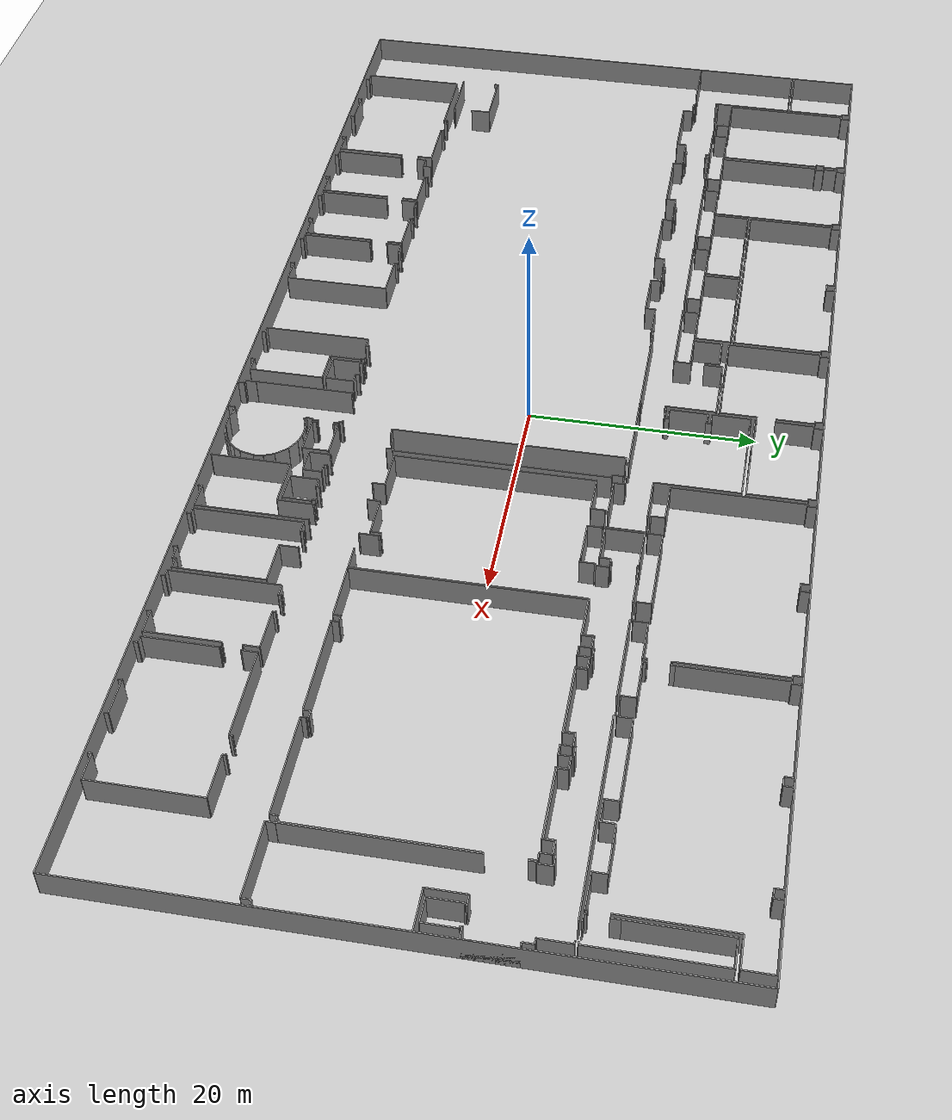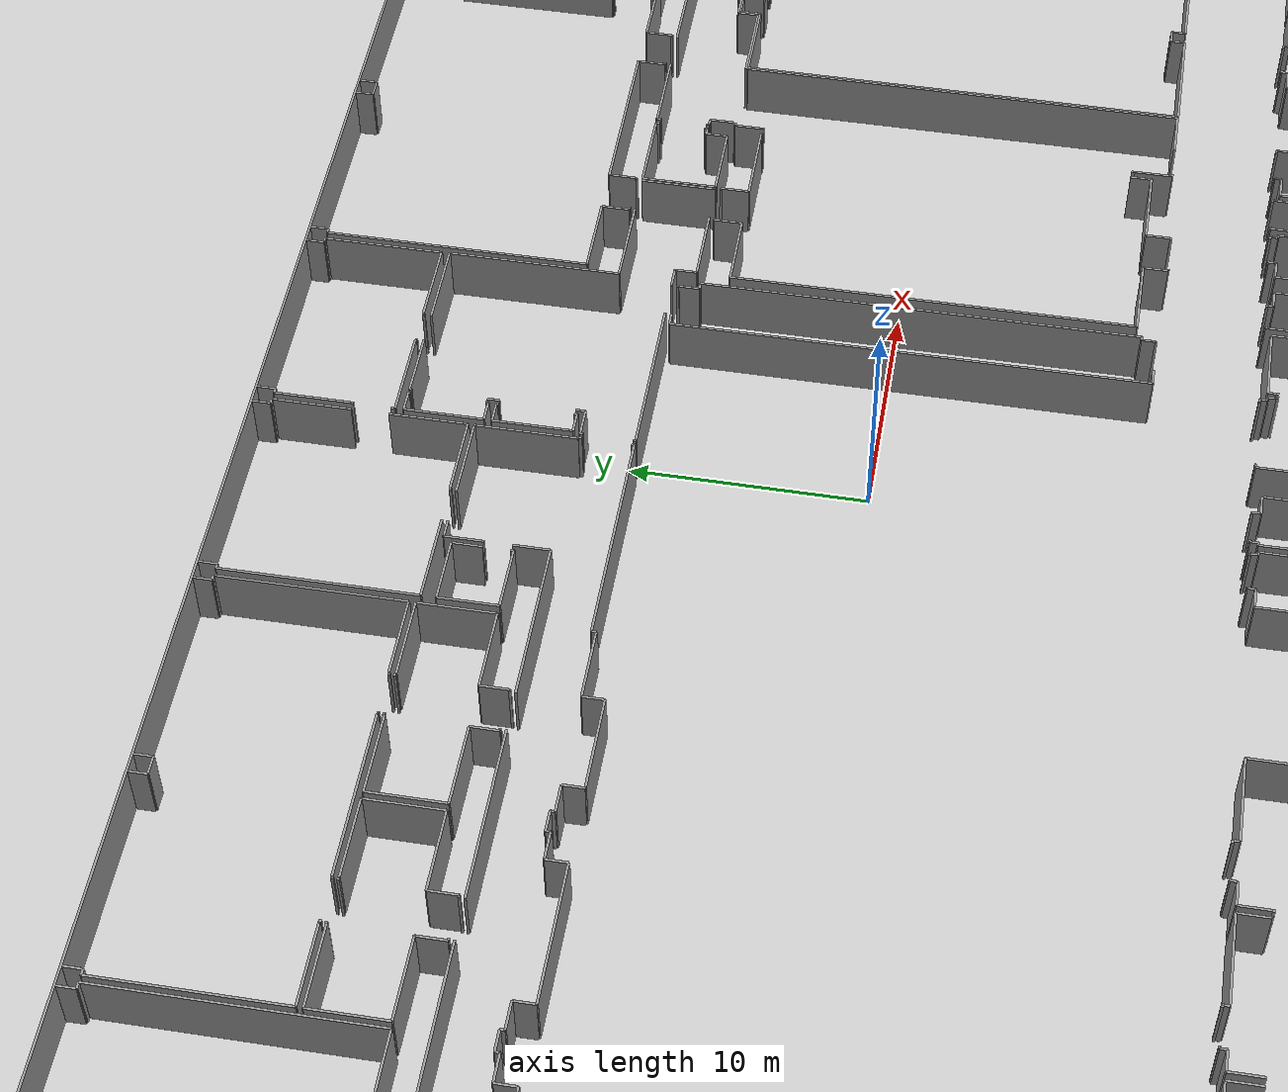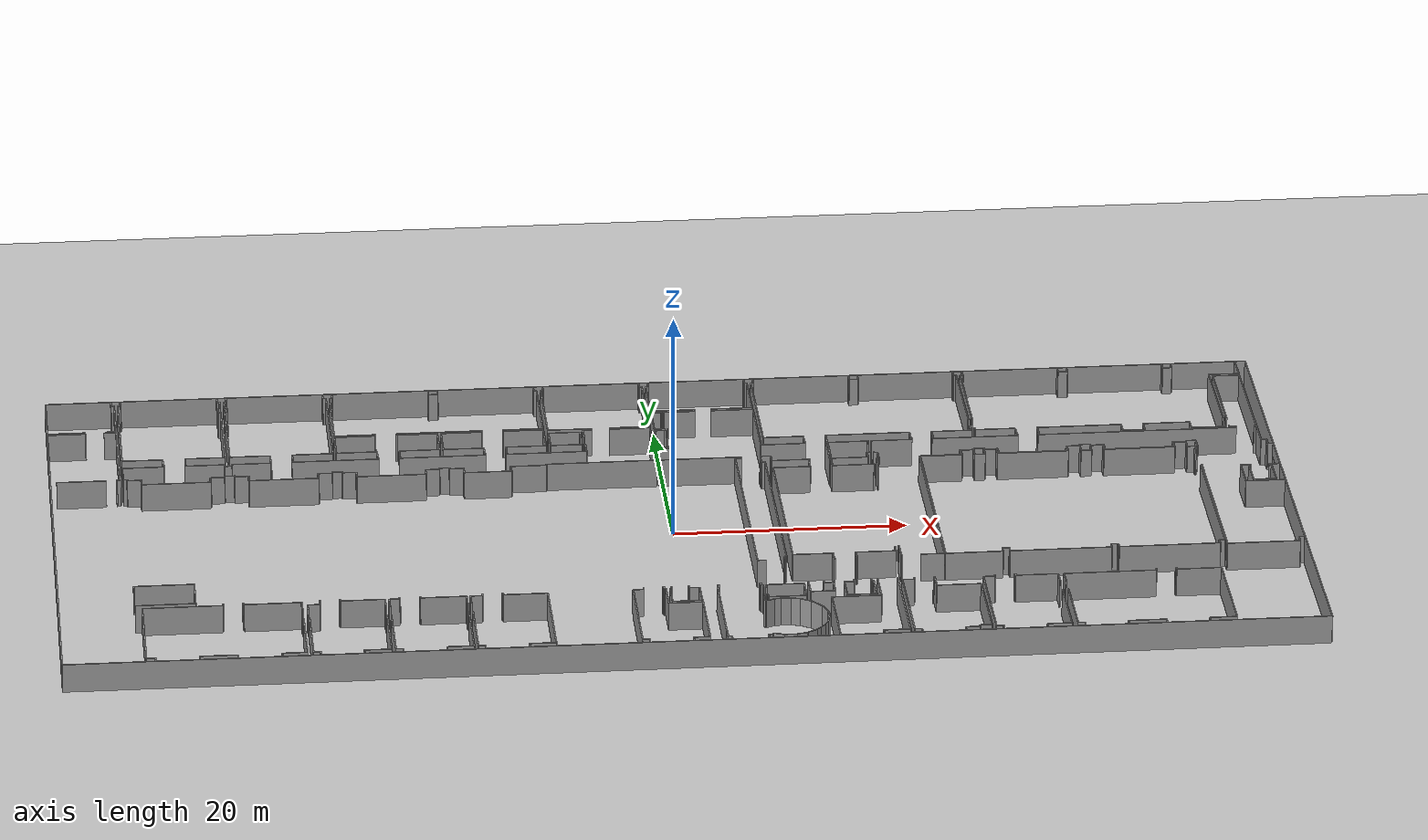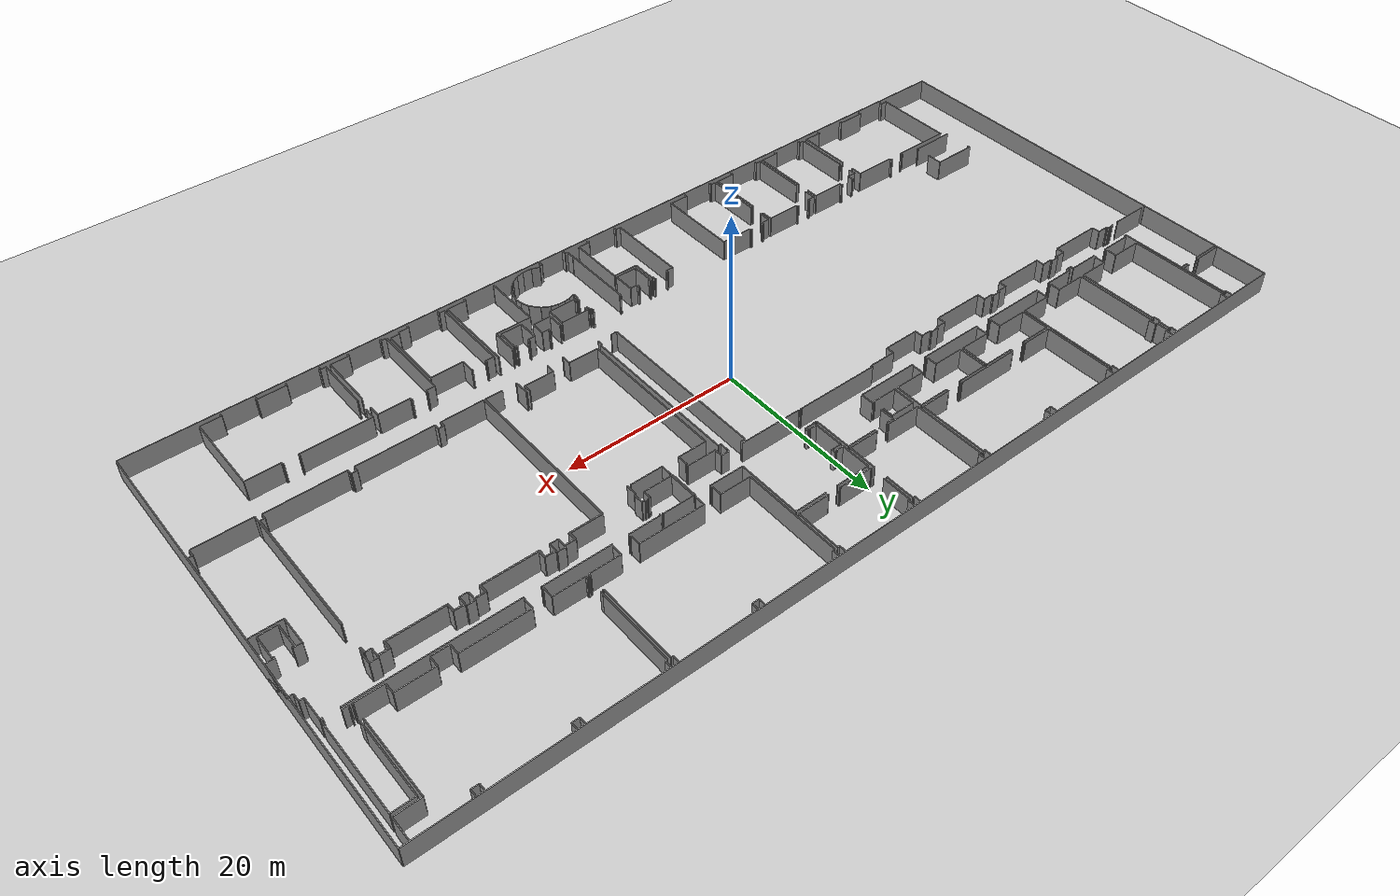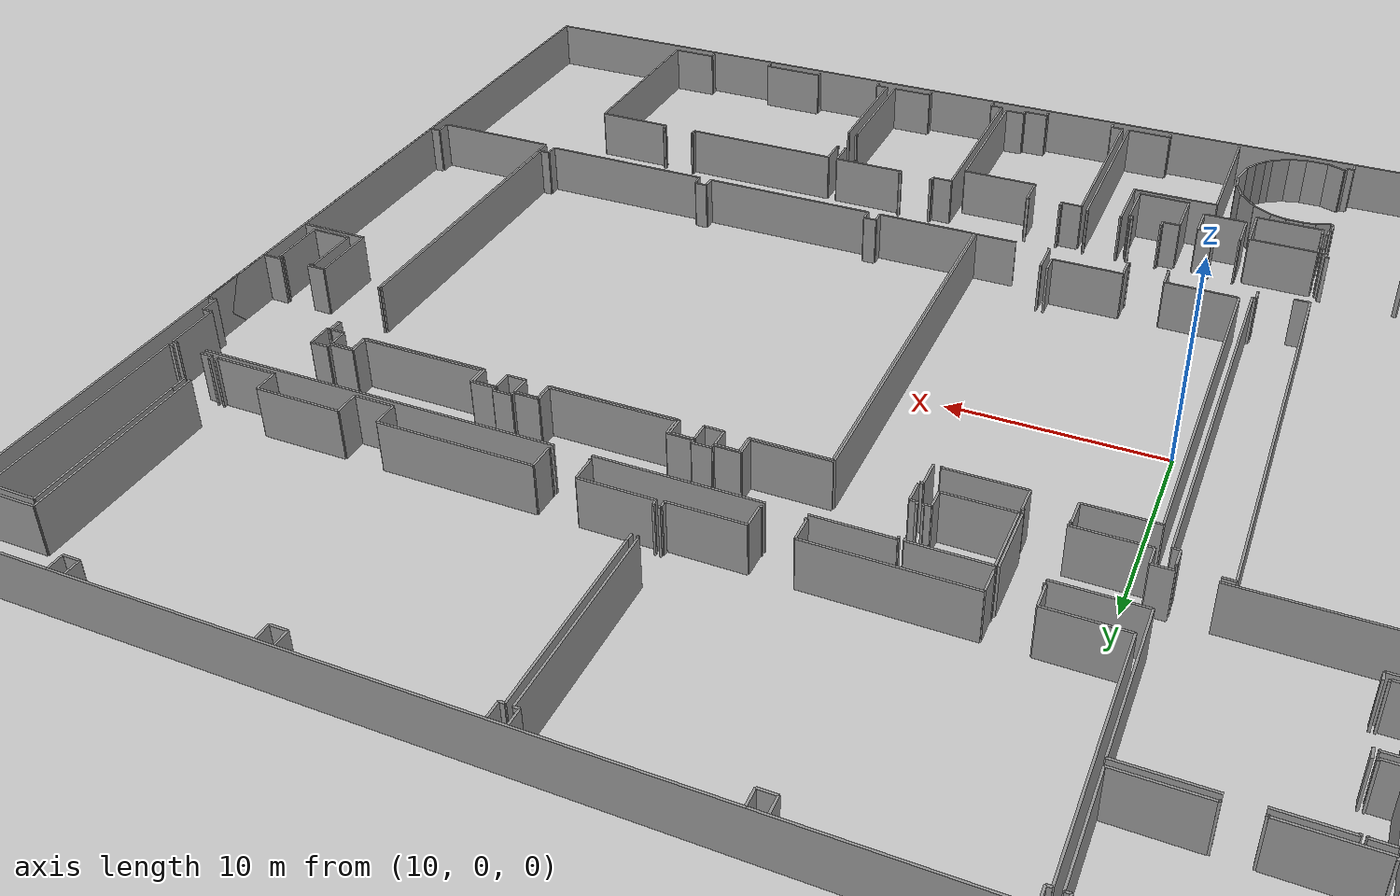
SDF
<sdf version="1.6">
  <world name="default">
    <light name="sun" type="directional">
      <cast_shadows>1</cast_shadows>
      <pose frame="">0 0 10 0 -0 0</pose>
      <diffuse>0.8 0.8 0.8 1</diffuse>
      <specular>0.1 0.1 0.1 1</specular>
      <attenuation>
        <range>1000</range>
        <constant>0.9</constant>
        <linear>0.01</linear>
        <quadratic>0.001</quadratic>
      </attenuation>
      <direction>-0.5 0.5 -1</direction>
    </light>
    <model name="ground_plane">
      <static>1</static>
      <link name="link">
        <collision name="collision">
          <geometry>
            <plane>
              <normal>0 0 1</normal>
              <size>100 100</size>
            </plane>
          </geometry>
          <surface>
            <friction>
              <ode>
                <mu>100</mu>
                <mu2>50</mu2>
              </ode>
              <torsional>
                <ode />
              </torsional>
            </friction>
            <contact>
              <ode />
            </contact>
            <bounce />
          </surface>
          <max_contacts>10</max_contacts>
        </collision>
        <visual name="visual">
          <cast_shadows>0</cast_shadows>
          <geometry>
            <plane>
              <normal>0 0 1</normal>
              <size>100 100</size>
            </plane>
          </geometry>
          <material>
            <script>
              <uri>file://media/materials/scripts/gazebo.material</uri>
              <name>Gazebo/Grey</name>
            </script>
          </material>
        </visual>
        <self_collide>0</self_collide>
        <kinematic>0</kinematic>
        <gravity>1</gravity>
      </link>
    </model>
    <gravity>0 0 -9.8</gravity>
    <magnetic_field>6e-06 2.3e-05 -4.2e-05</magnetic_field>
    <atmosphere type="adiabatic" />
    <physics default="0" name="default_physics" type="ode">
      <max_step_size>0.001</max_step_size>
      <real_time_factor>1</real_time_factor>
      <real_time_update_rate>1000</real_time_update_rate>
    </physics>
    <scene>
      <ambient>0.4 0.4 0.4 1</ambient>
      <background>0.7 0.7 0.7 1</background>
      <shadows>1</shadows>
    </scene>
    <spherical_coordinates>
      <surface_model>EARTH_WGS84</surface_model>
      <latitude_deg>0</latitude_deg>
      <longitude_deg>0</longitude_deg>
      <elevation>0</elevation>
      <heading_deg>0</heading_deg>
    </spherical_coordinates>
  <model name="50045368">
		<static>1</static>
		<link name="Wall_0">
			<collision name="Wall_0_Collision">
				<geometry>
					<box>
						<size>6.12770012706 0.1 2.5</size>
					</box>
				</geometry>
				<pose frame="">3.06385006353 0 1.25 0 0 0</pose>
			</collision>
			<visual name="Wall_0_Visual">
				<pose frame="">3.06385006353 0 1.25 0 0 0</pose>
				<geometry>
					<box>
						<size>6.12770012706 0.1 2.5</size>
					</box>
				</geometry>
				<material>
					<script>
						<uri>file://media/materials/scripts/gazebo.material</uri>
						<name>Gazebo/Grey</name>
					</script>
					<ambient>1 1 1 1</ambient>
				</material>
			</visual>
			<pose frame="">0.0210927573062 -6.13773824651 0 0 0 1.57079632679</pose>
		</link>
		<link name="Wall_1">
			<collision name="Wall_1_Collision">
				<geometry>
					<box>
						<size>0.803939008895 0.1 2.5</size>
					</box>
				</geometry>
				<pose frame="">0.401969504447 0 1.25 0 0 0</pose>
			</collision>
			<visual name="Wall_1_Visual">
				<pose frame="">0.401969504447 0 1.25 0 0 0</pose>
				<geometry>
					<box>
						<size>0.803939008895 0.1 2.5</size>
					</box>
				</geometry>
				<material>
					<script>
						<uri>file://media/materials/scripts/gazebo.material</uri>
						<name>Gazebo/Grey</name>
					</script>
					<ambient>1 1 1 1</ambient>
				</material>
			</visual>
			<pose frame="">5.71778907243 -0.0100381194409 0 0 0 -1.57079632679</pose>
		</link>
		<link name="Wall_2">
			<collision name="Wall_2_Collision">
				<geometry>
					<box>
						<size>0.256416772554 0.1 2.5</size>
					</box>
				</geometry>
				<pose frame="">0.128208386277 0 1.25 0 0 0</pose>
			</collision>
			<visual name="Wall_2_Visual">
				<pose frame="">0.128208386277 0 1.25 0 0 0</pose>
				<geometry>
					<box>
						<size>0.256416772554 0.1 2.5</size>
					</box>
				</geometry>
				<material>
					<script>
						<uri>file://media/materials/scripts/gazebo.material</uri>
						<name>Gazebo/Grey</name>
					</script>
					<ambient>1 1 1 1</ambient>
				</material>
			</visual>
			<pose frame="">5.71778907243 -0.813977128335 0 0 0 0.0</pose>
		</link>
		<link name="Wall_3">
			<collision name="Wall_3_Collision">
				<geometry>
					<box>
						<size>5.30127064803 0.1 2.5</size>
					</box>
				</geometry>
				<pose frame="">2.65063532402 0 1.25 0 0 0</pose>
			</collision>
			<visual name="Wall_3_Visual">
				<pose frame="">2.65063532402 0 1.25 0 0 0</pose>
				<geometry>
					<box>
						<size>5.30127064803 0.1 2.5</size>
					</box>
				</geometry>
				<material>
					<script>
						<uri>file://media/materials/scripts/gazebo.material</uri>
						<name>Gazebo/Grey</name>
					</script>
					<ambient>1 1 1 1</ambient>
				</material>
			</visual>
			<pose frame="">5.97420584498 -0.813977128335 0 0 0 -1.57079632679</pose>
		</link>
		<link name="Wall_4">
			<collision name="Wall_4_Collision">
				<geometry>
					<box>
						<size>0.945743329098 0.1 2.5</size>
					</box>
				</geometry>
				<pose frame="">0.472871664549 0 1.25 0 0 0</pose>
			</collision>
			<visual name="Wall_4_Visual">
				<pose frame="">0.472871664549 0 1.25 0 0 0</pose>
				<geometry>
					<box>
						<size>0.945743329098 0.1 2.5</size>
					</box>
				</geometry>
				<material>
					<script>
						<uri>file://media/materials/scripts/gazebo.material</uri>
						<name>Gazebo/Grey</name>
					</script>
					<ambient>1 1 1 1</ambient>
				</material>
			</visual>
			<pose frame="">5.97420584498 -6.11524777637 0 0 0 3.14159265359</pose>
		</link>
		<link name="Wall_5">
			<collision name="Wall_5_Collision">
				<geometry>
					<box>
						<size>3.25166608975 0.1 2.5</size>
					</box>
				</geometry>
				<pose frame="">1.62583304487 0 1.25 0 0 0</pose>
			</collision>
			<visual name="Wall_5_Visual">
				<pose frame="">1.62583304487 0 1.25 0 0 0</pose>
				<geometry>
					<box>
						<size>3.25166608975 0.1 2.5</size>
					</box>
				</geometry>
				<material>
					<script>
						<uri>file://media/materials/scripts/gazebo.material</uri>
						<name>Gazebo/Grey</name>
					</script>
					<ambient>1 1 1 1</ambient>
				</material>
			</visual>
			<pose frame="">3.27268106734 -6.11524777637 0 0 0 -3.13467599953</pose>
		</link>
		<link name="Wall_6">
			<collision name="Wall_6_Collision">
				<geometry>
					<box>
						<size>11.381956798 0.1 2.5</size>
					</box>
				</geometry>
				<pose frame="">5.69097839898 0 1.25 0 0 0</pose>
			</collision>
			<visual name="Wall_6_Visual">
				<pose frame="">5.69097839898 0 1.25 0 0 0</pose>
				<geometry>
					<box>
						<size>11.381956798 0.1 2.5</size>
					</box>
				</geometry>
				<material>
					<script>
						<uri>file://media/materials/scripts/gazebo.material</uri>
						<name>Gazebo/Grey</name>
					</script>
					<ambient>1 1 1 1</ambient>
				</material>
			</visual>
			<pose frame="">6.27445997459 -12.209021601 0 0 0 1.57079632679</pose>
		</link>
		<link name="Wall_7">
			<collision name="Wall_7_Collision">
				<geometry>
					<box>
						<size>0.246124523507 0.1 2.5</size>
					</box>
				</geometry>
				<pose frame="">0.123062261753 0 1.25 0 0 0</pose>
			</collision>
			<visual name="Wall_7_Visual">
				<pose frame="">0.123062261753 0 1.25 0 0 0</pose>
				<geometry>
					<box>
						<size>0.246124523507 0.1 2.5</size>
					</box>
				</geometry>
				<material>
					<script>
						<uri>file://media/materials/scripts/gazebo.material</uri>
						<name>Gazebo/Grey</name>
					</script>
					<ambient>1 1 1 1</ambient>
				</material>
			</visual>
			<pose frame="">6.27445997459 -0.82706480305 0 0 0 0.0</pose>
		</link>
		<link name="Wall_8">
			<collision name="Wall_8_Collision">
				<geometry>
					<box>
						<size>0.824015247776 0.1 2.5</size>
					</box>
				</geometry>
				<pose frame="">0.412007623888 0 1.25 0 0 0</pose>
			</collision>
			<visual name="Wall_8_Visual">
				<pose frame="">0.412007623888 0 1.25 0 0 0</pose>
				<geometry>
					<box>
						<size>0.824015247776 0.1 2.5</size>
					</box>
				</geometry>
				<material>
					<script>
						<uri>file://media/materials/scripts/gazebo.material</uri>
						<name>Gazebo/Grey</name>
					</script>
					<ambient>1 1 1 1</ambient>
				</material>
			</visual>
			<pose frame="">6.52058449809 -0.82706480305 0 0 0 1.57079632679</pose>
		</link>
		<link name="Wall_9">
			<collision name="Wall_9_Collision">
				<geometry>
					<box>
						<size>0.820330368488 0.1 2.5</size>
					</box>
				</geometry>
				<pose frame="">0.410165184244 0 1.25 0 0 0</pose>
			</collision>
			<visual name="Wall_9_Visual">
				<pose frame="">0.410165184244 0 1.25 0 0 0</pose>
				<geometry>
					<box>
						<size>0.820330368488 0.1 2.5</size>
					</box>
				</geometry>
				<material>
					<script>
						<uri>file://media/materials/scripts/gazebo.material</uri>
						<name>Gazebo/Grey</name>
					</script>
					<ambient>1 1 1 1</ambient>
				</material>
			</visual>
			<pose frame="">14.9540025413 -0.00304955527319 0 0 0 -1.57079632679</pose>
		</link>
		<link name="Wall_10">
			<collision name="Wall_10_Collision">
				<geometry>
					<box>
						<size>0.211817026684 0.1 2.5</size>
					</box>
				</geometry>
				<pose frame="">0.105908513342 0 1.25 0 0 0</pose>
			</collision>
			<visual name="Wall_10_Visual">
				<pose frame="">0.105908513342 0 1.25 0 0 0</pose>
				<geometry>
					<box>
						<size>0.211817026684 0.1 2.5</size>
					</box>
				</geometry>
				<material>
					<script>
						<uri>file://media/materials/scripts/gazebo.material</uri>
						<name>Gazebo/Grey</name>
					</script>
					<ambient>1 1 1 1</ambient>
				</material>
			</visual>
			<pose frame="">14.9540025413 -0.823379923761 0 0 0 0.0</pose>
		</link>
		<link name="Wall_11">
			<collision name="Wall_11_Collision">
				<geometry>
					<box>
						<size>1.3123252859 0.1 2.5</size>
					</box>
				</geometry>
				<pose frame="">0.656162642948 0 1.25 0 0 0</pose>
			</collision>
			<visual name="Wall_11_Visual">
				<pose frame="">0.656162642948 0 1.25 0 0 0</pose>
				<geometry>
					<box>
						<size>1.3123252859 0.1 2.5</size>
					</box>
				</geometry>
				<material>
					<script>
						<uri>file://media/materials/scripts/gazebo.material</uri>
						<name>Gazebo/Grey</name>
					</script>
					<ambient>1 1 1 1</ambient>
				</material>
			</visual>
			<pose frame="">15.165819568 -0.823379923761 0 0 0 -1.57079632679</pose>
		</link>
		<link name="Wall_12">
			<collision name="Wall_12_Collision">
				<geometry>
					<box>
						<size>0.196696315121 0.1 2.5</size>
					</box>
				</geometry>
				<pose frame="">0.0983481575604 0 1.25 0 0 0</pose>
			</collision>
			<visual name="Wall_12_Visual">
				<pose frame="">0.0983481575604 0 1.25 0 0 0</pose>
				<geometry>
					<box>
						<size>0.196696315121 0.1 2.5</size>
					</box>
				</geometry>
				<material>
					<script>
						<uri>file://media/materials/scripts/gazebo.material</uri>
						<name>Gazebo/Grey</name>
					</script>
					<ambient>1 1 1 1</ambient>
				</material>
			</visual>
			<pose frame="">15.165819568 -2.13570520966 0 0 0 3.14159265359</pose>
		</link>
		<link name="Wall_13">
			<collision name="Wall_13_Collision">
				<geometry>
					<box>
						<size>0.790216010165 0.1 2.5</size>
					</box>
				</geometry>
				<pose frame="">0.395108005083 0 1.25 0 0 0</pose>
			</collision>
			<visual name="Wall_13_Visual">
				<pose frame="">0.395108005083 0 1.25 0 0 0</pose>
				<geometry>
					<box>
						<size>0.790216010165 0.1 2.5</size>
					</box>
				</geometry>
				<material>
					<script>
						<uri>file://media/materials/scripts/gazebo.material</uri>
						<name>Gazebo/Grey</name>
					</script>
					<ambient>1 1 1 1</ambient>
				</material>
			</visual>
			<pose frame="">14.9691232529 -2.13570520966 0 0 0 -1.57079632679</pose>
		</link>
		<link name="Wall_14">
			<collision name="Wall_14_Collision">
				<geometry>
					<box>
						<size>0.202160101652 0.1 2.5</size>
					</box>
				</geometry>
				<pose frame="">0.101080050826 0 1.25 0 0 0</pose>
			</collision>
			<visual name="Wall_14_Visual">
				<pose frame="">0.101080050826 0 1.25 0 0 0</pose>
				<geometry>
					<box>
						<size>0.202160101652 0.1 2.5</size>
					</box>
				</geometry>
				<material>
					<script>
						<uri>file://media/materials/scripts/gazebo.material</uri>
						<name>Gazebo/Grey</name>
					</script>
					<ambient>1 1 1 1</ambient>
				</material>
			</visual>
			<pose frame="">14.9691232529 -2.92592121982 0 0 0 0.0</pose>
		</link>
		<link name="Wall_15">
			<collision name="Wall_15_Collision">
				<geometry>
					<box>
						<size>9.2833545108 0.1 2.5</size>
					</box>
				</geometry>
				<pose frame="">4.6416772554 0 1.25 0 0 0</pose>
			</collision>
			<visual name="Wall_15_Visual">
				<pose frame="">4.6416772554 0 1.25 0 0 0</pose>
				<geometry>
					<box>
						<size>9.2833545108 0.1 2.5</size>
					</box>
				</geometry>
				<material>
					<script>
						<uri>file://media/materials/scripts/gazebo.material</uri>
						<name>Gazebo/Grey</name>
					</script>
					<ambient>1 1 1 1</ambient>
				</material>
			</visual>
			<pose frame="">15.1712833545 -2.92592121982 0 0 0 -1.57079632679</pose>
		</link>
		<link name="Wall_16">
			<collision name="Wall_16_Collision">
				<geometry>
					<box>
						<size>3.46493011436 0.1 2.5</size>
					</box>
				</geometry>
				<pose frame="">1.73246505718 0 1.25 0 0 0</pose>
			</collision>
			<visual name="Wall_16_Visual">
				<pose frame="">1.73246505718 0 1.25 0 0 0</pose>
				<geometry>
					<box>
						<size>3.46493011436 0.1 2.5</size>
					</box>
				</geometry>
				<material>
					<script>
						<uri>file://media/materials/scripts/gazebo.material</uri>
						<name>Gazebo/Grey</name>
					</script>
					<ambient>1 1 1 1</ambient>
				</material>
			</visual>
			<pose frame="">15.1712833545 -12.2092757306 0 0 0 3.14159265359</pose>
		</link>
		<link name="Wall_17">
			<collision name="Wall_17_Collision">
				<geometry>
					<box>
						<size>1.2124523507 0.1 2.5</size>
					</box>
				</geometry>
				<pose frame="">0.606226175349 0 1.25 0 0 0</pose>
			</collision>
			<visual name="Wall_17_Visual">
				<pose frame="">0.606226175349 0 1.25 0 0 0</pose>
				<geometry>
					<box>
						<size>1.2124523507 0.1 2.5</size>
					</box>
				</geometry>
				<material>
					<script>
						<uri>file://media/materials/scripts/gazebo.material</uri>
						<name>Gazebo/Grey</name>
					</script>
					<ambient>1 1 1 1</ambient>
				</material>
			</visual>
			<pose frame="">11.7063532402 -12.2092757306 0 0 0 -1.57079632679</pose>
		</link>
		<link name="Wall_18">
			<collision name="Wall_18_Collision">
				<geometry>
					<box>
						<size>0.0837357052097 0.1 2.5</size>
					</box>
				</geometry>
				<pose frame="">0.0418678526048 0 1.25 0 0 0</pose>
			</collision>
			<visual name="Wall_18_Visual">
				<pose frame="">0.0418678526048 0 1.25 0 0 0</pose>
				<geometry>
					<box>
						<size>0.0837357052097 0.1 2.5</size>
					</box>
				</geometry>
				<material>
					<script>
						<uri>file://media/materials/scripts/gazebo.material</uri>
						<name>Gazebo/Grey</name>
					</script>
					<ambient>1 1 1 1</ambient>
				</material>
			</visual>
			<pose frame="">11.7063532402 -13.4217280813 0 0 0 3.14159265359</pose>
		</link>
		<link name="Wall_19">
			<collision name="Wall_19_Collision">
				<geometry>
					<box>
						<size>0.116391359593 0.1 2.5</size>
					</box>
				</geometry>
				<pose frame="">0.0581956797967 0 1.25 0 0 0</pose>
			</collision>
			<visual name="Wall_19_Visual">
				<pose frame="">0.0581956797967 0 1.25 0 0 0</pose>
				<geometry>
					<box>
						<size>0.116391359593 0.1 2.5</size>
					</box>
				</geometry>
				<material>
					<script>
						<uri>file://media/materials/scripts/gazebo.material</uri>
						<name>Gazebo/Grey</name>
					</script>
					<ambient>1 1 1 1</ambient>
				</material>
			</visual>
			<pose frame="">9.89059720457 -13.4217280813 0 0 0 3.14159265359</pose>
		</link>
		<link name="Wall_20">
			<collision name="Wall_20_Collision">
				<geometry>
					<box>
						<size>1.20216010165 0.1 2.5</size>
					</box>
				</geometry>
				<pose frame="">0.601080050826 0 1.25 0 0 0</pose>
			</collision>
			<visual name="Wall_20_Visual">
				<pose frame="">0.601080050826 0 1.25 0 0 0</pose>
				<geometry>
					<box>
						<size>1.20216010165 0.1 2.5</size>
					</box>
				</geometry>
				<material>
					<script>
						<uri>file://media/materials/scripts/gazebo.material</uri>
						<name>Gazebo/Grey</name>
					</script>
					<ambient>1 1 1 1</ambient>
				</material>
			</visual>
			<pose frame="">9.77420584498 -13.4217280813 0 0 0 1.57079632679</pose>
		</link>
		<link name="Wall_21">
			<collision name="Wall_21_Collision">
				<geometry>
					<box>
						<size>3.49976176095 0.1 2.5</size>
					</box>
				</geometry>
				<pose frame="">1.74988088048 0 1.25 0 0 0</pose>
			</collision>
			<visual name="Wall_21_Visual">
				<pose frame="">1.74988088048 0 1.25 0 0 0</pose>
				<geometry>
					<box>
						<size>3.49976176095 0.1 2.5</size>
					</box>
				</geometry>
				<material>
					<script>
						<uri>file://media/materials/scripts/gazebo.material</uri>
						<name>Gazebo/Grey</name>
					</script>
					<ambient>1 1 1 1</ambient>
				</material>
			</visual>
			<pose frame="">9.77420584498 -12.2195679797 0 0 0 3.13857919286</pose>
		</link>
		<link name="Wall_22">
			<collision name="Wall_22_Collision">
				<geometry>
					<box>
						<size>9.61041931385 0.1 2.5</size>
					</box>
				</geometry>
				<pose frame="">4.80520965693 0 1.25 0 0 0</pose>
			</collision>
			<visual name="Wall_22_Visual">
				<pose frame="">4.80520965693 0 1.25 0 0 0</pose>
				<geometry>
					<box>
						<size>9.61041931385 0.1 2.5</size>
					</box>
				</geometry>
				<material>
					<script>
						<uri>file://media/materials/scripts/gazebo.material</uri>
						<name>Gazebo/Grey</name>
					</script>
					<ambient>1 1 1 1</ambient>
				</material>
			</visual>
			<pose frame="">0.00368487928844 -16.0022871665 0 0 0 1.57079632679</pose>
		</link>
		<link name="Wall_23">
			<collision name="Wall_23_Collision">
				<geometry>
					<box>
						<size>3.26988564168 0.1 2.5</size>
					</box>
				</geometry>
				<pose frame="">1.63494282084 0 1.25 0 0 0</pose>
			</collision>
			<visual name="Wall_23_Visual">
				<pose frame="">1.63494282084 0 1.25 0 0 0</pose>
				<geometry>
					<box>
						<size>3.26988564168 0.1 2.5</size>
					</box>
				</geometry>
				<material>
					<script>
						<uri>file://media/materials/scripts/gazebo.material</uri>
						<name>Gazebo/Grey</name>
					</script>
					<ambient>1 1 1 1</ambient>
				</material>
			</visual>
			<pose frame="">0.00368487928844 -6.3918678526 0 0 0 0.0</pose>
		</link>
		<link name="Wall_24">
			<collision name="Wall_24_Collision">
				<geometry>
					<box>
						<size>0.0315120711563 0.1 2.5</size>
					</box>
				</geometry>
				<pose frame="">0.0157560355781 0 1.25 0 0 0</pose>
			</collision>
			<visual name="Wall_24_Visual">
				<pose frame="">0.0157560355781 0 1.25 0 0 0</pose>
				<geometry>
					<box>
						<size>0.0315120711563 0.1 2.5</size>
					</box>
				</geometry>
				<material>
					<script>
						<uri>file://media/materials/scripts/gazebo.material</uri>
						<name>Gazebo/Grey</name>
					</script>
					<ambient>1 1 1 1</ambient>
				</material>
			</visual>
			<pose frame="">3.27357052097 -6.3918678526 0 0 0 1.57079632679</pose>
		</link>
		<link name="Wall_25">
			<collision name="Wall_25_Collision">
				<geometry>
					<box>
						<size>0.0748411689962 0.1 2.5</size>
					</box>
				</geometry>
				<pose frame="">0.0374205844981 0 1.25 0 0 0</pose>
			</collision>
			<visual name="Wall_25_Visual">
				<pose frame="">0.0374205844981 0 1.25 0 0 0</pose>
				<geometry>
					<box>
						<size>0.0748411689962 0.1 2.5</size>
					</box>
				</geometry>
				<material>
					<script>
						<uri>file://media/materials/scripts/gazebo.material</uri>
						<name>Gazebo/Grey</name>
					</script>
					<ambient>1 1 1 1</ambient>
				</material>
			</visual>
			<pose frame="">3.27357052097 -6.36035578145 0 0 0 0.0</pose>
		</link>
		<link name="Wall_26">
			<collision name="Wall_26_Collision">
				<geometry>
					<box>
						<size>1.07331639136 0.1 2.5</size>
					</box>
				</geometry>
				<pose frame="">0.53665819568 0 1.25 0 0 0</pose>
			</collision>
			<visual name="Wall_26_Visual">
				<pose frame="">0.53665819568 0 1.25 0 0 0</pose>
				<geometry>
					<box>
						<size>1.07331639136 0.1 2.5</size>
					</box>
				</geometry>
				<material>
					<script>
						<uri>file://media/materials/scripts/gazebo.material</uri>
						<name>Gazebo/Grey</name>
					</script>
					<ambient>1 1 1 1</ambient>
				</material>
			</visual>
			<pose frame="">4.90482846252 -6.36035578145 0 0 0 0.0</pose>
		</link>
		<link name="Wall_27">
			<collision name="Wall_27_Collision">
				<geometry>
					<box>
						<size>7.40609911055 0.1 2.5</size>
					</box>
				</geometry>
				<pose frame="">3.70304955527 0 1.25 0 0 0</pose>
			</collision>
			<visual name="Wall_27_Visual">
				<pose frame="">3.70304955527 0 1.25 0 0 0</pose>
				<geometry>
					<box>
						<size>7.40609911055 0.1 2.5</size>
					</box>
				</geometry>
				<material>
					<script>
						<uri>file://media/materials/scripts/gazebo.material</uri>
						<name>Gazebo/Grey</name>
					</script>
					<ambient>1 1 1 1</ambient>
				</material>
			</visual>
			<pose frame="">5.97814485388 -6.36035578145 0 0 0 -1.57079632679</pose>
		</link>
		<link name="Wall_28">
			<collision name="Wall_28_Collision">
				<geometry>
					<box>
						<size>0.0430749682338 0.1 2.5</size>
					</box>
				</geometry>
				<pose frame="">0.0215374841169 0 1.25 0 0 0</pose>
			</collision>
			<visual name="Wall_28_Visual">
				<pose frame="">0.0215374841169 0 1.25 0 0 0</pose>
				<geometry>
					<box>
						<size>0.0430749682338 0.1 2.5</size>
					</box>
				</geometry>
				<material>
					<script>
						<uri>file://media/materials/scripts/gazebo.material</uri>
						<name>Gazebo/Grey</name>
					</script>
					<ambient>1 1 1 1</ambient>
				</material>
			</visual>
			<pose frame="">5.97814485388 -13.766454892 0 0 0 0.0</pose>
		</link>
		<link name="Wall_29">
			<collision name="Wall_29_Collision">
				<geometry>
					<box>
						<size>0.137229987294 0.1 2.5</size>
					</box>
				</geometry>
				<pose frame="">0.0686149936468 0 1.25 0 0 0</pose>
			</collision>
			<visual name="Wall_29_Visual">
				<pose frame="">0.0686149936468 0 1.25 0 0 0</pose>
				<geometry>
					<box>
						<size>0.137229987294 0.1 2.5</size>
					</box>
				</geometry>
				<material>
					<script>
						<uri>file://media/materials/scripts/gazebo.material</uri>
						<name>Gazebo/Grey</name>
					</script>
					<ambient>1 1 1 1</ambient>
				</material>
			</visual>
			<pose frame="">6.02121982211 -13.766454892 0 0 0 -1.57079632679</pose>
		</link>
		<link name="Wall_30">
			<collision name="Wall_30_Collision">
				<geometry>
					<box>
						<size>0.12998729352 0.1 2.5</size>
					</box>
				</geometry>
				<pose frame="">0.0649936467598 0 1.25 0 0 0</pose>
			</collision>
			<visual name="Wall_30_Visual">
				<pose frame="">0.0649936467598 0 1.25 0 0 0</pose>
				<geometry>
					<box>
						<size>0.12998729352 0.1 2.5</size>
					</box>
				</geometry>
				<material>
					<script>
						<uri>file://media/materials/scripts/gazebo.material</uri>
						<name>Gazebo/Grey</name>
					</script>
					<ambient>1 1 1 1</ambient>
				</material>
			</visual>
			<pose frame="">6.02121982211 -15.8470139771 0 0 0 -1.57079632679</pose>
		</link>
		<link name="Wall_31">
			<collision name="Wall_31_Collision">
				<geometry>
					<box>
						<size>0.328716645489 0.1 2.5</size>
					</box>
				</geometry>
				<pose frame="">0.164358322745 0 1.25 0 0 0</pose>
			</collision>
			<visual name="Wall_31_Visual">
				<pose frame="">0.164358322745 0 1.25 0 0 0</pose>
				<geometry>
					<box>
						<size>0.328716645489 0.1 2.5</size>
					</box>
				</geometry>
				<material>
					<script>
						<uri>file://media/materials/scripts/gazebo.material</uri>
						<name>Gazebo/Grey</name>
					</script>
					<ambient>1 1 1 1</ambient>
				</material>
			</visual>
			<pose frame="">6.02121982211 -15.9770012706 0 0 0 3.14159265359</pose>
		</link>
		<link name="Wall_32">
			<collision name="Wall_32_Collision">
				<geometry>
					<box>
						<size>0.0722998729352 0.1 2.5</size>
					</box>
				</geometry>
				<pose frame="">0.0361499364676 0 1.25 0 0 0</pose>
			</collision>
			<visual name="Wall_32_Visual">
				<pose frame="">0.0361499364676 0 1.25 0 0 0</pose>
				<geometry>
					<box>
						<size>0.0722998729352 0.1 2.5</size>
					</box>
				</geometry>
				<material>
					<script>
						<uri>file://media/materials/scripts/gazebo.material</uri>
						<name>Gazebo/Grey</name>
					</script>
					<ambient>1 1 1 1</ambient>
				</material>
			</visual>
			<pose frame="">5.69250317662 -15.9770012706 0 0 0 -1.57079632679</pose>
		</link>
		<link name="Wall_33">
			<collision name="Wall_33_Collision">
				<geometry>
					<box>
						<size>4.24764930114 0.1 2.5</size>
					</box>
				</geometry>
				<pose frame="">2.12382465057 0 1.25 0 0 0</pose>
			</collision>
			<visual name="Wall_33_Visual">
				<pose frame="">2.12382465057 0 1.25 0 0 0</pose>
				<geometry>
					<box>
						<size>4.24764930114 0.1 2.5</size>
					</box>
				</geometry>
				<material>
					<script>
						<uri>file://media/materials/scripts/gazebo.material</uri>
						<name>Gazebo/Grey</name>
					</script>
					<ambient>1 1 1 1</ambient>
				</material>
			</visual>
			<pose frame="">4.7750952986 -16.0493011436 0 0 0 3.14159265359</pose>
		</link>
		<link name="Wall_34">
			<collision name="Wall_34_Collision">
				<geometry>
					<box>
						<size>0.0471581634587 0.1 2.5</size>
					</box>
				</geometry>
				<pose frame="">0.0235790817293 0 1.25 0 0 0</pose>
			</collision>
			<visual name="Wall_34_Visual">
				<pose frame="">0.0235790817293 0 1.25 0 0 0</pose>
				<geometry>
					<box>
						<size>0.0471581634587 0.1 2.5</size>
					</box>
				</geometry>
				<material>
					<script>
						<uri>file://media/materials/scripts/gazebo.material</uri>
						<name>Gazebo/Grey</name>
					</script>
					<ambient>1 1 1 1</ambient>
				</material>
			</visual>
			<pose frame="">0.0 -16.0493011436 0 0 0 1.49257785666</pose>
		</link>
		<link name="Wall_35">
			<collision name="Wall_35_Collision">
				<geometry>
					<box>
						<size>9.26772554003 0.1 2.5</size>
					</box>
				</geometry>
				<pose frame="">4.63386277001 0 1.25 0 0 0</pose>
			</collision>
			<visual name="Wall_35_Visual">
				<pose frame="">4.63386277001 0 1.25 0 0 0</pose>
				<geometry>
					<box>
						<size>9.26772554003 0.1 2.5</size>
					</box>
				</geometry>
				<material>
					<script>
						<uri>file://media/materials/scripts/gazebo.material</uri>
						<name>Gazebo/Grey</name>
					</script>
					<ambient>1 1 1 1</ambient>
				</material>
			</visual>
			<pose frame="">15.540660737 -12.192884371 0 0 0 1.57079632679</pose>
		</link>
		<link name="Wall_36">
			<collision name="Wall_36_Collision">
				<geometry>
					<box>
						<size>0.21918678526 0.1 2.5</size>
					</box>
				</geometry>
				<pose frame="">0.10959339263 0 1.25 0 0 0</pose>
			</collision>
			<visual name="Wall_36_Visual">
				<pose frame="">0.10959339263 0 1.25 0 0 0</pose>
				<geometry>
					<box>
						<size>0.21918678526 0.1 2.5</size>
					</box>
				</geometry>
				<material>
					<script>
						<uri>file://media/materials/scripts/gazebo.material</uri>
						<name>Gazebo/Grey</name>
					</script>
					<ambient>1 1 1 1</ambient>
				</material>
			</visual>
			<pose frame="">15.540660737 -2.925158831 0 0 0 0.0</pose>
		</link>
		<link name="Wall_37">
			<collision name="Wall_37_Collision">
				<geometry>
					<box>
						<size>0.793392630241 0.1 2.5</size>
					</box>
				</geometry>
				<pose frame="">0.396696315121 0 1.25 0 0 0</pose>
			</collision>
			<visual name="Wall_37_Visual">
				<pose frame="">0.396696315121 0 1.25 0 0 0</pose>
				<geometry>
					<box>
						<size>0.793392630241 0.1 2.5</size>
					</box>
				</geometry>
				<material>
					<script>
						<uri>file://media/materials/scripts/gazebo.material</uri>
						<name>Gazebo/Grey</name>
					</script>
					<ambient>1 1 1 1</ambient>
				</material>
			</visual>
			<pose frame="">15.7598475222 -2.925158831 0 0 0 1.57079632679</pose>
		</link>
		<link name="Wall_38">
			<collision name="Wall_38_Collision">
				<geometry>
					<box>
						<size>0.211817026684 0.1 2.5</size>
					</box>
				</geometry>
				<pose frame="">0.105908513342 0 1.25 0 0 0</pose>
			</collision>
			<visual name="Wall_38_Visual">
				<pose frame="">0.105908513342 0 1.25 0 0 0</pose>
				<geometry>
					<box>
						<size>0.211817026684 0.1 2.5</size>
					</box>
				</geometry>
				<material>
					<script>
						<uri>file://media/materials/scripts/gazebo.material</uri>
						<name>Gazebo/Grey</name>
					</script>
					<ambient>1 1 1 1</ambient>
				</material>
			</visual>
			<pose frame="">15.7598475222 -2.13176620076 0 0 0 3.14159265359</pose>
		</link>
		<link name="Wall_39">
			<collision name="Wall_39_Collision">
				<geometry>
					<box>
						<size>1.30470139771 0.1 2.5</size>
					</box>
				</geometry>
				<pose frame="">0.652350698856 0 1.25 0 0 0</pose>
			</collision>
			<visual name="Wall_39_Visual">
				<pose frame="">0.652350698856 0 1.25 0 0 0</pose>
				<geometry>
					<box>
						<size>1.30470139771 0.1 2.5</size>
					</box>
				</geometry>
				<material>
					<script>
						<uri>file://media/materials/scripts/gazebo.material</uri>
						<name>Gazebo/Grey</name>
					</script>
					<ambient>1 1 1 1</ambient>
				</material>
			</visual>
			<pose frame="">15.5480304956 -2.13176620076 0 0 0 1.57079632679</pose>
		</link>
		<link name="Wall_40">
			<collision name="Wall_40_Collision">
				<geometry>
					<box>
						<size>0.212452350699 0.1 2.5</size>
					</box>
				</geometry>
				<pose frame="">0.106226175349 0 1.25 0 0 0</pose>
			</collision>
			<visual name="Wall_40_Visual">
				<pose frame="">0.106226175349 0 1.25 0 0 0</pose>
				<geometry>
					<box>
						<size>0.212452350699 0.1 2.5</size>
					</box>
				</geometry>
				<material>
					<script>
						<uri>file://media/materials/scripts/gazebo.material</uri>
						<name>Gazebo/Grey</name>
					</script>
					<ambient>1 1 1 1</ambient>
				</material>
			</visual>
			<pose frame="">15.5480304956 -0.82706480305 0 0 0 0.0</pose>
		</link>
		<link name="Wall_41">
			<collision name="Wall_41_Collision">
				<geometry>
					<box>
						<size>0.812960609911 0.1 2.5</size>
					</box>
				</geometry>
				<pose frame="">0.406480304956 0 1.25 0 0 0</pose>
			</collision>
			<visual name="Wall_41_Visual">
				<pose frame="">0.406480304956 0 1.25 0 0 0</pose>
				<geometry>
					<box>
						<size>0.812960609911 0.1 2.5</size>
					</box>
				</geometry>
				<material>
					<script>
						<uri>file://media/materials/scripts/gazebo.material</uri>
						<name>Gazebo/Grey</name>
					</script>
					<ambient>1 1 1 1</ambient>
				</material>
			</visual>
			<pose frame="">15.7604828463 -0.82706480305 0 0 0 1.57079632679</pose>
		</link>
		<link name="Wall_42">
			<collision name="Wall_42_Collision">
				<geometry>
					<box>
						<size>0.80876747141 0.1 2.5</size>
					</box>
				</geometry>
				<pose frame="">0.404383735705 0 1.25 0 0 0</pose>
			</collision>
			<visual name="Wall_42_Visual">
				<pose frame="">0.404383735705 0 1.25 0 0 0</pose>
				<geometry>
					<box>
						<size>0.80876747141 0.1 2.5</size>
					</box>
				</geometry>
				<material>
					<script>
						<uri>file://media/materials/scripts/gazebo.material</uri>
						<name>Gazebo/Grey</name>
					</script>
					<ambient>1 1 1 1</ambient>
				</material>
			</visual>
			<pose frame="">24.2033036849 -0.0141041931385 0 0 0 -1.57079632679</pose>
		</link>
		<link name="Wall_43">
			<collision name="Wall_43_Collision">
				<geometry>
					<box>
						<size>0.266963151207 0.1 2.5</size>
					</box>
				</geometry>
				<pose frame="">0.133481575604 0 1.25 0 0 0</pose>
			</collision>
			<visual name="Wall_43_Visual">
				<pose frame="">0.133481575604 0 1.25 0 0 0</pose>
				<geometry>
					<box>
						<size>0.266963151207 0.1 2.5</size>
					</box>
				</geometry>
				<material>
					<script>
						<uri>file://media/materials/scripts/gazebo.material</uri>
						<name>Gazebo/Grey</name>
					</script>
					<ambient>1 1 1 1</ambient>
				</material>
			</visual>
			<pose frame="">24.2033036849 -0.822871664549 0 0 0 0.0</pose>
		</link>
		<link name="Wall_44">
			<collision name="Wall_44_Collision">
				<geometry>
					<box>
						<size>11.3900889454 0.1 2.5</size>
					</box>
				</geometry>
				<pose frame="">5.69504447268 0 1.25 0 0 0</pose>
			</collision>
			<visual name="Wall_44_Visual">
				<pose frame="">5.69504447268 0 1.25 0 0 0</pose>
				<geometry>
					<box>
						<size>11.3900889454 0.1 2.5</size>
					</box>
				</geometry>
				<material>
					<script>
						<uri>file://media/materials/scripts/gazebo.material</uri>
						<name>Gazebo/Grey</name>
					</script>
					<ambient>1 1 1 1</ambient>
				</material>
			</visual>
			<pose frame="">24.4702668361 -0.822871664549 0 0 0 -1.57079632679</pose>
		</link>
		<link name="Wall_45">
			<collision name="Wall_45_Collision">
				<geometry>
					<box>
						<size>3.51817026684 0.1 2.5</size>
					</box>
				</geometry>
				<pose frame="">1.75908513342 0 1.25 0 0 0</pose>
			</collision>
			<visual name="Wall_45_Visual">
				<pose frame="">1.75908513342 0 1.25 0 0 0</pose>
				<geometry>
					<box>
						<size>3.51817026684 0.1 2.5</size>
					</box>
				</geometry>
				<material>
					<script>
						<uri>file://media/materials/scripts/gazebo.material</uri>
						<name>Gazebo/Grey</name>
					</script>
					<ambient>1 1 1 1</ambient>
				</material>
			</visual>
			<pose frame="">24.4702668361 -12.2129606099 0 0 0 3.14159265359</pose>
		</link>
		<link name="Wall_46">
			<collision name="Wall_46_Collision">
				<geometry>
					<box>
						<size>1.20470139771 0.1 2.5</size>
					</box>
				</geometry>
				<pose frame="">0.602350698856 0 1.25 0 0 0</pose>
			</collision>
			<visual name="Wall_46_Visual">
				<pose frame="">0.602350698856 0 1.25 0 0 0</pose>
				<geometry>
					<box>
						<size>1.20470139771 0.1 2.5</size>
					</box>
				</geometry>
				<material>
					<script>
						<uri>file://media/materials/scripts/gazebo.material</uri>
						<name>Gazebo/Grey</name>
					</script>
					<ambient>1 1 1 1</ambient>
				</material>
			</visual>
			<pose frame="">20.9520965693 -12.2129606099 0 0 0 -1.57079632679</pose>
		</link>
		<link name="Wall_47">
			<collision name="Wall_47_Collision">
				<geometry>
					<box>
						<size>0.0749682337992 0.1 2.5</size>
					</box>
				</geometry>
				<pose frame="">0.0374841168996 0 1.25 0 0 0</pose>
			</collision>
			<visual name="Wall_47_Visual">
				<pose frame="">0.0374841168996 0 1.25 0 0 0</pose>
				<geometry>
					<box>
						<size>0.0749682337992 0.1 2.5</size>
					</box>
				</geometry>
				<material>
					<script>
						<uri>file://media/materials/scripts/gazebo.material</uri>
						<name>Gazebo/Grey</name>
					</script>
					<ambient>1 1 1 1</ambient>
				</material>
			</visual>
			<pose frame="">20.9520965693 -13.4176620076 0 0 0 3.14159265359</pose>
		</link>
		<link name="Wall_48">
			<collision name="Wall_48_Collision">
				<geometry>
					<box>
						<size>0.0914866581957 0.1 2.5</size>
					</box>
				</geometry>
				<pose frame="">0.0457433290978 0 1.25 0 0 0</pose>
			</collision>
			<visual name="Wall_48_Visual">
				<pose frame="">0.0457433290978 0 1.25 0 0 0</pose>
				<geometry>
					<box>
						<size>0.0914866581957 0.1 2.5</size>
					</box>
				</geometry>
				<material>
					<script>
						<uri>file://media/materials/scripts/gazebo.material</uri>
						<name>Gazebo/Grey</name>
					</script>
					<ambient>1 1 1 1</ambient>
				</material>
			</visual>
			<pose frame="">19.1285895807 -13.4176620076 0 0 0 3.14159265359</pose>
		</link>
		<link name="Wall_49">
			<collision name="Wall_49_Collision">
				<geometry>
					<box>
						<size>1.20864040661 0.1 2.5</size>
					</box>
				</geometry>
				<pose frame="">0.604320203304 0 1.25 0 0 0</pose>
			</collision>
			<visual name="Wall_49_Visual">
				<pose frame="">0.604320203304 0 1.25 0 0 0</pose>
				<geometry>
					<box>
						<size>1.20864040661 0.1 2.5</size>
					</box>
				</geometry>
				<material>
					<script>
						<uri>file://media/materials/scripts/gazebo.material</uri>
						<name>Gazebo/Grey</name>
					</script>
					<ambient>1 1 1 1</ambient>
				</material>
			</visual>
			<pose frame="">19.0371029225 -13.4176620076 0 0 0 1.57079632679</pose>
		</link>
		<link name="Wall_50">
			<collision name="Wall_50_Collision">
				<geometry>
					<box>
						<size>3.49647942463 0.1 2.5</size>
					</box>
				</geometry>
				<pose frame="">1.74823971231 0 1.25 0 0 0</pose>
			</collision>
			<visual name="Wall_50_Visual">
				<pose frame="">1.74823971231 0 1.25 0 0 0</pose>
				<geometry>
					<box>
						<size>3.49647942463 0.1 2.5</size>
					</box>
				</geometry>
				<material>
					<script>
						<uri>file://media/materials/scripts/gazebo.material</uri>
						<name>Gazebo/Grey</name>
					</script>
					<ambient>1 1 1 1</ambient>
				</material>
			</visual>
			<pose frame="">19.0371029225 -12.209021601 0 0 0 3.13697735765</pose>
		</link>
		<link name="Wall_51">
			<collision name="Wall_51_Collision">
				<geometry>
					<box>
						<size>7.85794155019 0.1 2.5</size>
					</box>
				</geometry>
				<pose frame="">3.9289707751 0 1.25 0 0 0</pose>
			</collision>
			<visual name="Wall_51_Visual">
				<pose frame="">3.9289707751 0 1.25 0 0 0</pose>
				<geometry>
					<box>
						<size>7.85794155019 0.1 2.5</size>
					</box>
				</geometry>
				<material>
					<script>
						<uri>file://media/materials/scripts/gazebo.material</uri>
						<name>Gazebo/Grey</name>
					</script>
					<ambient>1 1 1 1</ambient>
				</material>
			</visual>
			<pose frame="">24.7654383736 -8.68398983482 0 0 0 1.57079632679</pose>
		</link>
		<link name="Wall_52">
			<collision name="Wall_52_Collision">
				<geometry>
					<box>
						<size>0.24498094028 0.1 2.5</size>
					</box>
				</geometry>
				<pose frame="">0.12249047014 0 1.25 0 0 0</pose>
			</collision>
			<visual name="Wall_52_Visual">
				<pose frame="">0.12249047014 0 1.25 0 0 0</pose>
				<geometry>
					<box>
						<size>0.24498094028 0.1 2.5</size>
					</box>
				</geometry>
				<material>
					<script>
						<uri>file://media/materials/scripts/gazebo.material</uri>
						<name>Gazebo/Grey</name>
					</script>
					<ambient>1 1 1 1</ambient>
				</material>
			</visual>
			<pose frame="">24.7654383736 -0.826048284625 0 0 0 0.0</pose>
		</link>
		<link name="Wall_53">
			<collision name="Wall_53_Collision">
				<geometry>
					<box>
						<size>0.826048284625 0.1 2.5</size>
					</box>
				</geometry>
				<pose frame="">0.413024142313 0 1.25 0 0 0</pose>
			</collision>
			<visual name="Wall_53_Visual">
				<pose frame="">0.413024142313 0 1.25 0 0 0</pose>
				<geometry>
					<box>
						<size>0.826048284625 0.1 2.5</size>
					</box>
				</geometry>
				<material>
					<script>
						<uri>file://media/materials/scripts/gazebo.material</uri>
						<name>Gazebo/Grey</name>
					</script>
					<ambient>1 1 1 1</ambient>
				</material>
			</visual>
			<pose frame="">25.0104193139 -0.826048284625 0 0 0 1.57079632679</pose>
		</link>
		<link name="Wall_54">
			<collision name="Wall_54_Collision">
				<geometry>
					<box>
						<size>0.822871664549 0.1 2.5</size>
					</box>
				</geometry>
				<pose frame="">0.411435832274 0 1.25 0 0 0</pose>
			</collision>
			<visual name="Wall_54_Visual">
				<pose frame="">0.411435832274 0 1.25 0 0 0</pose>
				<geometry>
					<box>
						<size>0.822871664549 0.1 2.5</size>
					</box>
				</geometry>
				<material>
					<script>
						<uri>file://media/materials/scripts/gazebo.material</uri>
						<name>Gazebo/Grey</name>
					</script>
					<ambient>1 1 1 1</ambient>
				</material>
			</visual>
			<pose frame="">33.4510800508 -0.0 0 0 0 -1.57079632679</pose>
		</link>
		<link name="Wall_55">
			<collision name="Wall_55_Collision">
				<geometry>
					<box>
						<size>0.791994917408 0.1 2.5</size>
					</box>
				</geometry>
				<pose frame="">0.395997458704 0 1.25 0 0 0</pose>
			</collision>
			<visual name="Wall_55_Visual">
				<pose frame="">0.395997458704 0 1.25 0 0 0</pose>
				<geometry>
					<box>
						<size>0.791994917408 0.1 2.5</size>
					</box>
				</geometry>
				<material>
					<script>
						<uri>file://media/materials/scripts/gazebo.material</uri>
						<name>Gazebo/Grey</name>
					</script>
					<ambient>1 1 1 1</ambient>
				</material>
			</visual>
			<pose frame="">33.4510800508 -0.822871664549 0 0 0 0.0</pose>
		</link>
		<link name="Wall_56">
			<collision name="Wall_56_Collision">
				<geometry>
					<box>
						<size>0.821601016518 0.1 2.5</size>
					</box>
				</geometry>
				<pose frame="">0.410800508259 0 1.25 0 0 0</pose>
			</collision>
			<visual name="Wall_56_Visual">
				<pose frame="">0.410800508259 0 1.25 0 0 0</pose>
				<geometry>
					<box>
						<size>0.821601016518 0.1 2.5</size>
					</box>
				</geometry>
				<material>
					<script>
						<uri>file://media/materials/scripts/gazebo.material</uri>
						<name>Gazebo/Grey</name>
					</script>
					<ambient>1 1 1 1</ambient>
				</material>
			</visual>
			<pose frame="">34.2430749682 -0.822871664549 0 0 0 1.57079632679</pose>
		</link>
		<link name="Wall_57">
			<collision name="Wall_57_Collision">
				<geometry>
					<box>
						<size>0.816899618806 0.1 2.5</size>
					</box>
				</geometry>
				<pose frame="">0.408449809403 0 1.25 0 0 0</pose>
			</collision>
			<visual name="Wall_57_Visual">
				<pose frame="">0.408449809403 0 1.25 0 0 0</pose>
				<geometry>
					<box>
						<size>0.816899618806 0.1 2.5</size>
					</box>
				</geometry>
				<material>
					<script>
						<uri>file://media/materials/scripts/gazebo.material</uri>
						<name>Gazebo/Grey</name>
					</script>
					<ambient>1 1 1 1</ambient>
				</material>
			</visual>
			<pose frame="">42.690343075 -0.00127064803049 0 0 0 -1.57079632679</pose>
		</link>
		<link name="Wall_58">
			<collision name="Wall_58_Collision">
				<geometry>
					<box>
						<size>0.228462515883 0.1 2.5</size>
					</box>
				</geometry>
				<pose frame="">0.114231257942 0 1.25 0 0 0</pose>
			</collision>
			<visual name="Wall_58_Visual">
				<pose frame="">0.114231257942 0 1.25 0 0 0</pose>
				<geometry>
					<box>
						<size>0.228462515883 0.1 2.5</size>
					</box>
				</geometry>
				<material>
					<script>
						<uri>file://media/materials/scripts/gazebo.material</uri>
						<name>Gazebo/Grey</name>
					</script>
					<ambient>1 1 1 1</ambient>
				</material>
			</visual>
			<pose frame="">42.690343075 -0.818170266836 0 0 0 0.0</pose>
		</link>
		<link name="Wall_59">
			<collision name="Wall_59_Collision">
				<geometry>
					<box>
						<size>7.85349428208 0.1 2.5</size>
					</box>
				</geometry>
				<pose frame="">3.92674714104 0 1.25 0 0 0</pose>
			</collision>
			<visual name="Wall_59_Visual">
				<pose frame="">3.92674714104 0 1.25 0 0 0</pose>
				<geometry>
					<box>
						<size>7.85349428208 0.1 2.5</size>
					</box>
				</geometry>
				<material>
					<script>
						<uri>file://media/materials/scripts/gazebo.material</uri>
						<name>Gazebo/Grey</name>
					</script>
					<ambient>1 1 1 1</ambient>
				</material>
			</visual>
			<pose frame="">42.9188055909 -0.818170266836 0 0 0 -1.57079632679</pose>
		</link>
		<link name="Wall_60">
			<collision name="Wall_60_Collision">
				<geometry>
					<box>
						<size>3.45794155019 0.1 2.5</size>
					</box>
				</geometry>
				<pose frame="">1.7289707751 0 1.25 0 0 0</pose>
			</collision>
			<visual name="Wall_60_Visual">
				<pose frame="">1.7289707751 0 1.25 0 0 0</pose>
				<geometry>
					<box>
						<size>3.45794155019 0.1 2.5</size>
					</box>
				</geometry>
				<material>
					<script>
						<uri>file://media/materials/scripts/gazebo.material</uri>
						<name>Gazebo/Grey</name>
					</script>
					<ambient>1 1 1 1</ambient>
				</material>
			</visual>
			<pose frame="">42.9188055909 -8.67166454892 0 0 0 3.14159265359</pose>
		</link>
		<link name="Wall_61">
			<collision name="Wall_61_Collision">
				<geometry>
					<box>
						<size>0.0241423125794 0.1 2.5</size>
					</box>
				</geometry>
				<pose frame="">0.0120711562897 0 1.25 0 0 0</pose>
			</collision>
			<visual name="Wall_61_Visual">
				<pose frame="">0.0120711562897 0 1.25 0 0 0</pose>
				<geometry>
					<box>
						<size>0.0241423125794 0.1 2.5</size>
					</box>
				</geometry>
				<material>
					<script>
						<uri>file://media/materials/scripts/gazebo.material</uri>
						<name>Gazebo/Grey</name>
					</script>
					<ambient>1 1 1 1</ambient>
				</material>
			</visual>
			<pose frame="">39.4608640407 -8.67166454892 0 0 0 -1.57079632679</pose>
		</link>
		<link name="Wall_62">
			<collision name="Wall_62_Collision">
				<geometry>
					<box>
						<size>0.0997458703939 0.1 2.5</size>
					</box>
				</geometry>
				<pose frame="">0.0498729351969 0 1.25 0 0 0</pose>
			</collision>
			<visual name="Wall_62_Visual">
				<pose frame="">0.0498729351969 0 1.25 0 0 0</pose>
				<geometry>
					<box>
						<size>0.0997458703939 0.1 2.5</size>
					</box>
				</geometry>
				<material>
					<script>
						<uri>file://media/materials/scripts/gazebo.material</uri>
						<name>Gazebo/Grey</name>
					</script>
					<ambient>1 1 1 1</ambient>
				</material>
			</visual>
			<pose frame="">39.4608640407 -8.6958068615 0 0 0 3.14159265359</pose>
		</link>
		<link name="Wall_63">
			<collision name="Wall_63_Collision">
				<geometry>
					<box>
						<size>0.114612452351 0.1 2.5</size>
					</box>
				</geometry>
				<pose frame="">0.0573062261753 0 1.25 0 0 0</pose>
			</collision>
			<visual name="Wall_63_Visual">
				<pose frame="">0.0573062261753 0 1.25 0 0 0</pose>
				<geometry>
					<box>
						<size>0.114612452351 0.1 2.5</size>
					</box>
				</geometry>
				<material>
					<script>
						<uri>file://media/materials/scripts/gazebo.material</uri>
						<name>Gazebo/Grey</name>
					</script>
					<ambient>1 1 1 1</ambient>
				</material>
			</visual>
			<pose frame="">37.6269377382 -8.6958068615 0 0 0 3.14159265359</pose>
		</link>
		<link name="Wall_64">
			<collision name="Wall_64_Collision">
				<geometry>
					<box>
						<size>0.0235069885642 0.1 2.5</size>
					</box>
				</geometry>
				<pose frame="">0.0117534942821 0 1.25 0 0 0</pose>
			</collision>
			<visual name="Wall_64_Visual">
				<pose frame="">0.0117534942821 0 1.25 0 0 0</pose>
				<geometry>
					<box>
						<size>0.0235069885642 0.1 2.5</size>
					</box>
				</geometry>
				<material>
					<script>
						<uri>file://media/materials/scripts/gazebo.material</uri>
						<name>Gazebo/Grey</name>
					</script>
					<ambient>1 1 1 1</ambient>
				</material>
			</visual>
			<pose frame="">37.5123252859 -8.6958068615 0 0 0 1.57079632679</pose>
		</link>
		<link name="Wall_65">
			<collision name="Wall_65_Collision">
				<geometry>
					<box>
						<size>7.29707750953 0.1 2.5</size>
					</box>
				</geometry>
				<pose frame="">3.64853875476 0 1.25 0 0 0</pose>
			</collision>
			<visual name="Wall_65_Visual">
				<pose frame="">3.64853875476 0 1.25 0 0 0</pose>
				<geometry>
					<box>
						<size>7.29707750953 0.1 2.5</size>
					</box>
				</geometry>
				<material>
					<script>
						<uri>file://media/materials/scripts/gazebo.material</uri>
						<name>Gazebo/Grey</name>
					</script>
					<ambient>1 1 1 1</ambient>
				</material>
			</visual>
			<pose frame="">37.5123252859 -8.67229987294 0 0 0 3.14159265359</pose>
		</link>
		<link name="Wall_66">
			<collision name="Wall_66_Collision">
				<geometry>
					<box>
						<size>0.0259212198221 0.1 2.5</size>
					</box>
				</geometry>
				<pose frame="">0.0129606099111 0 1.25 0 0 0</pose>
			</collision>
			<visual name="Wall_66_Visual">
				<pose frame="">0.0129606099111 0 1.25 0 0 0</pose>
				<geometry>
					<box>
						<size>0.0259212198221 0.1 2.5</size>
					</box>
				</geometry>
				<material>
					<script>
						<uri>file://media/materials/scripts/gazebo.material</uri>
						<name>Gazebo/Grey</name>
					</script>
					<ambient>1 1 1 1</ambient>
				</material>
			</visual>
			<pose frame="">30.2152477764 -8.67229987294 0 0 0 -1.57079632679</pose>
		</link>
		<link name="Wall_67">
			<collision name="Wall_67_Collision">
				<geometry>
					<box>
						<size>0.102033036849 0.1 2.5</size>
					</box>
				</geometry>
				<pose frame="">0.0510165184244 0 1.25 0 0 0</pose>
			</collision>
			<visual name="Wall_67_Visual">
				<pose frame="">0.0510165184244 0 1.25 0 0 0</pose>
				<geometry>
					<box>
						<size>0.102033036849 0.1 2.5</size>
					</box>
				</geometry>
				<material>
					<script>
						<uri>file://media/materials/scripts/gazebo.material</uri>
						<name>Gazebo/Grey</name>
					</script>
					<ambient>1 1 1 1</ambient>
				</material>
			</visual>
			<pose frame="">30.2152477764 -8.69822109276 0 0 0 3.14159265359</pose>
		</link>
		<link name="Wall_68">
			<collision name="Wall_68_Collision">
				<geometry>
					<box>
						<size>0.104447268107 0.1 2.5</size>
					</box>
				</geometry>
				<pose frame="">0.0522236340534 0 1.25 0 0 0</pose>
			</collision>
			<visual name="Wall_68_Visual">
				<pose frame="">0.0522236340534 0 1.25 0 0 0</pose>
				<geometry>
					<box>
						<size>0.104447268107 0.1 2.5</size>
					</box>
				</geometry>
				<material>
					<script>
						<uri>file://media/materials/scripts/gazebo.material</uri>
						<name>Gazebo/Grey</name>
					</script>
					<ambient>1 1 1 1</ambient>
				</material>
			</visual>
			<pose frame="">28.3794155019 -8.69822109276 0 0 0 3.14159265359</pose>
		</link>
		<link name="Wall_69">
			<collision name="Wall_69_Collision">
				<geometry>
					<box>
						<size>0.0190597204574 0.1 2.5</size>
					</box>
				</geometry>
				<pose frame="">0.00952986022872 0 1.25 0 0 0</pose>
			</collision>
			<visual name="Wall_69_Visual">
				<pose frame="">0.00952986022872 0 1.25 0 0 0</pose>
				<geometry>
					<box>
						<size>0.0190597204574 0.1 2.5</size>
					</box>
				</geometry>
				<material>
					<script>
						<uri>file://media/materials/scripts/gazebo.material</uri>
						<name>Gazebo/Grey</name>
					</script>
					<ambient>1 1 1 1</ambient>
				</material>
			</visual>
			<pose frame="">28.2749682338 -8.69822109276 0 0 0 1.57079632679</pose>
		</link>
		<link name="Wall_70">
			<collision name="Wall_70_Collision">
				<geometry>
					<box>
						<size>3.50953318176 0.1 2.5</size>
					</box>
				</geometry>
				<pose frame="">1.75476659088 0 1.25 0 0 0</pose>
			</collision>
			<visual name="Wall_70_Visual">
				<pose frame="">1.75476659088 0 1.25 0 0 0</pose>
				<geometry>
					<box>
						<size>3.50953318176 0.1 2.5</size>
					</box>
				</geometry>
				<material>
					<script>
						<uri>file://media/materials/scripts/gazebo.material</uri>
						<name>Gazebo/Grey</name>
					</script>
					<ambient>1 1 1 1</ambient>
				</material>
			</visual>
			<pose frame="">28.2749682338 -8.6791613723 0 0 0 -3.14021683983</pose>
		</link>
		<link name="Wall_71">
			<collision name="Wall_71_Collision">
				<geometry>
					<box>
						<size>3.2166454892 0.1 2.5</size>
					</box>
				</geometry>
				<pose frame="">1.6083227446 0 1.25 0 0 0</pose>
			</collision>
			<visual name="Wall_71_Visual">
				<pose frame="">1.6083227446 0 1.25 0 0 0</pose>
				<geometry>
					<box>
						<size>3.2166454892 0.1 2.5</size>
					</box>
				</geometry>
				<material>
					<script>
						<uri>file://media/materials/scripts/gazebo.material</uri>
						<name>Gazebo/Grey</name>
					</script>
					<ambient>1 1 1 1</ambient>
				</material>
			</visual>
			<pose frame="">24.759339263 -12.1719186785 0 0 0 1.57079632679</pose>
		</link>
		<link name="Wall_72">
			<collision name="Wall_72_Collision">
				<geometry>
					<box>
						<size>3.51321473952 0.1 2.5</size>
					</box>
				</geometry>
				<pose frame="">1.75660736976 0 1.25 0 0 0</pose>
			</collision>
			<visual name="Wall_72_Visual">
				<pose frame="">1.75660736976 0 1.25 0 0 0</pose>
				<geometry>
					<box>
						<size>3.51321473952 0.1 2.5</size>
					</box>
				</geometry>
				<material>
					<script>
						<uri>file://media/materials/scripts/gazebo.material</uri>
						<name>Gazebo/Grey</name>
					</script>
					<ambient>1 1 1 1</ambient>
				</material>
			</visual>
			<pose frame="">24.759339263 -8.95527318933 0 0 0 0.0</pose>
		</link>
		<link name="Wall_73">
			<collision name="Wall_73_Collision">
				<geometry>
					<box>
						<size>0.0243964421855 0.1 2.5</size>
					</box>
				</geometry>
				<pose frame="">0.0121982210928 0 1.25 0 0 0</pose>
			</collision>
			<visual name="Wall_73_Visual">
				<pose frame="">0.0121982210928 0 1.25 0 0 0</pose>
				<geometry>
					<box>
						<size>0.0243964421855 0.1 2.5</size>
					</box>
				</geometry>
				<material>
					<script>
						<uri>file://media/materials/scripts/gazebo.material</uri>
						<name>Gazebo/Grey</name>
					</script>
					<ambient>1 1 1 1</ambient>
				</material>
			</visual>
			<pose frame="">28.2725540025 -8.95527318933 0 0 0 1.57079632679</pose>
		</link>
		<link name="Wall_74">
			<collision name="Wall_74_Collision">
				<geometry>
					<box>
						<size>0.0808132147395 0.1 2.5</size>
					</box>
				</geometry>
				<pose frame="">0.0404066073698 0 1.25 0 0 0</pose>
			</collision>
			<visual name="Wall_74_Visual">
				<pose frame="">0.0404066073698 0 1.25 0 0 0</pose>
				<geometry>
					<box>
						<size>0.0808132147395 0.1 2.5</size>
					</box>
				</geometry>
				<material>
					<script>
						<uri>file://media/materials/scripts/gazebo.material</uri>
						<name>Gazebo/Grey</name>
					</script>
					<ambient>1 1 1 1</ambient>
				</material>
			</visual>
			<pose frame="">28.2725540025 -8.93087674714 0 0 0 0.0</pose>
		</link>
		<link name="Wall_75">
			<collision name="Wall_75_Collision">
				<geometry>
					<box>
						<size>0.12249047014 0.1 2.5</size>
					</box>
				</geometry>
				<pose frame="">0.0612452350699 0 1.25 0 0 0</pose>
			</collision>
			<visual name="Wall_75_Visual">
				<pose frame="">0.0612452350699 0 1.25 0 0 0</pose>
				<geometry>
					<box>
						<size>0.12249047014 0.1 2.5</size>
					</box>
				</geometry>
				<material>
					<script>
						<uri>file://media/materials/scripts/gazebo.material</uri>
						<name>Gazebo/Grey</name>
					</script>
					<ambient>1 1 1 1</ambient>
				</material>
			</visual>
			<pose frame="">30.0955527319 -8.93087674714 0 0 0 0.0</pose>
		</link>
		<link name="Wall_76">
			<collision name="Wall_76_Collision">
				<geometry>
					<box>
						<size>0.0110546378653 0.1 2.5</size>
					</box>
				</geometry>
				<pose frame="">0.00552731893265 0 1.25 0 0 0</pose>
			</collision>
			<visual name="Wall_76_Visual">
				<pose frame="">0.00552731893265 0 1.25 0 0 0</pose>
				<geometry>
					<box>
						<size>0.0110546378653 0.1 2.5</size>
					</box>
				</geometry>
				<material>
					<script>
						<uri>file://media/materials/scripts/gazebo.material</uri>
						<name>Gazebo/Grey</name>
					</script>
					<ambient>1 1 1 1</ambient>
				</material>
			</visual>
			<pose frame="">30.218043202 -8.93087674714 0 0 0 -1.57079632679</pose>
		</link>
		<link name="Wall_77">
			<collision name="Wall_77_Collision">
				<geometry>
					<box>
						<size>3.48005082592 0.1 2.5</size>
					</box>
				</geometry>
				<pose frame="">1.74002541296 0 1.25 0 0 0</pose>
			</collision>
			<visual name="Wall_77_Visual">
				<pose frame="">1.74002541296 0 1.25 0 0 0</pose>
				<geometry>
					<box>
						<size>3.48005082592 0.1 2.5</size>
					</box>
				</geometry>
				<material>
					<script>
						<uri>file://media/materials/scripts/gazebo.material</uri>
						<name>Gazebo/Grey</name>
					</script>
					<ambient>1 1 1 1</ambient>
				</material>
			</visual>
			<pose frame="">30.218043202 -8.94193138501 0 0 0 0.0</pose>
		</link>
		<link name="Wall_78">
			<collision name="Wall_78_Collision">
				<geometry>
					<box>
						<size>3.25641677255 0.1 2.5</size>
					</box>
				</geometry>
				<pose frame="">1.62820838628 0 1.25 0 0 0</pose>
			</collision>
			<visual name="Wall_78_Visual">
				<pose frame="">1.62820838628 0 1.25 0 0 0</pose>
				<geometry>
					<box>
						<size>3.25641677255 0.1 2.5</size>
					</box>
				</geometry>
				<material>
					<script>
						<uri>file://media/materials/scripts/gazebo.material</uri>
						<name>Gazebo/Grey</name>
					</script>
					<ambient>1 1 1 1</ambient>
				</material>
			</visual>
			<pose frame="">33.698094028 -8.94193138501 0 0 0 -1.57079632679</pose>
		</link>
		<link name="Wall_79">
			<collision name="Wall_79_Collision">
				<geometry>
					<box>
						<size>3.49555273189 0.1 2.5</size>
					</box>
				</geometry>
				<pose frame="">1.74777636595 0 1.25 0 0 0</pose>
			</collision>
			<visual name="Wall_79_Visual">
				<pose frame="">1.74777636595 0 1.25 0 0 0</pose>
				<geometry>
					<box>
						<size>3.49555273189 0.1 2.5</size>
					</box>
				</geometry>
				<material>
					<script>
						<uri>file://media/materials/scripts/gazebo.material</uri>
						<name>Gazebo/Grey</name>
					</script>
					<ambient>1 1 1 1</ambient>
				</material>
			</visual>
			<pose frame="">33.698094028 -12.1983481576 0 0 0 3.14159265359</pose>
		</link>
		<link name="Wall_80">
			<collision name="Wall_80_Collision">
				<geometry>
					<box>
						<size>1.23227445997 0.1 2.5</size>
					</box>
				</geometry>
				<pose frame="">0.616137229987 0 1.25 0 0 0</pose>
			</collision>
			<visual name="Wall_80_Visual">
				<pose frame="">0.616137229987 0 1.25 0 0 0</pose>
				<geometry>
					<box>
						<size>1.23227445997 0.1 2.5</size>
					</box>
				</geometry>
				<material>
					<script>
						<uri>file://media/materials/scripts/gazebo.material</uri>
						<name>Gazebo/Grey</name>
					</script>
					<ambient>1 1 1 1</ambient>
				</material>
			</visual>
			<pose frame="">30.2025412961 -12.1983481576 0 0 0 -1.57079632679</pose>
		</link>
		<link name="Wall_81">
			<collision name="Wall_81_Collision">
				<geometry>
					<box>
						<size>0.0930114358323 0.1 2.5</size>
					</box>
				</geometry>
				<pose frame="">0.0465057179161 0 1.25 0 0 0</pose>
			</collision>
			<visual name="Wall_81_Visual">
				<pose frame="">0.0465057179161 0 1.25 0 0 0</pose>
				<geometry>
					<box>
						<size>0.0930114358323 0.1 2.5</size>
					</box>
				</geometry>
				<material>
					<script>
						<uri>file://media/materials/scripts/gazebo.material</uri>
						<name>Gazebo/Grey</name>
					</script>
					<ambient>1 1 1 1</ambient>
				</material>
			</visual>
			<pose frame="">30.2025412961 -13.4306226175 0 0 0 3.14159265359</pose>
		</link>
		<link name="Wall_82">
			<collision name="Wall_82_Collision">
				<geometry>
					<box>
						<size>0.0939008894536 0.1 2.5</size>
					</box>
				</geometry>
				<pose frame="">0.0469504447268 0 1.25 0 0 0</pose>
			</collision>
			<visual name="Wall_82_Visual">
				<pose frame="">0.0469504447268 0 1.25 0 0 0</pose>
				<geometry>
					<box>
						<size>0.0939008894536 0.1 2.5</size>
					</box>
				</geometry>
				<material>
					<script>
						<uri>file://media/materials/scripts/gazebo.material</uri>
						<name>Gazebo/Grey</name>
					</script>
					<ambient>1 1 1 1</ambient>
				</material>
			</visual>
			<pose frame="">28.3721728081 -13.4306226175 0 0 0 3.14159265359</pose>
		</link>
		<link name="Wall_83">
			<collision name="Wall_83_Collision">
				<geometry>
					<box>
						<size>1.23964421855 0.1 2.5</size>
					</box>
				</geometry>
				<pose frame="">0.619822109276 0 1.25 0 0 0</pose>
			</collision>
			<visual name="Wall_83_Visual">
				<pose frame="">0.619822109276 0 1.25 0 0 0</pose>
				<geometry>
					<box>
						<size>1.23964421855 0.1 2.5</size>
					</box>
				</geometry>
				<material>
					<script>
						<uri>file://media/materials/scripts/gazebo.material</uri>
						<name>Gazebo/Grey</name>
					</script>
					<ambient>1 1 1 1</ambient>
				</material>
			</visual>
			<pose frame="">28.2782719187 -13.4306226175 0 0 0 1.57079632679</pose>
		</link>
		<link name="Wall_84">
			<collision name="Wall_84_Collision">
				<geometry>
					<box>
						<size>3.5189842722 0.1 2.5</size>
					</box>
				</geometry>
				<pose frame="">1.7594921361 0 1.25 0 0 0</pose>
			</collision>
			<visual name="Wall_84_Visual">
				<pose frame="">1.7594921361 0 1.25 0 0 0</pose>
				<geometry>
					<box>
						<size>3.5189842722 0.1 2.5</size>
					</box>
				</geometry>
				<material>
					<script>
						<uri>file://media/materials/scripts/gazebo.material</uri>
						<name>Gazebo/Grey</name>
					</script>
					<ambient>1 1 1 1</ambient>
				</material>
			</visual>
			<pose frame="">28.2782719187 -12.190978399 0 0 0 3.13617637089</pose>
		</link>
		<link name="Wall_85">
			<collision name="Wall_85_Collision">
				<geometry>
					<box>
						<size>3.25590851334 0.1 2.5</size>
					</box>
				</geometry>
				<pose frame="">1.62795425667 0 1.25 0 0 0</pose>
			</collision>
			<visual name="Wall_85_Visual">
				<pose frame="">1.62795425667 0 1.25 0 0 0</pose>
				<geometry>
					<box>
						<size>3.25590851334 0.1 2.5</size>
					</box>
				</geometry>
				<material>
					<script>
						<uri>file://media/materials/scripts/gazebo.material</uri>
						<name>Gazebo/Grey</name>
					</script>
					<ambient>1 1 1 1</ambient>
				</material>
			</visual>
			<pose frame="">34.0094027954 -12.214866582 0 0 0 1.57079632679</pose>
		</link>
		<link name="Wall_86">
			<collision name="Wall_86_Collision">
				<geometry>
					<box>
						<size>3.49529860229 0.1 2.5</size>
					</box>
				</geometry>
				<pose frame="">1.74764930114 0 1.25 0 0 0</pose>
			</collision>
			<visual name="Wall_86_Visual">
				<pose frame="">1.74764930114 0 1.25 0 0 0</pose>
				<geometry>
					<box>
						<size>3.49529860229 0.1 2.5</size>
					</box>
				</geometry>
				<material>
					<script>
						<uri>file://media/materials/scripts/gazebo.material</uri>
						<name>Gazebo/Grey</name>
					</script>
					<ambient>1 1 1 1</ambient>
				</material>
			</visual>
			<pose frame="">34.0094027954 -8.95895806861 0 0 0 0.0</pose>
		</link>
		<link name="Wall_87">
			<collision name="Wall_87_Collision">
				<geometry>
					<box>
						<size>0.0326556543837 0.1 2.5</size>
					</box>
				</geometry>
				<pose frame="">0.0163278271919 0 1.25 0 0 0</pose>
			</collision>
			<visual name="Wall_87_Visual">
				<pose frame="">0.0163278271919 0 1.25 0 0 0</pose>
				<geometry>
					<box>
						<size>0.0326556543837 0.1 2.5</size>
					</box>
				</geometry>
				<material>
					<script>
						<uri>file://media/materials/scripts/gazebo.material</uri>
						<name>Gazebo/Grey</name>
					</script>
					<ambient>1 1 1 1</ambient>
				</material>
			</visual>
			<pose frame="">37.5047013977 -8.95895806861 0 0 0 1.57079632679</pose>
		</link>
		<link name="Wall_88">
			<collision name="Wall_88_Collision">
				<geometry>
					<box>
						<size>0.103684879288 0.1 2.5</size>
					</box>
				</geometry>
				<pose frame="">0.0518424396442 0 1.25 0 0 0</pose>
			</collision>
			<visual name="Wall_88_Visual">
				<pose frame="">0.0518424396442 0 1.25 0 0 0</pose>
				<geometry>
					<box>
						<size>0.103684879288 0.1 2.5</size>
					</box>
				</geometry>
				<material>
					<script>
						<uri>file://media/materials/scripts/gazebo.material</uri>
						<name>Gazebo/Grey</name>
					</script>
					<ambient>1 1 1 1</ambient>
				</material>
			</visual>
			<pose frame="">37.5047013977 -8.92630241423 0 0 0 0.0</pose>
		</link>
		<link name="Wall_89">
			<collision name="Wall_89_Collision">
				<geometry>
					<box>
						<size>0.120457433291 0.1 2.5</size>
					</box>
				</geometry>
				<pose frame="">0.0602287166455 0 1.25 0 0 0</pose>
			</collision>
			<visual name="Wall_89_Visual">
				<pose frame="">0.0602287166455 0 1.25 0 0 0</pose>
				<geometry>
					<box>
						<size>0.120457433291 0.1 2.5</size>
					</box>
				</geometry>
				<material>
					<script>
						<uri>file://media/materials/scripts/gazebo.material</uri>
						<name>Gazebo/Grey</name>
					</script>
					<ambient>1 1 1 1</ambient>
				</material>
			</visual>
			<pose frame="">39.3407878018 -8.92630241423 0 0 0 0.0</pose>
		</link>
		<link name="Wall_90">
			<collision name="Wall_90_Collision">
				<geometry>
					<box>
						<size>0.0259212198221 0.1 2.5</size>
					</box>
				</geometry>
				<pose frame="">0.0129606099111 0 1.25 0 0 0</pose>
			</collision>
			<visual name="Wall_90_Visual">
				<pose frame="">0.0129606099111 0 1.25 0 0 0</pose>
				<geometry>
					<box>
						<size>0.0259212198221 0.1 2.5</size>
					</box>
				</geometry>
				<material>
					<script>
						<uri>file://media/materials/scripts/gazebo.material</uri>
						<name>Gazebo/Grey</name>
					</script>
					<ambient>1 1 1 1</ambient>
				</material>
			</visual>
			<pose frame="">39.4612452351 -8.92630241423 0 0 0 -1.57079632679</pose>
		</link>
		<link name="Wall_91">
			<collision name="Wall_91_Collision">
				<geometry>
					<box>
						<size>3.45285895807 0.1 2.5</size>
					</box>
				</geometry>
				<pose frame="">1.72642947903 0 1.25 0 0 0</pose>
			</collision>
			<visual name="Wall_91_Visual">
				<pose frame="">1.72642947903 0 1.25 0 0 0</pose>
				<geometry>
					<box>
						<size>3.45285895807 0.1 2.5</size>
					</box>
				</geometry>
				<material>
					<script>
						<uri>file://media/materials/scripts/gazebo.material</uri>
						<name>Gazebo/Grey</name>
					</script>
					<ambient>1 1 1 1</ambient>
				</material>
			</visual>
			<pose frame="">39.4612452351 -8.95222363405 0 0 0 0.0</pose>
		</link>
		<link name="Wall_92">
			<collision name="Wall_92_Collision">
				<geometry>
					<box>
						<size>3.25705209657 0.1 2.5</size>
					</box>
				</geometry>
				<pose frame="">1.62852604828 0 1.25 0 0 0</pose>
			</collision>
			<visual name="Wall_92_Visual">
				<pose frame="">1.62852604828 0 1.25 0 0 0</pose>
				<geometry>
					<box>
						<size>3.25705209657 0.1 2.5</size>
					</box>
				</geometry>
				<material>
					<script>
						<uri>file://media/materials/scripts/gazebo.material</uri>
						<name>Gazebo/Grey</name>
					</script>
					<ambient>1 1 1 1</ambient>
				</material>
			</visual>
			<pose frame="">42.9141041931 -8.95222363405 0 0 0 -1.57079632679</pose>
		</link>
		<link name="Wall_93">
			<collision name="Wall_93_Collision">
				<geometry>
					<box>
						<size>3.47458703939 0.1 2.5</size>
					</box>
				</geometry>
				<pose frame="">1.7372935197 0 1.25 0 0 0</pose>
			</collision>
			<visual name="Wall_93_Visual">
				<pose frame="">1.7372935197 0 1.25 0 0 0</pose>
				<geometry>
					<box>
						<size>3.47458703939 0.1 2.5</size>
					</box>
				</geometry>
				<material>
					<script>
						<uri>file://media/materials/scripts/gazebo.material</uri>
						<name>Gazebo/Grey</name>
					</script>
					<ambient>1 1 1 1</ambient>
				</material>
			</visual>
			<pose frame="">42.9141041931 -12.2092757306 0 0 0 3.14159265359</pose>
		</link>
		<link name="Wall_94">
			<collision name="Wall_94_Collision">
				<geometry>
					<box>
						<size>1.21410419314 0.1 2.5</size>
					</box>
				</geometry>
				<pose frame="">0.607052096569 0 1.25 0 0 0</pose>
			</collision>
			<visual name="Wall_94_Visual">
				<pose frame="">0.607052096569 0 1.25 0 0 0</pose>
				<geometry>
					<box>
						<size>1.21410419314 0.1 2.5</size>
					</box>
				</geometry>
				<material>
					<script>
						<uri>file://media/materials/scripts/gazebo.material</uri>
						<name>Gazebo/Grey</name>
					</script>
					<ambient>1 1 1 1</ambient>
				</material>
			</visual>
			<pose frame="">39.4395171537 -12.2092757306 0 0 0 -1.57079632679</pose>
		</link>
		<link name="Wall_95">
			<collision name="Wall_95_Collision">
				<geometry>
					<box>
						<size>0.0761118170267 0.1 2.5</size>
					</box>
				</geometry>
				<pose frame="">0.0380559085133 0 1.25 0 0 0</pose>
			</collision>
			<visual name="Wall_95_Visual">
				<pose frame="">0.0380559085133 0 1.25 0 0 0</pose>
				<geometry>
					<box>
						<size>0.0761118170267 0.1 2.5</size>
					</box>
				</geometry>
				<material>
					<script>
						<uri>file://media/materials/scripts/gazebo.material</uri>
						<name>Gazebo/Grey</name>
					</script>
					<ambient>1 1 1 1</ambient>
				</material>
			</visual>
			<pose frame="">39.4395171537 -13.4233799238 0 0 0 3.14159265359</pose>
		</link>
		<link name="Wall_96">
			<collision name="Wall_96_Collision">
				<geometry>
					<box>
						<size>0.111944091487 0.1 2.5</size>
					</box>
				</geometry>
				<pose frame="">0.0559720457433 0 1.25 0 0 0</pose>
			</collision>
			<visual name="Wall_96_Visual">
				<pose frame="">0.0559720457433 0 1.25 0 0 0</pose>
				<geometry>
					<box>
						<size>0.111944091487 0.1 2.5</size>
					</box>
				</geometry>
				<material>
					<script>
						<uri>file://media/materials/scripts/gazebo.material</uri>
						<name>Gazebo/Grey</name>
					</script>
					<ambient>1 1 1 1</ambient>
				</material>
			</visual>
			<pose frame="">37.6331639136 -13.4233799238 0 0 0 3.14159265359</pose>
		</link>
		<link name="Wall_97">
			<collision name="Wall_97_Collision">
				<geometry>
					<box>
						<size>1.18945362135 0.1 2.5</size>
					</box>
				</geometry>
				<pose frame="">0.594726810673 0 1.25 0 0 0</pose>
			</collision>
			<visual name="Wall_97_Visual">
				<pose frame="">0.594726810673 0 1.25 0 0 0</pose>
				<geometry>
					<box>
						<size>1.18945362135 0.1 2.5</size>
					</box>
				</geometry>
				<material>
					<script>
						<uri>file://media/materials/scripts/gazebo.material</uri>
						<name>Gazebo/Grey</name>
					</script>
					<ambient>1 1 1 1</ambient>
				</material>
			</visual>
			<pose frame="">37.5212198221 -13.4233799238 0 0 0 1.57079632679</pose>
		</link>
		<link name="Wall_98">
			<collision name="Wall_98_Collision">
				<geometry>
					<box>
						<size>3.51186874781 0.1 2.5</size>
					</box>
				</geometry>
				<pose frame="">1.75593437391 0 1.25 0 0 0</pose>
			</collision>
			<visual name="Wall_98_Visual">
				<pose frame="">1.75593437391 0 1.25 0 0 0</pose>
				<geometry>
					<box>
						<size>3.51186874781 0.1 2.5</size>
					</box>
				</geometry>
				<material>
					<script>
						<uri>file://media/materials/scripts/gazebo.material</uri>
						<name>Gazebo/Grey</name>
					</script>
					<ambient>1 1 1 1</ambient>
				</material>
			</visual>
			<pose frame="">37.5212198221 -12.2339263024 0 0 0 3.13616539665</pose>
		</link>
		<link name="Wall_99">
			<collision name="Wall_99_Collision">
				<geometry>
					<box>
						<size>8.24345616264 0.1 2.5</size>
					</box>
				</geometry>
				<pose frame="">4.12172808132 0 1.25 0 0 0</pose>
			</collision>
			<visual name="Wall_99_Visual">
				<pose frame="">4.12172808132 0 1.25 0 0 0</pose>
				<geometry>
					<box>
						<size>8.24345616264 0.1 2.5</size>
					</box>
				</geometry>
				<material>
					<script>
						<uri>file://media/materials/scripts/gazebo.material</uri>
						<name>Gazebo/Grey</name>
					</script>
					<ambient>1 1 1 1</ambient>
				</material>
			</visual>
			<pose frame="">43.2833545108 -9.06861499365 0 0 0 1.57079632679</pose>
		</link>
		<link name="Wall_100">
			<collision name="Wall_100_Collision">
				<geometry>
					<box>
						<size>0.213087674714 0.1 2.5</size>
					</box>
				</geometry>
				<pose frame="">0.106543837357 0 1.25 0 0 0</pose>
			</collision>
			<visual name="Wall_100_Visual">
				<pose frame="">0.106543837357 0 1.25 0 0 0</pose>
				<geometry>
					<box>
						<size>0.213087674714 0.1 2.5</size>
					</box>
				</geometry>
				<material>
					<script>
						<uri>file://media/materials/scripts/gazebo.material</uri>
						<name>Gazebo/Grey</name>
					</script>
					<ambient>1 1 1 1</ambient>
				</material>
			</visual>
			<pose frame="">43.2833545108 -0.825158831004 0 0 0 0.0</pose>
		</link>
		<link name="Wall_101">
			<collision name="Wall_101_Collision">
				<geometry>
					<box>
						<size>0.821219822109 0.1 2.5</size>
					</box>
				</geometry>
				<pose frame="">0.410609911055 0 1.25 0 0 0</pose>
			</collision>
			<visual name="Wall_101_Visual">
				<pose frame="">0.410609911055 0 1.25 0 0 0</pose>
				<geometry>
					<box>
						<size>0.821219822109 0.1 2.5</size>
					</box>
				</geometry>
				<material>
					<script>
						<uri>file://media/materials/scripts/gazebo.material</uri>
						<name>Gazebo/Grey</name>
					</script>
					<ambient>1 1 1 1</ambient>
				</material>
			</visual>
			<pose frame="">43.4964421855 -0.825158831004 0 0 0 1.57079632679</pose>
		</link>
		<link name="Wall_102">
			<collision name="Wall_102_Collision">
				<geometry>
					<box>
						<size>0.812706480305 0.1 2.5</size>
					</box>
				</geometry>
				<pose frame="">0.406353240152 0 1.25 0 0 0</pose>
			</collision>
			<visual name="Wall_102_Visual">
				<pose frame="">0.406353240152 0 1.25 0 0 0</pose>
				<geometry>
					<box>
						<size>0.812706480305 0.1 2.5</size>
					</box>
				</geometry>
				<material>
					<script>
						<uri>file://media/materials/scripts/gazebo.material</uri>
						<name>Gazebo/Grey</name>
					</script>
					<ambient>1 1 1 1</ambient>
				</material>
			</visual>
			<pose frame="">51.9452350699 -0.00393900889453 0 0 0 -1.57079632679</pose>
		</link>
		<link name="Wall_103">
			<collision name="Wall_103_Collision">
				<geometry>
					<box>
						<size>0.230368487929 0.1 2.5</size>
					</box>
				</geometry>
				<pose frame="">0.115184243964 0 1.25 0 0 0</pose>
			</collision>
			<visual name="Wall_103_Visual">
				<pose frame="">0.115184243964 0 1.25 0 0 0</pose>
				<geometry>
					<box>
						<size>0.230368487929 0.1 2.5</size>
					</box>
				</geometry>
				<material>
					<script>
						<uri>file://media/materials/scripts/gazebo.material</uri>
						<name>Gazebo/Grey</name>
					</script>
					<ambient>1 1 1 1</ambient>
				</material>
			</visual>
			<pose frame="">51.9452350699 -0.816645489199 0 0 0 0.0</pose>
		</link>
		<link name="Wall_104">
			<collision name="Wall_104_Collision">
				<geometry>
					<box>
						<size>3.35590851334 0.1 2.5</size>
					</box>
				</geometry>
				<pose frame="">1.67795425667 0 1.25 0 0 0</pose>
			</collision>
			<visual name="Wall_104_Visual">
				<pose frame="">1.67795425667 0 1.25 0 0 0</pose>
				<geometry>
					<box>
						<size>3.35590851334 0.1 2.5</size>
					</box>
				</geometry>
				<material>
					<script>
						<uri>file://media/materials/scripts/gazebo.material</uri>
						<name>Gazebo/Grey</name>
					</script>
					<ambient>1 1 1 1</ambient>
				</material>
			</visual>
			<pose frame="">52.1756035578 -0.816645489199 0 0 0 -1.57079632679</pose>
		</link>
		<link name="Wall_105">
			<collision name="Wall_105_Collision">
				<geometry>
					<box>
						<size>3.30940279543 0.1 2.5</size>
					</box>
				</geometry>
				<pose frame="">1.65470139771 0 1.25 0 0 0</pose>
			</collision>
			<visual name="Wall_105_Visual">
				<pose frame="">1.65470139771 0 1.25 0 0 0</pose>
				<geometry>
					<box>
						<size>3.30940279543 0.1 2.5</size>
					</box>
				</geometry>
				<material>
					<script>
						<uri>file://media/materials/scripts/gazebo.material</uri>
						<name>Gazebo/Grey</name>
					</script>
					<ambient>1 1 1 1</ambient>
				</material>
			</visual>
			<pose frame="">52.1756035578 -5.75082592122 0 0 0 -1.57079632679</pose>
		</link>
		<link name="Wall_106">
			<collision name="Wall_106_Collision">
				<geometry>
					<box>
						<size>3.41194409149 0.1 2.5</size>
					</box>
				</geometry>
				<pose frame="">1.70597204574 0 1.25 0 0 0</pose>
			</collision>
			<visual name="Wall_106_Visual">
				<pose frame="">1.70597204574 0 1.25 0 0 0</pose>
				<geometry>
					<box>
						<size>3.41194409149 0.1 2.5</size>
					</box>
				</geometry>
				<material>
					<script>
						<uri>file://media/materials/scripts/gazebo.material</uri>
						<name>Gazebo/Grey</name>
					</script>
					<ambient>1 1 1 1</ambient>
				</material>
			</visual>
			<pose frame="">52.1756035578 -9.06022871665 0 0 0 3.14159265359</pose>
		</link>
		<link name="Wall_107">
			<collision name="Wall_107_Collision">
				<geometry>
					<box>
						<size>0.0271918678526 0.1 2.5</size>
					</box>
				</geometry>
				<pose frame="">0.0135959339263 0 1.25 0 0 0</pose>
			</collision>
			<visual name="Wall_107_Visual">
				<pose frame="">0.0135959339263 0 1.25 0 0 0</pose>
				<geometry>
					<box>
						<size>0.0271918678526 0.1 2.5</size>
					</box>
				</geometry>
				<material>
					<script>
						<uri>file://media/materials/scripts/gazebo.material</uri>
						<name>Gazebo/Grey</name>
					</script>
					<ambient>1 1 1 1</ambient>
				</material>
			</visual>
			<pose frame="">48.7636594663 -9.06022871665 0 0 0 -1.57079632679</pose>
		</link>
		<link name="Wall_108">
			<collision name="Wall_108_Collision">
				<geometry>
					<box>
						<size>0.0969504447268 0.1 2.5</size>
					</box>
				</geometry>
				<pose frame="">0.0484752223634 0 1.25 0 0 0</pose>
			</collision>
			<visual name="Wall_108_Visual">
				<pose frame="">0.0484752223634 0 1.25 0 0 0</pose>
				<geometry>
					<box>
						<size>0.0969504447268 0.1 2.5</size>
					</box>
				</geometry>
				<material>
					<script>
						<uri>file://media/materials/scripts/gazebo.material</uri>
						<name>Gazebo/Grey</name>
					</script>
					<ambient>1 1 1 1</ambient>
				</material>
			</visual>
			<pose frame="">48.7636594663 -9.0874205845 0 0 0 3.14159265359</pose>
		</link>
		<link name="Wall_109">
			<collision name="Wall_109_Collision">
				<geometry>
					<box>
						<size>3.84350216917 0.1 2.5</size>
					</box>
				</geometry>
				<pose frame="">1.92175108458 0 1.25 0 0 0</pose>
			</collision>
			<visual name="Wall_109_Visual">
				<pose frame="">1.92175108458 0 1.25 0 0 0</pose>
				<geometry>
					<box>
						<size>3.84350216917 0.1 2.5</size>
					</box>
				</geometry>
				<material>
					<script>
						<uri>file://media/materials/scripts/gazebo.material</uri>
						<name>Gazebo/Grey</name>
					</script>
					<ambient>1 1 1 1</ambient>
				</material>
			</visual>
			<pose frame="">47.1268106734 -9.0874205845 0 0 0 3.13669980715</pose>
		</link>
		<link name="Wall_110">
			<collision name="Wall_110_Collision">
				<geometry>
					<box>
						<size>2.52274459975 0.1 2.5</size>
					</box>
				</geometry>
				<pose frame="">1.26137229987 0 1.25 0 0 0</pose>
			</collision>
			<visual name="Wall_110_Visual">
				<pose frame="">1.26137229987 0 1.25 0 0 0</pose>
				<geometry>
					<box>
						<size>2.52274459975 0.1 2.5</size>
					</box>
				</geometry>
				<material>
					<script>
						<uri>file://media/materials/scripts/gazebo.material</uri>
						<name>Gazebo/Grey</name>
					</script>
					<ambient>1 1 1 1</ambient>
				</material>
			</visual>
			<pose frame="">43.2942820839 -12.2153748412 0 0 0 1.57079632679</pose>
		</link>
		<link name="Wall_111">
			<collision name="Wall_111_Collision">
				<geometry>
					<box>
						<size>2.75298602287 0.1 2.5</size>
					</box>
				</geometry>
				<pose frame="">1.37649301144 0 1.25 0 0 0</pose>
			</collision>
			<visual name="Wall_111_Visual">
				<pose frame="">1.37649301144 0 1.25 0 0 0</pose>
				<geometry>
					<box>
						<size>2.75298602287 0.1 2.5</size>
					</box>
				</geometry>
				<material>
					<script>
						<uri>file://media/materials/scripts/gazebo.material</uri>
						<name>Gazebo/Grey</name>
					</script>
					<ambient>1 1 1 1</ambient>
				</material>
			</visual>
			<pose frame="">43.2942820839 -9.69263024142 0 0 0 0.0</pose>
		</link>
		<link name="Wall_112">
			<collision name="Wall_112_Collision">
				<geometry>
					<box>
						<size>1.26569250318 0.1 2.5</size>
					</box>
				</geometry>
				<pose frame="">0.632846251588 0 1.25 0 0 0</pose>
			</collision>
			<visual name="Wall_112_Visual">
				<pose frame="">0.632846251588 0 1.25 0 0 0</pose>
				<geometry>
					<box>
						<size>1.26569250318 0.1 2.5</size>
					</box>
				</geometry>
				<material>
					<script>
						<uri>file://media/materials/scripts/gazebo.material</uri>
						<name>Gazebo/Grey</name>
					</script>
					<ambient>1 1 1 1</ambient>
				</material>
			</visual>
			<pose frame="">46.0472681067 -9.69263024142 0 0 0 -1.57079632679</pose>
		</link>
		<link name="Wall_113">
			<collision name="Wall_113_Collision">
				<geometry>
					<box>
						<size>0.116137229987 0.1 2.5</size>
					</box>
				</geometry>
				<pose frame="">0.0580686149936 0 1.25 0 0 0</pose>
			</collision>
			<visual name="Wall_113_Visual">
				<pose frame="">0.0580686149936 0 1.25 0 0 0</pose>
				<geometry>
					<box>
						<size>0.116137229987 0.1 2.5</size>
					</box>
				</geometry>
				<material>
					<script>
						<uri>file://media/materials/scripts/gazebo.material</uri>
						<name>Gazebo/Grey</name>
					</script>
					<ambient>1 1 1 1</ambient>
				</material>
			</visual>
			<pose frame="">46.0472681067 -12.1039390089 0 0 0 -1.57079632679</pose>
		</link>
		<link name="Wall_114">
			<collision name="Wall_114_Collision">
				<geometry>
					<box>
						<size>2.75299003726 0.1 2.5</size>
					</box>
				</geometry>
				<pose frame="">1.37649501863 0 1.25 0 0 0</pose>
			</collision>
			<visual name="Wall_114_Visual">
				<pose frame="">1.37649501863 0 1.25 0 0 0</pose>
				<geometry>
					<box>
						<size>2.75299003726 0.1 2.5</size>
					</box>
				</geometry>
				<material>
					<script>
						<uri>file://media/materials/scripts/gazebo.material</uri>
						<name>Gazebo/Grey</name>
					</script>
					<ambient>1 1 1 1</ambient>
				</material>
			</visual>
			<pose frame="">46.0472681067 -12.2200762389 0 0 0 3.1398849104</pose>
		</link>
		<link name="Wall_115">
			<collision name="Wall_115_Collision">
				<geometry>
					<box>
						<size>0.101143583227 0.1 2.5</size>
					</box>
				</geometry>
				<pose frame="">0.0505717916137 0 1.25 0 0 0</pose>
			</collision>
			<visual name="Wall_115_Visual">
				<pose frame="">0.0505717916137 0 1.25 0 0 0</pose>
				<geometry>
					<box>
						<size>0.101143583227 0.1 2.5</size>
					</box>
				</geometry>
				<material>
					<script>
						<uri>file://media/materials/scripts/gazebo.material</uri>
						<name>Gazebo/Grey</name>
					</script>
					<ambient>1 1 1 1</ambient>
				</material>
			</visual>
			<pose frame="">6.26188055909 -13.7695044473 0 0 0 1.57079632679</pose>
		</link>
		<link name="Wall_116">
			<collision name="Wall_116_Collision">
				<geometry>
					<box>
						<size>3.55362134689 0.1 2.5</size>
					</box>
				</geometry>
				<pose frame="">1.77681067344 0 1.25 0 0 0</pose>
			</collision>
			<visual name="Wall_116_Visual">
				<pose frame="">1.77681067344 0 1.25 0 0 0</pose>
				<geometry>
					<box>
						<size>3.55362134689 0.1 2.5</size>
					</box>
				</geometry>
				<material>
					<script>
						<uri>file://media/materials/scripts/gazebo.material</uri>
						<name>Gazebo/Grey</name>
					</script>
					<ambient>1 1 1 1</ambient>
				</material>
			</visual>
			<pose frame="">6.26188055909 -13.668360864 0 0 0 0.0</pose>
		</link>
		<link name="Wall_117">
			<collision name="Wall_117_Collision">
				<geometry>
					<box>
						<size>3.45349428208 0.1 2.5</size>
					</box>
				</geometry>
				<pose frame="">1.72674714104 0 1.25 0 0 0</pose>
			</collision>
			<visual name="Wall_117_Visual">
				<pose frame="">1.72674714104 0 1.25 0 0 0</pose>
				<geometry>
					<box>
						<size>3.45349428208 0.1 2.5</size>
					</box>
				</geometry>
				<material>
					<script>
						<uri>file://media/materials/scripts/gazebo.material</uri>
						<name>Gazebo/Grey</name>
					</script>
					<ambient>1 1 1 1</ambient>
				</material>
			</visual>
			<pose frame="">11.6085133418 -13.668360864 0 0 0 0.0</pose>
		</link>
		<link name="Wall_118">
			<collision name="Wall_118_Collision">
				<geometry>
					<box>
						<size>0.343710292249 0.1 2.5</size>
					</box>
				</geometry>
				<pose frame="">0.171855146125 0 1.25 0 0 0</pose>
			</collision>
			<visual name="Wall_118_Visual">
				<pose frame="">0.171855146125 0 1.25 0 0 0</pose>
				<geometry>
					<box>
						<size>0.343710292249 0.1 2.5</size>
					</box>
				</geometry>
				<material>
					<script>
						<uri>file://media/materials/scripts/gazebo.material</uri>
						<name>Gazebo/Grey</name>
					</script>
					<ambient>1 1 1 1</ambient>
				</material>
			</visual>
			<pose frame="">15.0620076239 -13.668360864 0 0 0 -1.57079632679</pose>
		</link>
		<link name="Wall_119">
			<collision name="Wall_119_Collision">
				<geometry>
					<box>
						<size>0.588691232529 0.1 2.5</size>
					</box>
				</geometry>
				<pose frame="">0.294345616264 0 1.25 0 0 0</pose>
			</collision>
			<visual name="Wall_119_Visual">
				<pose frame="">0.294345616264 0 1.25 0 0 0</pose>
				<geometry>
					<box>
						<size>0.588691232529 0.1 2.5</size>
					</box>
				</geometry>
				<material>
					<script>
						<uri>file://media/materials/scripts/gazebo.material</uri>
						<name>Gazebo/Grey</name>
					</script>
					<ambient>1 1 1 1</ambient>
				</material>
			</visual>
			<pose frame="">15.0620076239 -14.0120711563 0 0 0 0.0</pose>
		</link>
		<link name="Wall_120">
			<collision name="Wall_120_Collision">
				<geometry>
					<box>
						<size>0.328716645489 0.1 2.5</size>
					</box>
				</geometry>
				<pose frame="">0.164358322745 0 1.25 0 0 0</pose>
			</collision>
			<visual name="Wall_120_Visual">
				<pose frame="">0.164358322745 0 1.25 0 0 0</pose>
				<geometry>
					<box>
						<size>0.328716645489 0.1 2.5</size>
					</box>
				</geometry>
				<material>
					<script>
						<uri>file://media/materials/scripts/gazebo.material</uri>
						<name>Gazebo/Grey</name>
					</script>
					<ambient>1 1 1 1</ambient>
				</material>
			</visual>
			<pose frame="">15.6506988564 -14.0120711563 0 0 0 1.57079632679</pose>
		</link>
		<link name="Wall_121">
			<collision name="Wall_121_Collision">
				<geometry>
					<box>
						<size>3.35972045743 0.1 2.5</size>
					</box>
				</geometry>
				<pose frame="">1.67986022872 0 1.25 0 0 0</pose>
			</collision>
			<visual name="Wall_121_Visual">
				<pose frame="">1.67986022872 0 1.25 0 0 0</pose>
				<geometry>
					<box>
						<size>3.35972045743 0.1 2.5</size>
					</box>
				</geometry>
				<material>
					<script>
						<uri>file://media/materials/scripts/gazebo.material</uri>
						<name>Gazebo/Grey</name>
					</script>
					<ambient>1 1 1 1</ambient>
				</material>
			</visual>
			<pose frame="">15.6506988564 -13.6833545108 0 0 0 0.0</pose>
		</link>
		<link name="Wall_122">
			<collision name="Wall_122_Collision">
				<geometry>
					<box>
						<size>0.0240152477764 0.1 2.5</size>
					</box>
				</geometry>
				<pose frame="">0.0120076238882 0 1.25 0 0 0</pose>
			</collision>
			<visual name="Wall_122_Visual">
				<pose frame="">0.0120076238882 0 1.25 0 0 0</pose>
				<geometry>
					<box>
						<size>0.0240152477764 0.1 2.5</size>
					</box>
				</geometry>
				<material>
					<script>
						<uri>file://media/materials/scripts/gazebo.material</uri>
						<name>Gazebo/Grey</name>
					</script>
					<ambient>1 1 1 1</ambient>
				</material>
			</visual>
			<pose frame="">19.0104193139 -13.6833545108 0 0 0 1.57079632679</pose>
		</link>
		<link name="Wall_123">
			<collision name="Wall_123_Collision">
				<geometry>
					<box>
						<size>0.0902160101652 0.1 2.5</size>
					</box>
				</geometry>
				<pose frame="">0.0451080050826 0 1.25 0 0 0</pose>
			</collision>
			<visual name="Wall_123_Visual">
				<pose frame="">0.0451080050826 0 1.25 0 0 0</pose>
				<geometry>
					<box>
						<size>0.0902160101652 0.1 2.5</size>
					</box>
				</geometry>
				<material>
					<script>
						<uri>file://media/materials/scripts/gazebo.material</uri>
						<name>Gazebo/Grey</name>
					</script>
					<ambient>1 1 1 1</ambient>
				</material>
			</visual>
			<pose frame="">19.0104193139 -13.659339263 0 0 0 0.0</pose>
		</link>
		<link name="Wall_124">
			<collision name="Wall_124_Collision">
				<geometry>
					<box>
						<size>7.49377382465 0.1 2.5</size>
					</box>
				</geometry>
				<pose frame="">3.74688691233 0 1.25 0 0 0</pose>
			</collision>
			<visual name="Wall_124_Visual">
				<pose frame="">3.74688691233 0 1.25 0 0 0</pose>
				<geometry>
					<box>
						<size>7.49377382465 0.1 2.5</size>
					</box>
				</geometry>
				<material>
					<script>
						<uri>file://media/materials/scripts/gazebo.material</uri>
						<name>Gazebo/Grey</name>
					</script>
					<ambient>1 1 1 1</ambient>
				</material>
			</visual>
			<pose frame="">20.8519695044 -13.659339263 0 0 0 0.0</pose>
		</link>
		<link name="Wall_125">
			<collision name="Wall_125_Collision">
				<geometry>
					<box>
						<size>7.50736975858 0.1 2.5</size>
					</box>
				</geometry>
				<pose frame="">3.75368487929 0 1.25 0 0 0</pose>
			</collision>
			<visual name="Wall_125_Visual">
				<pose frame="">3.75368487929 0 1.25 0 0 0</pose>
				<geometry>
					<box>
						<size>7.50736975858 0.1 2.5</size>
					</box>
				</geometry>
				<material>
					<script>
						<uri>file://media/materials/scripts/gazebo.material</uri>
						<name>Gazebo/Grey</name>
					</script>
					<ambient>1 1 1 1</ambient>
				</material>
			</visual>
			<pose frame="">30.0891994917 -13.659339263 0 0 0 0.0</pose>
		</link>
		<link name="Wall_126">
			<collision name="Wall_126_Collision">
				<geometry>
					<box>
						<size>6.98208386277 0.1 2.5</size>
					</box>
				</geometry>
				<pose frame="">3.49104193139 0 1.25 0 0 0</pose>
			</collision>
			<visual name="Wall_126_Visual">
				<pose frame="">3.49104193139 0 1.25 0 0 0</pose>
				<geometry>
					<box>
						<size>6.98208386277 0.1 2.5</size>
					</box>
				</geometry>
				<material>
					<script>
						<uri>file://media/materials/scripts/gazebo.material</uri>
						<name>Gazebo/Grey</name>
					</script>
					<ambient>1 1 1 1</ambient>
				</material>
			</visual>
			<pose frame="">39.3326556544 -13.659339263 0 0 0 0.0</pose>
		</link>
		<link name="Wall_127">
			<collision name="Wall_127_Collision">
				<geometry>
					<box>
						<size>1.53265565438 0.1 2.5</size>
					</box>
				</geometry>
				<pose frame="">0.766327827192 0 1.25 0 0 0</pose>
			</collision>
			<visual name="Wall_127_Visual">
				<pose frame="">0.766327827192 0 1.25 0 0 0</pose>
				<geometry>
					<box>
						<size>1.53265565438 0.1 2.5</size>
					</box>
				</geometry>
				<material>
					<script>
						<uri>file://media/materials/scripts/gazebo.material</uri>
						<name>Gazebo/Grey</name>
					</script>
					<ambient>1 1 1 1</ambient>
				</material>
			</visual>
			<pose frame="">46.3147395172 -13.659339263 0 0 0 1.57079632679</pose>
		</link>
		<link name="Wall_128">
			<collision name="Wall_128_Collision">
				<geometry>
					<box>
						<size>1.64345616264 0.1 2.5</size>
					</box>
				</geometry>
				<pose frame="">0.821728081321 0 1.25 0 0 0</pose>
			</collision>
			<visual name="Wall_128_Visual">
				<pose frame="">0.821728081321 0 1.25 0 0 0</pose>
				<geometry>
					<box>
						<size>1.64345616264 0.1 2.5</size>
					</box>
				</geometry>
				<material>
					<script>
						<uri>file://media/materials/scripts/gazebo.material</uri>
						<name>Gazebo/Grey</name>
					</script>
					<ambient>1 1 1 1</ambient>
				</material>
			</visual>
			<pose frame="">46.3147395172 -10.9780177891 0 0 0 1.57079632679</pose>
		</link>
		<link name="Wall_129">
			<collision name="Wall_129_Collision">
				<geometry>
					<box>
						<size>0.796315120712 0.1 2.5</size>
					</box>
				</geometry>
				<pose frame="">0.398157560356 0 1.25 0 0 0</pose>
			</collision>
			<visual name="Wall_129_Visual">
				<pose frame="">0.398157560356 0 1.25 0 0 0</pose>
				<geometry>
					<box>
						<size>0.796315120712 0.1 2.5</size>
					</box>
				</geometry>
				<material>
					<script>
						<uri>file://media/materials/scripts/gazebo.material</uri>
						<name>Gazebo/Grey</name>
					</script>
					<ambient>1 1 1 1</ambient>
				</material>
			</visual>
			<pose frame="">46.3147395172 -9.33456162643 0 0 0 0.0</pose>
		</link>
		<link name="Wall_130">
			<collision name="Wall_130_Collision">
				<geometry>
					<box>
						<size>3.51016518424 0.1 2.5</size>
					</box>
				</geometry>
				<pose frame="">1.75508259212 0 1.25 0 0 0</pose>
			</collision>
			<visual name="Wall_130_Visual">
				<pose frame="">1.75508259212 0 1.25 0 0 0</pose>
				<geometry>
					<box>
						<size>3.51016518424 0.1 2.5</size>
					</box>
				</geometry>
				<material>
					<script>
						<uri>file://media/materials/scripts/gazebo.material</uri>
						<name>Gazebo/Grey</name>
					</script>
					<ambient>1 1 1 1</ambient>
				</material>
			</visual>
			<pose frame="">48.6491740788 -9.33456162643 0 0 0 0.0</pose>
		</link>
		<link name="Wall_131">
			<collision name="Wall_131_Collision">
				<geometry>
					<box>
						<size>4.33074968234 0.1 2.5</size>
					</box>
				</geometry>
				<pose frame="">2.16537484117 0 1.25 0 0 0</pose>
			</collision>
			<visual name="Wall_131_Visual">
				<pose frame="">2.16537484117 0 1.25 0 0 0</pose>
				<geometry>
					<box>
						<size>4.33074968234 0.1 2.5</size>
					</box>
				</geometry>
				<material>
					<script>
						<uri>file://media/materials/scripts/gazebo.material</uri>
						<name>Gazebo/Grey</name>
					</script>
					<ambient>1 1 1 1</ambient>
				</material>
			</visual>
			<pose frame="">52.159339263 -9.33456162643 0 0 0 -1.57079632679</pose>
		</link>
		<link name="Wall_132">
			<collision name="Wall_132_Collision">
				<geometry>
					<box>
						<size>0.0481575603558 0.1 2.5</size>
					</box>
				</geometry>
				<pose frame="">0.0240787801779 0 1.25 0 0 0</pose>
			</collision>
			<visual name="Wall_132_Visual">
				<pose frame="">0.0240787801779 0 1.25 0 0 0</pose>
				<geometry>
					<box>
						<size>0.0481575603558 0.1 2.5</size>
					</box>
				</geometry>
				<material>
					<script>
						<uri>file://media/materials/scripts/gazebo.material</uri>
						<name>Gazebo/Grey</name>
					</script>
					<ambient>1 1 1 1</ambient>
				</material>
			</visual>
			<pose frame="">52.159339263 -13.6653113088 0 0 0 0.0</pose>
		</link>
		<link name="Wall_133">
			<collision name="Wall_133_Collision">
				<geometry>
					<box>
						<size>0.144472681067 0.1 2.5</size>
					</box>
				</geometry>
				<pose frame="">0.0722363405337 0 1.25 0 0 0</pose>
			</collision>
			<visual name="Wall_133_Visual">
				<pose frame="">0.0722363405337 0 1.25 0 0 0</pose>
				<geometry>
					<box>
						<size>0.144472681067 0.1 2.5</size>
					</box>
				</geometry>
				<material>
					<script>
						<uri>file://media/materials/scripts/gazebo.material</uri>
						<name>Gazebo/Grey</name>
					</script>
					<ambient>1 1 1 1</ambient>
				</material>
			</visual>
			<pose frame="">52.2074968234 -13.6653113088 0 0 0 -1.57079632679</pose>
		</link>
		<link name="Wall_134">
			<collision name="Wall_134_Collision">
				<geometry>
					<box>
						<size>0.119440914867 0.1 2.5</size>
					</box>
				</geometry>
				<pose frame="">0.0597204574333 0 1.25 0 0 0</pose>
			</collision>
			<visual name="Wall_134_Visual">
				<pose frame="">0.0597204574333 0 1.25 0 0 0</pose>
				<geometry>
					<box>
						<size>0.119440914867 0.1 2.5</size>
					</box>
				</geometry>
				<material>
					<script>
						<uri>file://media/materials/scripts/gazebo.material</uri>
						<name>Gazebo/Grey</name>
					</script>
					<ambient>1 1 1 1</ambient>
				</material>
			</visual>
			<pose frame="">52.2074968234 -15.8595933926 0 0 0 -1.57079632679</pose>
		</link>
		<link name="Wall_135">
			<collision name="Wall_135_Collision">
				<geometry>
					<box>
						<size>9.54612452351 0.1 2.5</size>
					</box>
				</geometry>
				<pose frame="">4.77306226175 0 1.25 0 0 0</pose>
			</collision>
			<visual name="Wall_135_Visual">
				<pose frame="">4.77306226175 0 1.25 0 0 0</pose>
				<geometry>
					<box>
						<size>9.54612452351 0.1 2.5</size>
					</box>
				</geometry>
				<material>
					<script>
						<uri>file://media/materials/scripts/gazebo.material</uri>
						<name>Gazebo/Grey</name>
					</script>
					<ambient>1 1 1 1</ambient>
				</material>
			</visual>
			<pose frame="">52.2074968234 -15.9790343075 0 0 0 3.14159265359</pose>
		</link>
		<link name="Wall_136">
			<collision name="Wall_136_Collision">
				<geometry>
					<box>
						<size>0.190978398983 0.1 2.5</size>
					</box>
				</geometry>
				<pose frame="">0.0954891994917 0 1.25 0 0 0</pose>
			</collision>
			<visual name="Wall_136_Visual">
				<pose frame="">0.0954891994917 0 1.25 0 0 0</pose>
				<geometry>
					<box>
						<size>0.190978398983 0.1 2.5</size>
					</box>
				</geometry>
				<material>
					<script>
						<uri>file://media/materials/scripts/gazebo.material</uri>
						<name>Gazebo/Grey</name>
					</script>
					<ambient>1 1 1 1</ambient>
				</material>
			</visual>
			<pose frame="">42.6613722999 -15.9790343075 0 0 0 -1.57079632679</pose>
		</link>
		<link name="Wall_137">
			<collision name="Wall_137_Collision">
				<geometry>
					<box>
						<size>3.08716645489 0.1 2.5</size>
					</box>
				</geometry>
				<pose frame="">1.54358322745 0 1.25 0 0 0</pose>
			</collision>
			<visual name="Wall_137_Visual">
				<pose frame="">1.54358322745 0 1.25 0 0 0</pose>
				<geometry>
					<box>
						<size>3.08716645489 0.1 2.5</size>
					</box>
				</geometry>
				<material>
					<script>
						<uri>file://media/materials/scripts/gazebo.material</uri>
						<name>Gazebo/Grey</name>
					</script>
					<ambient>1 1 1 1</ambient>
				</material>
			</visual>
			<pose frame="">42.6613722999 -16.1700127065 0 0 0 3.14159265359</pose>
		</link>
		<link name="Wall_138">
			<collision name="Wall_138_Collision">
				<geometry>
					<box>
						<size>0.911944091487 0.1 2.5</size>
					</box>
				</geometry>
				<pose frame="">0.455972045743 0 1.25 0 0 0</pose>
			</collision>
			<visual name="Wall_138_Visual">
				<pose frame="">0.455972045743 0 1.25 0 0 0</pose>
				<geometry>
					<box>
						<size>0.911944091487 0.1 2.5</size>
					</box>
				</geometry>
				<material>
					<script>
						<uri>file://media/materials/scripts/gazebo.material</uri>
						<name>Gazebo/Grey</name>
					</script>
					<ambient>1 1 1 1</ambient>
				</material>
			</visual>
			<pose frame="">39.574205845 -16.1700127065 0 0 0 -1.57079632679</pose>
		</link>
		<link name="Wall_139">
			<collision name="Wall_139_Collision">
				<geometry>
					<box>
						<size>4.06937738247 0.1 2.5</size>
					</box>
				</geometry>
				<pose frame="">2.03468869123 0 1.25 0 0 0</pose>
			</collision>
			<visual name="Wall_139_Visual">
				<pose frame="">2.03468869123 0 1.25 0 0 0</pose>
				<geometry>
					<box>
						<size>4.06937738247 0.1 2.5</size>
					</box>
				</geometry>
				<material>
					<script>
						<uri>file://media/materials/scripts/gazebo.material</uri>
						<name>Gazebo/Grey</name>
					</script>
					<ambient>1 1 1 1</ambient>
				</material>
			</visual>
			<pose frame="">39.574205845 -17.081956798 0 0 0 3.14159265359</pose>
		</link>
		<link name="Wall_140">
			<collision name="Wall_140_Collision">
				<geometry>
					<box>
						<size>0.902287166455 0.1 2.5</size>
					</box>
				</geometry>
				<pose frame="">0.451143583227 0 1.25 0 0 0</pose>
			</collision>
			<visual name="Wall_140_Visual">
				<pose frame="">0.451143583227 0 1.25 0 0 0</pose>
				<geometry>
					<box>
						<size>0.902287166455 0.1 2.5</size>
					</box>
				</geometry>
				<material>
					<script>
						<uri>file://media/materials/scripts/gazebo.material</uri>
						<name>Gazebo/Grey</name>
					</script>
					<ambient>1 1 1 1</ambient>
				</material>
			</visual>
			<pose frame="">35.5048284625 -17.081956798 0 0 0 1.57079632679</pose>
		</link>
		<link name="Wall_141">
			<collision name="Wall_141_Collision">
				<geometry>
					<box>
						<size>1.20381194409 0.1 2.5</size>
					</box>
				</geometry>
				<pose frame="">0.601905972046 0 1.25 0 0 0</pose>
			</collision>
			<visual name="Wall_141_Visual">
				<pose frame="">0.601905972046 0 1.25 0 0 0</pose>
				<geometry>
					<box>
						<size>1.20381194409 0.1 2.5</size>
					</box>
				</geometry>
				<material>
					<script>
						<uri>file://media/materials/scripts/gazebo.material</uri>
						<name>Gazebo/Grey</name>
					</script>
					<ambient>1 1 1 1</ambient>
				</material>
			</visual>
			<pose frame="">35.5048284625 -16.1796696315 0 0 0 3.14159265359</pose>
		</link>
		<link name="Wall_142">
			<collision name="Wall_142_Collision">
				<geometry>
					<box>
						<size>0.191105463787 0.1 2.5</size>
					</box>
				</geometry>
				<pose frame="">0.0955527318933 0 1.25 0 0 0</pose>
			</collision>
			<visual name="Wall_142_Visual">
				<pose frame="">0.0955527318933 0 1.25 0 0 0</pose>
				<geometry>
					<box>
						<size>0.191105463787 0.1 2.5</size>
					</box>
				</geometry>
				<material>
					<script>
						<uri>file://media/materials/scripts/gazebo.material</uri>
						<name>Gazebo/Grey</name>
					</script>
					<ambient>1 1 1 1</ambient>
				</material>
			</visual>
			<pose frame="">34.3010165184 -16.1796696315 0 0 0 1.57079632679</pose>
		</link>
		<link name="Wall_143">
			<collision name="Wall_143_Collision">
				<geometry>
					<box>
						<size>0.893265565438 0.1 2.5</size>
					</box>
				</geometry>
				<pose frame="">0.446632782719 0 1.25 0 0 0</pose>
			</collision>
			<visual name="Wall_143_Visual">
				<pose frame="">0.446632782719 0 1.25 0 0 0</pose>
				<geometry>
					<box>
						<size>0.893265565438 0.1 2.5</size>
					</box>
				</geometry>
				<material>
					<script>
						<uri>file://media/materials/scripts/gazebo.material</uri>
						<name>Gazebo/Grey</name>
					</script>
					<ambient>1 1 1 1</ambient>
				</material>
			</visual>
			<pose frame="">34.3010165184 -15.9885641677 0 0 0 3.14159265359</pose>
		</link>
		<link name="Wall_144">
			<collision name="Wall_144_Collision">
				<geometry>
					<box>
						<size>0.191105463787 0.1 2.5</size>
					</box>
				</geometry>
				<pose frame="">0.0955527318933 0 1.25 0 0 0</pose>
			</collision>
			<visual name="Wall_144_Visual">
				<pose frame="">0.0955527318933 0 1.25 0 0 0</pose>
				<geometry>
					<box>
						<size>0.191105463787 0.1 2.5</size>
					</box>
				</geometry>
				<material>
					<script>
						<uri>file://media/materials/scripts/gazebo.material</uri>
						<name>Gazebo/Grey</name>
					</script>
					<ambient>1 1 1 1</ambient>
				</material>
			</visual>
			<pose frame="">33.407750953 -15.9885641677 0 0 0 -1.57079632679</pose>
		</link>
		<link name="Wall_145">
			<collision name="Wall_145_Collision">
				<geometry>
					<box>
						<size>1.19898348158 0.1 2.5</size>
					</box>
				</geometry>
				<pose frame="">0.599491740788 0 1.25 0 0 0</pose>
			</collision>
			<visual name="Wall_145_Visual">
				<pose frame="">0.599491740788 0 1.25 0 0 0</pose>
				<geometry>
					<box>
						<size>1.19898348158 0.1 2.5</size>
					</box>
				</geometry>
				<material>
					<script>
						<uri>file://media/materials/scripts/gazebo.material</uri>
						<name>Gazebo/Grey</name>
					</script>
					<ambient>1 1 1 1</ambient>
				</material>
			</visual>
			<pose frame="">33.407750953 -16.1796696315 0 0 0 3.14159265359</pose>
		</link>
		<link name="Wall_146">
			<collision name="Wall_146_Collision">
				<geometry>
					<box>
						<size>0.902795425667 0.1 2.5</size>
					</box>
				</geometry>
				<pose frame="">0.451397712834 0 1.25 0 0 0</pose>
			</collision>
			<visual name="Wall_146_Visual">
				<pose frame="">0.451397712834 0 1.25 0 0 0</pose>
				<geometry>
					<box>
						<size>0.902795425667 0.1 2.5</size>
					</box>
				</geometry>
				<material>
					<script>
						<uri>file://media/materials/scripts/gazebo.material</uri>
						<name>Gazebo/Grey</name>
					</script>
					<ambient>1 1 1 1</ambient>
				</material>
			</visual>
			<pose frame="">32.2087674714 -16.1796696315 0 0 0 -1.57079632679</pose>
		</link>
		<link name="Wall_147">
			<collision name="Wall_147_Collision">
				<geometry>
					<box>
						<size>5.95196950445 0.1 2.5</size>
					</box>
				</geometry>
				<pose frame="">2.97598475222 0 1.25 0 0 0</pose>
			</collision>
			<visual name="Wall_147_Visual">
				<pose frame="">2.97598475222 0 1.25 0 0 0</pose>
				<geometry>
					<box>
						<size>5.95196950445 0.1 2.5</size>
					</box>
				</geometry>
				<material>
					<script>
						<uri>file://media/materials/scripts/gazebo.material</uri>
						<name>Gazebo/Grey</name>
					</script>
					<ambient>1 1 1 1</ambient>
				</material>
			</visual>
			<pose frame="">32.2087674714 -17.0824650572 0 0 0 3.14159265359</pose>
		</link>
		<link name="Wall_148">
			<collision name="Wall_148_Collision">
				<geometry>
					<box>
						<size>0.902795425667 0.1 2.5</size>
					</box>
				</geometry>
				<pose frame="">0.451397712834 0 1.25 0 0 0</pose>
			</collision>
			<visual name="Wall_148_Visual">
				<pose frame="">0.451397712834 0 1.25 0 0 0</pose>
				<geometry>
					<box>
						<size>0.902795425667 0.1 2.5</size>
					</box>
				</geometry>
				<material>
					<script>
						<uri>file://media/materials/scripts/gazebo.material</uri>
						<name>Gazebo/Grey</name>
					</script>
					<ambient>1 1 1 1</ambient>
				</material>
			</visual>
			<pose frame="">26.256797967 -17.0824650572 0 0 0 1.57079632679</pose>
		</link>
		<link name="Wall_149">
			<collision name="Wall_149_Collision">
				<geometry>
					<box>
						<size>1.18462515883 0.1 2.5</size>
					</box>
				</geometry>
				<pose frame="">0.592312579416 0 1.25 0 0 0</pose>
			</collision>
			<visual name="Wall_149_Visual">
				<pose frame="">0.592312579416 0 1.25 0 0 0</pose>
				<geometry>
					<box>
						<size>1.18462515883 0.1 2.5</size>
					</box>
				</geometry>
				<material>
					<script>
						<uri>file://media/materials/scripts/gazebo.material</uri>
						<name>Gazebo/Grey</name>
					</script>
					<ambient>1 1 1 1</ambient>
				</material>
			</visual>
			<pose frame="">26.256797967 -16.1796696315 0 0 0 3.14159265359</pose>
		</link>
		<link name="Wall_150">
			<collision name="Wall_150_Collision">
				<geometry>
					<box>
						<size>0.195933926302 0.1 2.5</size>
					</box>
				</geometry>
				<pose frame="">0.0979669631512 0 1.25 0 0 0</pose>
			</collision>
			<visual name="Wall_150_Visual">
				<pose frame="">0.0979669631512 0 1.25 0 0 0</pose>
				<geometry>
					<box>
						<size>0.195933926302 0.1 2.5</size>
					</box>
				</geometry>
				<material>
					<script>
						<uri>file://media/materials/scripts/gazebo.material</uri>
						<name>Gazebo/Grey</name>
					</script>
					<ambient>1 1 1 1</ambient>
				</material>
			</visual>
			<pose frame="">25.0721728081 -16.1796696315 0 0 0 1.57079632679</pose>
		</link>
		<link name="Wall_151">
			<collision name="Wall_151_Collision">
				<geometry>
					<box>
						<size>0.898094027954 0.1 2.5</size>
					</box>
				</geometry>
				<pose frame="">0.449047013977 0 1.25 0 0 0</pose>
			</collision>
			<visual name="Wall_151_Visual">
				<pose frame="">0.449047013977 0 1.25 0 0 0</pose>
				<geometry>
					<box>
						<size>0.898094027954 0.1 2.5</size>
					</box>
				</geometry>
				<material>
					<script>
						<uri>file://media/materials/scripts/gazebo.material</uri>
						<name>Gazebo/Grey</name>
					</script>
					<ambient>1 1 1 1</ambient>
				</material>
			</visual>
			<pose frame="">25.0721728081 -15.9837357052 0 0 0 3.14159265359</pose>
		</link>
		<link name="Wall_152">
			<collision name="Wall_152_Collision">
				<geometry>
					<box>
						<size>0.195933926302 0.1 2.5</size>
					</box>
				</geometry>
				<pose frame="">0.0979669631512 0 1.25 0 0 0</pose>
			</collision>
			<visual name="Wall_152_Visual">
				<pose frame="">0.0979669631512 0 1.25 0 0 0</pose>
				<geometry>
					<box>
						<size>0.195933926302 0.1 2.5</size>
					</box>
				</geometry>
				<material>
					<script>
						<uri>file://media/materials/scripts/gazebo.material</uri>
						<name>Gazebo/Grey</name>
					</script>
					<ambient>1 1 1 1</ambient>
				</material>
			</visual>
			<pose frame="">24.1740787802 -15.9837357052 0 0 0 -1.57079632679</pose>
		</link>
		<link name="Wall_153">
			<collision name="Wall_153_Collision">
				<geometry>
					<box>
						<size>1.20368487929 0.1 2.5</size>
					</box>
				</geometry>
				<pose frame="">0.601842439644 0 1.25 0 0 0</pose>
			</collision>
			<visual name="Wall_153_Visual">
				<pose frame="">0.601842439644 0 1.25 0 0 0</pose>
				<geometry>
					<box>
						<size>1.20368487929 0.1 2.5</size>
					</box>
				</geometry>
				<material>
					<script>
						<uri>file://media/materials/scripts/gazebo.material</uri>
						<name>Gazebo/Grey</name>
					</script>
					<ambient>1 1 1 1</ambient>
				</material>
			</visual>
			<pose frame="">24.1740787802 -16.1796696315 0 0 0 3.14159265359</pose>
		</link>
		<link name="Wall_154">
			<collision name="Wall_154_Collision">
				<geometry>
					<box>
						<size>0.902795425667 0.1 2.5</size>
					</box>
				</geometry>
				<pose frame="">0.451397712834 0 1.25 0 0 0</pose>
			</collision>
			<visual name="Wall_154_Visual">
				<pose frame="">0.451397712834 0 1.25 0 0 0</pose>
				<geometry>
					<box>
						<size>0.902795425667 0.1 2.5</size>
					</box>
				</geometry>
				<material>
					<script>
						<uri>file://media/materials/scripts/gazebo.material</uri>
						<name>Gazebo/Grey</name>
					</script>
					<ambient>1 1 1 1</ambient>
				</material>
			</visual>
			<pose frame="">22.9703939009 -16.1796696315 0 0 0 -1.57079632679</pose>
		</link>
		<link name="Wall_155">
			<collision name="Wall_155_Collision">
				<geometry>
					<box>
						<size>5.95743329098 0.1 2.5</size>
					</box>
				</geometry>
				<pose frame="">2.97871664549 0 1.25 0 0 0</pose>
			</collision>
			<visual name="Wall_155_Visual">
				<pose frame="">2.97871664549 0 1.25 0 0 0</pose>
				<geometry>
					<box>
						<size>5.95743329098 0.1 2.5</size>
					</box>
				</geometry>
				<material>
					<script>
						<uri>file://media/materials/scripts/gazebo.material</uri>
						<name>Gazebo/Grey</name>
					</script>
					<ambient>1 1 1 1</ambient>
				</material>
			</visual>
			<pose frame="">22.9703939009 -17.0824650572 0 0 0 3.14159265359</pose>
		</link>
		<link name="Wall_156">
			<collision name="Wall_156_Collision">
				<geometry>
					<box>
						<size>0.906861499365 0.1 2.5</size>
					</box>
				</geometry>
				<pose frame="">0.453430749682 0 1.25 0 0 0</pose>
			</collision>
			<visual name="Wall_156_Visual">
				<pose frame="">0.453430749682 0 1.25 0 0 0</pose>
				<geometry>
					<box>
						<size>0.906861499365 0.1 2.5</size>
					</box>
				</geometry>
				<material>
					<script>
						<uri>file://media/materials/scripts/gazebo.material</uri>
						<name>Gazebo/Grey</name>
					</script>
					<ambient>1 1 1 1</ambient>
				</material>
			</visual>
			<pose frame="">17.0129606099 -17.0824650572 0 0 0 1.57079632679</pose>
		</link>
		<link name="Wall_157">
			<collision name="Wall_157_Collision">
				<geometry>
					<box>
						<size>1.20304955527 0.1 2.5</size>
					</box>
				</geometry>
				<pose frame="">0.601524777637 0 1.25 0 0 0</pose>
			</collision>
			<visual name="Wall_157_Visual">
				<pose frame="">0.601524777637 0 1.25 0 0 0</pose>
				<geometry>
					<box>
						<size>1.20304955527 0.1 2.5</size>
					</box>
				</geometry>
				<material>
					<script>
						<uri>file://media/materials/scripts/gazebo.material</uri>
						<name>Gazebo/Grey</name>
					</script>
					<ambient>1 1 1 1</ambient>
				</material>
			</visual>
			<pose frame="">17.0129606099 -16.1756035578 0 0 0 3.14159265359</pose>
		</link>
		<link name="Wall_158">
			<collision name="Wall_158_Collision">
				<geometry>
					<box>
						<size>0.175857687421 0.1 2.5</size>
					</box>
				</geometry>
				<pose frame="">0.0879288437103 0 1.25 0 0 0</pose>
			</collision>
			<visual name="Wall_158_Visual">
				<pose frame="">0.0879288437103 0 1.25 0 0 0</pose>
				<geometry>
					<box>
						<size>0.175857687421 0.1 2.5</size>
					</box>
				</geometry>
				<material>
					<script>
						<uri>file://media/materials/scripts/gazebo.material</uri>
						<name>Gazebo/Grey</name>
					</script>
					<ambient>1 1 1 1</ambient>
				</material>
			</visual>
			<pose frame="">15.8099110546 -16.1756035578 0 0 0 1.57079632679</pose>
		</link>
		<link name="Wall_159">
			<collision name="Wall_159_Collision">
				<geometry>
					<box>
						<size>0.889961880559 0.1 2.5</size>
					</box>
				</geometry>
				<pose frame="">0.44498094028 0 1.25 0 0 0</pose>
			</collision>
			<visual name="Wall_159_Visual">
				<pose frame="">0.44498094028 0 1.25 0 0 0</pose>
				<geometry>
					<box>
						<size>0.889961880559 0.1 2.5</size>
					</box>
				</geometry>
				<material>
					<script>
						<uri>file://media/materials/scripts/gazebo.material</uri>
						<name>Gazebo/Grey</name>
					</script>
					<ambient>1 1 1 1</ambient>
				</material>
			</visual>
			<pose frame="">15.8099110546 -15.9997458704 0 0 0 3.14159265359</pose>
		</link>
		<link name="Wall_160">
			<collision name="Wall_160_Collision">
				<geometry>
					<box>
						<size>0.192249047014 0.1 2.5</size>
					</box>
				</geometry>
				<pose frame="">0.096124523507 0 1.25 0 0 0</pose>
			</collision>
			<visual name="Wall_160_Visual">
				<pose frame="">0.096124523507 0 1.25 0 0 0</pose>
				<geometry>
					<box>
						<size>0.192249047014 0.1 2.5</size>
					</box>
				</geometry>
				<material>
					<script>
						<uri>file://media/materials/scripts/gazebo.material</uri>
						<name>Gazebo/Grey</name>
					</script>
					<ambient>1 1 1 1</ambient>
				</material>
			</visual>
			<pose frame="">14.9199491741 -15.9997458704 0 0 0 -1.57079632679</pose>
		</link>
		<link name="Wall_161">
			<collision name="Wall_161_Collision">
				<geometry>
					<box>
						<size>1.19758576874 0.1 2.5</size>
					</box>
				</geometry>
				<pose frame="">0.598792884371 0 1.25 0 0 0</pose>
			</collision>
			<visual name="Wall_161_Visual">
				<pose frame="">0.598792884371 0 1.25 0 0 0</pose>
				<geometry>
					<box>
						<size>1.19758576874 0.1 2.5</size>
					</box>
				</geometry>
				<material>
					<script>
						<uri>file://media/materials/scripts/gazebo.material</uri>
						<name>Gazebo/Grey</name>
					</script>
					<ambient>1 1 1 1</ambient>
				</material>
			</visual>
			<pose frame="">14.9199491741 -16.1919949174 0 0 0 3.14159265359</pose>
		</link>
		<link name="Wall_162">
			<collision name="Wall_162_Collision">
				<geometry>
					<box>
						<size>0.890470139771 0.1 2.5</size>
					</box>
				</geometry>
				<pose frame="">0.445235069886 0 1.25 0 0 0</pose>
			</collision>
			<visual name="Wall_162_Visual">
				<pose frame="">0.445235069886 0 1.25 0 0 0</pose>
				<geometry>
					<box>
						<size>0.890470139771 0.1 2.5</size>
					</box>
				</geometry>
				<material>
					<script>
						<uri>file://media/materials/scripts/gazebo.material</uri>
						<name>Gazebo/Grey</name>
					</script>
					<ambient>1 1 1 1</ambient>
				</material>
			</visual>
			<pose frame="">13.7223634053 -16.1919949174 0 0 0 -1.57079632679</pose>
		</link>
		<link name="Wall_163">
			<collision name="Wall_163_Collision">
				<geometry>
					<box>
						<size>5.94930114358 0.1 2.5</size>
					</box>
				</geometry>
				<pose frame="">2.97465057179 0 1.25 0 0 0</pose>
			</collision>
			<visual name="Wall_163_Visual">
				<pose frame="">2.97465057179 0 1.25 0 0 0</pose>
				<geometry>
					<box>
						<size>5.94930114358 0.1 2.5</size>
					</box>
				</geometry>
				<material>
					<script>
						<uri>file://media/materials/scripts/gazebo.material</uri>
						<name>Gazebo/Grey</name>
					</script>
					<ambient>1 1 1 1</ambient>
				</material>
			</visual>
			<pose frame="">13.7223634053 -17.0824650572 0 0 0 3.14159265359</pose>
		</link>
		<link name="Wall_164">
			<collision name="Wall_164_Collision">
				<geometry>
					<box>
						<size>0.912452350699 0.1 2.5</size>
					</box>
				</geometry>
				<pose frame="">0.456226175349 0 1.25 0 0 0</pose>
			</collision>
			<visual name="Wall_164_Visual">
				<pose frame="">0.456226175349 0 1.25 0 0 0</pose>
				<geometry>
					<box>
						<size>0.912452350699 0.1 2.5</size>
					</box>
				</geometry>
				<material>
					<script>
						<uri>file://media/materials/scripts/gazebo.material</uri>
						<name>Gazebo/Grey</name>
					</script>
					<ambient>1 1 1 1</ambient>
				</material>
			</visual>
			<pose frame="">7.77306226175 -17.0824650572 0 0 0 1.57079632679</pose>
		</link>
		<link name="Wall_165">
			<collision name="Wall_165_Collision">
				<geometry>
					<box>
						<size>1.18653113088 0.1 2.5</size>
					</box>
				</geometry>
				<pose frame="">0.593265565438 0 1.25 0 0 0</pose>
			</collision>
			<visual name="Wall_165_Visual">
				<pose frame="">0.593265565438 0 1.25 0 0 0</pose>
				<geometry>
					<box>
						<size>1.18653113088 0.1 2.5</size>
					</box>
				</geometry>
				<material>
					<script>
						<uri>file://media/materials/scripts/gazebo.material</uri>
						<name>Gazebo/Grey</name>
					</script>
					<ambient>1 1 1 1</ambient>
				</material>
			</visual>
			<pose frame="">7.77306226175 -16.1700127065 0 0 0 3.14159265359</pose>
		</link>
		<link name="Wall_166">
			<collision name="Wall_166_Collision">
				<geometry>
					<box>
						<size>0.170266836086 0.1 2.5</size>
					</box>
				</geometry>
				<pose frame="">0.0851334180432 0 1.25 0 0 0</pose>
			</collision>
			<visual name="Wall_166_Visual">
				<pose frame="">0.0851334180432 0 1.25 0 0 0</pose>
				<geometry>
					<box>
						<size>0.170266836086 0.1 2.5</size>
					</box>
				</geometry>
				<material>
					<script>
						<uri>file://media/materials/scripts/gazebo.material</uri>
						<name>Gazebo/Grey</name>
					</script>
					<ambient>1 1 1 1</ambient>
				</material>
			</visual>
			<pose frame="">6.58653113088 -16.1700127065 0 0 0 1.57079632679</pose>
		</link>
		<link name="Wall_167">
			<collision name="Wall_167_Collision">
				<geometry>
					<box>
						<size>0.340533672173 0.1 2.5</size>
					</box>
				</geometry>
				<pose frame="">0.170266836086 0 1.25 0 0 0</pose>
			</collision>
			<visual name="Wall_167_Visual">
				<pose frame="">0.170266836086 0 1.25 0 0 0</pose>
				<geometry>
					<box>
						<size>0.340533672173 0.1 2.5</size>
					</box>
				</geometry>
				<material>
					<script>
						<uri>file://media/materials/scripts/gazebo.material</uri>
						<name>Gazebo/Grey</name>
					</script>
					<ambient>1 1 1 1</ambient>
				</material>
			</visual>
			<pose frame="">6.58653113088 -15.9997458704 0 0 0 3.14159265359</pose>
		</link>
		<link name="Wall_168">
			<collision name="Wall_168_Collision">
				<geometry>
					<box>
						<size>0.128081321474 0.1 2.5</size>
					</box>
				</geometry>
				<pose frame="">0.064040660737 0 1.25 0 0 0</pose>
			</collision>
			<visual name="Wall_168_Visual">
				<pose frame="">0.064040660737 0 1.25 0 0 0</pose>
				<geometry>
					<box>
						<size>0.128081321474 0.1 2.5</size>
					</box>
				</geometry>
				<material>
					<script>
						<uri>file://media/materials/scripts/gazebo.material</uri>
						<name>Gazebo/Grey</name>
					</script>
					<ambient>1 1 1 1</ambient>
				</material>
			</visual>
			<pose frame="">6.2459974587 -15.9997458704 0 0 0 1.57079632679</pose>
		</link>
		<link name="Wall_169">
			<collision name="Wall_169_Collision">
				<geometry>
					<box>
						<size>0.137010153818 0.1 2.5</size>
					</box>
				</geometry>
				<pose frame="">0.0685050769092 0 1.25 0 0 0</pose>
			</collision>
			<visual name="Wall_169_Visual">
				<pose frame="">0.0685050769092 0 1.25 0 0 0</pose>
				<geometry>
					<box>
						<size>0.137010153818 0.1 2.5</size>
					</box>
				</geometry>
				<material>
					<script>
						<uri>file://media/materials/scripts/gazebo.material</uri>
						<name>Gazebo/Grey</name>
					</script>
					<ambient>1 1 1 1</ambient>
				</material>
			</visual>
			<pose frame="">6.2459974587 -13.9055908513 0 0 0 1.45460864173</pose>
		</link>
		<link name="Wall_170">
			<collision name="Wall_170_Collision">
				<geometry>
					<box>
						<size>3.36480304956 0.1 2.5</size>
					</box>
				</geometry>
				<pose frame="">1.68240152478 0 1.25 0 0 0</pose>
			</collision>
			<visual name="Wall_170_Visual">
				<pose frame="">1.68240152478 0 1.25 0 0 0</pose>
				<geometry>
					<box>
						<size>3.36480304956 0.1 2.5</size>
					</box>
				</geometry>
				<material>
					<script>
						<uri>file://media/materials/scripts/gazebo.material</uri>
						<name>Gazebo/Grey</name>
					</script>
					<ambient>1 1 1 1</ambient>
				</material>
			</visual>
			<pose frame="">52.5246505718 -9.65451080051 0 0 0 1.57079632679</pose>
		</link>
		<link name="Wall_171">
			<collision name="Wall_171_Collision">
				<geometry>
					<box>
						<size>0.909911054638 0.1 2.5</size>
					</box>
				</geometry>
				<pose frame="">0.454955527319 0 1.25 0 0 0</pose>
			</collision>
			<visual name="Wall_171_Visual">
				<pose frame="">0.454955527319 0 1.25 0 0 0</pose>
				<geometry>
					<box>
						<size>0.909911054638 0.1 2.5</size>
					</box>
				</geometry>
				<material>
					<script>
						<uri>file://media/materials/scripts/gazebo.material</uri>
						<name>Gazebo/Grey</name>
					</script>
					<ambient>1 1 1 1</ambient>
				</material>
			</visual>
			<pose frame="">52.5246505718 -6.28970775095 0 0 0 0.0</pose>
		</link>
		<link name="Wall_172">
			<collision name="Wall_172_Collision">
				<geometry>
					<box>
						<size>0.0831003811944 0.1 2.5</size>
					</box>
				</geometry>
				<pose frame="">0.0415501905972 0 1.25 0 0 0</pose>
			</collision>
			<visual name="Wall_172_Visual">
				<pose frame="">0.0415501905972 0 1.25 0 0 0</pose>
				<geometry>
					<box>
						<size>0.0831003811944 0.1 2.5</size>
					</box>
				</geometry>
				<material>
					<script>
						<uri>file://media/materials/scripts/gazebo.material</uri>
						<name>Gazebo/Grey</name>
					</script>
					<ambient>1 1 1 1</ambient>
				</material>
			</visual>
			<pose frame="">53.4345616264 -6.28970775095 0 0 0 -1.57079632679</pose>
		</link>
		<link name="Wall_173">
			<collision name="Wall_173_Collision">
				<geometry>
					<box>
						<size>0.103557814485 0.1 2.5</size>
					</box>
				</geometry>
				<pose frame="">0.0517789072427 0 1.25 0 0 0</pose>
			</collision>
			<visual name="Wall_173_Visual">
				<pose frame="">0.0517789072427 0 1.25 0 0 0</pose>
				<geometry>
					<box>
						<size>0.103557814485 0.1 2.5</size>
					</box>
				</geometry>
				<material>
					<script>
						<uri>file://media/materials/scripts/gazebo.material</uri>
						<name>Gazebo/Grey</name>
					</script>
					<ambient>1 1 1 1</ambient>
				</material>
			</visual>
			<pose frame="">53.4345616264 -9.55133418043 0 0 0 -1.57079632679</pose>
		</link>
		<link name="Wall_174">
			<collision name="Wall_174_Collision">
				<geometry>
					<box>
						<size>0.909911134486 0.1 2.5</size>
					</box>
				</geometry>
				<pose frame="">0.454955567243 0 1.25 0 0 0</pose>
			</collision>
			<visual name="Wall_174_Visual">
				<pose frame="">0.454955567243 0 1.25 0 0 0</pose>
				<geometry>
					<box>
						<size>0.909911134486 0.1 2.5</size>
					</box>
				</geometry>
				<material>
					<script>
						<uri>file://media/materials/scripts/gazebo.material</uri>
						<name>Gazebo/Grey</name>
					</script>
					<ambient>1 1 1 1</ambient>
				</material>
			</visual>
			<pose frame="">53.4345616264 -9.65489199492 0 0 0 3.14117371771</pose>
		</link>
		<link name="Wall_175">
			<collision name="Wall_175_Collision">
				<geometry>
					<box>
						<size>3.37979669632 0.1 2.5</size>
					</box>
				</geometry>
				<pose frame="">1.68989834816 0 1.25 0 0 0</pose>
			</collision>
			<visual name="Wall_175_Visual">
				<pose frame="">1.68989834816 0 1.25 0 0 0</pose>
				<geometry>
					<box>
						<size>3.37979669632 0.1 2.5</size>
					</box>
				</geometry>
				<material>
					<script>
						<uri>file://media/materials/scripts/gazebo.material</uri>
						<name>Gazebo/Grey</name>
					</script>
					<ambient>1 1 1 1</ambient>
				</material>
			</visual>
			<pose frame="">52.5219822109 -13.3739517154 0 0 0 1.57079632679</pose>
		</link>
		<link name="Wall_176">
			<collision name="Wall_176_Collision">
				<geometry>
					<box>
						<size>0.910038119441 0.1 2.5</size>
					</box>
				</geometry>
				<pose frame="">0.45501905972 0 1.25 0 0 0</pose>
			</collision>
			<visual name="Wall_176_Visual">
				<pose frame="">0.45501905972 0 1.25 0 0 0</pose>
				<geometry>
					<box>
						<size>0.910038119441 0.1 2.5</size>
					</box>
				</geometry>
				<material>
					<script>
						<uri>file://media/materials/scripts/gazebo.material</uri>
						<name>Gazebo/Grey</name>
					</script>
					<ambient>1 1 1 1</ambient>
				</material>
			</visual>
			<pose frame="">52.5219822109 -9.99415501906 0 0 0 0.0</pose>
		</link>
		<link name="Wall_177">
			<collision name="Wall_177_Collision">
				<geometry>
					<box>
						<size>0.0785260482846 0.1 2.5</size>
					</box>
				</geometry>
				<pose frame="">0.0392630241423 0 1.25 0 0 0</pose>
			</collision>
			<visual name="Wall_177_Visual">
				<pose frame="">0.0392630241423 0 1.25 0 0 0</pose>
				<geometry>
					<box>
						<size>0.0785260482846 0.1 2.5</size>
					</box>
				</geometry>
				<material>
					<script>
						<uri>file://media/materials/scripts/gazebo.material</uri>
						<name>Gazebo/Grey</name>
					</script>
					<ambient>1 1 1 1</ambient>
				</material>
			</visual>
			<pose frame="">53.4320203304 -9.99415501906 0 0 0 -1.57079632679</pose>
		</link>
		<link name="Wall_178">
			<collision name="Wall_178_Collision">
				<geometry>
					<box>
						<size>0.124523506989 0.1 2.5</size>
					</box>
				</geometry>
				<pose frame="">0.0622617534943 0 1.25 0 0 0</pose>
			</collision>
			<visual name="Wall_178_Visual">
				<pose frame="">0.0622617534943 0 1.25 0 0 0</pose>
				<geometry>
					<box>
						<size>0.124523506989 0.1 2.5</size>
					</box>
				</geometry>
				<material>
					<script>
						<uri>file://media/materials/scripts/gazebo.material</uri>
						<name>Gazebo/Grey</name>
					</script>
					<ambient>1 1 1 1</ambient>
				</material>
			</visual>
			<pose frame="">53.4320203304 -13.2514612452 0 0 0 -1.57079632679</pose>
		</link>
		<link name="Wall_179">
			<collision name="Wall_179_Collision">
				<geometry>
					<box>
						<size>0.910040390353 0.1 2.5</size>
					</box>
				</geometry>
				<pose frame="">0.455020195177 0 1.25 0 0 0</pose>
			</collision>
			<visual name="Wall_179_Visual">
				<pose frame="">0.455020195177 0 1.25 0 0 0</pose>
				<geometry>
					<box>
						<size>0.910040390353 0.1 2.5</size>
					</box>
				</geometry>
				<material>
					<script>
						<uri>file://media/materials/scripts/gazebo.material</uri>
						<name>Gazebo/Grey</name>
					</script>
					<ambient>1 1 1 1</ambient>
				</material>
			</visual>
			<pose frame="">53.4320203304 -13.3759847522 0 0 0 3.13935864446</pose>
		</link>
		<link name="Wall_180">
			<collision name="Wall_180_Collision">
				<geometry>
					<box>
						<size>0.372681067344 0.1 2.5</size>
					</box>
				</geometry>
				<pose frame="">0.186340533672 0 1.25 0 0 0</pose>
			</collision>
			<visual name="Wall_180_Visual">
				<pose frame="">0.186340533672 0 1.25 0 0 0</pose>
				<geometry>
					<box>
						<size>0.372681067344 0.1 2.5</size>
					</box>
				</geometry>
				<material>
					<script>
						<uri>file://media/materials/scripts/gazebo.material</uri>
						<name>Gazebo/Grey</name>
					</script>
					<ambient>1 1 1 1</ambient>
				</material>
			</visual>
			<pose frame="">53.6376111817 -13.6383735705 0 0 0 1.57079632679</pose>
		</link>
		<link name="Wall_181">
			<collision name="Wall_181_Collision">
				<geometry>
					<box>
						<size>0.516518424396 0.1 2.5</size>
					</box>
				</geometry>
				<pose frame="">0.258259212198 0 1.25 0 0 0</pose>
			</collision>
			<visual name="Wall_181_Visual">
				<pose frame="">0.258259212198 0 1.25 0 0 0</pose>
				<geometry>
					<box>
						<size>0.516518424396 0.1 2.5</size>
					</box>
				</geometry>
				<material>
					<script>
						<uri>file://media/materials/scripts/gazebo.material</uri>
						<name>Gazebo/Grey</name>
					</script>
					<ambient>1 1 1 1</ambient>
				</material>
			</visual>
			<pose frame="">53.6376111817 -10.0894536213 0 0 0 1.57079632679</pose>
		</link>
		<link name="Wall_182">
			<collision name="Wall_182_Collision">
				<geometry>
					<box>
						<size>0.0911054637865 0.1 2.5</size>
					</box>
				</geometry>
				<pose frame="">0.0455527318933 0 1.25 0 0 0</pose>
			</collision>
			<visual name="Wall_182_Visual">
				<pose frame="">0.0455527318933 0 1.25 0 0 0</pose>
				<geometry>
					<box>
						<size>0.0911054637865 0.1 2.5</size>
					</box>
				</geometry>
				<material>
					<script>
						<uri>file://media/materials/scripts/gazebo.material</uri>
						<name>Gazebo/Grey</name>
					</script>
					<ambient>1 1 1 1</ambient>
				</material>
			</visual>
			<pose frame="">53.6376111817 -6.38221092757 0 0 0 1.57079632679</pose>
		</link>
		<link name="Wall_183">
			<collision name="Wall_183_Collision">
				<geometry>
					<box>
						<size>2.75921219822 0.1 2.5</size>
					</box>
				</geometry>
				<pose frame="">1.37960609911 0 1.25 0 0 0</pose>
			</collision>
			<visual name="Wall_183_Visual">
				<pose frame="">1.37960609911 0 1.25 0 0 0</pose>
				<geometry>
					<box>
						<size>2.75921219822 0.1 2.5</size>
					</box>
				</geometry>
				<material>
					<script>
						<uri>file://media/materials/scripts/gazebo.material</uri>
						<name>Gazebo/Grey</name>
					</script>
					<ambient>1 1 1 1</ambient>
				</material>
			</visual>
			<pose frame="">53.6376111817 -6.29110546379 0 0 0 0.0</pose>
		</link>
		<link name="Wall_184">
			<collision name="Wall_184_Collision">
				<geometry>
					<box>
						<size>3.69339263024 0.1 2.5</size>
					</box>
				</geometry>
				<pose frame="">1.84669631512 0 1.25 0 0 0</pose>
			</collision>
			<visual name="Wall_184_Visual">
				<pose frame="">1.84669631512 0 1.25 0 0 0</pose>
				<geometry>
					<box>
						<size>3.69339263024 0.1 2.5</size>
					</box>
				</geometry>
				<material>
					<script>
						<uri>file://media/materials/scripts/gazebo.material</uri>
						<name>Gazebo/Grey</name>
					</script>
					<ambient>1 1 1 1</ambient>
				</material>
			</visual>
			<pose frame="">57.7443456163 -6.29110546379 0 0 0 0.0</pose>
		</link>
		<link name="Wall_185">
			<collision name="Wall_185_Collision">
				<geometry>
					<box>
						<size>7.38195679797 0.1 2.5</size>
					</box>
				</geometry>
				<pose frame="">3.69097839898 0 1.25 0 0 0</pose>
			</collision>
			<visual name="Wall_185_Visual">
				<pose frame="">3.69097839898 0 1.25 0 0 0</pose>
				<geometry>
					<box>
						<size>7.38195679797 0.1 2.5</size>
					</box>
				</geometry>
				<material>
					<script>
						<uri>file://media/materials/scripts/gazebo.material</uri>
						<name>Gazebo/Grey</name>
					</script>
					<ambient>1 1 1 1</ambient>
				</material>
			</visual>
			<pose frame="">61.4377382465 -6.29110546379 0 0 0 -1.57079632679</pose>
		</link>
		<link name="Wall_186">
			<collision name="Wall_186_Collision">
				<geometry>
					<box>
						<size>3.87318932656 0.1 2.5</size>
					</box>
				</geometry>
				<pose frame="">1.93659466328 0 1.25 0 0 0</pose>
			</collision>
			<visual name="Wall_186_Visual">
				<pose frame="">1.93659466328 0 1.25 0 0 0</pose>
				<geometry>
					<box>
						<size>3.87318932656 0.1 2.5</size>
					</box>
				</geometry>
				<material>
					<script>
						<uri>file://media/materials/scripts/gazebo.material</uri>
						<name>Gazebo/Grey</name>
					</script>
					<ambient>1 1 1 1</ambient>
				</material>
			</visual>
			<pose frame="">61.4377382465 -13.6730622618 0 0 0 0.0</pose>
		</link>
		<link name="Wall_187">
			<collision name="Wall_187_Collision">
				<geometry>
					<box>
						<size>3.26124523507 0.1 2.5</size>
					</box>
				</geometry>
				<pose frame="">1.63062261753 0 1.25 0 0 0</pose>
			</collision>
			<visual name="Wall_187_Visual">
				<pose frame="">1.63062261753 0 1.25 0 0 0</pose>
				<geometry>
					<box>
						<size>3.26124523507 0.1 2.5</size>
					</box>
				</geometry>
				<material>
					<script>
						<uri>file://media/materials/scripts/gazebo.material</uri>
						<name>Gazebo/Grey</name>
					</script>
					<ambient>1 1 1 1</ambient>
				</material>
			</visual>
			<pose frame="">67.0796696315 -13.6730622618 0 0 0 -1.57079632679</pose>
		</link>
		<link name="Wall_188">
			<collision name="Wall_188_Collision">
				<geometry>
					<box>
						<size>3.30559085133 0.1 2.5</size>
					</box>
				</geometry>
				<pose frame="">1.65279542567 0 1.25 0 0 0</pose>
			</collision>
			<visual name="Wall_188_Visual">
				<pose frame="">1.65279542567 0 1.25 0 0 0</pose>
				<geometry>
					<box>
						<size>3.30559085133 0.1 2.5</size>
					</box>
				</geometry>
				<material>
					<script>
						<uri>file://media/materials/scripts/gazebo.material</uri>
						<name>Gazebo/Grey</name>
					</script>
					<ambient>1 1 1 1</ambient>
				</material>
			</visual>
			<pose frame="">65.3545108005 -16.9343074968 0 0 0 3.14159265359</pose>
		</link>
		<link name="Wall_189">
			<collision name="Wall_189_Collision">
				<geometry>
					<box>
						<size>0.943710292249 0.1 2.5</size>
					</box>
				</geometry>
				<pose frame="">0.471855146125 0 1.25 0 0 0</pose>
			</collision>
			<visual name="Wall_189_Visual">
				<pose frame="">0.471855146125 0 1.25 0 0 0</pose>
				<geometry>
					<box>
						<size>0.943710292249 0.1 2.5</size>
					</box>
				</geometry>
				<material>
					<script>
						<uri>file://media/materials/scripts/gazebo.material</uri>
						<name>Gazebo/Grey</name>
					</script>
					<ambient>1 1 1 1</ambient>
				</material>
			</visual>
			<pose frame="">62.0489199492 -16.9343074968 0 0 0 1.57079632679</pose>
		</link>
		<link name="Wall_190">
			<collision name="Wall_190_Collision">
				<geometry>
					<box>
						<size>0.93710292249 0.1 2.5</size>
					</box>
				</geometry>
				<pose frame="">0.468551461245 0 1.25 0 0 0</pose>
			</collision>
			<visual name="Wall_190_Visual">
				<pose frame="">0.468551461245 0 1.25 0 0 0</pose>
				<geometry>
					<box>
						<size>0.93710292249 0.1 2.5</size>
					</box>
				</geometry>
				<material>
					<script>
						<uri>file://media/materials/scripts/gazebo.material</uri>
						<name>Gazebo/Grey</name>
					</script>
					<ambient>1 1 1 1</ambient>
				</material>
			</visual>
			<pose frame="">62.0489199492 -15.9905972046 0 0 0 3.14159265359</pose>
		</link>
		<link name="Wall_191">
			<collision name="Wall_191_Collision">
				<geometry>
					<box>
						<size>7.10381194409 0.1 2.5</size>
					</box>
				</geometry>
				<pose frame="">3.55190597205 0 1.25 0 0 0</pose>
			</collision>
			<visual name="Wall_191_Visual">
				<pose frame="">3.55190597205 0 1.25 0 0 0</pose>
				<geometry>
					<box>
						<size>7.10381194409 0.1 2.5</size>
					</box>
				</geometry>
				<material>
					<script>
						<uri>file://media/materials/scripts/gazebo.material</uri>
						<name>Gazebo/Grey</name>
					</script>
					<ambient>1 1 1 1</ambient>
				</material>
			</visual>
			<pose frame="">59.5364675985 -15.9905972046 0 0 0 3.14159265359</pose>
		</link>
		<link name="Wall_192">
			<collision name="Wall_192_Collision">
				<geometry>
					<box>
						<size>0.118932655654 0.1 2.5</size>
					</box>
				</geometry>
				<pose frame="">0.0594663278272 0 1.25 0 0 0</pose>
			</collision>
			<visual name="Wall_192_Visual">
				<pose frame="">0.0594663278272 0 1.25 0 0 0</pose>
				<geometry>
					<box>
						<size>0.118932655654 0.1 2.5</size>
					</box>
				</geometry>
				<material>
					<script>
						<uri>file://media/materials/scripts/gazebo.material</uri>
						<name>Gazebo/Grey</name>
					</script>
					<ambient>1 1 1 1</ambient>
				</material>
			</visual>
			<pose frame="">52.4326556544 -15.9905972046 0 0 0 1.57079632679</pose>
		</link>
		<link name="Wall_193">
			<collision name="Wall_193_Collision">
				<geometry>
					<box>
						<size>0.126429479034 0.1 2.5</size>
					</box>
				</geometry>
				<pose frame="">0.0632147395172 0 1.25 0 0 0</pose>
			</collision>
			<visual name="Wall_193_Visual">
				<pose frame="">0.0632147395172 0 1.25 0 0 0</pose>
				<geometry>
					<box>
						<size>0.126429479034 0.1 2.5</size>
					</box>
				</geometry>
				<material>
					<script>
						<uri>file://media/materials/scripts/gazebo.material</uri>
						<name>Gazebo/Grey</name>
					</script>
					<ambient>1 1 1 1</ambient>
				</material>
			</visual>
			<pose frame="">52.4326556544 -13.8137229987 0 0 0 1.57079632679</pose>
		</link>
		<link name="Wall_194">
			<collision name="Wall_194_Collision">
				<geometry>
					<box>
						<size>1.20279542567 0.1 2.5</size>
					</box>
				</geometry>
				<pose frame="">0.601397712834 0 1.25 0 0 0</pose>
			</collision>
			<visual name="Wall_194_Visual">
				<pose frame="">0.601397712834 0 1.25 0 0 0</pose>
				<geometry>
					<box>
						<size>1.20279542567 0.1 2.5</size>
					</box>
				</geometry>
				<material>
					<script>
						<uri>file://media/materials/scripts/gazebo.material</uri>
						<name>Gazebo/Grey</name>
					</script>
					<ambient>1 1 1 1</ambient>
				</material>
			</visual>
			<pose frame="">52.4326556544 -13.6872935197 0 0 0 0.0</pose>
		</link>
		<link name="Wall_195">
			<collision name="Wall_195_Collision">
				<geometry>
					<box>
						<size>0.0489676165066 0.1 2.5</size>
					</box>
				</geometry>
				<pose frame="">0.0244838082533 0 1.25 0 0 0</pose>
			</collision>
			<visual name="Wall_195_Visual">
				<pose frame="">0.0244838082533 0 1.25 0 0 0</pose>
				<geometry>
					<box>
						<size>0.0489676165066 0.1 2.5</size>
					</box>
				</geometry>
				<material>
					<script>
						<uri>file://media/materials/scripts/gazebo.material</uri>
						<name>Gazebo/Grey</name>
					</script>
					<ambient>1 1 1 1</ambient>
				</material>
			</visual>
			<pose frame="">53.6354510801 -13.6872935197 0 0 0 1.52666914656</pose>
		</link>
		<link name="Wall_196">
			<collision name="Wall_196_Collision">
				<geometry>
					<box>
						<size>0.219695044473 0.1 2.5</size>
					</box>
				</geometry>
				<pose frame="">0.109847522236 0 1.25 0 0 0</pose>
			</collision>
			<visual name="Wall_196_Visual">
				<pose frame="">0.109847522236 0 1.25 0 0 0</pose>
				<geometry>
					<box>
						<size>0.219695044473 0.1 2.5</size>
					</box>
				</geometry>
				<material>
					<script>
						<uri>file://media/materials/scripts/gazebo.material</uri>
						<name>Gazebo/Grey</name>
					</script>
					<ambient>1 1 1 1</ambient>
				</material>
			</visual>
			<pose frame="">52.5246505718 -0.826810673443 0 0 0 0.0</pose>
		</link>
		<link name="Wall_197">
			<collision name="Wall_197_Collision">
				<geometry>
					<box>
						<size>0.818297331639 0.1 2.5</size>
					</box>
				</geometry>
				<pose frame="">0.40914866582 0 1.25 0 0 0</pose>
			</collision>
			<visual name="Wall_197_Visual">
				<pose frame="">0.40914866582 0 1.25 0 0 0</pose>
				<geometry>
					<box>
						<size>0.818297331639 0.1 2.5</size>
					</box>
				</geometry>
				<material>
					<script>
						<uri>file://media/materials/scripts/gazebo.material</uri>
						<name>Gazebo/Grey</name>
					</script>
					<ambient>1 1 1 1</ambient>
				</material>
			</visual>
			<pose frame="">52.7443456163 -0.826810673443 0 0 0 1.57079632679</pose>
		</link>
		<link name="Wall_198">
			<collision name="Wall_198_Collision">
				<geometry>
					<box>
						<size>0.817534942821 0.1 2.5</size>
					</box>
				</geometry>
				<pose frame="">0.40876747141 0 1.25 0 0 0</pose>
			</collision>
			<visual name="Wall_198_Visual">
				<pose frame="">0.40876747141 0 1.25 0 0 0</pose>
				<geometry>
					<box>
						<size>0.817534942821 0.1 2.5</size>
					</box>
				</geometry>
				<material>
					<script>
						<uri>file://media/materials/scripts/gazebo.material</uri>
						<name>Gazebo/Grey</name>
					</script>
					<ambient>1 1 1 1</ambient>
				</material>
			</visual>
			<pose frame="">61.1850063532 -0.00851334180432 0 0 0 -1.57079632679</pose>
		</link>
		<link name="Wall_199">
			<collision name="Wall_199_Collision">
				<geometry>
					<box>
						<size>0.231003811944 0.1 2.5</size>
					</box>
				</geometry>
				<pose frame="">0.115501905972 0 1.25 0 0 0</pose>
			</collision>
			<visual name="Wall_199_Visual">
				<pose frame="">0.115501905972 0 1.25 0 0 0</pose>
				<geometry>
					<box>
						<size>0.231003811944 0.1 2.5</size>
					</box>
				</geometry>
				<material>
					<script>
						<uri>file://media/materials/scripts/gazebo.material</uri>
						<name>Gazebo/Grey</name>
					</script>
					<ambient>1 1 1 1</ambient>
				</material>
			</visual>
			<pose frame="">61.1850063532 -0.826048284625 0 0 0 0.0</pose>
		</link>
		<link name="Wall_200">
			<collision name="Wall_200_Collision">
				<geometry>
					<box>
						<size>5.11207115629 0.1 2.5</size>
					</box>
				</geometry>
				<pose frame="">2.55603557814 0 1.25 0 0 0</pose>
			</collision>
			<visual name="Wall_200_Visual">
				<pose frame="">2.55603557814 0 1.25 0 0 0</pose>
				<geometry>
					<box>
						<size>5.11207115629 0.1 2.5</size>
					</box>
				</geometry>
				<material>
					<script>
						<uri>file://media/materials/scripts/gazebo.material</uri>
						<name>Gazebo/Grey</name>
					</script>
					<ambient>1 1 1 1</ambient>
				</material>
			</visual>
			<pose frame="">61.4160101652 -0.826048284625 0 0 0 -1.57079632679</pose>
		</link>
		<link name="Wall_201">
			<collision name="Wall_201_Collision">
				<geometry>
					<box>
						<size>3.57560355781 0.1 2.5</size>
					</box>
				</geometry>
				<pose frame="">1.78780177891 0 1.25 0 0 0</pose>
			</collision>
			<visual name="Wall_201_Visual">
				<pose frame="">1.78780177891 0 1.25 0 0 0</pose>
				<geometry>
					<box>
						<size>3.57560355781 0.1 2.5</size>
					</box>
				</geometry>
				<material>
					<script>
						<uri>file://media/materials/scripts/gazebo.material</uri>
						<name>Gazebo/Grey</name>
					</script>
					<ambient>1 1 1 1</ambient>
				</material>
			</visual>
			<pose frame="">61.4160101652 -5.93811944091 0 0 0 3.14159265359</pose>
		</link>
		<link name="Wall_202">
			<collision name="Wall_202_Collision">
				<geometry>
					<box>
						<size>0.0302414231258 0.1 2.5</size>
					</box>
				</geometry>
				<pose frame="">0.0151207115629 0 1.25 0 0 0</pose>
			</collision>
			<visual name="Wall_202_Visual">
				<pose frame="">0.0151207115629 0 1.25 0 0 0</pose>
				<geometry>
					<box>
						<size>0.0302414231258 0.1 2.5</size>
					</box>
				</geometry>
				<material>
					<script>
						<uri>file://media/materials/scripts/gazebo.material</uri>
						<name>Gazebo/Grey</name>
					</script>
					<ambient>1 1 1 1</ambient>
				</material>
			</visual>
			<pose frame="">57.8404066074 -5.93811944091 0 0 0 -1.57079632679</pose>
		</link>
		<link name="Wall_203">
			<collision name="Wall_203_Collision">
				<geometry>
					<box>
						<size>0.0900889453621 0.1 2.5</size>
					</box>
				</geometry>
				<pose frame="">0.0450444726811 0 1.25 0 0 0</pose>
			</collision>
			<visual name="Wall_203_Visual">
				<pose frame="">0.0450444726811 0 1.25 0 0 0</pose>
				<geometry>
					<box>
						<size>0.0900889453621 0.1 2.5</size>
					</box>
				</geometry>
				<material>
					<script>
						<uri>file://media/materials/scripts/gazebo.material</uri>
						<name>Gazebo/Grey</name>
					</script>
					<ambient>1 1 1 1</ambient>
				</material>
			</visual>
			<pose frame="">57.8404066074 -5.96836086404 0 0 0 3.14159265359</pose>
		</link>
		<link name="Wall_204">
			<collision name="Wall_204_Collision">
				<geometry>
					<box>
						<size>0.0942820838628 0.1 2.5</size>
					</box>
				</geometry>
				<pose frame="">0.0471410419314 0 1.25 0 0 0</pose>
			</collision>
			<visual name="Wall_204_Visual">
				<pose frame="">0.0471410419314 0 1.25 0 0 0</pose>
				<geometry>
					<box>
						<size>0.0942820838628 0.1 2.5</size>
					</box>
				</geometry>
				<material>
					<script>
						<uri>file://media/materials/scripts/gazebo.material</uri>
						<name>Gazebo/Grey</name>
					</script>
					<ambient>1 1 1 1</ambient>
				</material>
			</visual>
			<pose frame="">56.4095298602 -5.96836086404 0 0 0 3.14159265359</pose>
		</link>
		<link name="Wall_205">
			<collision name="Wall_205_Collision">
				<geometry>
					<box>
						<size>0.0321473951715 0.1 2.5</size>
					</box>
				</geometry>
				<pose frame="">0.0160736975858 0 1.25 0 0 0</pose>
			</collision>
			<visual name="Wall_205_Visual">
				<pose frame="">0.0160736975858 0 1.25 0 0 0</pose>
				<geometry>
					<box>
						<size>0.0321473951715 0.1 2.5</size>
					</box>
				</geometry>
				<material>
					<script>
						<uri>file://media/materials/scripts/gazebo.material</uri>
						<name>Gazebo/Grey</name>
					</script>
					<ambient>1 1 1 1</ambient>
				</material>
			</visual>
			<pose frame="">56.3152477764 -5.96836086404 0 0 0 1.57079632679</pose>
		</link>
		<link name="Wall_206">
			<collision name="Wall_206_Collision">
				<geometry>
					<box>
						<size>3.80165184244 0.1 2.5</size>
					</box>
				</geometry>
				<pose frame="">1.90082592122 0 1.25 0 0 0</pose>
			</collision>
			<visual name="Wall_206_Visual">
				<pose frame="">1.90082592122 0 1.25 0 0 0</pose>
				<geometry>
					<box>
						<size>3.80165184244 0.1 2.5</size>
					</box>
				</geometry>
				<material>
					<script>
						<uri>file://media/materials/scripts/gazebo.material</uri>
						<name>Gazebo/Grey</name>
					</script>
					<ambient>1 1 1 1</ambient>
				</material>
			</visual>
			<pose frame="">56.3152477764 -5.93621346887 0 0 0 3.14159265359</pose>
		</link>
		<link name="Wall_207">
			<collision name="Wall_207_Collision">
				<geometry>
					<box>
						<size>0.166327827192 0.1 2.5</size>
					</box>
				</geometry>
				<pose frame="">0.0831639135959 0 1.25 0 0 0</pose>
			</collision>
			<visual name="Wall_207_Visual">
				<pose frame="">0.0831639135959 0 1.25 0 0 0</pose>
				<geometry>
					<box>
						<size>0.166327827192 0.1 2.5</size>
					</box>
				</geometry>
				<material>
					<script>
						<uri>file://media/materials/scripts/gazebo.material</uri>
						<name>Gazebo/Grey</name>
					</script>
					<ambient>1 1 1 1</ambient>
				</material>
			</visual>
			<pose frame="">52.5135959339 -5.93621346887 0 0 0 1.57079632679</pose>
		</link>
		<link name="Wall_208">
			<collision name="Wall_208_Collision">
				<geometry>
					<box>
						<size>3.36939551708 0.1 2.5</size>
					</box>
				</geometry>
				<pose frame="">1.68469775854 0 1.25 0 0 0</pose>
			</collision>
			<visual name="Wall_208_Visual">
				<pose frame="">1.68469775854 0 1.25 0 0 0</pose>
				<geometry>
					<box>
						<size>3.36939551708 0.1 2.5</size>
					</box>
				</geometry>
				<material>
					<script>
						<uri>file://media/materials/scripts/gazebo.material</uri>
						<name>Gazebo/Grey</name>
					</script>
					<ambient>1 1 1 1</ambient>
				</material>
			</visual>
			<pose frame="">52.5135959339 -4.19618805591 0 0 0 1.56751542444</pose>
		</link>
		<link name="Wall_209">
			<collision name="Wall_209_Collision">
				<geometry>
					<box>
						<size>20.2794155019 0.1 2.5</size>
					</box>
				</geometry>
				<pose frame="">10.139707751 0 1.25 0 0 0</pose>
			</collision>
			<visual name="Wall_209_Visual">
				<pose frame="">10.139707751 0 1.25 0 0 0</pose>
				<geometry>
					<box>
						<size>20.2794155019 0.1 2.5</size>
					</box>
				</geometry>
				<material>
					<script>
						<uri>file://media/materials/scripts/gazebo.material</uri>
						<name>Gazebo/Grey</name>
					</script>
					<ambient>1 1 1 1</ambient>
				</material>
			</visual>
			<pose frame="">58.9613722999 -36.5505717916 0 0 0 1.57079632679</pose>
		</link>
		<link name="Wall_210">
			<collision name="Wall_210_Collision">
				<geometry>
					<box>
						<size>0.543202033037 0.1 2.5</size>
					</box>
				</geometry>
				<pose frame="">0.271601016518 0 1.25 0 0 0</pose>
			</collision>
			<visual name="Wall_210_Visual">
				<pose frame="">0.271601016518 0 1.25 0 0 0</pose>
				<geometry>
					<box>
						<size>0.543202033037 0.1 2.5</size>
					</box>
				</geometry>
				<material>
					<script>
						<uri>file://media/materials/scripts/gazebo.material</uri>
						<name>Gazebo/Grey</name>
					</script>
					<ambient>1 1 1 1</ambient>
				</material>
			</visual>
			<pose frame="">58.9613722999 -16.2711562897 0 0 0 0.0</pose>
		</link>
		<link name="Wall_211">
			<collision name="Wall_211_Collision">
				<geometry>
					<box>
						<size>0.0658195679797 0.1 2.5</size>
					</box>
				</geometry>
				<pose frame="">0.0329097839898 0 1.25 0 0 0</pose>
			</collision>
			<visual name="Wall_211_Visual">
				<pose frame="">0.0329097839898 0 1.25 0 0 0</pose>
				<geometry>
					<box>
						<size>0.0658195679797 0.1 2.5</size>
					</box>
				</geometry>
				<material>
					<script>
						<uri>file://media/materials/scripts/gazebo.material</uri>
						<name>Gazebo/Grey</name>
					</script>
					<ambient>1 1 1 1</ambient>
				</material>
			</visual>
			<pose frame="">61.0752223634 -16.2711562897 0 0 0 0.0</pose>
		</link>
		<link name="Wall_212">
			<collision name="Wall_212_Collision">
				<geometry>
					<box>
						<size>0.919695044473 0.1 2.5</size>
					</box>
				</geometry>
				<pose frame="">0.459847522236 0 1.25 0 0 0</pose>
			</collision>
			<visual name="Wall_212_Visual">
				<pose frame="">0.459847522236 0 1.25 0 0 0</pose>
				<geometry>
					<box>
						<size>0.919695044473 0.1 2.5</size>
					</box>
				</geometry>
				<material>
					<script>
						<uri>file://media/materials/scripts/gazebo.material</uri>
						<name>Gazebo/Grey</name>
					</script>
					<ambient>1 1 1 1</ambient>
				</material>
			</visual>
			<pose frame="">61.1410419314 -16.2711562897 0 0 0 -1.57079632679</pose>
		</link>
		<link name="Wall_213">
			<collision name="Wall_213_Collision">
				<geometry>
					<box>
						<size>0.315374841169 0.1 2.5</size>
					</box>
				</geometry>
				<pose frame="">0.157687420584 0 1.25 0 0 0</pose>
			</collision>
			<visual name="Wall_213_Visual">
				<pose frame="">0.157687420584 0 1.25 0 0 0</pose>
				<geometry>
					<box>
						<size>0.315374841169 0.1 2.5</size>
					</box>
				</geometry>
				<material>
					<script>
						<uri>file://media/materials/scripts/gazebo.material</uri>
						<name>Gazebo/Grey</name>
					</script>
					<ambient>1 1 1 1</ambient>
				</material>
			</visual>
			<pose frame="">61.1410419314 -17.1908513342 0 0 0 0.0</pose>
		</link>
		<link name="Wall_214">
			<collision name="Wall_214_Collision">
				<geometry>
					<box>
						<size>18.7362134689 0.1 2.5</size>
					</box>
				</geometry>
				<pose frame="">9.36810673443 0 1.25 0 0 0</pose>
			</collision>
			<visual name="Wall_214_Visual">
				<pose frame="">9.36810673443 0 1.25 0 0 0</pose>
				<geometry>
					<box>
						<size>18.7362134689 0.1 2.5</size>
					</box>
				</geometry>
				<material>
					<script>
						<uri>file://media/materials/scripts/gazebo.material</uri>
						<name>Gazebo/Grey</name>
					</script>
					<ambient>1 1 1 1</ambient>
				</material>
			</visual>
			<pose frame="">61.4564167726 -17.1908513342 0 0 0 -1.57079632679</pose>
		</link>
		<link name="Wall_215">
			<collision name="Wall_215_Collision">
				<geometry>
					<box>
						<size>0.161499364676 0.1 2.5</size>
					</box>
				</geometry>
				<pose frame="">0.080749682338 0 1.25 0 0 0</pose>
			</collision>
			<visual name="Wall_215_Visual">
				<pose frame="">0.080749682338 0 1.25 0 0 0</pose>
				<geometry>
					<box>
						<size>0.161499364676 0.1 2.5</size>
					</box>
				</geometry>
				<material>
					<script>
						<uri>file://media/materials/scripts/gazebo.material</uri>
						<name>Gazebo/Grey</name>
					</script>
					<ambient>1 1 1 1</ambient>
				</material>
			</visual>
			<pose frame="">61.4564167726 -35.927064803 0 0 0 3.14159265359</pose>
		</link>
		<link name="Wall_216">
			<collision name="Wall_216_Collision">
				<geometry>
					<box>
						<size>0.606607369759 0.1 2.5</size>
					</box>
				</geometry>
				<pose frame="">0.303303684879 0 1.25 0 0 0</pose>
			</collision>
			<visual name="Wall_216_Visual">
				<pose frame="">0.303303684879 0 1.25 0 0 0</pose>
				<geometry>
					<box>
						<size>0.606607369759 0.1 2.5</size>
					</box>
				</geometry>
				<material>
					<script>
						<uri>file://media/materials/scripts/gazebo.material</uri>
						<name>Gazebo/Grey</name>
					</script>
					<ambient>1 1 1 1</ambient>
				</material>
			</visual>
			<pose frame="">61.2949174079 -35.927064803 0 0 0 -1.57079632679</pose>
		</link>
		<link name="Wall_217">
			<collision name="Wall_217_Collision">
				<geometry>
					<box>
						<size>0.0573062261754 0.1 2.5</size>
					</box>
				</geometry>
				<pose frame="">0.0286531130877 0 1.25 0 0 0</pose>
			</collision>
			<visual name="Wall_217_Visual">
				<pose frame="">0.0286531130877 0 1.25 0 0 0</pose>
				<geometry>
					<box>
						<size>0.0573062261754 0.1 2.5</size>
					</box>
				</geometry>
				<material>
					<script>
						<uri>file://media/materials/scripts/gazebo.material</uri>
						<name>Gazebo/Grey</name>
					</script>
					<ambient>1 1 1 1</ambient>
				</material>
			</visual>
			<pose frame="">61.2949174079 -36.5336721728 0 0 0 3.14159265359</pose>
		</link>
		<link name="Wall_218">
			<collision name="Wall_218_Collision">
				<geometry>
					<box>
						<size>0.724720573252 0.1 2.5</size>
					</box>
				</geometry>
				<pose frame="">0.362360286626 0 1.25 0 0 0</pose>
			</collision>
			<visual name="Wall_218_Visual">
				<pose frame="">0.362360286626 0 1.25 0 0 0</pose>
				<geometry>
					<box>
						<size>0.724720573252 0.1 2.5</size>
					</box>
				</geometry>
				<material>
					<script>
						<uri>file://media/materials/scripts/gazebo.material</uri>
						<name>Gazebo/Grey</name>
					</script>
					<ambient>1 1 1 1</ambient>
				</material>
			</visual>
			<pose frame="">59.6858958069 -36.5336721728 0 0 0 -3.11827173325</pose>
		</link>
		<link name="Wall_219">
			<collision name="Wall_219_Collision">
				<geometry>
					<box>
						<size>17.2974587039 0.1 2.5</size>
					</box>
				</geometry>
				<pose frame="">8.64872935197 0 1.25 0 0 0</pose>
			</collision>
			<visual name="Wall_219_Visual">
				<pose frame="">8.64872935197 0 1.25 0 0 0</pose>
				<geometry>
					<box>
						<size>17.2974587039 0.1 2.5</size>
					</box>
				</geometry>
				<material>
					<script>
						<uri>file://media/materials/scripts/gazebo.material</uri>
						<name>Gazebo/Grey</name>
					</script>
					<ambient>1 1 1 1</ambient>
				</material>
			</visual>
			<pose frame="">62.0162642948 -35.6786531131 0 0 0 1.57079632679</pose>
		</link>
		<link name="Wall_220">
			<collision name="Wall_220_Collision">
				<geometry>
					<box>
						<size>3.22744599746 0.1 2.5</size>
					</box>
				</geometry>
				<pose frame="">1.61372299873 0 1.25 0 0 0</pose>
			</collision>
			<visual name="Wall_220_Visual">
				<pose frame="">1.61372299873 0 1.25 0 0 0</pose>
				<geometry>
					<box>
						<size>3.22744599746 0.1 2.5</size>
					</box>
				</geometry>
				<material>
					<script>
						<uri>file://media/materials/scripts/gazebo.material</uri>
						<name>Gazebo/Grey</name>
					</script>
					<ambient>1 1 1 1</ambient>
				</material>
			</visual>
			<pose frame="">62.0162642948 -18.3811944091 0 0 0 0.0</pose>
		</link>
		<link name="Wall_221">
			<collision name="Wall_221_Collision">
				<geometry>
					<box>
						<size>1.21283354511 0.1 2.5</size>
					</box>
				</geometry>
				<pose frame="">0.606416772554 0 1.25 0 0 0</pose>
			</collision>
			<visual name="Wall_221_Visual">
				<pose frame="">0.606416772554 0 1.25 0 0 0</pose>
				<geometry>
					<box>
						<size>1.21283354511 0.1 2.5</size>
					</box>
				</geometry>
				<material>
					<script>
						<uri>file://media/materials/scripts/gazebo.material</uri>
						<name>Gazebo/Grey</name>
					</script>
					<ambient>1 1 1 1</ambient>
				</material>
			</visual>
			<pose frame="">65.2437102922 -18.3811944091 0 0 0 1.57079632679</pose>
		</link>
		<link name="Wall_222">
			<collision name="Wall_222_Collision">
				<geometry>
					<box>
						<size>0.0955527318933 0.1 2.5</size>
					</box>
				</geometry>
				<pose frame="">0.0477763659466 0 1.25 0 0 0</pose>
			</collision>
			<visual name="Wall_222_Visual">
				<pose frame="">0.0477763659466 0 1.25 0 0 0</pose>
				<geometry>
					<box>
						<size>0.0955527318933 0.1 2.5</size>
					</box>
				</geometry>
				<material>
					<script>
						<uri>file://media/materials/scripts/gazebo.material</uri>
						<name>Gazebo/Grey</name>
					</script>
					<ambient>1 1 1 1</ambient>
				</material>
			</visual>
			<pose frame="">65.2437102922 -17.168360864 0 0 0 0.0</pose>
		</link>
		<link name="Wall_223">
			<collision name="Wall_223_Collision">
				<geometry>
					<box>
						<size>0.0983481575604 0.1 2.5</size>
					</box>
				</geometry>
				<pose frame="">0.0491740787802 0 1.25 0 0 0</pose>
			</collision>
			<visual name="Wall_223_Visual">
				<pose frame="">0.0491740787802 0 1.25 0 0 0</pose>
				<geometry>
					<box>
						<size>0.0983481575604 0.1 2.5</size>
					</box>
				</geometry>
				<material>
					<script>
						<uri>file://media/materials/scripts/gazebo.material</uri>
						<name>Gazebo/Grey</name>
					</script>
					<ambient>1 1 1 1</ambient>
				</material>
			</visual>
			<pose frame="">67.0744599746 -17.168360864 0 0 0 0.0</pose>
		</link>
		<link name="Wall_224">
			<collision name="Wall_224_Collision">
				<geometry>
					<box>
						<size>1.22287166455 0.1 2.5</size>
					</box>
				</geometry>
				<pose frame="">0.611435832274 0 1.25 0 0 0</pose>
			</collision>
			<visual name="Wall_224_Visual">
				<pose frame="">0.611435832274 0 1.25 0 0 0</pose>
				<geometry>
					<box>
						<size>1.22287166455 0.1 2.5</size>
					</box>
				</geometry>
				<material>
					<script>
						<uri>file://media/materials/scripts/gazebo.material</uri>
						<name>Gazebo/Grey</name>
					</script>
					<ambient>1 1 1 1</ambient>
				</material>
			</visual>
			<pose frame="">67.1728081321 -17.168360864 0 0 0 -1.57079632679</pose>
		</link>
		<link name="Wall_225">
			<collision name="Wall_225_Collision">
				<geometry>
					<box>
						<size>3.61207115629 0.1 2.5</size>
					</box>
				</geometry>
				<pose frame="">1.80603557814 0 1.25 0 0 0</pose>
			</collision>
			<visual name="Wall_225_Visual">
				<pose frame="">1.80603557814 0 1.25 0 0 0</pose>
				<geometry>
					<box>
						<size>3.61207115629 0.1 2.5</size>
					</box>
				</geometry>
				<material>
					<script>
						<uri>file://media/materials/scripts/gazebo.material</uri>
						<name>Gazebo/Grey</name>
					</script>
					<ambient>1 1 1 1</ambient>
				</material>
			</visual>
			<pose frame="">67.1728081321 -18.3912325286 0 0 0 0.0</pose>
		</link>
		<link name="Wall_226">
			<collision name="Wall_226_Collision">
				<geometry>
					<box>
						<size>0.0772554002541 0.1 2.5</size>
					</box>
				</geometry>
				<pose frame="">0.0386277001271 0 1.25 0 0 0</pose>
			</collision>
			<visual name="Wall_226_Visual">
				<pose frame="">0.0386277001271 0 1.25 0 0 0</pose>
				<geometry>
					<box>
						<size>0.0772554002541 0.1 2.5</size>
					</box>
				</geometry>
				<material>
					<script>
						<uri>file://media/materials/scripts/gazebo.material</uri>
						<name>Gazebo/Grey</name>
					</script>
					<ambient>1 1 1 1</ambient>
				</material>
			</visual>
			<pose frame="">70.7848792884 -18.3912325286 0 0 0 -1.57079632679</pose>
		</link>
		<link name="Wall_227">
			<collision name="Wall_227_Collision">
				<geometry>
					<box>
						<size>0.917407878018 0.1 2.5</size>
					</box>
				</geometry>
				<pose frame="">0.458703939009 0 1.25 0 0 0</pose>
			</collision>
			<visual name="Wall_227_Visual">
				<pose frame="">0.458703939009 0 1.25 0 0 0</pose>
				<geometry>
					<box>
						<size>0.917407878018 0.1 2.5</size>
					</box>
				</geometry>
				<material>
					<script>
						<uri>file://media/materials/scripts/gazebo.material</uri>
						<name>Gazebo/Grey</name>
					</script>
					<ambient>1 1 1 1</ambient>
				</material>
			</visual>
			<pose frame="">70.7848792884 -34.7595933926 0 0 0 -1.57079632679</pose>
		</link>
		<link name="Wall_228">
			<collision name="Wall_228_Collision">
				<geometry>
					<box>
						<size>3.41435832274 0.1 2.5</size>
					</box>
				</geometry>
				<pose frame="">1.70717916137 0 1.25 0 0 0</pose>
			</collision>
			<visual name="Wall_228_Visual">
				<pose frame="">1.70717916137 0 1.25 0 0 0</pose>
				<geometry>
					<box>
						<size>3.41435832274 0.1 2.5</size>
					</box>
				</geometry>
				<material>
					<script>
						<uri>file://media/materials/scripts/gazebo.material</uri>
						<name>Gazebo/Grey</name>
					</script>
					<ambient>1 1 1 1</ambient>
				</material>
			</visual>
			<pose frame="">70.7848792884 -35.6770012706 0 0 0 3.14159265359</pose>
		</link>
		<link name="Wall_229">
			<collision name="Wall_229_Collision">
				<geometry>
					<box>
						<size>1.07712833545 0.1 2.5</size>
					</box>
				</geometry>
				<pose frame="">0.538564167726 0 1.25 0 0 0</pose>
			</collision>
			<visual name="Wall_229_Visual">
				<pose frame="">0.538564167726 0 1.25 0 0 0</pose>
				<geometry>
					<box>
						<size>1.07712833545 0.1 2.5</size>
					</box>
				</geometry>
				<material>
					<script>
						<uri>file://media/materials/scripts/gazebo.material</uri>
						<name>Gazebo/Grey</name>
					</script>
					<ambient>1 1 1 1</ambient>
				</material>
			</visual>
			<pose frame="">67.3705209657 -35.6770012706 0 0 0 -1.57079632679</pose>
		</link>
		<link name="Wall_230">
			<collision name="Wall_230_Collision">
				<geometry>
					<box>
						<size>0.107623888183 0.1 2.5</size>
					</box>
				</geometry>
				<pose frame="">0.0538119440915 0 1.25 0 0 0</pose>
			</collision>
			<visual name="Wall_230_Visual">
				<pose frame="">0.0538119440915 0 1.25 0 0 0</pose>
				<geometry>
					<box>
						<size>0.107623888183 0.1 2.5</size>
					</box>
				</geometry>
				<material>
					<script>
						<uri>file://media/materials/scripts/gazebo.material</uri>
						<name>Gazebo/Grey</name>
					</script>
					<ambient>1 1 1 1</ambient>
				</material>
			</visual>
			<pose frame="">67.3705209657 -36.7541296061 0 0 0 3.14159265359</pose>
		</link>
		<link name="Wall_231">
			<collision name="Wall_231_Collision">
				<geometry>
					<box>
						<size>0.0932655654384 0.1 2.5</size>
					</box>
				</geometry>
				<pose frame="">0.0466327827192 0 1.25 0 0 0</pose>
			</collision>
			<visual name="Wall_231_Visual">
				<pose frame="">0.0466327827192 0 1.25 0 0 0</pose>
				<geometry>
					<box>
						<size>0.0932655654384 0.1 2.5</size>
					</box>
				</geometry>
				<material>
					<script>
						<uri>file://media/materials/scripts/gazebo.material</uri>
						<name>Gazebo/Grey</name>
					</script>
					<ambient>1 1 1 1</ambient>
				</material>
			</visual>
			<pose frame="">65.5302414231 -36.7541296061 0 0 0 3.14159265359</pose>
		</link>
		<link name="Wall_232">
			<collision name="Wall_232_Collision">
				<geometry>
					<box>
						<size>1.05641677255 0.1 2.5</size>
					</box>
				</geometry>
				<pose frame="">0.528208386277 0 1.25 0 0 0</pose>
			</collision>
			<visual name="Wall_232_Visual">
				<pose frame="">0.528208386277 0 1.25 0 0 0</pose>
				<geometry>
					<box>
						<size>1.05641677255 0.1 2.5</size>
					</box>
				</geometry>
				<material>
					<script>
						<uri>file://media/materials/scripts/gazebo.material</uri>
						<name>Gazebo/Grey</name>
					</script>
					<ambient>1 1 1 1</ambient>
				</material>
			</visual>
			<pose frame="">65.4369758577 -36.7541296061 0 0 0 1.57079632679</pose>
		</link>
		<link name="Wall_233">
			<collision name="Wall_233_Collision">
				<geometry>
					<box>
						<size>3.42076466152 0.1 2.5</size>
					</box>
				</geometry>
				<pose frame="">1.71038233076 0 1.25 0 0 0</pose>
			</collision>
			<visual name="Wall_233_Visual">
				<pose frame="">1.71038233076 0 1.25 0 0 0</pose>
				<geometry>
					<box>
						<size>3.42076466152 0.1 2.5</size>
					</box>
				</geometry>
				<material>
					<script>
						<uri>file://media/materials/scripts/gazebo.material</uri>
						<name>Gazebo/Grey</name>
					</script>
					<ambient>1 1 1 1</ambient>
				</material>
			</visual>
			<pose frame="">65.4369758577 -35.6977128335 0 0 0 3.13602085285</pose>
		</link>
		<link name="Wall_234">
			<collision name="Wall_234_Collision">
				<geometry>
					<box>
						<size>0.0315120711563 0.1 2.5</size>
					</box>
				</geometry>
				<pose frame="">0.0157560355781 0 1.25 0 0 0</pose>
			</collision>
			<visual name="Wall_234_Visual">
				<pose frame="">0.0157560355781 0 1.25 0 0 0</pose>
				<geometry>
					<box>
						<size>0.0315120711563 0.1 2.5</size>
					</box>
				</geometry>
				<material>
					<script>
						<uri>file://media/materials/scripts/gazebo.material</uri>
						<name>Gazebo/Grey</name>
					</script>
					<ambient>1 1 1 1</ambient>
				</material>
			</visual>
			<pose frame="">61.7945362135 -12.2219822109 0 0 0 3.14159265359</pose>
		</link>
		<link name="Wall_235">
			<collision name="Wall_235_Collision">
				<geometry>
					<box>
						<size>11.3945362135 0.1 2.5</size>
					</box>
				</geometry>
				<pose frame="">5.69726810673 0 1.25 0 0 0</pose>
			</collision>
			<visual name="Wall_235_Visual">
				<pose frame="">5.69726810673 0 1.25 0 0 0</pose>
				<geometry>
					<box>
						<size>11.3945362135 0.1 2.5</size>
					</box>
				</geometry>
				<material>
					<script>
						<uri>file://media/materials/scripts/gazebo.material</uri>
						<name>Gazebo/Grey</name>
					</script>
					<ambient>1 1 1 1</ambient>
				</material>
			</visual>
			<pose frame="">61.7630241423 -12.2219822109 0 0 0 1.57079632679</pose>
		</link>
		<link name="Wall_236">
			<collision name="Wall_236_Collision">
				<geometry>
					<box>
						<size>0.219949174079 0.1 2.5</size>
					</box>
				</geometry>
				<pose frame="">0.109974587039 0 1.25 0 0 0</pose>
			</collision>
			<visual name="Wall_236_Visual">
				<pose frame="">0.109974587039 0 1.25 0 0 0</pose>
				<geometry>
					<box>
						<size>0.219949174079 0.1 2.5</size>
					</box>
				</geometry>
				<material>
					<script>
						<uri>file://media/materials/scripts/gazebo.material</uri>
						<name>Gazebo/Grey</name>
					</script>
					<ambient>1 1 1 1</ambient>
				</material>
			</visual>
			<pose frame="">61.7630241423 -0.827445997459 0 0 0 0.0</pose>
		</link>
		<link name="Wall_237">
			<collision name="Wall_237_Collision">
				<geometry>
					<box>
						<size>0.822363405337 0.1 2.5</size>
					</box>
				</geometry>
				<pose frame="">0.411181702668 0 1.25 0 0 0</pose>
			</collision>
			<visual name="Wall_237_Visual">
				<pose frame="">0.411181702668 0 1.25 0 0 0</pose>
				<geometry>
					<box>
						<size>0.822363405337 0.1 2.5</size>
					</box>
				</geometry>
				<material>
					<script>
						<uri>file://media/materials/scripts/gazebo.material</uri>
						<name>Gazebo/Grey</name>
					</script>
					<ambient>1 1 1 1</ambient>
				</material>
			</visual>
			<pose frame="">61.9829733164 -0.827445997459 0 0 0 1.57079632679</pose>
		</link>
		<link name="Wall_238">
			<collision name="Wall_238_Collision">
				<geometry>
					<box>
						<size>0.814104193138 0.1 2.5</size>
					</box>
				</geometry>
				<pose frame="">0.407052096569 0 1.25 0 0 0</pose>
			</collision>
			<visual name="Wall_238_Visual">
				<pose frame="">0.407052096569 0 1.25 0 0 0</pose>
				<geometry>
					<box>
						<size>0.814104193138 0.1 2.5</size>
					</box>
				</geometry>
				<material>
					<script>
						<uri>file://media/materials/scripts/gazebo.material</uri>
						<name>Gazebo/Grey</name>
					</script>
					<ambient>1 1 1 1</ambient>
				</material>
			</visual>
			<pose frame="">70.4462515883 -0.00508259212198 0 0 0 -1.57079632679</pose>
		</link>
		<link name="Wall_239">
			<collision name="Wall_239_Collision">
				<geometry>
					<box>
						<size>0.782973316391 0.1 2.5</size>
					</box>
				</geometry>
				<pose frame="">0.391486658196 0 1.25 0 0 0</pose>
			</collision>
			<visual name="Wall_239_Visual">
				<pose frame="">0.391486658196 0 1.25 0 0 0</pose>
				<geometry>
					<box>
						<size>0.782973316391 0.1 2.5</size>
					</box>
				</geometry>
				<material>
					<script>
						<uri>file://media/materials/scripts/gazebo.material</uri>
						<name>Gazebo/Grey</name>
					</script>
					<ambient>1 1 1 1</ambient>
				</material>
			</visual>
			<pose frame="">70.4462515883 -0.81918678526 0 0 0 0.0</pose>
		</link>
		<link name="Wall_240">
			<collision name="Wall_240_Collision">
				<geometry>
					<box>
						<size>0.818297331639 0.1 2.5</size>
					</box>
				</geometry>
				<pose frame="">0.40914866582 0 1.25 0 0 0</pose>
			</collision>
			<visual name="Wall_240_Visual">
				<pose frame="">0.40914866582 0 1.25 0 0 0</pose>
				<geometry>
					<box>
						<size>0.818297331639 0.1 2.5</size>
					</box>
				</geometry>
				<material>
					<script>
						<uri>file://media/materials/scripts/gazebo.material</uri>
						<name>Gazebo/Grey</name>
					</script>
					<ambient>1 1 1 1</ambient>
				</material>
			</visual>
			<pose frame="">71.2292249047 -0.81918678526 0 0 0 1.57079632679</pose>
		</link>
		<link name="Wall_241">
			<collision name="Wall_241_Collision">
				<geometry>
					<box>
						<size>0.803049555273 0.1 2.5</size>
					</box>
				</geometry>
				<pose frame="">0.401524777637 0 1.25 0 0 0</pose>
			</collision>
			<visual name="Wall_241_Visual">
				<pose frame="">0.401524777637 0 1.25 0 0 0</pose>
				<geometry>
					<box>
						<size>0.803049555273 0.1 2.5</size>
					</box>
				</geometry>
				<material>
					<script>
						<uri>file://media/materials/scripts/gazebo.material</uri>
						<name>Gazebo/Grey</name>
					</script>
					<ambient>1 1 1 1</ambient>
				</material>
			</visual>
			<pose frame="">79.6665819568 -0.000889453621348 0 0 0 -1.57079632679</pose>
		</link>
		<link name="Wall_242">
			<collision name="Wall_242_Collision">
				<geometry>
					<box>
						<size>0.239390088945 0.1 2.5</size>
					</box>
				</geometry>
				<pose frame="">0.119695044473 0 1.25 0 0 0</pose>
			</collision>
			<visual name="Wall_242_Visual">
				<pose frame="">0.119695044473 0 1.25 0 0 0</pose>
				<geometry>
					<box>
						<size>0.239390088945 0.1 2.5</size>
					</box>
				</geometry>
				<material>
					<script>
						<uri>file://media/materials/scripts/gazebo.material</uri>
						<name>Gazebo/Grey</name>
					</script>
					<ambient>1 1 1 1</ambient>
				</material>
			</visual>
			<pose frame="">79.6665819568 -0.803939008895 0 0 0 0.0</pose>
		</link>
		<link name="Wall_243">
			<collision name="Wall_243_Collision">
				<geometry>
					<box>
						<size>9.16632782719 0.1 2.5</size>
					</box>
				</geometry>
				<pose frame="">4.5831639136 0 1.25 0 0 0</pose>
			</collision>
			<visual name="Wall_243_Visual">
				<pose frame="">4.5831639136 0 1.25 0 0 0</pose>
				<geometry>
					<box>
						<size>9.16632782719 0.1 2.5</size>
					</box>
				</geometry>
				<material>
					<script>
						<uri>file://media/materials/scripts/gazebo.material</uri>
						<name>Gazebo/Grey</name>
					</script>
					<ambient>1 1 1 1</ambient>
				</material>
			</visual>
			<pose frame="">79.9059720457 -0.803939008895 0 0 0 -1.57079632679</pose>
		</link>
		<link name="Wall_244">
			<collision name="Wall_244_Collision">
				<geometry>
					<box>
						<size>0.0595933926302 0.1 2.5</size>
					</box>
				</geometry>
				<pose frame="">0.0297966963151 0 1.25 0 0 0</pose>
			</collision>
			<visual name="Wall_244_Visual">
				<pose frame="">0.0297966963151 0 1.25 0 0 0</pose>
				<geometry>
					<box>
						<size>0.0595933926302 0.1 2.5</size>
					</box>
				</geometry>
				<material>
					<script>
						<uri>file://media/materials/scripts/gazebo.material</uri>
						<name>Gazebo/Grey</name>
					</script>
					<ambient>1 1 1 1</ambient>
				</material>
			</visual>
			<pose frame="">79.9059720457 -9.97026683609 0 0 0 0.0</pose>
		</link>
		<link name="Wall_245">
			<collision name="Wall_245_Collision">
				<geometry>
					<box>
						<size>0.0939008894536 0.1 2.5</size>
					</box>
				</geometry>
				<pose frame="">0.0469504447268 0 1.25 0 0 0</pose>
			</collision>
			<visual name="Wall_245_Visual">
				<pose frame="">0.0469504447268 0 1.25 0 0 0</pose>
				<geometry>
					<box>
						<size>0.0939008894536 0.1 2.5</size>
					</box>
				</geometry>
				<material>
					<script>
						<uri>file://media/materials/scripts/gazebo.material</uri>
						<name>Gazebo/Grey</name>
					</script>
					<ambient>1 1 1 1</ambient>
				</material>
			</visual>
			<pose frame="">79.9655654384 -9.97026683609 0 0 0 -1.57079632679</pose>
		</link>
		<link name="Wall_246">
			<collision name="Wall_246_Collision">
				<geometry>
					<box>
						<size>0.119440914867 0.1 2.5</size>
					</box>
				</geometry>
				<pose frame="">0.0597204574333 0 1.25 0 0 0</pose>
			</collision>
			<visual name="Wall_246_Visual">
				<pose frame="">0.0597204574333 0 1.25 0 0 0</pose>
				<geometry>
					<box>
						<size>0.119440914867 0.1 2.5</size>
					</box>
				</geometry>
				<material>
					<script>
						<uri>file://media/materials/scripts/gazebo.material</uri>
						<name>Gazebo/Grey</name>
					</script>
					<ambient>1 1 1 1</ambient>
				</material>
			</visual>
			<pose frame="">79.9655654384 -11.8135959339 0 0 0 -1.57079632679</pose>
		</link>
		<link name="Wall_247">
			<collision name="Wall_247_Collision">
				<geometry>
					<box>
						<size>0.0457433290978 0.1 2.5</size>
					</box>
				</geometry>
				<pose frame="">0.0228716645489 0 1.25 0 0 0</pose>
			</collision>
			<visual name="Wall_247_Visual">
				<pose frame="">0.0228716645489 0 1.25 0 0 0</pose>
				<geometry>
					<box>
						<size>0.0457433290978 0.1 2.5</size>
					</box>
				</geometry>
				<material>
					<script>
						<uri>file://media/materials/scripts/gazebo.material</uri>
						<name>Gazebo/Grey</name>
					</script>
					<ambient>1 1 1 1</ambient>
				</material>
			</visual>
			<pose frame="">79.9655654384 -11.9330368488 0 0 0 3.14159265359</pose>
		</link>
		<link name="Wall_248">
			<collision name="Wall_248_Collision">
				<geometry>
					<box>
						<size>0.309275730623 0.1 2.5</size>
					</box>
				</geometry>
				<pose frame="">0.154637865311 0 1.25 0 0 0</pose>
			</collision>
			<visual name="Wall_248_Visual">
				<pose frame="">0.154637865311 0 1.25 0 0 0</pose>
				<geometry>
					<box>
						<size>0.309275730623 0.1 2.5</size>
					</box>
				</geometry>
				<material>
					<script>
						<uri>file://media/materials/scripts/gazebo.material</uri>
						<name>Gazebo/Grey</name>
					</script>
					<ambient>1 1 1 1</ambient>
				</material>
			</visual>
			<pose frame="">79.9198221093 -11.9330368488 0 0 0 -1.57079632679</pose>
		</link>
		<link name="Wall_249">
			<collision name="Wall_249_Collision">
				<geometry>
					<box>
						<size>3.47750952986 0.1 2.5</size>
					</box>
				</geometry>
				<pose frame="">1.73875476493 0 1.25 0 0 0</pose>
			</collision>
			<visual name="Wall_249_Visual">
				<pose frame="">1.73875476493 0 1.25 0 0 0</pose>
				<geometry>
					<box>
						<size>3.47750952986 0.1 2.5</size>
					</box>
				</geometry>
				<material>
					<script>
						<uri>file://media/materials/scripts/gazebo.material</uri>
						<name>Gazebo/Grey</name>
					</script>
					<ambient>1 1 1 1</ambient>
				</material>
			</visual>
			<pose frame="">79.9198221093 -12.2423125794 0 0 0 3.14159265359</pose>
		</link>
		<link name="Wall_250">
			<collision name="Wall_250_Collision">
				<geometry>
					<box>
						<size>1.18106734435 0.1 2.5</size>
					</box>
				</geometry>
				<pose frame="">0.590533672173 0 1.25 0 0 0</pose>
			</collision>
			<visual name="Wall_250_Visual">
				<pose frame="">0.590533672173 0 1.25 0 0 0</pose>
				<geometry>
					<box>
						<size>1.18106734435 0.1 2.5</size>
					</box>
				</geometry>
				<material>
					<script>
						<uri>file://media/materials/scripts/gazebo.material</uri>
						<name>Gazebo/Grey</name>
					</script>
					<ambient>1 1 1 1</ambient>
				</material>
			</visual>
			<pose frame="">76.4423125794 -12.2423125794 0 0 0 -1.57079632679</pose>
		</link>
		<link name="Wall_251">
			<collision name="Wall_251_Collision">
				<geometry>
					<box>
						<size>0.103176620076 0.1 2.5</size>
					</box>
				</geometry>
				<pose frame="">0.0515883100381 0 1.25 0 0 0</pose>
			</collision>
			<visual name="Wall_251_Visual">
				<pose frame="">0.0515883100381 0 1.25 0 0 0</pose>
				<geometry>
					<box>
						<size>0.103176620076 0.1 2.5</size>
					</box>
				</geometry>
				<material>
					<script>
						<uri>file://media/materials/scripts/gazebo.material</uri>
						<name>Gazebo/Grey</name>
					</script>
					<ambient>1 1 1 1</ambient>
				</material>
			</visual>
			<pose frame="">76.4423125794 -13.4233799238 0 0 0 3.14159265359</pose>
		</link>
		<link name="Wall_252">
			<collision name="Wall_252_Collision">
				<geometry>
					<box>
						<size>0.100254129606 0.1 2.5</size>
					</box>
				</geometry>
				<pose frame="">0.050127064803 0 1.25 0 0 0</pose>
			</collision>
			<visual name="Wall_252_Visual">
				<pose frame="">0.050127064803 0 1.25 0 0 0</pose>
				<geometry>
					<box>
						<size>0.100254129606 0.1 2.5</size>
					</box>
				</geometry>
				<material>
					<script>
						<uri>file://media/materials/scripts/gazebo.material</uri>
						<name>Gazebo/Grey</name>
					</script>
					<ambient>1 1 1 1</ambient>
				</material>
			</visual>
			<pose frame="">74.6031766201 -13.4233799238 0 0 0 3.14159265359</pose>
		</link>
		<link name="Wall_253">
			<collision name="Wall_253_Collision">
				<geometry>
					<box>
						<size>1.21728081321 0.1 2.5</size>
					</box>
				</geometry>
				<pose frame="">0.608640406607 0 1.25 0 0 0</pose>
			</collision>
			<visual name="Wall_253_Visual">
				<pose frame="">0.608640406607 0 1.25 0 0 0</pose>
				<geometry>
					<box>
						<size>1.21728081321 0.1 2.5</size>
					</box>
				</geometry>
				<material>
					<script>
						<uri>file://media/materials/scripts/gazebo.material</uri>
						<name>Gazebo/Grey</name>
					</script>
					<ambient>1 1 1 1</ambient>
				</material>
			</visual>
			<pose frame="">74.5029224905 -13.4233799238 0 0 0 1.57079632679</pose>
		</link>
		<link name="Wall_254">
			<collision name="Wall_254_Collision">
				<geometry>
					<box>
						<size>7.31550190597 0.1 2.5</size>
					</box>
				</geometry>
				<pose frame="">3.65775095299 0 1.25 0 0 0</pose>
			</collision>
			<visual name="Wall_254_Visual">
				<pose frame="">3.65775095299 0 1.25 0 0 0</pose>
				<geometry>
					<box>
						<size>7.31550190597 0.1 2.5</size>
					</box>
				</geometry>
				<material>
					<script>
						<uri>file://media/materials/scripts/gazebo.material</uri>
						<name>Gazebo/Grey</name>
					</script>
					<ambient>1 1 1 1</ambient>
				</material>
			</visual>
			<pose frame="">74.5029224905 -12.2060991105 0 0 0 3.14159265359</pose>
		</link>
		<link name="Wall_255">
			<collision name="Wall_255_Collision">
				<geometry>
					<box>
						<size>1.22388818297 0.1 2.5</size>
					</box>
				</geometry>
				<pose frame="">0.611944091487 0 1.25 0 0 0</pose>
			</collision>
			<visual name="Wall_255_Visual">
				<pose frame="">0.611944091487 0 1.25 0 0 0</pose>
				<geometry>
					<box>
						<size>1.22388818297 0.1 2.5</size>
					</box>
				</geometry>
				<material>
					<script>
						<uri>file://media/materials/scripts/gazebo.material</uri>
						<name>Gazebo/Grey</name>
					</script>
					<ambient>1 1 1 1</ambient>
				</material>
			</visual>
			<pose frame="">67.1874205845 -12.2060991105 0 0 0 -1.57079632679</pose>
		</link>
		<link name="Wall_256">
			<collision name="Wall_256_Collision">
				<geometry>
					<box>
						<size>0.0911054637865 0.1 2.5</size>
					</box>
				</geometry>
				<pose frame="">0.0455527318933 0 1.25 0 0 0</pose>
			</collision>
			<visual name="Wall_256_Visual">
				<pose frame="">0.0455527318933 0 1.25 0 0 0</pose>
				<geometry>
					<box>
						<size>0.0911054637865 0.1 2.5</size>
					</box>
				</geometry>
				<material>
					<script>
						<uri>file://media/materials/scripts/gazebo.material</uri>
						<name>Gazebo/Grey</name>
					</script>
					<ambient>1 1 1 1</ambient>
				</material>
			</visual>
			<pose frame="">67.1874205845 -13.4299872935 0 0 0 3.14159265359</pose>
		</link>
		<link name="Wall_257">
			<collision name="Wall_257_Collision">
				<geometry>
					<box>
						<size>0.119313850064 0.1 2.5</size>
					</box>
				</geometry>
				<pose frame="">0.0596569250318 0 1.25 0 0 0</pose>
			</collision>
			<visual name="Wall_257_Visual">
				<pose frame="">0.0596569250318 0 1.25 0 0 0</pose>
				<geometry>
					<box>
						<size>0.119313850064 0.1 2.5</size>
					</box>
				</geometry>
				<material>
					<script>
						<uri>file://media/materials/scripts/gazebo.material</uri>
						<name>Gazebo/Grey</name>
					</script>
					<ambient>1 1 1 1</ambient>
				</material>
			</visual>
			<pose frame="">65.3695044473 -13.4299872935 0 0 0 3.14159265359</pose>
		</link>
		<link name="Wall_258">
			<collision name="Wall_258_Collision">
				<geometry>
					<box>
						<size>1.20254129606 0.1 2.5</size>
					</box>
				</geometry>
				<pose frame="">0.60127064803 0 1.25 0 0 0</pose>
			</collision>
			<visual name="Wall_258_Visual">
				<pose frame="">0.60127064803 0 1.25 0 0 0</pose>
				<geometry>
					<box>
						<size>1.20254129606 0.1 2.5</size>
					</box>
				</geometry>
				<material>
					<script>
						<uri>file://media/materials/scripts/gazebo.material</uri>
						<name>Gazebo/Grey</name>
					</script>
					<ambient>1 1 1 1</ambient>
				</material>
			</visual>
			<pose frame="">65.2501905972 -13.4299872935 0 0 0 1.57079632679</pose>
		</link>
		<link name="Wall_259">
			<collision name="Wall_259_Collision">
				<geometry>
					<box>
						<size>3.45565870317 0.1 2.5</size>
					</box>
				</geometry>
				<pose frame="">1.72782935159 0 1.25 0 0 0</pose>
			</collision>
			<visual name="Wall_259_Visual">
				<pose frame="">1.72782935159 0 1.25 0 0 0</pose>
				<geometry>
					<box>
						<size>3.45565870317 0.1 2.5</size>
					</box>
				</geometry>
				<material>
					<script>
						<uri>file://media/materials/scripts/gazebo.material</uri>
						<name>Gazebo/Grey</name>
					</script>
					<ambient>1 1 1 1</ambient>
				</material>
			</visual>
			<pose frame="">65.2501905972 -12.2274459975 0 0 0 3.14001154004</pose>
		</link>
		<link name="Wall_260">
			<collision name="Wall_260_Collision">
				<geometry>
					<box>
						<size>3.23862770013 0.1 2.5</size>
					</box>
				</geometry>
				<pose frame="">1.61931385006 0 1.25 0 0 0</pose>
			</collision>
			<visual name="Wall_260_Visual">
				<pose frame="">1.61931385006 0 1.25 0 0 0</pose>
				<geometry>
					<box>
						<size>3.23862770013 0.1 2.5</size>
					</box>
				</geometry>
				<material>
					<script>
						<uri>file://media/materials/scripts/gazebo.material</uri>
						<name>Gazebo/Grey</name>
					</script>
					<ambient>1 1 1 1</ambient>
				</material>
			</visual>
			<pose frame="">67.2143583227 -16.9133418043 0 0 0 1.57079632679</pose>
		</link>
		<link name="Wall_261">
			<collision name="Wall_261_Collision">
				<geometry>
					<box>
						<size>3.50355781449 0.1 2.5</size>
					</box>
				</geometry>
				<pose frame="">1.75177890724 0 1.25 0 0 0</pose>
			</collision>
			<visual name="Wall_261_Visual">
				<pose frame="">1.75177890724 0 1.25 0 0 0</pose>
				<geometry>
					<box>
						<size>3.50355781449 0.1 2.5</size>
					</box>
				</geometry>
				<material>
					<script>
						<uri>file://media/materials/scripts/gazebo.material</uri>
						<name>Gazebo/Grey</name>
					</script>
					<ambient>1 1 1 1</ambient>
				</material>
			</visual>
			<pose frame="">67.2143583227 -13.6747141042 0 0 0 0.0</pose>
		</link>
		<link name="Wall_262">
			<collision name="Wall_262_Collision">
				<geometry>
					<box>
						<size>0.151588310038 0.1 2.5</size>
					</box>
				</geometry>
				<pose frame="">0.0757941550191 0 1.25 0 0 0</pose>
			</collision>
			<visual name="Wall_262_Visual">
				<pose frame="">0.0757941550191 0 1.25 0 0 0</pose>
				<geometry>
					<box>
						<size>0.151588310038 0.1 2.5</size>
					</box>
				</geometry>
				<material>
					<script>
						<uri>file://media/materials/scripts/gazebo.material</uri>
						<name>Gazebo/Grey</name>
					</script>
					<ambient>1 1 1 1</ambient>
				</material>
			</visual>
			<pose frame="">70.7179161372 -13.6747141042 0 0 0 -1.57079632679</pose>
		</link>
		<link name="Wall_263">
			<collision name="Wall_263_Collision">
				<geometry>
					<box>
						<size>0.133672172808 0.1 2.5</size>
					</box>
				</geometry>
				<pose frame="">0.0668360864041 0 1.25 0 0 0</pose>
			</collision>
			<visual name="Wall_263_Visual">
				<pose frame="">0.0668360864041 0 1.25 0 0 0</pose>
				<geometry>
					<box>
						<size>0.133672172808 0.1 2.5</size>
					</box>
				</geometry>
				<material>
					<script>
						<uri>file://media/materials/scripts/gazebo.material</uri>
						<name>Gazebo/Grey</name>
					</script>
					<ambient>1 1 1 1</ambient>
				</material>
			</visual>
			<pose frame="">70.7179161372 -15.8595933926 0 0 0 -1.57079632679</pose>
		</link>
		<link name="Wall_264">
			<collision name="Wall_264_Collision">
				<geometry>
					<box>
						<size>0.313595933926 0.1 2.5</size>
					</box>
				</geometry>
				<pose frame="">0.156797966963 0 1.25 0 0 0</pose>
			</collision>
			<visual name="Wall_264_Visual">
				<pose frame="">0.156797966963 0 1.25 0 0 0</pose>
				<geometry>
					<box>
						<size>0.313595933926 0.1 2.5</size>
					</box>
				</geometry>
				<material>
					<script>
						<uri>file://media/materials/scripts/gazebo.material</uri>
						<name>Gazebo/Grey</name>
					</script>
					<ambient>1 1 1 1</ambient>
				</material>
			</visual>
			<pose frame="">70.7179161372 -15.9932655654 0 0 0 3.14159265359</pose>
		</link>
		<link name="Wall_265">
			<collision name="Wall_265_Collision">
				<geometry>
					<box>
						<size>0.929351969504 0.1 2.5</size>
					</box>
				</geometry>
				<pose frame="">0.464675984752 0 1.25 0 0 0</pose>
			</collision>
			<visual name="Wall_265_Visual">
				<pose frame="">0.464675984752 0 1.25 0 0 0</pose>
				<geometry>
					<box>
						<size>0.929351969504 0.1 2.5</size>
					</box>
				</geometry>
				<material>
					<script>
						<uri>file://media/materials/scripts/gazebo.material</uri>
						<name>Gazebo/Grey</name>
					</script>
					<ambient>1 1 1 1</ambient>
				</material>
			</visual>
			<pose frame="">70.4043202033 -15.9932655654 0 0 0 -1.57079632679</pose>
		</link>
		<link name="Wall_266">
			<collision name="Wall_266_Collision">
				<geometry>
					<box>
						<size>3.18997536646 0.1 2.5</size>
					</box>
				</geometry>
				<pose frame="">1.59498768323 0 1.25 0 0 0</pose>
			</collision>
			<visual name="Wall_266_Visual">
				<pose frame="">1.59498768323 0 1.25 0 0 0</pose>
				<geometry>
					<box>
						<size>3.18997536646 0.1 2.5</size>
					</box>
				</geometry>
				<material>
					<script>
						<uri>file://media/materials/scripts/gazebo.material</uri>
						<name>Gazebo/Grey</name>
					</script>
					<ambient>1 1 1 1</ambient>
				</material>
			</visual>
			<pose frame="">70.4043202033 -16.9226175349 0 0 0 3.13868487449</pose>
		</link>
		<link name="Wall_267">
			<collision name="Wall_267_Collision">
				<geometry>
					<box>
						<size>0.144472681067 0.1 2.5</size>
					</box>
				</geometry>
				<pose frame="">0.0722363405337 0 1.25 0 0 0</pose>
			</collision>
			<visual name="Wall_267_Visual">
				<pose frame="">0.0722363405337 0 1.25 0 0 0</pose>
				<geometry>
					<box>
						<size>0.144472681067 0.1 2.5</size>
					</box>
				</geometry>
				<material>
					<script>
						<uri>file://media/materials/scripts/gazebo.material</uri>
						<name>Gazebo/Grey</name>
					</script>
					<ambient>1 1 1 1</ambient>
				</material>
			</visual>
			<pose frame="">71.127064803 -34.9254129606 0 0 0 1.57079632679</pose>
		</link>
		<link name="Wall_268">
			<collision name="Wall_268_Collision">
				<geometry>
					<box>
						<size>1.29504447268 0.1 2.5</size>
					</box>
				</geometry>
				<pose frame="">0.647522236341 0 1.25 0 0 0</pose>
			</collision>
			<visual name="Wall_268_Visual">
				<pose frame="">0.647522236341 0 1.25 0 0 0</pose>
				<geometry>
					<box>
						<size>1.29504447268 0.1 2.5</size>
					</box>
				</geometry>
				<material>
					<script>
						<uri>file://media/materials/scripts/gazebo.material</uri>
						<name>Gazebo/Grey</name>
					</script>
					<ambient>1 1 1 1</ambient>
				</material>
			</visual>
			<pose frame="">71.127064803 -18.4758576874 0 0 0 1.57079632679</pose>
		</link>
		<link name="Wall_269">
			<collision name="Wall_269_Collision">
				<geometry>
					<box>
						<size>0.153113087675 0.1 2.5</size>
					</box>
				</geometry>
				<pose frame="">0.0765565438374 0 1.25 0 0 0</pose>
			</collision>
			<visual name="Wall_269_Visual">
				<pose frame="">0.0765565438374 0 1.25 0 0 0</pose>
				<geometry>
					<box>
						<size>0.153113087675 0.1 2.5</size>
					</box>
				</geometry>
				<material>
					<script>
						<uri>file://media/materials/scripts/gazebo.material</uri>
						<name>Gazebo/Grey</name>
					</script>
					<ambient>1 1 1 1</ambient>
				</material>
			</visual>
			<pose frame="">71.127064803 -17.1808132147 0 0 0 0.0</pose>
		</link>
		<link name="Wall_270">
			<collision name="Wall_270_Collision">
				<geometry>
					<box>
						<size>19.3672172808 0.1 2.5</size>
					</box>
				</geometry>
				<pose frame="">9.68360864041 0 1.25 0 0 0</pose>
			</collision>
			<visual name="Wall_270_Visual">
				<pose frame="">9.68360864041 0 1.25 0 0 0</pose>
				<geometry>
					<box>
						<size>19.3672172808 0.1 2.5</size>
					</box>
				</geometry>
				<material>
					<script>
						<uri>file://media/materials/scripts/gazebo.material</uri>
						<name>Gazebo/Grey</name>
					</script>
					<ambient>1 1 1 1</ambient>
				</material>
			</visual>
			<pose frame="">74.8134688691 -17.1808132147 0 0 0 -1.57079632679</pose>
		</link>
		<link name="Wall_271">
			<collision name="Wall_271_Collision">
				<geometry>
					<box>
						<size>2.02121982211 0.1 2.5</size>
					</box>
				</geometry>
				<pose frame="">1.01060991105 0 1.25 0 0 0</pose>
			</collision>
			<visual name="Wall_271_Visual">
				<pose frame="">1.01060991105 0 1.25 0 0 0</pose>
				<geometry>
					<box>
						<size>2.02121982211 0.1 2.5</size>
					</box>
				</geometry>
				<material>
					<script>
						<uri>file://media/materials/scripts/gazebo.material</uri>
						<name>Gazebo/Grey</name>
					</script>
					<ambient>1 1 1 1</ambient>
				</material>
			</visual>
			<pose frame="">74.8134688691 -36.5480304956 0 0 0 3.14159265359</pose>
		</link>
		<link name="Wall_272">
			<collision name="Wall_272_Collision">
				<geometry>
					<box>
						<size>0.0955527318932 0.1 2.5</size>
					</box>
				</geometry>
				<pose frame="">0.0477763659466 0 1.25 0 0 0</pose>
			</collision>
			<visual name="Wall_272_Visual">
				<pose frame="">0.0477763659466 0 1.25 0 0 0</pose>
				<geometry>
					<box>
						<size>0.0955527318932 0.1 2.5</size>
					</box>
				</geometry>
				<material>
					<script>
						<uri>file://media/materials/scripts/gazebo.material</uri>
						<name>Gazebo/Grey</name>
					</script>
					<ambient>1 1 1 1</ambient>
				</material>
			</visual>
			<pose frame="">71.2334180432 -36.5480304956 0 0 0 3.14159265359</pose>
		</link>
		<link name="Wall_273">
			<collision name="Wall_273_Collision">
				<geometry>
					<box>
						<size>1.62265347985 0.1 2.5</size>
					</box>
				</geometry>
				<pose frame="">0.811326739927 0 1.25 0 0 0</pose>
			</collision>
			<visual name="Wall_273_Visual">
				<pose frame="">0.811326739927 0 1.25 0 0 0</pose>
				<geometry>
					<box>
						<size>1.62265347985 0.1 2.5</size>
					</box>
				</geometry>
				<material>
					<script>
						<uri>file://media/materials/scripts/gazebo.material</uri>
						<name>Gazebo/Grey</name>
					</script>
					<ambient>1 1 1 1</ambient>
				</material>
			</visual>
			<pose frame="">71.1378653113 -36.5480304956 0 0 0 1.57745245402</pose>
		</link>
		<link name="Wall_274">
			<collision name="Wall_274_Collision">
				<geometry>
					<box>
						<size>8.85501905972 0.1 2.5</size>
					</box>
				</geometry>
				<pose frame="">4.42750952986 0 1.25 0 0 0</pose>
			</collision>
			<visual name="Wall_274_Visual">
				<pose frame="">4.42750952986 0 1.25 0 0 0</pose>
				<geometry>
					<box>
						<size>8.85501905972 0.1 2.5</size>
					</box>
				</geometry>
				<material>
					<script>
						<uri>file://media/materials/scripts/gazebo.material</uri>
						<name>Gazebo/Grey</name>
					</script>
					<ambient>1 1 1 1</ambient>
				</material>
			</visual>
			<pose frame="">80.2374841169 -9.68106734435 0 0 0 1.57079632679</pose>
		</link>
		<link name="Wall_275">
			<collision name="Wall_275_Collision">
				<geometry>
					<box>
						<size>0.237229987294 0.1 2.5</size>
					</box>
				</geometry>
				<pose frame="">0.118614993647 0 1.25 0 0 0</pose>
			</collision>
			<visual name="Wall_275_Visual">
				<pose frame="">0.118614993647 0 1.25 0 0 0</pose>
				<geometry>
					<box>
						<size>0.237229987294 0.1 2.5</size>
					</box>
				</geometry>
				<material>
					<script>
						<uri>file://media/materials/scripts/gazebo.material</uri>
						<name>Gazebo/Grey</name>
					</script>
					<ambient>1 1 1 1</ambient>
				</material>
			</visual>
			<pose frame="">80.2374841169 -0.826048284625 0 0 0 0.0</pose>
		</link>
		<link name="Wall_276">
			<collision name="Wall_276_Collision">
				<geometry>
					<box>
						<size>0.822871664549 0.1 2.5</size>
					</box>
				</geometry>
				<pose frame="">0.411435832274 0 1.25 0 0 0</pose>
			</collision>
			<visual name="Wall_276_Visual">
				<pose frame="">0.411435832274 0 1.25 0 0 0</pose>
				<geometry>
					<box>
						<size>0.822871664549 0.1 2.5</size>
					</box>
				</geometry>
				<material>
					<script>
						<uri>file://media/materials/scripts/gazebo.material</uri>
						<name>Gazebo/Grey</name>
					</script>
					<ambient>1 1 1 1</ambient>
				</material>
			</visual>
			<pose frame="">80.4747141042 -0.826048284625 0 0 0 1.57079632679</pose>
		</link>
		<link name="Wall_277">
			<collision name="Wall_277_Collision">
				<geometry>
					<box>
						<size>0.810165184244 0.1 2.5</size>
					</box>
				</geometry>
				<pose frame="">0.405082592122 0 1.25 0 0 0</pose>
			</collision>
			<visual name="Wall_277_Visual">
				<pose frame="">0.405082592122 0 1.25 0 0 0</pose>
				<geometry>
					<box>
						<size>0.810165184244 0.1 2.5</size>
					</box>
				</geometry>
				<material>
					<script>
						<uri>file://media/materials/scripts/gazebo.material</uri>
						<name>Gazebo/Grey</name>
					</script>
					<ambient>1 1 1 1</ambient>
				</material>
			</visual>
			<pose frame="">88.9202033037 -0.00317662007624 0 0 0 -1.57079632679</pose>
		</link>
		<link name="Wall_278">
			<collision name="Wall_278_Collision">
				<geometry>
					<box>
						<size>0.806099110546 0.1 2.5</size>
					</box>
				</geometry>
				<pose frame="">0.403049555273 0 1.25 0 0 0</pose>
			</collision>
			<visual name="Wall_278_Visual">
				<pose frame="">0.403049555273 0 1.25 0 0 0</pose>
				<geometry>
					<box>
						<size>0.806099110546 0.1 2.5</size>
					</box>
				</geometry>
				<material>
					<script>
						<uri>file://media/materials/scripts/gazebo.material</uri>
						<name>Gazebo/Grey</name>
					</script>
					<ambient>1 1 1 1</ambient>
				</material>
			</visual>
			<pose frame="">88.9202033037 -0.81334180432 0 0 0 0.0</pose>
		</link>
		<link name="Wall_279">
			<collision name="Wall_279_Collision">
				<geometry>
					<box>
						<size>0.809783989835 0.1 2.5</size>
					</box>
				</geometry>
				<pose frame="">0.404891994917 0 1.25 0 0 0</pose>
			</collision>
			<visual name="Wall_279_Visual">
				<pose frame="">0.404891994917 0 1.25 0 0 0</pose>
				<geometry>
					<box>
						<size>0.809783989835 0.1 2.5</size>
					</box>
				</geometry>
				<material>
					<script>
						<uri>file://media/materials/scripts/gazebo.material</uri>
						<name>Gazebo/Grey</name>
					</script>
					<ambient>1 1 1 1</ambient>
				</material>
			</visual>
			<pose frame="">89.7263024142 -0.81334180432 0 0 0 1.57079632679</pose>
		</link>
		<link name="Wall_280">
			<collision name="Wall_280_Collision">
				<geometry>
					<box>
						<size>0.816899618806 0.1 2.5</size>
					</box>
				</geometry>
				<pose frame="">0.408449809403 0 1.25 0 0 0</pose>
			</collision>
			<visual name="Wall_280_Visual">
				<pose frame="">0.408449809403 0 1.25 0 0 0</pose>
				<geometry>
					<box>
						<size>0.816899618806 0.1 2.5</size>
					</box>
				</geometry>
				<material>
					<script>
						<uri>file://media/materials/scripts/gazebo.material</uri>
						<name>Gazebo/Grey</name>
					</script>
					<ambient>1 1 1 1</ambient>
				</material>
			</visual>
			<pose frame="">98.1796696315 -0.00355781448538 0 0 0 -1.57079632679</pose>
		</link>
		<link name="Wall_281">
			<collision name="Wall_281_Collision">
				<geometry>
					<box>
						<size>0.792249047014 0.1 2.5</size>
					</box>
				</geometry>
				<pose frame="">0.396124523507 0 1.25 0 0 0</pose>
			</collision>
			<visual name="Wall_281_Visual">
				<pose frame="">0.396124523507 0 1.25 0 0 0</pose>
				<geometry>
					<box>
						<size>0.792249047014 0.1 2.5</size>
					</box>
				</geometry>
				<material>
					<script>
						<uri>file://media/materials/scripts/gazebo.material</uri>
						<name>Gazebo/Grey</name>
					</script>
					<ambient>1 1 1 1</ambient>
				</material>
			</visual>
			<pose frame="">98.1796696315 -0.820457433291 0 0 0 0.0</pose>
		</link>
		<link name="Wall_282">
			<collision name="Wall_282_Collision">
				<geometry>
					<box>
						<size>0.814612452351 0.1 2.5</size>
					</box>
				</geometry>
				<pose frame="">0.407306226175 0 1.25 0 0 0</pose>
			</collision>
			<visual name="Wall_282_Visual">
				<pose frame="">0.407306226175 0 1.25 0 0 0</pose>
				<geometry>
					<box>
						<size>0.814612452351 0.1 2.5</size>
					</box>
				</geometry>
				<material>
					<script>
						<uri>file://media/materials/scripts/gazebo.material</uri>
						<name>Gazebo/Grey</name>
					</script>
					<ambient>1 1 1 1</ambient>
				</material>
			</visual>
			<pose frame="">98.9719186785 -0.820457433291 0 0 0 1.57079632679</pose>
		</link>
		<link name="Wall_283">
			<collision name="Wall_283_Collision">
				<geometry>
					<box>
						<size>2.54955527319 0.1 2.5</size>
					</box>
				</geometry>
				<pose frame="">1.27477763659 0 1.25 0 0 0</pose>
			</collision>
			<visual name="Wall_283_Visual">
				<pose frame="">1.27477763659 0 1.25 0 0 0</pose>
				<geometry>
					<box>
						<size>2.54955527319 0.1 2.5</size>
					</box>
				</geometry>
				<material>
					<script>
						<uri>file://media/materials/scripts/gazebo.material</uri>
						<name>Gazebo/Grey</name>
					</script>
					<ambient>1 1 1 1</ambient>
				</material>
			</visual>
			<pose frame="">104.685641677 -0.00584498094028 0 0 0 -1.57079632679</pose>
		</link>
		<link name="Wall_284">
			<collision name="Wall_284_Collision">
				<geometry>
					<box>
						<size>2.67280813215 0.1 2.5</size>
					</box>
				</geometry>
				<pose frame="">1.33640406607 0 1.25 0 0 0</pose>
			</collision>
			<visual name="Wall_284_Visual">
				<pose frame="">1.33640406607 0 1.25 0 0 0</pose>
				<geometry>
					<box>
						<size>2.67280813215 0.1 2.5</size>
					</box>
				</geometry>
				<material>
					<script>
						<uri>file://media/materials/scripts/gazebo.material</uri>
						<name>Gazebo/Grey</name>
					</script>
					<ambient>1 1 1 1</ambient>
				</material>
			</visual>
			<pose frame="">104.685641677 -2.55540025413 0 0 0 3.14159265359</pose>
		</link>
		<link name="Wall_285">
			<collision name="Wall_285_Collision">
				<geometry>
					<box>
						<size>9.04714104193 0.1 2.5</size>
					</box>
				</geometry>
				<pose frame="">4.52357052097 0 1.25 0 0 0</pose>
			</collision>
			<visual name="Wall_285_Visual">
				<pose frame="">4.52357052097 0 1.25 0 0 0</pose>
				<geometry>
					<box>
						<size>9.04714104193 0.1 2.5</size>
					</box>
				</geometry>
				<material>
					<script>
						<uri>file://media/materials/scripts/gazebo.material</uri>
						<name>Gazebo/Grey</name>
					</script>
					<ambient>1 1 1 1</ambient>
				</material>
			</visual>
			<pose frame="">102.012833545 -2.55540025413 0 0 0 -1.57079632679</pose>
		</link>
		<link name="Wall_286">
			<collision name="Wall_286_Collision">
				<geometry>
					<box>
						<size>0.228462515883 0.1 2.5</size>
					</box>
				</geometry>
				<pose frame="">0.114231257942 0 1.25 0 0 0</pose>
			</collision>
			<visual name="Wall_286_Visual">
				<pose frame="">0.114231257942 0 1.25 0 0 0</pose>
				<geometry>
					<box>
						<size>0.228462515883 0.1 2.5</size>
					</box>
				</geometry>
				<material>
					<script>
						<uri>file://media/materials/scripts/gazebo.material</uri>
						<name>Gazebo/Grey</name>
					</script>
					<ambient>1 1 1 1</ambient>
				</material>
			</visual>
			<pose frame="">102.012833545 -13.159974587 0 0 0 -1.57079632679</pose>
		</link>
		<link name="Wall_287">
			<collision name="Wall_287_Collision">
				<geometry>
					<box>
						<size>3.00317662008 0.1 2.5</size>
					</box>
				</geometry>
				<pose frame="">1.50158831004 0 1.25 0 0 0</pose>
			</collision>
			<visual name="Wall_287_Visual">
				<pose frame="">1.50158831004 0 1.25 0 0 0</pose>
				<geometry>
					<box>
						<size>3.00317662008 0.1 2.5</size>
					</box>
				</geometry>
				<material>
					<script>
						<uri>file://media/materials/scripts/gazebo.material</uri>
						<name>Gazebo/Grey</name>
					</script>
					<ambient>1 1 1 1</ambient>
				</material>
			</visual>
			<pose frame="">102.012833545 -13.3884371029 0 0 0 3.14159265359</pose>
		</link>
		<link name="Wall_288">
			<collision name="Wall_288_Collision">
				<geometry>
					<box>
						<size>1.17547649301 0.1 2.5</size>
					</box>
				</geometry>
				<pose frame="">0.587738246506 0 1.25 0 0 0</pose>
			</collision>
			<visual name="Wall_288_Visual">
				<pose frame="">0.587738246506 0 1.25 0 0 0</pose>
				<geometry>
					<box>
						<size>1.17547649301 0.1 2.5</size>
					</box>
				</geometry>
				<material>
					<script>
						<uri>file://media/materials/scripts/gazebo.material</uri>
						<name>Gazebo/Grey</name>
					</script>
					<ambient>1 1 1 1</ambient>
				</material>
			</visual>
			<pose frame="">99.009656925 -13.3884371029 0 0 0 1.57079632679</pose>
		</link>
		<link name="Wall_289">
			<collision name="Wall_289_Collision">
				<geometry>
					<box>
						<size>4.09529860229 0.1 2.5</size>
					</box>
				</geometry>
				<pose frame="">2.04764930114 0 1.25 0 0 0</pose>
			</collision>
			<visual name="Wall_289_Visual">
				<pose frame="">2.04764930114 0 1.25 0 0 0</pose>
				<geometry>
					<box>
						<size>4.09529860229 0.1 2.5</size>
					</box>
				</geometry>
				<material>
					<script>
						<uri>file://media/materials/scripts/gazebo.material</uri>
						<name>Gazebo/Grey</name>
					</script>
					<ambient>1 1 1 1</ambient>
				</material>
			</visual>
			<pose frame="">99.009656925 -12.2129606099 0 0 0 3.14159265359</pose>
		</link>
		<link name="Wall_290">
			<collision name="Wall_290_Collision">
				<geometry>
					<box>
						<size>1.18170266836 0.1 2.5</size>
					</box>
				</geometry>
				<pose frame="">0.59085133418 0 1.25 0 0 0</pose>
			</collision>
			<visual name="Wall_290_Visual">
				<pose frame="">0.59085133418 0 1.25 0 0 0</pose>
				<geometry>
					<box>
						<size>1.18170266836 0.1 2.5</size>
					</box>
				</geometry>
				<material>
					<script>
						<uri>file://media/materials/scripts/gazebo.material</uri>
						<name>Gazebo/Grey</name>
					</script>
					<ambient>1 1 1 1</ambient>
				</material>
			</visual>
			<pose frame="">94.9143583227 -12.2129606099 0 0 0 -1.57079632679</pose>
		</link>
		<link name="Wall_291">
			<collision name="Wall_291_Collision">
				<geometry>
					<box>
						<size>1.91562897078 0.1 2.5</size>
					</box>
				</geometry>
				<pose frame="">0.957814485388 0 1.25 0 0 0</pose>
			</collision>
			<visual name="Wall_291_Visual">
				<pose frame="">0.957814485388 0 1.25 0 0 0</pose>
				<geometry>
					<box>
						<size>1.91562897078 0.1 2.5</size>
					</box>
				</geometry>
				<material>
					<script>
						<uri>file://media/materials/scripts/gazebo.material</uri>
						<name>Gazebo/Grey</name>
					</script>
					<ambient>1 1 1 1</ambient>
				</material>
			</visual>
			<pose frame="">94.9143583227 -13.3946632783 0 0 0 3.14159265359</pose>
		</link>
		<link name="Wall_292">
			<collision name="Wall_292_Collision">
				<geometry>
					<box>
						<size>1.19212198221 0.1 2.5</size>
					</box>
				</geometry>
				<pose frame="">0.596060991105 0 1.25 0 0 0</pose>
			</collision>
			<visual name="Wall_292_Visual">
				<pose frame="">0.596060991105 0 1.25 0 0 0</pose>
				<geometry>
					<box>
						<size>1.19212198221 0.1 2.5</size>
					</box>
				</geometry>
				<material>
					<script>
						<uri>file://media/materials/scripts/gazebo.material</uri>
						<name>Gazebo/Grey</name>
					</script>
					<ambient>1 1 1 1</ambient>
				</material>
			</visual>
			<pose frame="">92.998729352 -13.3946632783 0 0 0 1.57079632679</pose>
		</link>
		<link name="Wall_293">
			<collision name="Wall_293_Collision">
				<geometry>
					<box>
						<size>7.33240152478 0.1 2.5</size>
					</box>
				</geometry>
				<pose frame="">3.66620076239 0 1.25 0 0 0</pose>
			</collision>
			<visual name="Wall_293_Visual">
				<pose frame="">3.66620076239 0 1.25 0 0 0</pose>
				<geometry>
					<box>
						<size>7.33240152478 0.1 2.5</size>
					</box>
				</geometry>
				<material>
					<script>
						<uri>file://media/materials/scripts/gazebo.material</uri>
						<name>Gazebo/Grey</name>
					</script>
					<ambient>1 1 1 1</ambient>
				</material>
			</visual>
			<pose frame="">92.998729352 -12.2025412961 0 0 0 3.14159265359</pose>
		</link>
		<link name="Wall_294">
			<collision name="Wall_294_Collision">
				<geometry>
					<box>
						<size>1.23036848793 0.1 2.5</size>
					</box>
				</geometry>
				<pose frame="">0.615184243964 0 1.25 0 0 0</pose>
			</collision>
			<visual name="Wall_294_Visual">
				<pose frame="">0.615184243964 0 1.25 0 0 0</pose>
				<geometry>
					<box>
						<size>1.23036848793 0.1 2.5</size>
					</box>
				</geometry>
				<material>
					<script>
						<uri>file://media/materials/scripts/gazebo.material</uri>
						<name>Gazebo/Grey</name>
					</script>
					<ambient>1 1 1 1</ambient>
				</material>
			</visual>
			<pose frame="">85.6663278272 -12.2025412961 0 0 0 -1.57079632679</pose>
		</link>
		<link name="Wall_295">
			<collision name="Wall_295_Collision">
				<geometry>
					<box>
						<size>0.0811944091487 0.1 2.5</size>
					</box>
				</geometry>
				<pose frame="">0.0405972045743 0 1.25 0 0 0</pose>
			</collision>
			<visual name="Wall_295_Visual">
				<pose frame="">0.0405972045743 0 1.25 0 0 0</pose>
				<geometry>
					<box>
						<size>0.0811944091487 0.1 2.5</size>
					</box>
				</geometry>
				<material>
					<script>
						<uri>file://media/materials/scripts/gazebo.material</uri>
						<name>Gazebo/Grey</name>
					</script>
					<ambient>1 1 1 1</ambient>
				</material>
			</visual>
			<pose frame="">85.6663278272 -13.432909784 0 0 0 3.14159265359</pose>
		</link>
		<link name="Wall_296">
			<collision name="Wall_296_Collision">
				<geometry>
					<box>
						<size>0.0955527318932 0.1 2.5</size>
					</box>
				</geometry>
				<pose frame="">0.0477763659466 0 1.25 0 0 0</pose>
			</collision>
			<visual name="Wall_296_Visual">
				<pose frame="">0.0477763659466 0 1.25 0 0 0</pose>
				<geometry>
					<box>
						<size>0.0955527318932 0.1 2.5</size>
					</box>
				</geometry>
				<material>
					<script>
						<uri>file://media/materials/scripts/gazebo.material</uri>
						<name>Gazebo/Grey</name>
					</script>
					<ambient>1 1 1 1</ambient>
				</material>
			</visual>
			<pose frame="">83.8401524778 -13.432909784 0 0 0 3.14159265359</pose>
		</link>
		<link name="Wall_297">
			<collision name="Wall_297_Collision">
				<geometry>
					<box>
						<size>1.24282083863 0.1 2.5</size>
					</box>
				</geometry>
				<pose frame="">0.621410419314 0 1.25 0 0 0</pose>
			</collision>
			<visual name="Wall_297_Visual">
				<pose frame="">0.621410419314 0 1.25 0 0 0</pose>
				<geometry>
					<box>
						<size>1.24282083863 0.1 2.5</size>
					</box>
				</geometry>
				<material>
					<script>
						<uri>file://media/materials/scripts/gazebo.material</uri>
						<name>Gazebo/Grey</name>
					</script>
					<ambient>1 1 1 1</ambient>
				</material>
			</visual>
			<pose frame="">83.7445997459 -13.432909784 0 0 0 1.57079632679</pose>
		</link>
		<link name="Wall_298">
			<collision name="Wall_298_Collision">
				<geometry>
					<box>
						<size>3.48284625159 0.1 2.5</size>
					</box>
				</geometry>
				<pose frame="">1.74142312579 0 1.25 0 0 0</pose>
			</collision>
			<visual name="Wall_298_Visual">
				<pose frame="">1.74142312579 0 1.25 0 0 0</pose>
				<geometry>
					<box>
						<size>3.48284625159 0.1 2.5</size>
					</box>
				</geometry>
				<material>
					<script>
						<uri>file://media/materials/scripts/gazebo.material</uri>
						<name>Gazebo/Grey</name>
					</script>
					<ambient>1 1 1 1</ambient>
				</material>
			</visual>
			<pose frame="">83.7445997459 -12.1900889454 0 0 0 3.14159265359</pose>
		</link>
		<link name="Wall_299">
			<collision name="Wall_299_Collision">
				<geometry>
					<box>
						<size>0.262134688691 0.1 2.5</size>
					</box>
				</geometry>
				<pose frame="">0.131067344346 0 1.25 0 0 0</pose>
			</collision>
			<visual name="Wall_299_Visual">
				<pose frame="">0.131067344346 0 1.25 0 0 0</pose>
				<geometry>
					<box>
						<size>0.262134688691 0.1 2.5</size>
					</box>
				</geometry>
				<material>
					<script>
						<uri>file://media/materials/scripts/gazebo.material</uri>
						<name>Gazebo/Grey</name>
					</script>
					<ambient>1 1 1 1</ambient>
				</material>
			</visual>
			<pose frame="">80.2617534943 -12.1900889454 0 0 0 1.57079632679</pose>
		</link>
		<link name="Wall_300">
			<collision name="Wall_300_Collision">
				<geometry>
					<box>
						<size>0.0360864040661 0.1 2.5</size>
					</box>
				</geometry>
				<pose frame="">0.018043202033 0 1.25 0 0 0</pose>
			</collision>
			<visual name="Wall_300_Visual">
				<pose frame="">0.018043202033 0 1.25 0 0 0</pose>
				<geometry>
					<box>
						<size>0.0360864040661 0.1 2.5</size>
					</box>
				</geometry>
				<material>
					<script>
						<uri>file://media/materials/scripts/gazebo.material</uri>
						<name>Gazebo/Grey</name>
					</script>
					<ambient>1 1 1 1</ambient>
				</material>
			</visual>
			<pose frame="">80.2617534943 -11.9279542567 0 0 0 3.14159265359</pose>
		</link>
		<link name="Wall_301">
			<collision name="Wall_301_Collision">
				<geometry>
					<box>
						<size>0.104701397713 0.1 2.5</size>
					</box>
				</geometry>
				<pose frame="">0.0523506988564 0 1.25 0 0 0</pose>
			</collision>
			<visual name="Wall_301_Visual">
				<pose frame="">0.0523506988564 0 1.25 0 0 0</pose>
				<geometry>
					<box>
						<size>0.104701397713 0.1 2.5</size>
					</box>
				</geometry>
				<material>
					<script>
						<uri>file://media/materials/scripts/gazebo.material</uri>
						<name>Gazebo/Grey</name>
					</script>
					<ambient>1 1 1 1</ambient>
				</material>
			</visual>
			<pose frame="">80.2256670902 -11.9279542567 0 0 0 1.57079632679</pose>
		</link>
		<link name="Wall_302">
			<collision name="Wall_302_Collision">
				<geometry>
					<box>
						<size>0.384552636484 0.1 2.5</size>
					</box>
				</geometry>
				<pose frame="">0.192276318242 0 1.25 0 0 0</pose>
			</collision>
			<visual name="Wall_302_Visual">
				<pose frame="">0.192276318242 0 1.25 0 0 0</pose>
				<geometry>
					<box>
						<size>0.384552636484 0.1 2.5</size>
					</box>
				</geometry>
				<material>
					<script>
						<uri>file://media/materials/scripts/gazebo.material</uri>
						<name>Gazebo/Grey</name>
					</script>
					<ambient>1 1 1 1</ambient>
				</material>
			</visual>
			<pose frame="">80.2256670902 -10.0654383736 0 0 0 1.54006220581</pose>
		</link>
		<link name="Wall_303">
			<collision name="Wall_303_Collision">
				<geometry>
					<box>
						<size>7.91728081321 0.1 2.5</size>
					</box>
				</geometry>
				<pose frame="">3.95864040661 0 1.25 0 0 0</pose>
			</collision>
			<visual name="Wall_303_Visual">
				<pose frame="">3.95864040661 0 1.25 0 0 0</pose>
				<geometry>
					<box>
						<size>7.91728081321 0.1 2.5</size>
					</box>
				</geometry>
				<material>
					<script>
						<uri>file://media/materials/scripts/gazebo.material</uri>
						<name>Gazebo/Grey</name>
					</script>
					<ambient>1 1 1 1</ambient>
				</material>
			</visual>
			<pose frame="">102.327445997 -10.8172808132 0 0 0 1.57079632679</pose>
		</link>
		<link name="Wall_304">
			<collision name="Wall_304_Collision">
				<geometry>
					<box>
						<size>2.34548919949 0.1 2.5</size>
					</box>
				</geometry>
				<pose frame="">1.17274459975 0 1.25 0 0 0</pose>
			</collision>
			<visual name="Wall_304_Visual">
				<pose frame="">1.17274459975 0 1.25 0 0 0</pose>
				<geometry>
					<box>
						<size>2.34548919949 0.1 2.5</size>
					</box>
				</geometry>
				<material>
					<script>
						<uri>file://media/materials/scripts/gazebo.material</uri>
						<name>Gazebo/Grey</name>
					</script>
					<ambient>1 1 1 1</ambient>
				</material>
			</visual>
			<pose frame="">102.327445997 -2.9 0 0 0 0.0</pose>
		</link>
		<link name="Wall_305">
			<collision name="Wall_305_Collision">
				<geometry>
					<box>
						<size>10.5179161372 0.1 2.5</size>
					</box>
				</geometry>
				<pose frame="">5.25895806861 0 1.25 0 0 0</pose>
			</collision>
			<visual name="Wall_305_Visual">
				<pose frame="">5.25895806861 0 1.25 0 0 0</pose>
				<geometry>
					<box>
						<size>10.5179161372 0.1 2.5</size>
					</box>
				</geometry>
				<material>
					<script>
						<uri>file://media/materials/scripts/gazebo.material</uri>
						<name>Gazebo/Grey</name>
					</script>
					<ambient>1 1 1 1</ambient>
				</material>
			</visual>
			<pose frame="">104.672935197 -2.9 0 0 0 -1.57079632679</pose>
		</link>
		<link name="Wall_306">
			<collision name="Wall_306_Collision">
				<geometry>
					<box>
						<size>0.210927573062 0.1 2.5</size>
					</box>
				</geometry>
				<pose frame="">0.105463786531 0 1.25 0 0 0</pose>
			</collision>
			<visual name="Wall_306_Visual">
				<pose frame="">0.105463786531 0 1.25 0 0 0</pose>
				<geometry>
					<box>
						<size>0.210927573062 0.1 2.5</size>
					</box>
				</geometry>
				<material>
					<script>
						<uri>file://media/materials/scripts/gazebo.material</uri>
						<name>Gazebo/Grey</name>
					</script>
					<ambient>1 1 1 1</ambient>
				</material>
			</visual>
			<pose frame="">104.672935197 -13.4179161372 0 0 0 3.14159265359</pose>
		</link>
		<link name="Wall_307">
			<collision name="Wall_307_Collision">
				<geometry>
					<box>
						<size>0.592757306226 0.1 2.5</size>
					</box>
				</geometry>
				<pose frame="">0.296378653113 0 1.25 0 0 0</pose>
			</collision>
			<visual name="Wall_307_Visual">
				<pose frame="">0.296378653113 0 1.25 0 0 0</pose>
				<geometry>
					<box>
						<size>0.592757306226 0.1 2.5</size>
					</box>
				</geometry>
				<material>
					<script>
						<uri>file://media/materials/scripts/gazebo.material</uri>
						<name>Gazebo/Grey</name>
					</script>
					<ambient>1 1 1 1</ambient>
				</material>
			</visual>
			<pose frame="">102.920711563 -13.4179161372 0 0 0 3.14159265359</pose>
		</link>
		<link name="Wall_308">
			<collision name="Wall_308_Collision">
				<geometry>
					<box>
						<size>0.233418043202 0.1 2.5</size>
					</box>
				</geometry>
				<pose frame="">0.116709021601 0 1.25 0 0 0</pose>
			</collision>
			<visual name="Wall_308_Visual">
				<pose frame="">0.116709021601 0 1.25 0 0 0</pose>
				<geometry>
					<box>
						<size>0.233418043202 0.1 2.5</size>
					</box>
				</geometry>
				<material>
					<script>
						<uri>file://media/materials/scripts/gazebo.material</uri>
						<name>Gazebo/Grey</name>
					</script>
					<ambient>1 1 1 1</ambient>
				</material>
			</visual>
			<pose frame="">102.327954257 -13.4179161372 0 0 0 1.57079632679</pose>
		</link>
		<link name="Wall_309">
			<collision name="Wall_309_Collision">
				<geometry>
					<box>
						<size>0.810038278895 0.1 2.5</size>
					</box>
				</geometry>
				<pose frame="">0.405019139447 0 1.25 0 0 0</pose>
			</collision>
			<visual name="Wall_309_Visual">
				<pose frame="">0.405019139447 0 1.25 0 0 0</pose>
				<geometry>
					<box>
						<size>0.810038278895 0.1 2.5</size>
					</box>
				</geometry>
				<material>
					<script>
						<uri>file://media/materials/scripts/gazebo.material</uri>
						<name>Gazebo/Grey</name>
					</script>
					<ambient>1 1 1 1</ambient>
				</material>
			</visual>
			<pose frame="">102.327954257 -11.6273189327 0 0 0 1.57142377769</pose>
		</link>
		<link name="Wall_310">
			<collision name="Wall_310_Collision">
				<geometry>
					<box>
						<size>2.78043202033 0.1 2.5</size>
					</box>
				</geometry>
				<pose frame="">1.39021601017 0 1.25 0 0 0</pose>
			</collision>
			<visual name="Wall_310_Visual">
				<pose frame="">1.39021601017 0 1.25 0 0 0</pose>
				<geometry>
					<box>
						<size>2.78043202033 0.1 2.5</size>
					</box>
				</geometry>
				<material>
					<script>
						<uri>file://media/materials/scripts/gazebo.material</uri>
						<name>Gazebo/Grey</name>
					</script>
					<ambient>1 1 1 1</ambient>
				</material>
			</visual>
			<pose frame="">102.880050826 -24.2628970775 0 0 0 1.57079632679</pose>
		</link>
		<link name="Wall_311">
			<collision name="Wall_311_Collision">
				<geometry>
					<box>
						<size>0.20584498094 0.1 2.5</size>
					</box>
				</geometry>
				<pose frame="">0.10292249047 0 1.25 0 0 0</pose>
			</collision>
			<visual name="Wall_311_Visual">
				<pose frame="">0.10292249047 0 1.25 0 0 0</pose>
				<geometry>
					<box>
						<size>0.20584498094 0.1 2.5</size>
					</box>
				</geometry>
				<material>
					<script>
						<uri>file://media/materials/scripts/gazebo.material</uri>
						<name>Gazebo/Grey</name>
					</script>
					<ambient>1 1 1 1</ambient>
				</material>
			</visual>
			<pose frame="">102.880050826 -21.4824650572 0 0 0 0.0</pose>
		</link>
		<link name="Wall_312">
			<collision name="Wall_312_Collision">
				<geometry>
					<box>
						<size>0.213468869123 0.1 2.5</size>
					</box>
				</geometry>
				<pose frame="">0.106734434562 0 1.25 0 0 0</pose>
			</collision>
			<visual name="Wall_312_Visual">
				<pose frame="">0.106734434562 0 1.25 0 0 0</pose>
				<geometry>
					<box>
						<size>0.213468869123 0.1 2.5</size>
					</box>
				</geometry>
				<material>
					<script>
						<uri>file://media/materials/scripts/gazebo.material</uri>
						<name>Gazebo/Grey</name>
					</script>
					<ambient>1 1 1 1</ambient>
				</material>
			</visual>
			<pose frame="">104.624650572 -21.4824650572 0 0 0 0.0</pose>
		</link>
		<link name="Wall_313">
			<collision name="Wall_313_Collision">
				<geometry>
					<box>
						<size>2.78055908513 0.1 2.5</size>
					</box>
				</geometry>
				<pose frame="">1.39027954257 0 1.25 0 0 0</pose>
			</collision>
			<visual name="Wall_313_Visual">
				<pose frame="">1.39027954257 0 1.25 0 0 0</pose>
				<geometry>
					<box>
						<size>2.78055908513 0.1 2.5</size>
					</box>
				</geometry>
				<material>
					<script>
						<uri>file://media/materials/scripts/gazebo.material</uri>
						<name>Gazebo/Grey</name>
					</script>
					<ambient>1 1 1 1</ambient>
				</material>
			</visual>
			<pose frame="">104.838119441 -21.4824650572 0 0 0 -1.57079632679</pose>
		</link>
		<link name="Wall_314">
			<collision name="Wall_314_Collision">
				<geometry>
					<box>
						<size>1.95806861912 0.1 2.5</size>
					</box>
				</geometry>
				<pose frame="">0.979034309558 0 1.25 0 0 0</pose>
			</collision>
			<visual name="Wall_314_Visual">
				<pose frame="">0.979034309558 0 1.25 0 0 0</pose>
				<geometry>
					<box>
						<size>1.95806861912 0.1 2.5</size>
					</box>
				</geometry>
				<material>
					<script>
						<uri>file://media/materials/scripts/gazebo.material</uri>
						<name>Gazebo/Grey</name>
					</script>
					<ambient>1 1 1 1</ambient>
				</material>
			</visual>
			<pose frame="">104.838119441 -24.2630241423 0 0 0 3.14152776066</pose>
		</link>
		<link name="Wall_315">
			<collision name="Wall_315_Collision">
				<geometry>
					<box>
						<size>0.142820838628 0.1 2.5</size>
					</box>
				</geometry>
				<pose frame="">0.0714104193138 0 1.25 0 0 0</pose>
			</collision>
			<visual name="Wall_315_Visual">
				<pose frame="">0.0714104193138 0 1.25 0 0 0</pose>
				<geometry>
					<box>
						<size>0.142820838628 0.1 2.5</size>
					</box>
				</geometry>
				<material>
					<script>
						<uri>file://media/materials/scripts/gazebo.material</uri>
						<name>Gazebo/Grey</name>
					</script>
					<ambient>1 1 1 1</ambient>
				</material>
			</visual>
			<pose frame="">70.9796696315 -16.0162642948 0 0 0 1.57079632679</pose>
		</link>
		<link name="Wall_316">
			<collision name="Wall_316_Collision">
				<geometry>
					<box>
						<size>0.180559085133 0.1 2.5</size>
					</box>
				</geometry>
				<pose frame="">0.0902795425667 0 1.25 0 0 0</pose>
			</collision>
			<visual name="Wall_316_Visual">
				<pose frame="">0.0902795425667 0 1.25 0 0 0</pose>
				<geometry>
					<box>
						<size>0.180559085133 0.1 2.5</size>
					</box>
				</geometry>
				<material>
					<script>
						<uri>file://media/materials/scripts/gazebo.material</uri>
						<name>Gazebo/Grey</name>
					</script>
					<ambient>1 1 1 1</ambient>
				</material>
			</visual>
			<pose frame="">70.9796696315 -13.8531130877 0 0 0 1.57079632679</pose>
		</link>
		<link name="Wall_317">
			<collision name="Wall_317_Collision">
				<geometry>
					<box>
						<size>3.59326556544 0.1 2.5</size>
					</box>
				</geometry>
				<pose frame="">1.79663278272 0 1.25 0 0 0</pose>
			</collision>
			<visual name="Wall_317_Visual">
				<pose frame="">1.79663278272 0 1.25 0 0 0</pose>
				<geometry>
					<box>
						<size>3.59326556544 0.1 2.5</size>
					</box>
				</geometry>
				<material>
					<script>
						<uri>file://media/materials/scripts/gazebo.material</uri>
						<name>Gazebo/Grey</name>
					</script>
					<ambient>1 1 1 1</ambient>
				</material>
			</visual>
			<pose frame="">70.9796696315 -13.6725540025 0 0 0 0.0</pose>
		</link>
		<link name="Wall_318">
			<collision name="Wall_318_Collision">
				<geometry>
					<box>
						<size>7.50317662008 0.1 2.5</size>
					</box>
				</geometry>
				<pose frame="">3.75158831004 0 1.25 0 0 0</pose>
			</collision>
			<visual name="Wall_318_Visual">
				<pose frame="">3.75158831004 0 1.25 0 0 0</pose>
				<geometry>
					<box>
						<size>7.50317662008 0.1 2.5</size>
					</box>
				</geometry>
				<material>
					<script>
						<uri>file://media/materials/scripts/gazebo.material</uri>
						<name>Gazebo/Grey</name>
					</script>
					<ambient>1 1 1 1</ambient>
				</material>
			</visual>
			<pose frame="">76.3259212198 -13.6725540025 0 0 0 0.0</pose>
		</link>
		<link name="Wall_319">
			<collision name="Wall_319_Collision">
				<geometry>
					<box>
						<size>17.323888183 0.1 2.5</size>
					</box>
				</geometry>
				<pose frame="">8.66194409149 0 1.25 0 0 0</pose>
			</collision>
			<visual name="Wall_319_Visual">
				<pose frame="">8.66194409149 0 1.25 0 0 0</pose>
				<geometry>
					<box>
						<size>17.323888183 0.1 2.5</size>
					</box>
				</geometry>
				<material>
					<script>
						<uri>file://media/materials/scripts/gazebo.material</uri>
						<name>Gazebo/Grey</name>
					</script>
					<ambient>1 1 1 1</ambient>
				</material>
			</visual>
			<pose frame="">85.5701397713 -13.6725540025 0 0 0 0.0</pose>
		</link>
		<link name="Wall_320">
			<collision name="Wall_320_Collision">
				<geometry>
					<box>
						<size>0.240152477764 0.1 2.5</size>
					</box>
				</geometry>
				<pose frame="">0.120076238882 0 1.25 0 0 0</pose>
			</collision>
			<visual name="Wall_320_Visual">
				<pose frame="">0.120076238882 0 1.25 0 0 0</pose>
				<geometry>
					<box>
						<size>0.240152477764 0.1 2.5</size>
					</box>
				</geometry>
				<material>
					<script>
						<uri>file://media/materials/scripts/gazebo.material</uri>
						<name>Gazebo/Grey</name>
					</script>
					<ambient>1 1 1 1</ambient>
				</material>
			</visual>
			<pose frame="">104.437865311 -13.6725540025 0 0 0 0.0</pose>
		</link>
		<link name="Wall_321">
			<collision name="Wall_321_Collision">
				<geometry>
					<box>
						<size>2.62350698856 0.1 2.5</size>
					</box>
				</geometry>
				<pose frame="">1.31175349428 0 1.25 0 0 0</pose>
			</collision>
			<visual name="Wall_321_Visual">
				<pose frame="">1.31175349428 0 1.25 0 0 0</pose>
				<geometry>
					<box>
						<size>2.62350698856 0.1 2.5</size>
					</box>
				</geometry>
				<material>
					<script>
						<uri>file://media/materials/scripts/gazebo.material</uri>
						<name>Gazebo/Grey</name>
					</script>
					<ambient>1 1 1 1</ambient>
				</material>
			</visual>
			<pose frame="">104.678017789 -13.6725540025 0 0 0 -1.57079632679</pose>
		</link>
		<link name="Wall_322">
			<collision name="Wall_322_Collision">
				<geometry>
					<box>
						<size>0.466327827192 0.1 2.5</size>
					</box>
				</geometry>
				<pose frame="">0.233163913596 0 1.25 0 0 0</pose>
			</collision>
			<visual name="Wall_322_Visual">
				<pose frame="">0.233163913596 0 1.25 0 0 0</pose>
				<geometry>
					<box>
						<size>0.466327827192 0.1 2.5</size>
					</box>
				</geometry>
				<material>
					<script>
						<uri>file://media/materials/scripts/gazebo.material</uri>
						<name>Gazebo/Grey</name>
					</script>
					<ambient>1 1 1 1</ambient>
				</material>
			</visual>
			<pose frame="">104.678017789 -16.2960609911 0 0 0 0.0</pose>
		</link>
		<link name="Wall_323">
			<collision name="Wall_323_Collision">
				<geometry>
					<box>
						<size>0.896188055909 0.1 2.5</size>
					</box>
				</geometry>
				<pose frame="">0.448094027954 0 1.25 0 0 0</pose>
			</collision>
			<visual name="Wall_323_Visual">
				<pose frame="">0.448094027954 0 1.25 0 0 0</pose>
				<geometry>
					<box>
						<size>0.896188055909 0.1 2.5</size>
					</box>
				</geometry>
				<material>
					<script>
						<uri>file://media/materials/scripts/gazebo.material</uri>
						<name>Gazebo/Grey</name>
					</script>
					<ambient>1 1 1 1</ambient>
				</material>
			</visual>
			<pose frame="">105.144345616 -16.2960609911 0 0 0 -1.57079632679</pose>
		</link>
		<link name="Wall_324">
			<collision name="Wall_324_Collision">
				<geometry>
					<box>
						<size>0.470139771283 0.1 2.5</size>
					</box>
				</geometry>
				<pose frame="">0.235069885642 0 1.25 0 0 0</pose>
			</collision>
			<visual name="Wall_324_Visual">
				<pose frame="">0.235069885642 0 1.25 0 0 0</pose>
				<geometry>
					<box>
						<size>0.470139771283 0.1 2.5</size>
					</box>
				</geometry>
				<material>
					<script>
						<uri>file://media/materials/scripts/gazebo.material</uri>
						<name>Gazebo/Grey</name>
					</script>
					<ambient>1 1 1 1</ambient>
				</material>
			</visual>
			<pose frame="">105.144345616 -17.192249047 0 0 0 0.0</pose>
		</link>
		<link name="Wall_325">
			<collision name="Wall_325_Collision">
				<geometry>
					<box>
						<size>4.13405336722 0.1 2.5</size>
					</box>
				</geometry>
				<pose frame="">2.06702668361 0 1.25 0 0 0</pose>
			</collision>
			<visual name="Wall_325_Visual">
				<pose frame="">2.06702668361 0 1.25 0 0 0</pose>
				<geometry>
					<box>
						<size>4.13405336722 0.1 2.5</size>
					</box>
				</geometry>
				<material>
					<script>
						<uri>file://media/materials/scripts/gazebo.material</uri>
						<name>Gazebo/Grey</name>
					</script>
					<ambient>1 1 1 1</ambient>
				</material>
			</visual>
			<pose frame="">105.614485388 -17.192249047 0 0 0 -1.57079632679</pose>
		</link>
		<link name="Wall_326">
			<collision name="Wall_326_Collision">
				<geometry>
					<box>
						<size>0.975857687421 0.1 2.5</size>
					</box>
				</geometry>
				<pose frame="">0.48792884371 0 1.25 0 0 0</pose>
			</collision>
			<visual name="Wall_326_Visual">
				<pose frame="">0.48792884371 0 1.25 0 0 0</pose>
				<geometry>
					<box>
						<size>0.975857687421 0.1 2.5</size>
					</box>
				</geometry>
				<material>
					<script>
						<uri>file://media/materials/scripts/gazebo.material</uri>
						<name>Gazebo/Grey</name>
					</script>
					<ambient>1 1 1 1</ambient>
				</material>
			</visual>
			<pose frame="">105.614485388 -21.3263024142 0 0 0 3.14159265359</pose>
		</link>
		<link name="Wall_327">
			<collision name="Wall_327_Collision">
				<geometry>
					<box>
						<size>0.894790343075 0.1 2.5</size>
					</box>
				</geometry>
				<pose frame="">0.447395171537 0 1.25 0 0 0</pose>
			</collision>
			<visual name="Wall_327_Visual">
				<pose frame="">0.447395171537 0 1.25 0 0 0</pose>
				<geometry>
					<box>
						<size>0.894790343075 0.1 2.5</size>
					</box>
				</geometry>
				<material>
					<script>
						<uri>file://media/materials/scripts/gazebo.material</uri>
						<name>Gazebo/Grey</name>
					</script>
					<ambient>1 1 1 1</ambient>
				</material>
			</visual>
			<pose frame="">103.087166455 -21.3263024142 0 0 0 3.14159265359</pose>
		</link>
		<link name="Wall_328">
			<collision name="Wall_328_Collision">
				<geometry>
					<box>
						<size>3.22452350699 0.1 2.5</size>
					</box>
				</geometry>
				<pose frame="">1.61226175349 0 1.25 0 0 0</pose>
			</collision>
			<visual name="Wall_328_Visual">
				<pose frame="">1.61226175349 0 1.25 0 0 0</pose>
				<geometry>
					<box>
						<size>3.22452350699 0.1 2.5</size>
					</box>
				</geometry>
				<material>
					<script>
						<uri>file://media/materials/scripts/gazebo.material</uri>
						<name>Gazebo/Grey</name>
					</script>
					<ambient>1 1 1 1</ambient>
				</material>
			</visual>
			<pose frame="">102.192376112 -21.3263024142 0 0 0 -1.57079632679</pose>
		</link>
		<link name="Wall_329">
			<collision name="Wall_329_Collision">
				<geometry>
					<box>
						<size>3.40686149936 0.1 2.5</size>
					</box>
				</geometry>
				<pose frame="">1.70343074968 0 1.25 0 0 0</pose>
			</collision>
			<visual name="Wall_329_Visual">
				<pose frame="">1.70343074968 0 1.25 0 0 0</pose>
				<geometry>
					<box>
						<size>3.40686149936 0.1 2.5</size>
					</box>
				</geometry>
				<material>
					<script>
						<uri>file://media/materials/scripts/gazebo.material</uri>
						<name>Gazebo/Grey</name>
					</script>
					<ambient>1 1 1 1</ambient>
				</material>
			</visual>
			<pose frame="">102.192376112 -24.5508259212 0 0 0 0.0</pose>
		</link>
		<link name="Wall_330">
			<collision name="Wall_330_Collision">
				<geometry>
					<box>
						<size>11.3603557814 0.1 2.5</size>
					</box>
				</geometry>
				<pose frame="">5.68017789072 0 1.25 0 0 0</pose>
			</collision>
			<visual name="Wall_330_Visual">
				<pose frame="">5.68017789072 0 1.25 0 0 0</pose>
				<geometry>
					<box>
						<size>11.3603557814 0.1 2.5</size>
					</box>
				</geometry>
				<material>
					<script>
						<uri>file://media/materials/scripts/gazebo.material</uri>
						<name>Gazebo/Grey</name>
					</script>
					<ambient>1 1 1 1</ambient>
				</material>
			</visual>
			<pose frame="">105.599237611 -24.5508259212 0 0 0 -1.57079632679</pose>
		</link>
		<link name="Wall_331">
			<collision name="Wall_331_Collision">
				<geometry>
					<box>
						<size>0.51207115629 0.1 2.5</size>
					</box>
				</geometry>
				<pose frame="">0.256035578145 0 1.25 0 0 0</pose>
			</collision>
			<visual name="Wall_331_Visual">
				<pose frame="">0.256035578145 0 1.25 0 0 0</pose>
				<geometry>
					<box>
						<size>0.51207115629 0.1 2.5</size>
					</box>
				</geometry>
				<material>
					<script>
						<uri>file://media/materials/scripts/gazebo.material</uri>
						<name>Gazebo/Grey</name>
					</script>
					<ambient>1 1 1 1</ambient>
				</material>
			</visual>
			<pose frame="">105.599237611 -35.9111817027 0 0 0 3.14159265359</pose>
		</link>
		<link name="Wall_332">
			<collision name="Wall_332_Collision">
				<geometry>
					<box>
						<size>0.776874205845 0.1 2.5</size>
					</box>
				</geometry>
				<pose frame="">0.388437102922 0 1.25 0 0 0</pose>
			</collision>
			<visual name="Wall_332_Visual">
				<pose frame="">0.388437102922 0 1.25 0 0 0</pose>
				<geometry>
					<box>
						<size>0.776874205845 0.1 2.5</size>
					</box>
				</geometry>
				<material>
					<script>
						<uri>file://media/materials/scripts/gazebo.material</uri>
						<name>Gazebo/Grey</name>
					</script>
					<ambient>1 1 1 1</ambient>
				</material>
			</visual>
			<pose frame="">105.087166455 -35.9111817027 0 0 0 -1.57079632679</pose>
		</link>
		<link name="Wall_333">
			<collision name="Wall_333_Collision">
				<geometry>
					<box>
						<size>6.20508259212 0.1 2.5</size>
					</box>
				</geometry>
				<pose frame="">3.10254129606 0 1.25 0 0 0</pose>
			</collision>
			<visual name="Wall_333_Visual">
				<pose frame="">3.10254129606 0 1.25 0 0 0</pose>
				<geometry>
					<box>
						<size>6.20508259212 0.1 2.5</size>
					</box>
				</geometry>
				<material>
					<script>
						<uri>file://media/materials/scripts/gazebo.material</uri>
						<name>Gazebo/Grey</name>
					</script>
					<ambient>1 1 1 1</ambient>
				</material>
			</visual>
			<pose frame="">105.087166455 -36.6880559085 0 0 0 3.14159265359</pose>
		</link>
		<link name="Wall_334">
			<collision name="Wall_334_Collision">
				<geometry>
					<box>
						<size>0.754129606099 0.1 2.5</size>
					</box>
				</geometry>
				<pose frame="">0.37706480305 0 1.25 0 0 0</pose>
			</collision>
			<visual name="Wall_334_Visual">
				<pose frame="">0.37706480305 0 1.25 0 0 0</pose>
				<geometry>
					<box>
						<size>0.754129606099 0.1 2.5</size>
					</box>
				</geometry>
				<material>
					<script>
						<uri>file://media/materials/scripts/gazebo.material</uri>
						<name>Gazebo/Grey</name>
					</script>
					<ambient>1 1 1 1</ambient>
				</material>
			</visual>
			<pose frame="">98.8820838628 -36.6880559085 0 0 0 1.57079632679</pose>
		</link>
		<link name="Wall_335">
			<collision name="Wall_335_Collision">
				<geometry>
					<box>
						<size>0.0193138500635 0.1 2.5</size>
					</box>
				</geometry>
				<pose frame="">0.00965692503177 0 1.25 0 0 0</pose>
			</collision>
			<visual name="Wall_335_Visual">
				<pose frame="">0.00965692503177 0 1.25 0 0 0</pose>
				<geometry>
					<box>
						<size>0.0193138500635 0.1 2.5</size>
					</box>
				</geometry>
				<material>
					<script>
						<uri>file://media/materials/scripts/gazebo.material</uri>
						<name>Gazebo/Grey</name>
					</script>
					<ambient>1 1 1 1</ambient>
				</material>
			</visual>
			<pose frame="">98.8820838628 -35.9339263024 0 0 0 3.14159265359</pose>
		</link>
		<link name="Wall_336">
			<collision name="Wall_336_Collision">
				<geometry>
					<box>
						<size>14.9904701398 0.1 2.5</size>
					</box>
				</geometry>
				<pose frame="">7.49523506989 0 1.25 0 0 0</pose>
			</collision>
			<visual name="Wall_336_Visual">
				<pose frame="">7.49523506989 0 1.25 0 0 0</pose>
				<geometry>
					<box>
						<size>14.9904701398 0.1 2.5</size>
					</box>
				</geometry>
				<material>
					<script>
						<uri>file://media/materials/scripts/gazebo.material</uri>
						<name>Gazebo/Grey</name>
					</script>
					<ambient>1 1 1 1</ambient>
				</material>
			</visual>
			<pose frame="">98.8627700127 -35.9339263024 0 0 0 1.57079632679</pose>
		</link>
		<link name="Wall_337">
			<collision name="Wall_337_Collision">
				<geometry>
					<box>
						<size>0.661118170267 0.1 2.5</size>
					</box>
				</geometry>
				<pose frame="">0.330559085133 0 1.25 0 0 0</pose>
			</collision>
			<visual name="Wall_337_Visual">
				<pose frame="">0.330559085133 0 1.25 0 0 0</pose>
				<geometry>
					<box>
						<size>0.661118170267 0.1 2.5</size>
					</box>
				</geometry>
				<material>
					<script>
						<uri>file://media/materials/scripts/gazebo.material</uri>
						<name>Gazebo/Grey</name>
					</script>
					<ambient>1 1 1 1</ambient>
				</material>
			</visual>
			<pose frame="">98.8627700127 -17.8504447268 0 0 0 1.57079632679</pose>
		</link>
		<link name="Wall_338">
			<collision name="Wall_338_Collision">
				<geometry>
					<box>
						<size>0.150317662008 0.1 2.5</size>
					</box>
				</geometry>
				<pose frame="">0.0751588310038 0 1.25 0 0 0</pose>
			</collision>
			<visual name="Wall_338_Visual">
				<pose frame="">0.0751588310038 0 1.25 0 0 0</pose>
				<geometry>
					<box>
						<size>0.150317662008 0.1 2.5</size>
					</box>
				</geometry>
				<material>
					<script>
						<uri>file://media/materials/scripts/gazebo.material</uri>
						<name>Gazebo/Grey</name>
					</script>
					<ambient>1 1 1 1</ambient>
				</material>
			</visual>
			<pose frame="">98.8627700127 -17.1893265565 0 0 0 0.0</pose>
		</link>
		<link name="Wall_339">
			<collision name="Wall_339_Collision">
				<geometry>
					<box>
						<size>1.20152477764 0.1 2.5</size>
					</box>
				</geometry>
				<pose frame="">0.600762388818 0 1.25 0 0 0</pose>
			</collision>
			<visual name="Wall_339_Visual">
				<pose frame="">0.600762388818 0 1.25 0 0 0</pose>
				<geometry>
					<box>
						<size>1.20152477764 0.1 2.5</size>
					</box>
				</geometry>
				<material>
					<script>
						<uri>file://media/materials/scripts/gazebo.material</uri>
						<name>Gazebo/Grey</name>
					</script>
					<ambient>1 1 1 1</ambient>
				</material>
			</visual>
			<pose frame="">99.0130876747 -17.1893265565 0 0 0 1.57079632679</pose>
		</link>
		<link name="Wall_340">
			<collision name="Wall_340_Collision">
				<geometry>
					<box>
						<size>0.868487928844 0.1 2.5</size>
					</box>
				</geometry>
				<pose frame="">0.434243964422 0 1.25 0 0 0</pose>
			</collision>
			<visual name="Wall_340_Visual">
				<pose frame="">0.434243964422 0 1.25 0 0 0</pose>
				<geometry>
					<box>
						<size>0.868487928844 0.1 2.5</size>
					</box>
				</geometry>
				<material>
					<script>
						<uri>file://media/materials/scripts/gazebo.material</uri>
						<name>Gazebo/Grey</name>
					</script>
					<ambient>1 1 1 1</ambient>
				</material>
			</visual>
			<pose frame="">99.0130876747 -15.9878017789 0 0 0 3.14159265359</pose>
		</link>
		<link name="Wall_341">
			<collision name="Wall_341_Collision">
				<geometry>
					<box>
						<size>0.187801778907 0.1 2.5</size>
					</box>
				</geometry>
				<pose frame="">0.0939008894536 0 1.25 0 0 0</pose>
			</collision>
			<visual name="Wall_341_Visual">
				<pose frame="">0.0939008894536 0 1.25 0 0 0</pose>
				<geometry>
					<box>
						<size>0.187801778907 0.1 2.5</size>
					</box>
				</geometry>
				<material>
					<script>
						<uri>file://media/materials/scripts/gazebo.material</uri>
						<name>Gazebo/Grey</name>
					</script>
					<ambient>1 1 1 1</ambient>
				</material>
			</visual>
			<pose frame="">98.1445997459 -15.9878017789 0 0 0 -1.57079632679</pose>
		</link>
		<link name="Wall_342">
			<collision name="Wall_342_Collision">
				<geometry>
					<box>
						<size>1.19517153748 0.1 2.5</size>
					</box>
				</geometry>
				<pose frame="">0.597585768742 0 1.25 0 0 0</pose>
			</collision>
			<visual name="Wall_342_Visual">
				<pose frame="">0.597585768742 0 1.25 0 0 0</pose>
				<geometry>
					<box>
						<size>1.19517153748 0.1 2.5</size>
					</box>
				</geometry>
				<material>
					<script>
						<uri>file://media/materials/scripts/gazebo.material</uri>
						<name>Gazebo/Grey</name>
					</script>
					<ambient>1 1 1 1</ambient>
				</material>
			</visual>
			<pose frame="">98.1445997459 -16.1756035578 0 0 0 3.14159265359</pose>
		</link>
		<link name="Wall_343">
			<collision name="Wall_343_Collision">
				<geometry>
					<box>
						<size>0.903049555273 0.1 2.5</size>
					</box>
				</geometry>
				<pose frame="">0.451524777637 0 1.25 0 0 0</pose>
			</collision>
			<visual name="Wall_343_Visual">
				<pose frame="">0.451524777637 0 1.25 0 0 0</pose>
				<geometry>
					<box>
						<size>0.903049555273 0.1 2.5</size>
					</box>
				</geometry>
				<material>
					<script>
						<uri>file://media/materials/scripts/gazebo.material</uri>
						<name>Gazebo/Grey</name>
					</script>
					<ambient>1 1 1 1</ambient>
				</material>
			</visual>
			<pose frame="">96.9494282084 -16.1756035578 0 0 0 -1.57079632679</pose>
		</link>
		<link name="Wall_344">
			<collision name="Wall_344_Collision">
				<geometry>
					<box>
						<size>5.97725540025 0.1 2.5</size>
					</box>
				</geometry>
				<pose frame="">2.98862770013 0 1.25 0 0 0</pose>
			</collision>
			<visual name="Wall_344_Visual">
				<pose frame="">2.98862770013 0 1.25 0 0 0</pose>
				<geometry>
					<box>
						<size>5.97725540025 0.1 2.5</size>
					</box>
				</geometry>
				<material>
					<script>
						<uri>file://media/materials/scripts/gazebo.material</uri>
						<name>Gazebo/Grey</name>
					</script>
					<ambient>1 1 1 1</ambient>
				</material>
			</visual>
			<pose frame="">96.9494282084 -17.0786531131 0 0 0 3.14159265359</pose>
		</link>
		<link name="Wall_345">
			<collision name="Wall_345_Collision">
				<geometry>
					<box>
						<size>0.890470139771 0.1 2.5</size>
					</box>
				</geometry>
				<pose frame="">0.445235069886 0 1.25 0 0 0</pose>
			</collision>
			<visual name="Wall_345_Visual">
				<pose frame="">0.445235069886 0 1.25 0 0 0</pose>
				<geometry>
					<box>
						<size>0.890470139771 0.1 2.5</size>
					</box>
				</geometry>
				<material>
					<script>
						<uri>file://media/materials/scripts/gazebo.material</uri>
						<name>Gazebo/Grey</name>
					</script>
					<ambient>1 1 1 1</ambient>
				</material>
			</visual>
			<pose frame="">90.9721728081 -17.0786531131 0 0 0 1.57079632679</pose>
		</link>
		<link name="Wall_346">
			<collision name="Wall_346_Collision">
				<geometry>
					<box>
						<size>1.18792884371 0.1 2.5</size>
					</box>
				</geometry>
				<pose frame="">0.593964421855 0 1.25 0 0 0</pose>
			</collision>
			<visual name="Wall_346_Visual">
				<pose frame="">0.593964421855 0 1.25 0 0 0</pose>
				<geometry>
					<box>
						<size>1.18792884371 0.1 2.5</size>
					</box>
				</geometry>
				<material>
					<script>
						<uri>file://media/materials/scripts/gazebo.material</uri>
						<name>Gazebo/Grey</name>
					</script>
					<ambient>1 1 1 1</ambient>
				</material>
			</visual>
			<pose frame="">90.9721728081 -16.1881829733 0 0 0 3.14159265359</pose>
		</link>
		<link name="Wall_347">
			<collision name="Wall_347_Collision">
				<geometry>
					<box>
						<size>0.191105463787 0.1 2.5</size>
					</box>
				</geometry>
				<pose frame="">0.0955527318933 0 1.25 0 0 0</pose>
			</collision>
			<visual name="Wall_347_Visual">
				<pose frame="">0.0955527318933 0 1.25 0 0 0</pose>
				<geometry>
					<box>
						<size>0.191105463787 0.1 2.5</size>
					</box>
				</geometry>
				<material>
					<script>
						<uri>file://media/materials/scripts/gazebo.material</uri>
						<name>Gazebo/Grey</name>
					</script>
					<ambient>1 1 1 1</ambient>
				</material>
			</visual>
			<pose frame="">89.7842439644 -16.1881829733 0 0 0 1.57079632679</pose>
		</link>
		<link name="Wall_348">
			<collision name="Wall_348_Collision">
				<geometry>
					<box>
						<size>0.897331639136 0.1 2.5</size>
					</box>
				</geometry>
				<pose frame="">0.448665819568 0 1.25 0 0 0</pose>
			</collision>
			<visual name="Wall_348_Visual">
				<pose frame="">0.448665819568 0 1.25 0 0 0</pose>
				<geometry>
					<box>
						<size>0.897331639136 0.1 2.5</size>
					</box>
				</geometry>
				<material>
					<script>
						<uri>file://media/materials/scripts/gazebo.material</uri>
						<name>Gazebo/Grey</name>
					</script>
					<ambient>1 1 1 1</ambient>
				</material>
			</visual>
			<pose frame="">89.7842439644 -15.9970775095 0 0 0 3.14159265359</pose>
		</link>
		<link name="Wall_349">
			<collision name="Wall_349_Collision">
				<geometry>
					<box>
						<size>0.195171537484 0.1 2.5</size>
					</box>
				</geometry>
				<pose frame="">0.0975857687421 0 1.25 0 0 0</pose>
			</collision>
			<visual name="Wall_349_Visual">
				<pose frame="">0.0975857687421 0 1.25 0 0 0</pose>
				<geometry>
					<box>
						<size>0.195171537484 0.1 2.5</size>
					</box>
				</geometry>
				<material>
					<script>
						<uri>file://media/materials/scripts/gazebo.material</uri>
						<name>Gazebo/Grey</name>
					</script>
					<ambient>1 1 1 1</ambient>
				</material>
			</visual>
			<pose frame="">88.8869123253 -15.9970775095 0 0 0 -1.57079632679</pose>
		</link>
		<link name="Wall_350">
			<collision name="Wall_350_Collision">
				<geometry>
					<box>
						<size>1.19618805591 0.1 2.5</size>
					</box>
				</geometry>
				<pose frame="">0.598094027954 0 1.25 0 0 0</pose>
			</collision>
			<visual name="Wall_350_Visual">
				<pose frame="">0.598094027954 0 1.25 0 0 0</pose>
				<geometry>
					<box>
						<size>1.19618805591 0.1 2.5</size>
					</box>
				</geometry>
				<material>
					<script>
						<uri>file://media/materials/scripts/gazebo.material</uri>
						<name>Gazebo/Grey</name>
					</script>
					<ambient>1 1 1 1</ambient>
				</material>
			</visual>
			<pose frame="">88.8869123253 -16.192249047 0 0 0 3.14159265359</pose>
		</link>
		<link name="Wall_351">
			<collision name="Wall_351_Collision">
				<geometry>
					<box>
						<size>0.887547649301 0.1 2.5</size>
					</box>
				</geometry>
				<pose frame="">0.443773824651 0 1.25 0 0 0</pose>
			</collision>
			<visual name="Wall_351_Visual">
				<pose frame="">0.443773824651 0 1.25 0 0 0</pose>
				<geometry>
					<box>
						<size>0.887547649301 0.1 2.5</size>
					</box>
				</geometry>
				<material>
					<script>
						<uri>file://media/materials/scripts/gazebo.material</uri>
						<name>Gazebo/Grey</name>
					</script>
					<ambient>1 1 1 1</ambient>
				</material>
			</visual>
			<pose frame="">87.6907242694 -16.192249047 0 0 0 -1.57079632679</pose>
		</link>
		<link name="Wall_352">
			<collision name="Wall_352_Collision">
				<geometry>
					<box>
						<size>5.94409148666 0.1 2.5</size>
					</box>
				</geometry>
				<pose frame="">2.97204574333 0 1.25 0 0 0</pose>
			</collision>
			<visual name="Wall_352_Visual">
				<pose frame="">2.97204574333 0 1.25 0 0 0</pose>
				<geometry>
					<box>
						<size>5.94409148666 0.1 2.5</size>
					</box>
				</geometry>
				<material>
					<script>
						<uri>file://media/materials/scripts/gazebo.material</uri>
						<name>Gazebo/Grey</name>
					</script>
					<ambient>1 1 1 1</ambient>
				</material>
			</visual>
			<pose frame="">87.6907242694 -17.0797966963 0 0 0 3.14159265359</pose>
		</link>
		<link name="Wall_353">
			<collision name="Wall_353_Collision">
				<geometry>
					<box>
						<size>0.895806861499 0.1 2.5</size>
					</box>
				</geometry>
				<pose frame="">0.44790343075 0 1.25 0 0 0</pose>
			</collision>
			<visual name="Wall_353_Visual">
				<pose frame="">0.44790343075 0 1.25 0 0 0</pose>
				<geometry>
					<box>
						<size>0.895806861499 0.1 2.5</size>
					</box>
				</geometry>
				<material>
					<script>
						<uri>file://media/materials/scripts/gazebo.material</uri>
						<name>Gazebo/Grey</name>
					</script>
					<ambient>1 1 1 1</ambient>
				</material>
			</visual>
			<pose frame="">81.7466327827 -17.0797966963 0 0 0 1.57079632679</pose>
		</link>
		<link name="Wall_354">
			<collision name="Wall_354_Collision">
				<geometry>
					<box>
						<size>1.20038119441 0.1 2.5</size>
					</box>
				</geometry>
				<pose frame="">0.600190597205 0 1.25 0 0 0</pose>
			</collision>
			<visual name="Wall_354_Visual">
				<pose frame="">0.600190597205 0 1.25 0 0 0</pose>
				<geometry>
					<box>
						<size>1.20038119441 0.1 2.5</size>
					</box>
				</geometry>
				<material>
					<script>
						<uri>file://media/materials/scripts/gazebo.material</uri>
						<name>Gazebo/Grey</name>
					</script>
					<ambient>1 1 1 1</ambient>
				</material>
			</visual>
			<pose frame="">81.7466327827 -16.1839898348 0 0 0 3.14159265359</pose>
		</link>
		<link name="Wall_355">
			<collision name="Wall_355_Collision">
				<geometry>
					<box>
						<size>0.182846251588 0.1 2.5</size>
					</box>
				</geometry>
				<pose frame="">0.0914231257942 0 1.25 0 0 0</pose>
			</collision>
			<visual name="Wall_355_Visual">
				<pose frame="">0.0914231257942 0 1.25 0 0 0</pose>
				<geometry>
					<box>
						<size>0.182846251588 0.1 2.5</size>
					</box>
				</geometry>
				<material>
					<script>
						<uri>file://media/materials/scripts/gazebo.material</uri>
						<name>Gazebo/Grey</name>
					</script>
					<ambient>1 1 1 1</ambient>
				</material>
			</visual>
			<pose frame="">80.5462515883 -16.1839898348 0 0 0 1.57079632679</pose>
		</link>
		<link name="Wall_356">
			<collision name="Wall_356_Collision">
				<geometry>
					<box>
						<size>0.897331639136 0.1 2.5</size>
					</box>
				</geometry>
				<pose frame="">0.448665819568 0 1.25 0 0 0</pose>
			</collision>
			<visual name="Wall_356_Visual">
				<pose frame="">0.448665819568 0 1.25 0 0 0</pose>
				<geometry>
					<box>
						<size>0.897331639136 0.1 2.5</size>
					</box>
				</geometry>
				<material>
					<script>
						<uri>file://media/materials/scripts/gazebo.material</uri>
						<name>Gazebo/Grey</name>
					</script>
					<ambient>1 1 1 1</ambient>
				</material>
			</visual>
			<pose frame="">80.5462515883 -16.0011435832 0 0 0 3.14159265359</pose>
		</link>
		<link name="Wall_357">
			<collision name="Wall_357_Collision">
				<geometry>
					<box>
						<size>0.178653113088 0.1 2.5</size>
					</box>
				</geometry>
				<pose frame="">0.0893265565438 0 1.25 0 0 0</pose>
			</collision>
			<visual name="Wall_357_Visual">
				<pose frame="">0.0893265565438 0 1.25 0 0 0</pose>
				<geometry>
					<box>
						<size>0.178653113088 0.1 2.5</size>
					</box>
				</geometry>
				<material>
					<script>
						<uri>file://media/materials/scripts/gazebo.material</uri>
						<name>Gazebo/Grey</name>
					</script>
					<ambient>1 1 1 1</ambient>
				</material>
			</visual>
			<pose frame="">79.6489199492 -16.0011435832 0 0 0 -1.57079632679</pose>
		</link>
		<link name="Wall_358">
			<collision name="Wall_358_Collision">
				<geometry>
					<box>
						<size>1.20864040661 0.1 2.5</size>
					</box>
				</geometry>
				<pose frame="">0.604320203304 0 1.25 0 0 0</pose>
			</collision>
			<visual name="Wall_358_Visual">
				<pose frame="">0.604320203304 0 1.25 0 0 0</pose>
				<geometry>
					<box>
						<size>1.20864040661 0.1 2.5</size>
					</box>
				</geometry>
				<material>
					<script>
						<uri>file://media/materials/scripts/gazebo.material</uri>
						<name>Gazebo/Grey</name>
					</script>
					<ambient>1 1 1 1</ambient>
				</material>
			</visual>
			<pose frame="">79.6489199492 -16.1797966963 0 0 0 3.14159265359</pose>
		</link>
		<link name="Wall_359">
			<collision name="Wall_359_Collision">
				<geometry>
					<box>
						<size>0.907878017789 0.1 2.5</size>
					</box>
				</geometry>
				<pose frame="">0.453939008895 0 1.25 0 0 0</pose>
			</collision>
			<visual name="Wall_359_Visual">
				<pose frame="">0.453939008895 0 1.25 0 0 0</pose>
				<geometry>
					<box>
						<size>0.907878017789 0.1 2.5</size>
					</box>
				</geometry>
				<material>
					<script>
						<uri>file://media/materials/scripts/gazebo.material</uri>
						<name>Gazebo/Grey</name>
					</script>
					<ambient>1 1 1 1</ambient>
				</material>
			</visual>
			<pose frame="">78.4402795426 -16.1797966963 0 0 0 -1.57079632679</pose>
		</link>
		<link name="Wall_360">
			<collision name="Wall_360_Collision">
				<geometry>
					<box>
						<size>3.6125794155 0.1 2.5</size>
					</box>
				</geometry>
				<pose frame="">1.80628970775 0 1.25 0 0 0</pose>
			</collision>
			<visual name="Wall_360_Visual">
				<pose frame="">1.80628970775 0 1.25 0 0 0</pose>
				<geometry>
					<box>
						<size>3.6125794155 0.1 2.5</size>
					</box>
				</geometry>
				<material>
					<script>
						<uri>file://media/materials/scripts/gazebo.material</uri>
						<name>Gazebo/Grey</name>
					</script>
					<ambient>1 1 1 1</ambient>
				</material>
			</visual>
			<pose frame="">78.4402795426 -17.0876747141 0 0 0 3.14159265359</pose>
		</link>
		<link name="Wall_361">
			<collision name="Wall_361_Collision">
				<geometry>
					<box>
						<size>1.05997458704 0.1 2.5</size>
					</box>
				</geometry>
				<pose frame="">0.52998729352 0 1.25 0 0 0</pose>
			</collision>
			<visual name="Wall_361_Visual">
				<pose frame="">0.52998729352 0 1.25 0 0 0</pose>
				<geometry>
					<box>
						<size>1.05997458704 0.1 2.5</size>
					</box>
				</geometry>
				<material>
					<script>
						<uri>file://media/materials/scripts/gazebo.material</uri>
						<name>Gazebo/Grey</name>
					</script>
					<ambient>1 1 1 1</ambient>
				</material>
			</visual>
			<pose frame="">71.3040660737 -17.0876747141 0 0 0 1.57079632679</pose>
		</link>
		<link name="Wall_362">
			<collision name="Wall_362_Collision">
				<geometry>
					<box>
						<size>0.32459795126 0.1 2.5</size>
					</box>
				</geometry>
				<pose frame="">0.16229897563 0 1.25 0 0 0</pose>
			</collision>
			<visual name="Wall_362_Visual">
				<pose frame="">0.16229897563 0 1.25 0 0 0</pose>
				<geometry>
					<box>
						<size>0.32459795126 0.1 2.5</size>
					</box>
				</geometry>
				<material>
					<script>
						<uri>file://media/materials/scripts/gazebo.material</uri>
						<name>Gazebo/Grey</name>
					</script>
					<ambient>1 1 1 1</ambient>
				</material>
			</visual>
			<pose frame="">71.3040660737 -16.0277001271 0 0 0 3.10635460216</pose>
		</link>
		<link name="Wall_363">
			<collision name="Wall_363_Collision">
				<geometry>
					<box>
						<size>0.322109275731 0.1 2.5</size>
					</box>
				</geometry>
				<pose frame="">0.161054637865 0 1.25 0 0 0</pose>
			</collision>
			<visual name="Wall_363_Visual">
				<pose frame="">0.161054637865 0 1.25 0 0 0</pose>
				<geometry>
					<box>
						<size>0.322109275731 0.1 2.5</size>
					</box>
				</geometry>
				<material>
					<script>
						<uri>file://media/materials/scripts/gazebo.material</uri>
						<name>Gazebo/Grey</name>
					</script>
					<ambient>1 1 1 1</ambient>
				</material>
			</visual>
			<pose frame="">6.39974587039 -37.3395171537 0 0 0 1.57079632679</pose>
		</link>
		<link name="Wall_364">
			<collision name="Wall_364_Collision">
				<geometry>
					<box>
						<size>5.06505717916 0.1 2.5</size>
					</box>
				</geometry>
				<pose frame="">2.53252858958 0 1.25 0 0 0</pose>
			</collision>
			<visual name="Wall_364_Visual">
				<pose frame="">2.53252858958 0 1.25 0 0 0</pose>
				<geometry>
					<box>
						<size>5.06505717916 0.1 2.5</size>
					</box>
				</geometry>
				<material>
					<script>
						<uri>file://media/materials/scripts/gazebo.material</uri>
						<name>Gazebo/Grey</name>
					</script>
					<ambient>1 1 1 1</ambient>
				</material>
			</visual>
			<pose frame="">6.39974587039 -37.017407878 0 0 0 0.0</pose>
		</link>
		<link name="Wall_365">
			<collision name="Wall_365_Collision">
				<geometry>
					<box>
						<size>1.84256670902 0.1 2.5</size>
					</box>
				</geometry>
				<pose frame="">0.921283354511 0 1.25 0 0 0</pose>
			</collision>
			<visual name="Wall_365_Visual">
				<pose frame="">0.921283354511 0 1.25 0 0 0</pose>
				<geometry>
					<box>
						<size>1.84256670902 0.1 2.5</size>
					</box>
				</geometry>
				<material>
					<script>
						<uri>file://media/materials/scripts/gazebo.material</uri>
						<name>Gazebo/Grey</name>
					</script>
					<ambient>1 1 1 1</ambient>
				</material>
			</visual>
			<pose frame="">11.4648030496 -37.017407878 0 0 0 -1.57079632679</pose>
		</link>
		<link name="Wall_366">
			<collision name="Wall_366_Collision">
				<geometry>
					<box>
						<size>0.104447268107 0.1 2.5</size>
					</box>
				</geometry>
				<pose frame="">0.0522236340534 0 1.25 0 0 0</pose>
			</collision>
			<visual name="Wall_366_Visual">
				<pose frame="">0.0522236340534 0 1.25 0 0 0</pose>
				<geometry>
					<box>
						<size>0.104447268107 0.1 2.5</size>
					</box>
				</geometry>
				<material>
					<script>
						<uri>file://media/materials/scripts/gazebo.material</uri>
						<name>Gazebo/Grey</name>
					</script>
					<ambient>1 1 1 1</ambient>
				</material>
			</visual>
			<pose frame="">11.4648030496 -40.593519695 0 0 0 -1.57079632679</pose>
		</link>
		<link name="Wall_367">
			<collision name="Wall_367_Collision">
				<geometry>
					<box>
						<size>5.06506896696 0.1 2.5</size>
					</box>
				</geometry>
				<pose frame="">2.53253448348 0 1.25 0 0 0</pose>
			</collision>
			<visual name="Wall_367_Visual">
				<pose frame="">2.53253448348 0 1.25 0 0 0</pose>
				<geometry>
					<box>
						<size>5.06506896696 0.1 2.5</size>
					</box>
				</geometry>
				<material>
					<script>
						<uri>file://media/materials/scripts/gazebo.material</uri>
						<name>Gazebo/Grey</name>
					</script>
					<ambient>1 1 1 1</ambient>
				</material>
			</visual>
			<pose frame="">11.4648030496 -40.6979669632 0 0 0 -3.13943521376</pose>
		</link>
		<link name="Wall_368">
			<collision name="Wall_368_Collision">
				<geometry>
					<box>
						<size>9.40355781449 0.1 2.5</size>
					</box>
				</geometry>
				<pose frame="">4.70177890724 0 1.25 0 0 0</pose>
			</collision>
			<visual name="Wall_368_Visual">
				<pose frame="">4.70177890724 0 1.25 0 0 0</pose>
				<geometry>
					<box>
						<size>9.40355781449 0.1 2.5</size>
					</box>
				</geometry>
				<material>
					<script>
						<uri>file://media/materials/scripts/gazebo.material</uri>
						<name>Gazebo/Grey</name>
					</script>
					<ambient>1 1 1 1</ambient>
				</material>
			</visual>
			<pose frame="">6.96543837357 -50.6997458704 0 0 0 1.57079632679</pose>
		</link>
		<link name="Wall_369">
			<collision name="Wall_369_Collision">
				<geometry>
					<box>
						<size>6.72858958069 0.1 2.5</size>
					</box>
				</geometry>
				<pose frame="">3.36429479034 0 1.25 0 0 0</pose>
			</collision>
			<visual name="Wall_369_Visual">
				<pose frame="">3.36429479034 0 1.25 0 0 0</pose>
				<geometry>
					<box>
						<size>6.72858958069 0.1 2.5</size>
					</box>
				</geometry>
				<material>
					<script>
						<uri>file://media/materials/scripts/gazebo.material</uri>
						<name>Gazebo/Grey</name>
					</script>
					<ambient>1 1 1 1</ambient>
				</material>
			</visual>
			<pose frame="">6.96543837357 -41.2961880559 0 0 0 0.0</pose>
		</link>
		<link name="Wall_370">
			<collision name="Wall_370_Collision">
				<geometry>
					<box>
						<size>0.289326556544 0.1 2.5</size>
					</box>
				</geometry>
				<pose frame="">0.144663278272 0 1.25 0 0 0</pose>
			</collision>
			<visual name="Wall_370_Visual">
				<pose frame="">0.144663278272 0 1.25 0 0 0</pose>
				<geometry>
					<box>
						<size>0.289326556544 0.1 2.5</size>
					</box>
				</geometry>
				<material>
					<script>
						<uri>file://media/materials/scripts/gazebo.material</uri>
						<name>Gazebo/Grey</name>
					</script>
					<ambient>1 1 1 1</ambient>
				</material>
			</visual>
			<pose frame="">13.6940279543 -41.2961880559 0 0 0 1.57079632679</pose>
		</link>
		<link name="Wall_371">
			<collision name="Wall_371_Collision">
				<geometry>
					<box>
						<size>0.0911054637865 0.1 2.5</size>
					</box>
				</geometry>
				<pose frame="">0.0455527318933 0 1.25 0 0 0</pose>
			</collision>
			<visual name="Wall_371_Visual">
				<pose frame="">0.0455527318933 0 1.25 0 0 0</pose>
				<geometry>
					<box>
						<size>0.0911054637865 0.1 2.5</size>
					</box>
				</geometry>
				<material>
					<script>
						<uri>file://media/materials/scripts/gazebo.material</uri>
						<name>Gazebo/Grey</name>
					</script>
					<ambient>1 1 1 1</ambient>
				</material>
			</visual>
			<pose frame="">13.6940279543 -41.0068614994 0 0 0 0.0</pose>
		</link>
		<link name="Wall_372">
			<collision name="Wall_372_Collision">
				<geometry>
					<box>
						<size>0.126810673443 0.1 2.5</size>
					</box>
				</geometry>
				<pose frame="">0.0634053367217 0 1.25 0 0 0</pose>
			</collision>
			<visual name="Wall_372_Visual">
				<pose frame="">0.0634053367217 0 1.25 0 0 0</pose>
				<geometry>
					<box>
						<size>0.126810673443 0.1 2.5</size>
					</box>
				</geometry>
				<material>
					<script>
						<uri>file://media/materials/scripts/gazebo.material</uri>
						<name>Gazebo/Grey</name>
					</script>
					<ambient>1 1 1 1</ambient>
				</material>
			</visual>
			<pose frame="">15.3297331639 -41.0068614994 0 0 0 0.0</pose>
		</link>
		<link name="Wall_373">
			<collision name="Wall_373_Collision">
				<geometry>
					<box>
						<size>0.274205844981 0.1 2.5</size>
					</box>
				</geometry>
				<pose frame="">0.13710292249 0 1.25 0 0 0</pose>
			</collision>
			<visual name="Wall_373_Visual">
				<pose frame="">0.13710292249 0 1.25 0 0 0</pose>
				<geometry>
					<box>
						<size>0.274205844981 0.1 2.5</size>
					</box>
				</geometry>
				<material>
					<script>
						<uri>file://media/materials/scripts/gazebo.material</uri>
						<name>Gazebo/Grey</name>
					</script>
					<ambient>1 1 1 1</ambient>
				</material>
			</visual>
			<pose frame="">15.4565438374 -41.0068614994 0 0 0 -1.57079632679</pose>
		</link>
		<link name="Wall_374">
			<collision name="Wall_374_Collision">
				<geometry>
					<box>
						<size>4.81397712834 0.1 2.5</size>
					</box>
				</geometry>
				<pose frame="">2.40698856417 0 1.25 0 0 0</pose>
			</collision>
			<visual name="Wall_374_Visual">
				<pose frame="">2.40698856417 0 1.25 0 0 0</pose>
				<geometry>
					<box>
						<size>4.81397712834 0.1 2.5</size>
					</box>
				</geometry>
				<material>
					<script>
						<uri>file://media/materials/scripts/gazebo.material</uri>
						<name>Gazebo/Grey</name>
					</script>
					<ambient>1 1 1 1</ambient>
				</material>
			</visual>
			<pose frame="">15.4565438374 -41.2810673443 0 0 0 0.0</pose>
		</link>
		<link name="Wall_375">
			<collision name="Wall_375_Collision">
				<geometry>
					<box>
						<size>1.32299872935 0.1 2.5</size>
					</box>
				</geometry>
				<pose frame="">0.661499364676 0 1.25 0 0 0</pose>
			</collision>
			<visual name="Wall_375_Visual">
				<pose frame="">0.661499364676 0 1.25 0 0 0</pose>
				<geometry>
					<box>
						<size>1.32299872935 0.1 2.5</size>
					</box>
				</geometry>
				<material>
					<script>
						<uri>file://media/materials/scripts/gazebo.material</uri>
						<name>Gazebo/Grey</name>
					</script>
					<ambient>1 1 1 1</ambient>
				</material>
			</visual>
			<pose frame="">20.2705209657 -41.2810673443 0 0 0 -1.57079632679</pose>
		</link>
		<link name="Wall_376">
			<collision name="Wall_376_Collision">
				<geometry>
					<box>
						<size>0.038373570521 0.1 2.5</size>
					</box>
				</geometry>
				<pose frame="">0.0191867852605 0 1.25 0 0 0</pose>
			</collision>
			<visual name="Wall_376_Visual">
				<pose frame="">0.0191867852605 0 1.25 0 0 0</pose>
				<geometry>
					<box>
						<size>0.038373570521 0.1 2.5</size>
					</box>
				</geometry>
				<material>
					<script>
						<uri>file://media/materials/scripts/gazebo.material</uri>
						<name>Gazebo/Grey</name>
					</script>
					<ambient>1 1 1 1</ambient>
				</material>
			</visual>
			<pose frame="">20.2705209657 -42.6040660737 0 0 0 0.0</pose>
		</link>
		<link name="Wall_377">
			<collision name="Wall_377_Collision">
				<geometry>
					<box>
						<size>0.0714104193139 0.1 2.5</size>
					</box>
				</geometry>
				<pose frame="">0.0357052096569 0 1.25 0 0 0</pose>
			</collision>
			<visual name="Wall_377_Visual">
				<pose frame="">0.0357052096569 0 1.25 0 0 0</pose>
				<geometry>
					<box>
						<size>0.0714104193139 0.1 2.5</size>
					</box>
				</geometry>
				<material>
					<script>
						<uri>file://media/materials/scripts/gazebo.material</uri>
						<name>Gazebo/Grey</name>
					</script>
					<ambient>1 1 1 1</ambient>
				</material>
			</visual>
			<pose frame="">20.3088945362 -42.6040660737 0 0 0 -1.57079632679</pose>
		</link>
		<link name="Wall_378">
			<collision name="Wall_378_Collision">
				<geometry>
					<box>
						<size>0.0747141041931 0.1 2.5</size>
					</box>
				</geometry>
				<pose frame="">0.0373570520966 0 1.25 0 0 0</pose>
			</collision>
			<visual name="Wall_378_Visual">
				<pose frame="">0.0373570520966 0 1.25 0 0 0</pose>
				<geometry>
					<box>
						<size>0.0747141041931 0.1 2.5</size>
					</box>
				</geometry>
				<material>
					<script>
						<uri>file://media/materials/scripts/gazebo.material</uri>
						<name>Gazebo/Grey</name>
					</script>
					<ambient>1 1 1 1</ambient>
				</material>
			</visual>
			<pose frame="">20.3088945362 -44.2717916137 0 0 0 -1.57079632679</pose>
		</link>
		<link name="Wall_379">
			<collision name="Wall_379_Collision">
				<geometry>
					<box>
						<size>0.0297331639136 0.1 2.5</size>
					</box>
				</geometry>
				<pose frame="">0.0148665819568 0 1.25 0 0 0</pose>
			</collision>
			<visual name="Wall_379_Visual">
				<pose frame="">0.0148665819568 0 1.25 0 0 0</pose>
				<geometry>
					<box>
						<size>0.0297331639136 0.1 2.5</size>
					</box>
				</geometry>
				<material>
					<script>
						<uri>file://media/materials/scripts/gazebo.material</uri>
						<name>Gazebo/Grey</name>
					</script>
					<ambient>1 1 1 1</ambient>
				</material>
			</visual>
			<pose frame="">20.3088945362 -44.3465057179 0 0 0 3.14159265359</pose>
		</link>
		<link name="Wall_380">
			<collision name="Wall_380_Collision">
				<geometry>
					<box>
						<size>6.34891994917 0.1 2.5</size>
					</box>
				</geometry>
				<pose frame="">3.17445997459 0 1.25 0 0 0</pose>
			</collision>
			<visual name="Wall_380_Visual">
				<pose frame="">3.17445997459 0 1.25 0 0 0</pose>
				<geometry>
					<box>
						<size>6.34891994917 0.1 2.5</size>
					</box>
				</geometry>
				<material>
					<script>
						<uri>file://media/materials/scripts/gazebo.material</uri>
						<name>Gazebo/Grey</name>
					</script>
					<ambient>1 1 1 1</ambient>
				</material>
			</visual>
			<pose frame="">20.2791613723 -44.3465057179 0 0 0 -1.57079632679</pose>
		</link>
		<link name="Wall_381">
			<collision name="Wall_381_Collision">
				<geometry>
					<box>
						<size>2.08157560356 0.1 2.5</size>
					</box>
				</geometry>
				<pose frame="">1.04078780178 0 1.25 0 0 0</pose>
			</collision>
			<visual name="Wall_381_Visual">
				<pose frame="">1.04078780178 0 1.25 0 0 0</pose>
				<geometry>
					<box>
						<size>2.08157560356 0.1 2.5</size>
					</box>
				</geometry>
				<material>
					<script>
						<uri>file://media/materials/scripts/gazebo.material</uri>
						<name>Gazebo/Grey</name>
					</script>
					<ambient>1 1 1 1</ambient>
				</material>
			</visual>
			<pose frame="">20.2791613723 -50.6954256671 0 0 0 3.14159265359</pose>
		</link>
		<link name="Wall_382">
			<collision name="Wall_382_Collision">
				<geometry>
					<box>
						<size>0.326937738247 0.1 2.5</size>
					</box>
				</geometry>
				<pose frame="">0.163468869123 0 1.25 0 0 0</pose>
			</collision>
			<visual name="Wall_382_Visual">
				<pose frame="">0.163468869123 0 1.25 0 0 0</pose>
				<geometry>
					<box>
						<size>0.326937738247 0.1 2.5</size>
					</box>
				</geometry>
				<material>
					<script>
						<uri>file://media/materials/scripts/gazebo.material</uri>
						<name>Gazebo/Grey</name>
					</script>
					<ambient>1 1 1 1</ambient>
				</material>
			</visual>
			<pose frame="">18.1975857687 -50.6954256671 0 0 0 -1.57079632679</pose>
		</link>
		<link name="Wall_383">
			<collision name="Wall_383_Collision">
				<geometry>
					<box>
						<size>0.339644218551 0.1 2.5</size>
					</box>
				</geometry>
				<pose frame="">0.169822109276 0 1.25 0 0 0</pose>
			</collision>
			<visual name="Wall_383_Visual">
				<pose frame="">0.169822109276 0 1.25 0 0 0</pose>
				<geometry>
					<box>
						<size>0.339644218551 0.1 2.5</size>
					</box>
				</geometry>
				<material>
					<script>
						<uri>file://media/materials/scripts/gazebo.material</uri>
						<name>Gazebo/Grey</name>
					</script>
					<ambient>1 1 1 1</ambient>
				</material>
			</visual>
			<pose frame="">14.5297331639 -51.0223634053 0 0 0 1.57079632679</pose>
		</link>
		<link name="Wall_384">
			<collision name="Wall_384_Collision">
				<geometry>
					<box>
						<size>3.17293519695 0.1 2.5</size>
					</box>
				</geometry>
				<pose frame="">1.58646759848 0 1.25 0 0 0</pose>
			</collision>
			<visual name="Wall_384_Visual">
				<pose frame="">1.58646759848 0 1.25 0 0 0</pose>
				<geometry>
					<box>
						<size>3.17293519695 0.1 2.5</size>
					</box>
				</geometry>
				<material>
					<script>
						<uri>file://media/materials/scripts/gazebo.material</uri>
						<name>Gazebo/Grey</name>
					</script>
					<ambient>1 1 1 1</ambient>
				</material>
			</visual>
			<pose frame="">14.5297331639 -50.6827191868 0 0 0 3.14159265359</pose>
		</link>
		<link name="Wall_385">
			<collision name="Wall_385_Collision">
				<geometry>
					<box>
						<size>0.347268106734 0.1 2.5</size>
					</box>
				</geometry>
				<pose frame="">0.173634053367 0 1.25 0 0 0</pose>
			</collision>
			<visual name="Wall_385_Visual">
				<pose frame="">0.173634053367 0 1.25 0 0 0</pose>
				<geometry>
					<box>
						<size>0.347268106734 0.1 2.5</size>
					</box>
				</geometry>
				<material>
					<script>
						<uri>file://media/materials/scripts/gazebo.material</uri>
						<name>Gazebo/Grey</name>
					</script>
					<ambient>1 1 1 1</ambient>
				</material>
			</visual>
			<pose frame="">11.356797967 -50.6827191868 0 0 0 -1.57079632679</pose>
		</link>
		<link name="Wall_386">
			<collision name="Wall_386_Collision">
				<geometry>
					<box>
						<size>0.338627700127 0.1 2.5</size>
					</box>
				</geometry>
				<pose frame="">0.169313850064 0 1.25 0 0 0</pose>
			</collision>
			<visual name="Wall_386_Visual">
				<pose frame="">0.169313850064 0 1.25 0 0 0</pose>
				<geometry>
					<box>
						<size>0.338627700127 0.1 2.5</size>
					</box>
				</geometry>
				<material>
					<script>
						<uri>file://media/materials/scripts/gazebo.material</uri>
						<name>Gazebo/Grey</name>
					</script>
					<ambient>1 1 1 1</ambient>
				</material>
			</visual>
			<pose frame="">7.7124523507 -51.0299872935 0 0 0 1.57079632679</pose>
		</link>
		<link name="Wall_387">
			<collision name="Wall_387_Collision">
				<geometry>
					<box>
						<size>0.747061049491 0.1 2.5</size>
					</box>
				</geometry>
				<pose frame="">0.373530524746 0 1.25 0 0 0</pose>
			</collision>
			<visual name="Wall_387_Visual">
				<pose frame="">0.373530524746 0 1.25 0 0 0</pose>
				<geometry>
					<box>
						<size>0.747061049491 0.1 2.5</size>
					</box>
				</geometry>
				<material>
					<script>
						<uri>file://media/materials/scripts/gazebo.material</uri>
						<name>Gazebo/Grey</name>
					</script>
					<ambient>1 1 1 1</ambient>
				</material>
			</visual>
			<pose frame="">7.7124523507 -50.6913595934 0 0 0 -3.13036672614</pose>
		</link>
		<link name="Wall_388">
			<collision name="Wall_388_Collision">
				<geometry>
					<box>
						<size>6.33303684879 0.1 2.5</size>
					</box>
				</geometry>
				<pose frame="">3.1665184244 0 1.25 0 0 0</pose>
			</collision>
			<visual name="Wall_388_Visual">
				<pose frame="">3.1665184244 0 1.25 0 0 0</pose>
				<geometry>
					<box>
						<size>6.33303684879 0.1 2.5</size>
					</box>
				</geometry>
				<material>
					<script>
						<uri>file://media/materials/scripts/gazebo.material</uri>
						<name>Gazebo/Grey</name>
					</script>
					<ambient>1 1 1 1</ambient>
				</material>
			</visual>
			<pose frame="">20.7665819568 -50.675476493 0 0 0 1.57079632679</pose>
		</link>
		<link name="Wall_389">
			<collision name="Wall_389_Collision">
				<geometry>
					<box>
						<size>0.0339263024142 0.1 2.5</size>
					</box>
				</geometry>
				<pose frame="">0.0169631512071 0 1.25 0 0 0</pose>
			</collision>
			<visual name="Wall_389_Visual">
				<pose frame="">0.0169631512071 0 1.25 0 0 0</pose>
				<geometry>
					<box>
						<size>0.0339263024142 0.1 2.5</size>
					</box>
				</geometry>
				<material>
					<script>
						<uri>file://media/materials/scripts/gazebo.material</uri>
						<name>Gazebo/Grey</name>
					</script>
					<ambient>1 1 1 1</ambient>
				</material>
			</visual>
			<pose frame="">20.7665819568 -44.3424396442 0 0 0 3.14159265359</pose>
		</link>
		<link name="Wall_390">
			<collision name="Wall_390_Collision">
				<geometry>
					<box>
						<size>0.0721728081322 0.1 2.5</size>
					</box>
				</geometry>
				<pose frame="">0.0360864040661 0 1.25 0 0 0</pose>
			</collision>
			<visual name="Wall_390_Visual">
				<pose frame="">0.0360864040661 0 1.25 0 0 0</pose>
				<geometry>
					<box>
						<size>0.0721728081322 0.1 2.5</size>
					</box>
				</geometry>
				<material>
					<script>
						<uri>file://media/materials/scripts/gazebo.material</uri>
						<name>Gazebo/Grey</name>
					</script>
					<ambient>1 1 1 1</ambient>
				</material>
			</visual>
			<pose frame="">20.7326556544 -44.3424396442 0 0 0 1.57079632679</pose>
		</link>
		<link name="Wall_391">
			<collision name="Wall_391_Collision">
				<geometry>
					<box>
						<size>0.893011435832 0.1 2.5</size>
					</box>
				</geometry>
				<pose frame="">0.446505717916 0 1.25 0 0 0</pose>
			</collision>
			<visual name="Wall_391_Visual">
				<pose frame="">0.446505717916 0 1.25 0 0 0</pose>
				<geometry>
					<box>
						<size>0.893011435832 0.1 2.5</size>
					</box>
				</geometry>
				<material>
					<script>
						<uri>file://media/materials/scripts/gazebo.material</uri>
						<name>Gazebo/Grey</name>
					</script>
					<ambient>1 1 1 1</ambient>
				</material>
			</visual>
			<pose frame="">20.7326556544 -42.6850063532 0 0 0 1.57079632679</pose>
		</link>
		<link name="Wall_392">
			<collision name="Wall_392_Collision">
				<geometry>
					<box>
						<size>1.02592121982 0.1 2.5</size>
					</box>
				</geometry>
				<pose frame="">0.512960609911 0 1.25 0 0 0</pose>
			</collision>
			<visual name="Wall_392_Visual">
				<pose frame="">0.512960609911 0 1.25 0 0 0</pose>
				<geometry>
					<box>
						<size>1.02592121982 0.1 2.5</size>
					</box>
				</geometry>
				<material>
					<script>
						<uri>file://media/materials/scripts/gazebo.material</uri>
						<name>Gazebo/Grey</name>
					</script>
					<ambient>1 1 1 1</ambient>
				</material>
			</visual>
			<pose frame="">20.7326556544 -41.7919949174 0 0 0 0.0</pose>
		</link>
		<link name="Wall_393">
			<collision name="Wall_393_Collision">
				<geometry>
					<box>
						<size>0.798475222363 0.1 2.5</size>
					</box>
				</geometry>
				<pose frame="">0.399237611182 0 1.25 0 0 0</pose>
			</collision>
			<visual name="Wall_393_Visual">
				<pose frame="">0.399237611182 0 1.25 0 0 0</pose>
				<geometry>
					<box>
						<size>0.798475222363 0.1 2.5</size>
					</box>
				</geometry>
				<material>
					<script>
						<uri>file://media/materials/scripts/gazebo.material</uri>
						<name>Gazebo/Grey</name>
					</script>
					<ambient>1 1 1 1</ambient>
				</material>
			</visual>
			<pose frame="">21.7585768742 -41.7919949174 0 0 0 1.57079632679</pose>
		</link>
		<link name="Wall_394">
			<collision name="Wall_394_Collision">
				<geometry>
					<box>
						<size>0.0939008894536 0.1 2.5</size>
					</box>
				</geometry>
				<pose frame="">0.0469504447268 0 1.25 0 0 0</pose>
			</collision>
			<visual name="Wall_394_Visual">
				<pose frame="">0.0469504447268 0 1.25 0 0 0</pose>
				<geometry>
					<box>
						<size>0.0939008894536 0.1 2.5</size>
					</box>
				</geometry>
				<material>
					<script>
						<uri>file://media/materials/scripts/gazebo.material</uri>
						<name>Gazebo/Grey</name>
					</script>
					<ambient>1 1 1 1</ambient>
				</material>
			</visual>
			<pose frame="">21.7585768742 -40.993519695 0 0 0 0.0</pose>
		</link>
		<link name="Wall_395">
			<collision name="Wall_395_Collision">
				<geometry>
					<box>
						<size>0.12998729352 0.1 2.5</size>
					</box>
				</geometry>
				<pose frame="">0.0649936467598 0 1.25 0 0 0</pose>
			</collision>
			<visual name="Wall_395_Visual">
				<pose frame="">0.0649936467598 0 1.25 0 0 0</pose>
				<geometry>
					<box>
						<size>0.12998729352 0.1 2.5</size>
					</box>
				</geometry>
				<material>
					<script>
						<uri>file://media/materials/scripts/gazebo.material</uri>
						<name>Gazebo/Grey</name>
					</script>
					<ambient>1 1 1 1</ambient>
				</material>
			</visual>
			<pose frame="">23.3804320203 -40.993519695 0 0 0 0.0</pose>
		</link>
		<link name="Wall_396">
			<collision name="Wall_396_Collision">
				<geometry>
					<box>
						<size>0.288945362135 0.1 2.5</size>
					</box>
				</geometry>
				<pose frame="">0.144472681067 0 1.25 0 0 0</pose>
			</collision>
			<visual name="Wall_396_Visual">
				<pose frame="">0.144472681067 0 1.25 0 0 0</pose>
				<geometry>
					<box>
						<size>0.288945362135 0.1 2.5</size>
					</box>
				</geometry>
				<material>
					<script>
						<uri>file://media/materials/scripts/gazebo.material</uri>
						<name>Gazebo/Grey</name>
					</script>
					<ambient>1 1 1 1</ambient>
				</material>
			</visual>
			<pose frame="">23.5104193139 -40.993519695 0 0 0 -1.57079632679</pose>
		</link>
		<link name="Wall_397">
			<collision name="Wall_397_Collision">
				<geometry>
					<box>
						<size>3.72630241423 0.1 2.5</size>
					</box>
				</geometry>
				<pose frame="">1.86315120712 0 1.25 0 0 0</pose>
			</collision>
			<visual name="Wall_397_Visual">
				<pose frame="">1.86315120712 0 1.25 0 0 0</pose>
				<geometry>
					<box>
						<size>3.72630241423 0.1 2.5</size>
					</box>
				</geometry>
				<material>
					<script>
						<uri>file://media/materials/scripts/gazebo.material</uri>
						<name>Gazebo/Grey</name>
					</script>
					<ambient>1 1 1 1</ambient>
				</material>
			</visual>
			<pose frame="">23.5104193139 -41.2824650572 0 0 0 0.0</pose>
		</link>
		<link name="Wall_398">
			<collision name="Wall_398_Collision">
				<geometry>
					<box>
						<size>1.40254129606 0.1 2.5</size>
					</box>
				</geometry>
				<pose frame="">0.70127064803 0 1.25 0 0 0</pose>
			</collision>
			<visual name="Wall_398_Visual">
				<pose frame="">0.70127064803 0 1.25 0 0 0</pose>
				<geometry>
					<box>
						<size>1.40254129606 0.1 2.5</size>
					</box>
				</geometry>
				<material>
					<script>
						<uri>file://media/materials/scripts/gazebo.material</uri>
						<name>Gazebo/Grey</name>
					</script>
					<ambient>1 1 1 1</ambient>
				</material>
			</visual>
			<pose frame="">27.2367217281 -41.2824650572 0 0 0 -1.57079632679</pose>
		</link>
		<link name="Wall_399">
			<collision name="Wall_399_Collision">
				<geometry>
					<box>
						<size>6.45374841169 0.1 2.5</size>
					</box>
				</geometry>
				<pose frame="">3.22687420584 0 1.25 0 0 0</pose>
			</collision>
			<visual name="Wall_399_Visual">
				<pose frame="">3.22687420584 0 1.25 0 0 0</pose>
				<geometry>
					<box>
						<size>6.45374841169 0.1 2.5</size>
					</box>
				</geometry>
				<material>
					<script>
						<uri>file://media/materials/scripts/gazebo.material</uri>
						<name>Gazebo/Grey</name>
					</script>
					<ambient>1 1 1 1</ambient>
				</material>
			</visual>
			<pose frame="">27.2367217281 -44.2385006353 0 0 0 -1.57079632679</pose>
		</link>
		<link name="Wall_400">
			<collision name="Wall_400_Collision">
				<geometry>
					<box>
						<size>2.23621346887 0.1 2.5</size>
					</box>
				</geometry>
				<pose frame="">1.11810673443 0 1.25 0 0 0</pose>
			</collision>
			<visual name="Wall_400_Visual">
				<pose frame="">1.11810673443 0 1.25 0 0 0</pose>
				<geometry>
					<box>
						<size>2.23621346887 0.1 2.5</size>
					</box>
				</geometry>
				<material>
					<script>
						<uri>file://media/materials/scripts/gazebo.material</uri>
						<name>Gazebo/Grey</name>
					</script>
					<ambient>1 1 1 1</ambient>
				</material>
			</visual>
			<pose frame="">27.2367217281 -50.692249047 0 0 0 3.14159265359</pose>
		</link>
		<link name="Wall_401">
			<collision name="Wall_401_Collision">
				<geometry>
					<box>
						<size>0.334434561626 0.1 2.5</size>
					</box>
				</geometry>
				<pose frame="">0.167217280813 0 1.25 0 0 0</pose>
			</collision>
			<visual name="Wall_401_Visual">
				<pose frame="">0.167217280813 0 1.25 0 0 0</pose>
				<geometry>
					<box>
						<size>0.334434561626 0.1 2.5</size>
					</box>
				</geometry>
				<material>
					<script>
						<uri>file://media/materials/scripts/gazebo.material</uri>
						<name>Gazebo/Grey</name>
					</script>
					<ambient>1 1 1 1</ambient>
				</material>
			</visual>
			<pose frame="">25.0005082592 -50.692249047 0 0 0 -1.57079632679</pose>
		</link>
		<link name="Wall_402">
			<collision name="Wall_402_Collision">
				<geometry>
					<box>
						<size>0.338119440915 0.1 2.5</size>
					</box>
				</geometry>
				<pose frame="">0.169059720457 0 1.25 0 0 0</pose>
			</collision>
			<visual name="Wall_402_Visual">
				<pose frame="">0.169059720457 0 1.25 0 0 0</pose>
				<geometry>
					<box>
						<size>0.338119440915 0.1 2.5</size>
					</box>
				</geometry>
				<material>
					<script>
						<uri>file://media/materials/scripts/gazebo.material</uri>
						<name>Gazebo/Grey</name>
					</script>
					<ambient>1 1 1 1</ambient>
				</material>
			</visual>
			<pose frame="">21.3601016518 -51.0266836086 0 0 0 1.57079632679</pose>
		</link>
		<link name="Wall_403">
			<collision name="Wall_403_Collision">
				<geometry>
					<box>
						<size>0.593663975356 0.1 2.5</size>
					</box>
				</geometry>
				<pose frame="">0.296831987678 0 1.25 0 0 0</pose>
			</collision>
			<visual name="Wall_403_Visual">
				<pose frame="">0.296831987678 0 1.25 0 0 0</pose>
				<geometry>
					<box>
						<size>0.593663975356 0.1 2.5</size>
					</box>
				</geometry>
				<material>
					<script>
						<uri>file://media/materials/scripts/gazebo.material</uri>
						<name>Gazebo/Grey</name>
					</script>
					<ambient>1 1 1 1</ambient>
				</material>
			</visual>
			<pose frame="">21.3601016518 -50.6885641677 0 0 0 3.11954527391</pose>
		</link>
		<link name="Wall_404">
			<collision name="Wall_404_Collision">
				<geometry>
					<box>
						<size>6.43634053367 0.1 2.5</size>
					</box>
				</geometry>
				<pose frame="">3.21817026684 0 1.25 0 0 0</pose>
			</collision>
			<visual name="Wall_404_Visual">
				<pose frame="">3.21817026684 0 1.25 0 0 0</pose>
				<geometry>
					<box>
						<size>6.43634053367 0.1 2.5</size>
					</box>
				</geometry>
				<material>
					<script>
						<uri>file://media/materials/scripts/gazebo.material</uri>
						<name>Gazebo/Grey</name>
					</script>
					<ambient>1 1 1 1</ambient>
				</material>
			</visual>
			<pose frame="">27.5822109276 -50.6794155019 0 0 0 1.57079632679</pose>
		</link>
		<link name="Wall_405">
			<collision name="Wall_405_Collision">
				<geometry>
					<box>
						<size>1.40914866582 0.1 2.5</size>
					</box>
				</geometry>
				<pose frame="">0.70457433291 0 1.25 0 0 0</pose>
			</collision>
			<visual name="Wall_405_Visual">
				<pose frame="">0.70457433291 0 1.25 0 0 0</pose>
				<geometry>
					<box>
						<size>1.40914866582 0.1 2.5</size>
					</box>
				</geometry>
				<material>
					<script>
						<uri>file://media/materials/scripts/gazebo.material</uri>
						<name>Gazebo/Grey</name>
					</script>
					<ambient>1 1 1 1</ambient>
				</material>
			</visual>
			<pose frame="">27.5822109276 -42.7060991105 0 0 0 1.57079632679</pose>
		</link>
		<link name="Wall_406">
			<collision name="Wall_406_Collision">
				<geometry>
					<box>
						<size>0.87293519695 0.1 2.5</size>
					</box>
				</geometry>
				<pose frame="">0.436467598475 0 1.25 0 0 0</pose>
			</collision>
			<visual name="Wall_406_Visual">
				<pose frame="">0.436467598475 0 1.25 0 0 0</pose>
				<geometry>
					<box>
						<size>0.87293519695 0.1 2.5</size>
					</box>
				</geometry>
				<material>
					<script>
						<uri>file://media/materials/scripts/gazebo.material</uri>
						<name>Gazebo/Grey</name>
					</script>
					<ambient>1 1 1 1</ambient>
				</material>
			</visual>
			<pose frame="">27.5822109276 -41.2969504447 0 0 0 0.0</pose>
		</link>
		<link name="Wall_407">
			<collision name="Wall_407_Collision">
				<geometry>
					<box>
						<size>0.274459974587 0.1 2.5</size>
					</box>
				</geometry>
				<pose frame="">0.137229987294 0 1.25 0 0 0</pose>
			</collision>
			<visual name="Wall_407_Visual">
				<pose frame="">0.137229987294 0 1.25 0 0 0</pose>
				<geometry>
					<box>
						<size>0.274459974587 0.1 2.5</size>
					</box>
				</geometry>
				<material>
					<script>
						<uri>file://media/materials/scripts/gazebo.material</uri>
						<name>Gazebo/Grey</name>
					</script>
					<ambient>1 1 1 1</ambient>
				</material>
			</visual>
			<pose frame="">28.4551461245 -41.2969504447 0 0 0 1.57079632679</pose>
		</link>
		<link name="Wall_408">
			<collision name="Wall_408_Collision">
				<geometry>
					<box>
						<size>0.0975857687421 0.1 2.5</size>
					</box>
				</geometry>
				<pose frame="">0.048792884371 0 1.25 0 0 0</pose>
			</collision>
			<visual name="Wall_408_Visual">
				<pose frame="">0.048792884371 0 1.25 0 0 0</pose>
				<geometry>
					<box>
						<size>0.0975857687421 0.1 2.5</size>
					</box>
				</geometry>
				<material>
					<script>
						<uri>file://media/materials/scripts/gazebo.material</uri>
						<name>Gazebo/Grey</name>
					</script>
					<ambient>1 1 1 1</ambient>
				</material>
			</visual>
			<pose frame="">28.4551461245 -41.0224904701 0 0 0 0.0</pose>
		</link>
		<link name="Wall_409">
			<collision name="Wall_409_Collision">
				<geometry>
					<box>
						<size>0.106480304956 0.1 2.5</size>
					</box>
				</geometry>
				<pose frame="">0.0532401524778 0 1.25 0 0 0</pose>
			</collision>
			<visual name="Wall_409_Visual">
				<pose frame="">0.0532401524778 0 1.25 0 0 0</pose>
				<geometry>
					<box>
						<size>0.106480304956 0.1 2.5</size>
					</box>
				</geometry>
				<material>
					<script>
						<uri>file://media/materials/scripts/gazebo.material</uri>
						<name>Gazebo/Grey</name>
					</script>
					<ambient>1 1 1 1</ambient>
				</material>
			</visual>
			<pose frame="">30.0998729352 -41.0224904701 0 0 0 0.0</pose>
		</link>
		<link name="Wall_410">
			<collision name="Wall_410_Collision">
				<geometry>
					<box>
						<size>0.259974587039 0.1 2.5</size>
					</box>
				</geometry>
				<pose frame="">0.12998729352 0 1.25 0 0 0</pose>
			</collision>
			<visual name="Wall_410_Visual">
				<pose frame="">0.12998729352 0 1.25 0 0 0</pose>
				<geometry>
					<box>
						<size>0.259974587039 0.1 2.5</size>
					</box>
				</geometry>
				<material>
					<script>
						<uri>file://media/materials/scripts/gazebo.material</uri>
						<name>Gazebo/Grey</name>
					</script>
					<ambient>1 1 1 1</ambient>
				</material>
			</visual>
			<pose frame="">30.2063532402 -41.0224904701 0 0 0 -1.57079632679</pose>
		</link>
		<link name="Wall_411">
			<collision name="Wall_411_Collision">
				<geometry>
					<box>
						<size>3.86543837357 0.1 2.5</size>
					</box>
				</geometry>
				<pose frame="">1.93271918679 0 1.25 0 0 0</pose>
			</collision>
			<visual name="Wall_411_Visual">
				<pose frame="">1.93271918679 0 1.25 0 0 0</pose>
				<geometry>
					<box>
						<size>3.86543837357 0.1 2.5</size>
					</box>
				</geometry>
				<material>
					<script>
						<uri>file://media/materials/scripts/gazebo.material</uri>
						<name>Gazebo/Grey</name>
					</script>
					<ambient>1 1 1 1</ambient>
				</material>
			</visual>
			<pose frame="">30.2063532402 -41.2824650572 0 0 0 0.0</pose>
		</link>
		<link name="Wall_412">
			<collision name="Wall_412_Collision">
				<geometry>
					<box>
						<size>1.31054637865 0.1 2.5</size>
					</box>
				</geometry>
				<pose frame="">0.655273189327 0 1.25 0 0 0</pose>
			</collision>
			<visual name="Wall_412_Visual">
				<pose frame="">0.655273189327 0 1.25 0 0 0</pose>
				<geometry>
					<box>
						<size>1.31054637865 0.1 2.5</size>
					</box>
				</geometry>
				<material>
					<script>
						<uri>file://media/materials/scripts/gazebo.material</uri>
						<name>Gazebo/Grey</name>
					</script>
					<ambient>1 1 1 1</ambient>
				</material>
			</visual>
			<pose frame="">34.0717916137 -41.2824650572 0 0 0 -1.57079632679</pose>
		</link>
		<link name="Wall_413">
			<collision name="Wall_413_Collision">
				<geometry>
					<box>
						<size>0.0251588310038 0.1 2.5</size>
					</box>
				</geometry>
				<pose frame="">0.0125794155019 0 1.25 0 0 0</pose>
			</collision>
			<visual name="Wall_413_Visual">
				<pose frame="">0.0125794155019 0 1.25 0 0 0</pose>
				<geometry>
					<box>
						<size>0.0251588310038 0.1 2.5</size>
					</box>
				</geometry>
				<material>
					<script>
						<uri>file://media/materials/scripts/gazebo.material</uri>
						<name>Gazebo/Grey</name>
					</script>
					<ambient>1 1 1 1</ambient>
				</material>
			</visual>
			<pose frame="">34.0717916137 -42.5930114358 0 0 0 0.0</pose>
		</link>
		<link name="Wall_414">
			<collision name="Wall_414_Collision">
				<geometry>
					<box>
						<size>0.0533672172808 0.1 2.5</size>
					</box>
				</geometry>
				<pose frame="">0.0266836086404 0 1.25 0 0 0</pose>
			</collision>
			<visual name="Wall_414_Visual">
				<pose frame="">0.0266836086404 0 1.25 0 0 0</pose>
				<geometry>
					<box>
						<size>0.0533672172808 0.1 2.5</size>
					</box>
				</geometry>
				<material>
					<script>
						<uri>file://media/materials/scripts/gazebo.material</uri>
						<name>Gazebo/Grey</name>
					</script>
					<ambient>1 1 1 1</ambient>
				</material>
			</visual>
			<pose frame="">34.0969504447 -42.5930114358 0 0 0 -1.57079632679</pose>
		</link>
		<link name="Wall_415">
			<collision name="Wall_415_Collision">
				<geometry>
					<box>
						<size>0.126429479034 0.1 2.5</size>
					</box>
				</geometry>
				<pose frame="">0.0632147395172 0 1.25 0 0 0</pose>
			</collision>
			<visual name="Wall_415_Visual">
				<pose frame="">0.0632147395172 0 1.25 0 0 0</pose>
				<geometry>
					<box>
						<size>0.126429479034 0.1 2.5</size>
					</box>
				</geometry>
				<material>
					<script>
						<uri>file://media/materials/scripts/gazebo.material</uri>
						<name>Gazebo/Grey</name>
					</script>
					<ambient>1 1 1 1</ambient>
				</material>
			</visual>
			<pose frame="">34.0969504447 -44.2153748412 0 0 0 -1.57079632679</pose>
		</link>
		<link name="Wall_416">
			<collision name="Wall_416_Collision">
				<geometry>
					<box>
						<size>0.0251588310038 0.1 2.5</size>
					</box>
				</geometry>
				<pose frame="">0.0125794155019 0 1.25 0 0 0</pose>
			</collision>
			<visual name="Wall_416_Visual">
				<pose frame="">0.0125794155019 0 1.25 0 0 0</pose>
				<geometry>
					<box>
						<size>0.0251588310038 0.1 2.5</size>
					</box>
				</geometry>
				<material>
					<script>
						<uri>file://media/materials/scripts/gazebo.material</uri>
						<name>Gazebo/Grey</name>
					</script>
					<ambient>1 1 1 1</ambient>
				</material>
			</visual>
			<pose frame="">34.0969504447 -44.3418043202 0 0 0 3.14159265359</pose>
		</link>
		<link name="Wall_417">
			<collision name="Wall_417_Collision">
				<geometry>
					<box>
						<size>6.32681067344 0.1 2.5</size>
					</box>
				</geometry>
				<pose frame="">3.16340533672 0 1.25 0 0 0</pose>
			</collision>
			<visual name="Wall_417_Visual">
				<pose frame="">3.16340533672 0 1.25 0 0 0</pose>
				<geometry>
					<box>
						<size>6.32681067344 0.1 2.5</size>
					</box>
				</geometry>
				<material>
					<script>
						<uri>file://media/materials/scripts/gazebo.material</uri>
						<name>Gazebo/Grey</name>
					</script>
					<ambient>1 1 1 1</ambient>
				</material>
			</visual>
			<pose frame="">34.0717916137 -44.3418043202 0 0 0 -1.57079632679</pose>
		</link>
		<link name="Wall_418">
			<collision name="Wall_418_Collision">
				<geometry>
					<box>
						<size>2.23684879288 0.1 2.5</size>
					</box>
				</geometry>
				<pose frame="">1.11842439644 0 1.25 0 0 0</pose>
			</collision>
			<visual name="Wall_418_Visual">
				<pose frame="">1.11842439644 0 1.25 0 0 0</pose>
				<geometry>
					<box>
						<size>2.23684879288 0.1 2.5</size>
					</box>
				</geometry>
				<material>
					<script>
						<uri>file://media/materials/scripts/gazebo.material</uri>
						<name>Gazebo/Grey</name>
					</script>
					<ambient>1 1 1 1</ambient>
				</material>
			</visual>
			<pose frame="">34.0717916137 -50.6686149936 0 0 0 3.14159265359</pose>
		</link>
		<link name="Wall_419">
			<collision name="Wall_419_Collision">
				<geometry>
					<box>
						<size>0.352986022872 0.1 2.5</size>
					</box>
				</geometry>
				<pose frame="">0.176493011436 0 1.25 0 0 0</pose>
			</collision>
			<visual name="Wall_419_Visual">
				<pose frame="">0.176493011436 0 1.25 0 0 0</pose>
				<geometry>
					<box>
						<size>0.352986022872 0.1 2.5</size>
					</box>
				</geometry>
				<material>
					<script>
						<uri>file://media/materials/scripts/gazebo.material</uri>
						<name>Gazebo/Grey</name>
					</script>
					<ambient>1 1 1 1</ambient>
				</material>
			</visual>
			<pose frame="">31.8349428208 -50.6686149936 0 0 0 -1.57079632679</pose>
		</link>
		<link name="Wall_420">
			<collision name="Wall_420_Collision">
				<geometry>
					<box>
						<size>0.336975857687 0.1 2.5</size>
					</box>
				</geometry>
				<pose frame="">0.168487928844 0 1.25 0 0 0</pose>
			</collision>
			<visual name="Wall_420_Visual">
				<pose frame="">0.168487928844 0 1.25 0 0 0</pose>
				<geometry>
					<box>
						<size>0.336975857687 0.1 2.5</size>
					</box>
				</geometry>
				<material>
					<script>
						<uri>file://media/materials/scripts/gazebo.material</uri>
						<name>Gazebo/Grey</name>
					</script>
					<ambient>1 1 1 1</ambient>
				</material>
			</visual>
			<pose frame="">28.1776365947 -51.0216010165 0 0 0 1.57079632679</pose>
		</link>
		<link name="Wall_421">
			<collision name="Wall_421_Collision">
				<geometry>
					<box>
						<size>0.595448457513 0.1 2.5</size>
					</box>
				</geometry>
				<pose frame="">0.297724228757 0 1.25 0 0 0</pose>
			</collision>
			<visual name="Wall_421_Visual">
				<pose frame="">0.297724228757 0 1.25 0 0 0</pose>
				<geometry>
					<box>
						<size>0.595448457513 0.1 2.5</size>
					</box>
				</geometry>
				<material>
					<script>
						<uri>file://media/materials/scripts/gazebo.material</uri>
						<name>Gazebo/Grey</name>
					</script>
					<ambient>1 1 1 1</ambient>
				</material>
			</visual>
			<pose frame="">28.1776365947 -50.6846251588 0 0 0 3.13284341035</pose>
		</link>
		<link name="Wall_422">
			<collision name="Wall_422_Collision">
				<geometry>
					<box>
						<size>6.36111817027 0.1 2.5</size>
					</box>
				</geometry>
				<pose frame="">3.18055908513 0 1.25 0 0 0</pose>
			</collision>
			<visual name="Wall_422_Visual">
				<pose frame="">3.18055908513 0 1.25 0 0 0</pose>
				<geometry>
					<box>
						<size>6.36111817027 0.1 2.5</size>
					</box>
				</geometry>
				<material>
					<script>
						<uri>file://media/materials/scripts/gazebo.material</uri>
						<name>Gazebo/Grey</name>
					</script>
					<ambient>1 1 1 1</ambient>
				</material>
			</visual>
			<pose frame="">34.4057179161 -50.6954256671 0 0 0 1.57079632679</pose>
		</link>
		<link name="Wall_423">
			<collision name="Wall_423_Collision">
				<geometry>
					<box>
						<size>0.02833545108 0.1 2.5</size>
					</box>
				</geometry>
				<pose frame="">0.01416772554 0 1.25 0 0 0</pose>
			</collision>
			<visual name="Wall_423_Visual">
				<pose frame="">0.01416772554 0 1.25 0 0 0</pose>
				<geometry>
					<box>
						<size>0.02833545108 0.1 2.5</size>
					</box>
				</geometry>
				<material>
					<script>
						<uri>file://media/materials/scripts/gazebo.material</uri>
						<name>Gazebo/Grey</name>
					</script>
					<ambient>1 1 1 1</ambient>
				</material>
			</visual>
			<pose frame="">34.4057179161 -44.3343074968 0 0 0 3.14159265359</pose>
		</link>
		<link name="Wall_424">
			<collision name="Wall_424_Collision">
				<geometry>
					<box>
						<size>0.100381194409 0.1 2.5</size>
					</box>
				</geometry>
				<pose frame="">0.0501905972046 0 1.25 0 0 0</pose>
			</collision>
			<visual name="Wall_424_Visual">
				<pose frame="">0.0501905972046 0 1.25 0 0 0</pose>
				<geometry>
					<box>
						<size>0.100381194409 0.1 2.5</size>
					</box>
				</geometry>
				<material>
					<script>
						<uri>file://media/materials/scripts/gazebo.material</uri>
						<name>Gazebo/Grey</name>
					</script>
					<ambient>1 1 1 1</ambient>
				</material>
			</visual>
			<pose frame="">34.3773824651 -44.3343074968 0 0 0 1.57079632679</pose>
		</link>
		<link name="Wall_425">
			<collision name="Wall_425_Collision">
				<geometry>
					<box>
						<size>0.109402795426 0.1 2.5</size>
					</box>
				</geometry>
				<pose frame="">0.0547013977128 0 1.25 0 0 0</pose>
			</collision>
			<visual name="Wall_425_Visual">
				<pose frame="">0.0547013977128 0 1.25 0 0 0</pose>
				<geometry>
					<box>
						<size>0.109402795426 0.1 2.5</size>
					</box>
				</geometry>
				<material>
					<script>
						<uri>file://media/materials/scripts/gazebo.material</uri>
						<name>Gazebo/Grey</name>
					</script>
					<ambient>1 1 1 1</ambient>
				</material>
			</visual>
			<pose frame="">34.3773824651 -42.7030495553 0 0 0 1.57079632679</pose>
		</link>
		<link name="Wall_426">
			<collision name="Wall_426_Collision">
				<geometry>
					<box>
						<size>0.0123252858958 0.1 2.5</size>
					</box>
				</geometry>
				<pose frame="">0.00616264294791 0 1.25 0 0 0</pose>
			</collision>
			<visual name="Wall_426_Visual">
				<pose frame="">0.00616264294791 0 1.25 0 0 0</pose>
				<geometry>
					<box>
						<size>0.0123252858958 0.1 2.5</size>
					</box>
				</geometry>
				<material>
					<script>
						<uri>file://media/materials/scripts/gazebo.material</uri>
						<name>Gazebo/Grey</name>
					</script>
					<ambient>1 1 1 1</ambient>
				</material>
			</visual>
			<pose frame="">34.3773824651 -42.5936467598 0 0 0 0.0</pose>
		</link>
		<link name="Wall_427">
			<collision name="Wall_427_Collision">
				<geometry>
					<box>
						<size>1.29783989835 0.1 2.5</size>
					</box>
				</geometry>
				<pose frame="">0.648919949174 0 1.25 0 0 0</pose>
			</collision>
			<visual name="Wall_427_Visual">
				<pose frame="">0.648919949174 0 1.25 0 0 0</pose>
				<geometry>
					<box>
						<size>1.29783989835 0.1 2.5</size>
					</box>
				</geometry>
				<material>
					<script>
						<uri>file://media/materials/scripts/gazebo.material</uri>
						<name>Gazebo/Grey</name>
					</script>
					<ambient>1 1 1 1</ambient>
				</material>
			</visual>
			<pose frame="">34.389707751 -42.5936467598 0 0 0 1.57079632679</pose>
		</link>
		<link name="Wall_428">
			<collision name="Wall_428_Collision">
				<geometry>
					<box>
						<size>1.01385006353 0.1 2.5</size>
					</box>
				</geometry>
				<pose frame="">0.506925031766 0 1.25 0 0 0</pose>
			</collision>
			<visual name="Wall_428_Visual">
				<pose frame="">0.506925031766 0 1.25 0 0 0</pose>
				<geometry>
					<box>
						<size>1.01385006353 0.1 2.5</size>
					</box>
				</geometry>
				<material>
					<script>
						<uri>file://media/materials/scripts/gazebo.material</uri>
						<name>Gazebo/Grey</name>
					</script>
					<ambient>1 1 1 1</ambient>
				</material>
			</visual>
			<pose frame="">34.389707751 -41.2958068615 0 0 0 0.0</pose>
		</link>
		<link name="Wall_429">
			<collision name="Wall_429_Collision">
				<geometry>
					<box>
						<size>0.279542566709 0.1 2.5</size>
					</box>
				</geometry>
				<pose frame="">0.139771283355 0 1.25 0 0 0</pose>
			</collision>
			<visual name="Wall_429_Visual">
				<pose frame="">0.139771283355 0 1.25 0 0 0</pose>
				<geometry>
					<box>
						<size>0.279542566709 0.1 2.5</size>
					</box>
				</geometry>
				<material>
					<script>
						<uri>file://media/materials/scripts/gazebo.material</uri>
						<name>Gazebo/Grey</name>
					</script>
					<ambient>1 1 1 1</ambient>
				</material>
			</visual>
			<pose frame="">35.4035578145 -41.2958068615 0 0 0 1.57079632679</pose>
		</link>
		<link name="Wall_430">
			<collision name="Wall_430_Collision">
				<geometry>
					<box>
						<size>0.0911054637865 0.1 2.5</size>
					</box>
				</geometry>
				<pose frame="">0.0455527318933 0 1.25 0 0 0</pose>
			</collision>
			<visual name="Wall_430_Visual">
				<pose frame="">0.0455527318933 0 1.25 0 0 0</pose>
				<geometry>
					<box>
						<size>0.0911054637865 0.1 2.5</size>
					</box>
				</geometry>
				<material>
					<script>
						<uri>file://media/materials/scripts/gazebo.material</uri>
						<name>Gazebo/Grey</name>
					</script>
					<ambient>1 1 1 1</ambient>
				</material>
			</visual>
			<pose frame="">35.4035578145 -41.0162642948 0 0 0 0.0</pose>
		</link>
		<link name="Wall_431">
			<collision name="Wall_431_Collision">
				<geometry>
					<box>
						<size>0.11918678526 0.1 2.5</size>
					</box>
				</geometry>
				<pose frame="">0.0595933926302 0 1.25 0 0 0</pose>
			</collision>
			<visual name="Wall_431_Visual">
				<pose frame="">0.0595933926302 0 1.25 0 0 0</pose>
				<geometry>
					<box>
						<size>0.11918678526 0.1 2.5</size>
					</box>
				</geometry>
				<material>
					<script>
						<uri>file://media/materials/scripts/gazebo.material</uri>
						<name>Gazebo/Grey</name>
					</script>
					<ambient>1 1 1 1</ambient>
				</material>
			</visual>
			<pose frame="">37.0299872935 -41.0162642948 0 0 0 0.0</pose>
		</link>
		<link name="Wall_432">
			<collision name="Wall_432_Collision">
				<geometry>
					<box>
						<size>0.266200762389 0.1 2.5</size>
					</box>
				</geometry>
				<pose frame="">0.133100381194 0 1.25 0 0 0</pose>
			</collision>
			<visual name="Wall_432_Visual">
				<pose frame="">0.133100381194 0 1.25 0 0 0</pose>
				<geometry>
					<box>
						<size>0.266200762389 0.1 2.5</size>
					</box>
				</geometry>
				<material>
					<script>
						<uri>file://media/materials/scripts/gazebo.material</uri>
						<name>Gazebo/Grey</name>
					</script>
					<ambient>1 1 1 1</ambient>
				</material>
			</visual>
			<pose frame="">37.1491740788 -41.0162642948 0 0 0 -1.57079632679</pose>
		</link>
		<link name="Wall_433">
			<collision name="Wall_433_Collision">
				<geometry>
					<box>
						<size>3.72884371029 0.1 2.5</size>
					</box>
				</geometry>
				<pose frame="">1.86442185515 0 1.25 0 0 0</pose>
			</collision>
			<visual name="Wall_433_Visual">
				<pose frame="">1.86442185515 0 1.25 0 0 0</pose>
				<geometry>
					<box>
						<size>3.72884371029 0.1 2.5</size>
					</box>
				</geometry>
				<material>
					<script>
						<uri>file://media/materials/scripts/gazebo.material</uri>
						<name>Gazebo/Grey</name>
					</script>
					<ambient>1 1 1 1</ambient>
				</material>
			</visual>
			<pose frame="">37.1491740788 -41.2824650572 0 0 0 0.0</pose>
		</link>
		<link name="Wall_434">
			<collision name="Wall_434_Collision">
				<geometry>
					<box>
						<size>9.38614993647 0.1 2.5</size>
					</box>
				</geometry>
				<pose frame="">4.69307496823 0 1.25 0 0 0</pose>
			</collision>
			<visual name="Wall_434_Visual">
				<pose frame="">4.69307496823 0 1.25 0 0 0</pose>
				<geometry>
					<box>
						<size>9.38614993647 0.1 2.5</size>
					</box>
				</geometry>
				<material>
					<script>
						<uri>file://media/materials/scripts/gazebo.material</uri>
						<name>Gazebo/Grey</name>
					</script>
					<ambient>1 1 1 1</ambient>
				</material>
			</visual>
			<pose frame="">40.8780177891 -41.2824650572 0 0 0 -1.57079632679</pose>
		</link>
		<link name="Wall_435">
			<collision name="Wall_435_Collision">
				<geometry>
					<box>
						<size>2.22681067344 0.1 2.5</size>
					</box>
				</geometry>
				<pose frame="">1.11340533672 0 1.25 0 0 0</pose>
			</collision>
			<visual name="Wall_435_Visual">
				<pose frame="">1.11340533672 0 1.25 0 0 0</pose>
				<geometry>
					<box>
						<size>2.22681067344 0.1 2.5</size>
					</box>
				</geometry>
				<material>
					<script>
						<uri>file://media/materials/scripts/gazebo.material</uri>
						<name>Gazebo/Grey</name>
					</script>
					<ambient>1 1 1 1</ambient>
				</material>
			</visual>
			<pose frame="">40.8780177891 -50.6686149936 0 0 0 3.14159265359</pose>
		</link>
		<link name="Wall_436">
			<collision name="Wall_436_Collision">
				<geometry>
					<box>
						<size>0.352986022872 0.1 2.5</size>
					</box>
				</geometry>
				<pose frame="">0.176493011436 0 1.25 0 0 0</pose>
			</collision>
			<visual name="Wall_436_Visual">
				<pose frame="">0.176493011436 0 1.25 0 0 0</pose>
				<geometry>
					<box>
						<size>0.352986022872 0.1 2.5</size>
					</box>
				</geometry>
				<material>
					<script>
						<uri>file://media/materials/scripts/gazebo.material</uri>
						<name>Gazebo/Grey</name>
					</script>
					<ambient>1 1 1 1</ambient>
				</material>
			</visual>
			<pose frame="">38.6512071156 -50.6686149936 0 0 0 -1.57079632679</pose>
		</link>
		<link name="Wall_437">
			<collision name="Wall_437_Collision">
				<geometry>
					<box>
						<size>0.321219822109 0.1 2.5</size>
					</box>
				</geometry>
				<pose frame="">0.160609911055 0 1.25 0 0 0</pose>
			</collision>
			<visual name="Wall_437_Visual">
				<pose frame="">0.160609911055 0 1.25 0 0 0</pose>
				<geometry>
					<box>
						<size>0.321219822109 0.1 2.5</size>
					</box>
				</geometry>
				<material>
					<script>
						<uri>file://media/materials/scripts/gazebo.material</uri>
						<name>Gazebo/Grey</name>
					</script>
					<ambient>1 1 1 1</ambient>
				</material>
			</visual>
			<pose frame="">35.0055908513 -51.0216010165 0 0 0 1.57079632679</pose>
		</link>
		<link name="Wall_438">
			<collision name="Wall_438_Collision">
				<geometry>
					<box>
						<size>0.599893403558 0.1 2.5</size>
					</box>
				</geometry>
				<pose frame="">0.299946701779 0 1.25 0 0 0</pose>
			</collision>
			<visual name="Wall_438_Visual">
				<pose frame="">0.299946701779 0 1.25 0 0 0</pose>
				<geometry>
					<box>
						<size>0.599893403558 0.1 2.5</size>
					</box>
				</geometry>
				<material>
					<script>
						<uri>file://media/materials/scripts/gazebo.material</uri>
						<name>Gazebo/Grey</name>
					</script>
					<ambient>1 1 1 1</ambient>
				</material>
			</visual>
			<pose frame="">35.0055908513 -50.7003811944 0 0 0 3.13333187984</pose>
		</link>
		<link name="Wall_439">
			<collision name="Wall_439_Collision">
				<geometry>
					<box>
						<size>9.40241423126 0.1 2.5</size>
					</box>
				</geometry>
				<pose frame="">4.70120711563 0 1.25 0 0 0</pose>
			</collision>
			<visual name="Wall_439_Visual">
				<pose frame="">4.70120711563 0 1.25 0 0 0</pose>
				<geometry>
					<box>
						<size>9.40241423126 0.1 2.5</size>
					</box>
				</geometry>
				<material>
					<script>
						<uri>file://media/materials/scripts/gazebo.material</uri>
						<name>Gazebo/Grey</name>
					</script>
					<ambient>1 1 1 1</ambient>
				</material>
			</visual>
			<pose frame="">48.0420584498 -50.6809402795 0 0 0 1.57079632679</pose>
		</link>
		<link name="Wall_440">
			<collision name="Wall_440_Collision">
				<geometry>
					<box>
						<size>0.890343074968 0.1 2.5</size>
					</box>
				</geometry>
				<pose frame="">0.445171537484 0 1.25 0 0 0</pose>
			</collision>
			<visual name="Wall_440_Visual">
				<pose frame="">0.445171537484 0 1.25 0 0 0</pose>
				<geometry>
					<box>
						<size>0.890343074968 0.1 2.5</size>
					</box>
				</geometry>
				<material>
					<script>
						<uri>file://media/materials/scripts/gazebo.material</uri>
						<name>Gazebo/Grey</name>
					</script>
					<ambient>1 1 1 1</ambient>
				</material>
			</visual>
			<pose frame="">48.0420584498 -41.2785260483 0 0 0 0.0</pose>
		</link>
		<link name="Wall_441">
			<collision name="Wall_441_Collision">
				<geometry>
					<box>
						<size>0.317280813215 0.1 2.5</size>
					</box>
				</geometry>
				<pose frame="">0.158640406607 0 1.25 0 0 0</pose>
			</collision>
			<visual name="Wall_441_Visual">
				<pose frame="">0.158640406607 0 1.25 0 0 0</pose>
				<geometry>
					<box>
						<size>0.317280813215 0.1 2.5</size>
					</box>
				</geometry>
				<material>
					<script>
						<uri>file://media/materials/scripts/gazebo.material</uri>
						<name>Gazebo/Grey</name>
					</script>
					<ambient>1 1 1 1</ambient>
				</material>
			</visual>
			<pose frame="">48.9324015248 -41.2785260483 0 0 0 1.57079632679</pose>
		</link>
		<link name="Wall_442">
			<collision name="Wall_442_Collision">
				<geometry>
					<box>
						<size>0.0783989834816 0.1 2.5</size>
					</box>
				</geometry>
				<pose frame="">0.0391994917408 0 1.25 0 0 0</pose>
			</collision>
			<visual name="Wall_442_Visual">
				<pose frame="">0.0391994917408 0 1.25 0 0 0</pose>
				<geometry>
					<box>
						<size>0.0783989834816 0.1 2.5</size>
					</box>
				</geometry>
				<material>
					<script>
						<uri>file://media/materials/scripts/gazebo.material</uri>
						<name>Gazebo/Grey</name>
					</script>
					<ambient>1 1 1 1</ambient>
				</material>
			</visual>
			<pose frame="">48.9324015248 -40.9612452351 0 0 0 0.0</pose>
		</link>
		<link name="Wall_443">
			<collision name="Wall_443_Collision">
				<geometry>
					<box>
						<size>0.104828462516 0.1 2.5</size>
					</box>
				</geometry>
				<pose frame="">0.0524142312579 0 1.25 0 0 0</pose>
			</collision>
			<visual name="Wall_443_Visual">
				<pose frame="">0.0524142312579 0 1.25 0 0 0</pose>
				<geometry>
					<box>
						<size>0.104828462516 0.1 2.5</size>
					</box>
				</geometry>
				<material>
					<script>
						<uri>file://media/materials/scripts/gazebo.material</uri>
						<name>Gazebo/Grey</name>
					</script>
					<ambient>1 1 1 1</ambient>
				</material>
			</visual>
			<pose frame="">50.5532401525 -40.9612452351 0 0 0 0.0</pose>
		</link>
		<link name="Wall_444">
			<collision name="Wall_444_Collision">
				<geometry>
					<box>
						<size>0.324904701398 0.1 2.5</size>
					</box>
				</geometry>
				<pose frame="">0.162452350699 0 1.25 0 0 0</pose>
			</collision>
			<visual name="Wall_444_Visual">
				<pose frame="">0.162452350699 0 1.25 0 0 0</pose>
				<geometry>
					<box>
						<size>0.324904701398 0.1 2.5</size>
					</box>
				</geometry>
				<material>
					<script>
						<uri>file://media/materials/scripts/gazebo.material</uri>
						<name>Gazebo/Grey</name>
					</script>
					<ambient>1 1 1 1</ambient>
				</material>
			</visual>
			<pose frame="">50.658068615 -40.9612452351 0 0 0 -1.57079632679</pose>
		</link>
		<link name="Wall_445">
			<collision name="Wall_445_Collision">
				<geometry>
					<box>
						<size>0.140787801779 0.1 2.5</size>
					</box>
				</geometry>
				<pose frame="">0.0703939008895 0 1.25 0 0 0</pose>
			</collision>
			<visual name="Wall_445_Visual">
				<pose frame="">0.0703939008895 0 1.25 0 0 0</pose>
				<geometry>
					<box>
						<size>0.140787801779 0.1 2.5</size>
					</box>
				</geometry>
				<material>
					<script>
						<uri>file://media/materials/scripts/gazebo.material</uri>
						<name>Gazebo/Grey</name>
					</script>
					<ambient>1 1 1 1</ambient>
				</material>
			</visual>
			<pose frame="">50.658068615 -41.2861499365 0 0 0 0.0</pose>
		</link>
		<link name="Wall_446">
			<collision name="Wall_446_Collision">
				<geometry>
					<box>
						<size>2.7956797967 0.1 2.5</size>
					</box>
				</geometry>
				<pose frame="">1.39783989835 0 1.25 0 0 0</pose>
			</collision>
			<visual name="Wall_446_Visual">
				<pose frame="">1.39783989835 0 1.25 0 0 0</pose>
				<geometry>
					<box>
						<size>2.7956797967 0.1 2.5</size>
					</box>
				</geometry>
				<material>
					<script>
						<uri>file://media/materials/scripts/gazebo.material</uri>
						<name>Gazebo/Grey</name>
					</script>
					<ambient>1 1 1 1</ambient>
				</material>
			</visual>
			<pose frame="">50.7988564168 -41.2861499365 0 0 0 -1.57079632679</pose>
		</link>
		<link name="Wall_447">
			<collision name="Wall_447_Collision">
				<geometry>
					<box>
						<size>2.8750952986 0.1 2.5</size>
					</box>
				</geometry>
				<pose frame="">1.4375476493 0 1.25 0 0 0</pose>
			</collision>
			<visual name="Wall_447_Visual">
				<pose frame="">1.4375476493 0 1.25 0 0 0</pose>
				<geometry>
					<box>
						<size>2.8750952986 0.1 2.5</size>
					</box>
				</geometry>
				<material>
					<script>
						<uri>file://media/materials/scripts/gazebo.material</uri>
						<name>Gazebo/Grey</name>
					</script>
					<ambient>1 1 1 1</ambient>
				</material>
			</visual>
			<pose frame="">50.7988564168 -44.0818297332 0 0 0 0.0</pose>
		</link>
		<link name="Wall_448">
			<collision name="Wall_448_Collision">
				<geometry>
					<box>
						<size>6.58678526048 0.1 2.5</size>
					</box>
				</geometry>
				<pose frame="">3.29339263024 0 1.25 0 0 0</pose>
			</collision>
			<visual name="Wall_448_Visual">
				<pose frame="">3.29339263024 0 1.25 0 0 0</pose>
				<geometry>
					<box>
						<size>6.58678526048 0.1 2.5</size>
					</box>
				</geometry>
				<material>
					<script>
						<uri>file://media/materials/scripts/gazebo.material</uri>
						<name>Gazebo/Grey</name>
					</script>
					<ambient>1 1 1 1</ambient>
				</material>
			</visual>
			<pose frame="">53.6739517154 -44.0818297332 0 0 0 -1.57079632679</pose>
		</link>
		<link name="Wall_449">
			<collision name="Wall_449_Collision">
				<geometry>
					<box>
						<size>1.37344345616 0.1 2.5</size>
					</box>
				</geometry>
				<pose frame="">0.686721728081 0 1.25 0 0 0</pose>
			</collision>
			<visual name="Wall_449_Visual">
				<pose frame="">0.686721728081 0 1.25 0 0 0</pose>
				<geometry>
					<box>
						<size>1.37344345616 0.1 2.5</size>
					</box>
				</geometry>
				<material>
					<script>
						<uri>file://media/materials/scripts/gazebo.material</uri>
						<name>Gazebo/Grey</name>
					</script>
					<ambient>1 1 1 1</ambient>
				</material>
			</visual>
			<pose frame="">53.6739517154 -50.6686149936 0 0 0 3.14159265359</pose>
		</link>
		<link name="Wall_450">
			<collision name="Wall_450_Collision">
				<geometry>
					<box>
						<size>0.352986022872 0.1 2.5</size>
					</box>
				</geometry>
				<pose frame="">0.176493011436 0 1.25 0 0 0</pose>
			</collision>
			<visual name="Wall_450_Visual">
				<pose frame="">0.176493011436 0 1.25 0 0 0</pose>
				<geometry>
					<box>
						<size>0.352986022872 0.1 2.5</size>
					</box>
				</geometry>
				<material>
					<script>
						<uri>file://media/materials/scripts/gazebo.material</uri>
						<name>Gazebo/Grey</name>
					</script>
					<ambient>1 1 1 1</ambient>
				</material>
			</visual>
			<pose frame="">52.3005082592 -50.6686149936 0 0 0 -1.57079632679</pose>
		</link>
		<link name="Wall_451">
			<collision name="Wall_451_Collision">
				<geometry>
					<box>
						<size>0.333672172808 0.1 2.5</size>
					</box>
				</geometry>
				<pose frame="">0.166836086404 0 1.25 0 0 0</pose>
			</collision>
			<visual name="Wall_451_Visual">
				<pose frame="">0.166836086404 0 1.25 0 0 0</pose>
				<geometry>
					<box>
						<size>0.333672172808 0.1 2.5</size>
					</box>
				</geometry>
				<material>
					<script>
						<uri>file://media/materials/scripts/gazebo.material</uri>
						<name>Gazebo/Grey</name>
					</script>
					<ambient>1 1 1 1</ambient>
				</material>
			</visual>
			<pose frame="">48.6480304956 -51.0216010165 0 0 0 1.57079632679</pose>
		</link>
		<link name="Wall_452">
			<collision name="Wall_452_Collision">
				<geometry>
					<box>
						<size>0.606012343316 0.1 2.5</size>
					</box>
				</geometry>
				<pose frame="">0.303006171658 0 1.25 0 0 0</pose>
			</collision>
			<visual name="Wall_452_Visual">
				<pose frame="">0.303006171658 0 1.25 0 0 0</pose>
				<geometry>
					<box>
						<size>0.606012343316 0.1 2.5</size>
					</box>
				</geometry>
				<material>
					<script>
						<uri>file://media/materials/scripts/gazebo.material</uri>
						<name>Gazebo/Grey</name>
					</script>
					<ambient>1 1 1 1</ambient>
				</material>
			</visual>
			<pose frame="">48.6480304956 -50.6879288437 0 0 0 3.13006034876</pose>
		</link>
		<link name="Wall_453">
			<collision name="Wall_453_Collision">
				<geometry>
					<box>
						<size>2.48068614994 0.1 2.5</size>
					</box>
				</geometry>
				<pose frame="">1.24034307497 0 1.25 0 0 0</pose>
			</collision>
			<visual name="Wall_453_Visual">
				<pose frame="">1.24034307497 0 1.25 0 0 0</pose>
				<geometry>
					<box>
						<size>2.48068614994 0.1 2.5</size>
					</box>
				</geometry>
				<material>
					<script>
						<uri>file://media/materials/scripts/gazebo.material</uri>
						<name>Gazebo/Grey</name>
					</script>
					<ambient>1 1 1 1</ambient>
				</material>
			</visual>
			<pose frame="">51.143202033 -43.7576874206 0 0 0 1.57079632679</pose>
		</link>
		<link name="Wall_454">
			<collision name="Wall_454_Collision">
				<geometry>
					<box>
						<size>0.121601016518 0.1 2.5</size>
					</box>
				</geometry>
				<pose frame="">0.0608005082592 0 1.25 0 0 0</pose>
			</collision>
			<visual name="Wall_454_Visual">
				<pose frame="">0.0608005082592 0 1.25 0 0 0</pose>
				<geometry>
					<box>
						<size>0.121601016518 0.1 2.5</size>
					</box>
				</geometry>
				<material>
					<script>
						<uri>file://media/materials/scripts/gazebo.material</uri>
						<name>Gazebo/Grey</name>
					</script>
					<ambient>1 1 1 1</ambient>
				</material>
			</visual>
			<pose frame="">51.143202033 -41.2770012706 0 0 0 0.0</pose>
		</link>
		<link name="Wall_455">
			<collision name="Wall_455_Collision">
				<geometry>
					<box>
						<size>0.329733163914 0.1 2.5</size>
					</box>
				</geometry>
				<pose frame="">0.164866581957 0 1.25 0 0 0</pose>
			</collision>
			<visual name="Wall_455_Visual">
				<pose frame="">0.164866581957 0 1.25 0 0 0</pose>
				<geometry>
					<box>
						<size>0.329733163914 0.1 2.5</size>
					</box>
				</geometry>
				<material>
					<script>
						<uri>file://media/materials/scripts/gazebo.material</uri>
						<name>Gazebo/Grey</name>
					</script>
					<ambient>1 1 1 1</ambient>
				</material>
			</visual>
			<pose frame="">51.2648030496 -41.2770012706 0 0 0 1.57079632679</pose>
		</link>
		<link name="Wall_456">
			<collision name="Wall_456_Collision">
				<geometry>
					<box>
						<size>0.0911054637865 0.1 2.5</size>
					</box>
				</geometry>
				<pose frame="">0.0455527318933 0 1.25 0 0 0</pose>
			</collision>
			<visual name="Wall_456_Visual">
				<pose frame="">0.0455527318933 0 1.25 0 0 0</pose>
				<geometry>
					<box>
						<size>0.0911054637865 0.1 2.5</size>
					</box>
				</geometry>
				<material>
					<script>
						<uri>file://media/materials/scripts/gazebo.material</uri>
						<name>Gazebo/Grey</name>
					</script>
					<ambient>1 1 1 1</ambient>
				</material>
			</visual>
			<pose frame="">51.2648030496 -40.9472681067 0 0 0 0.0</pose>
		</link>
		<link name="Wall_457">
			<collision name="Wall_457_Collision">
				<geometry>
					<box>
						<size>0.0867852604828 0.1 2.5</size>
					</box>
				</geometry>
				<pose frame="">0.0433926302414 0 1.25 0 0 0</pose>
			</collision>
			<visual name="Wall_457_Visual">
				<pose frame="">0.0433926302414 0 1.25 0 0 0</pose>
				<geometry>
					<box>
						<size>0.0867852604828 0.1 2.5</size>
					</box>
				</geometry>
				<material>
					<script>
						<uri>file://media/materials/scripts/gazebo.material</uri>
						<name>Gazebo/Grey</name>
					</script>
					<ambient>1 1 1 1</ambient>
				</material>
			</visual>
			<pose frame="">52.6914866582 -40.9472681067 0 0 0 0.0</pose>
		</link>
		<link name="Wall_458">
			<collision name="Wall_458_Collision">
				<geometry>
					<box>
						<size>0.353240152478 0.1 2.5</size>
					</box>
				</geometry>
				<pose frame="">0.176620076239 0 1.25 0 0 0</pose>
			</collision>
			<visual name="Wall_458_Visual">
				<pose frame="">0.176620076239 0 1.25 0 0 0</pose>
				<geometry>
					<box>
						<size>0.353240152478 0.1 2.5</size>
					</box>
				</geometry>
				<material>
					<script>
						<uri>file://media/materials/scripts/gazebo.material</uri>
						<name>Gazebo/Grey</name>
					</script>
					<ambient>1 1 1 1</ambient>
				</material>
			</visual>
			<pose frame="">52.7782719187 -40.9472681067 0 0 0 -1.57079632679</pose>
		</link>
		<link name="Wall_459">
			<collision name="Wall_459_Collision">
				<geometry>
					<box>
						<size>0.85959339263 0.1 2.5</size>
					</box>
				</geometry>
				<pose frame="">0.429796696315 0 1.25 0 0 0</pose>
			</collision>
			<visual name="Wall_459_Visual">
				<pose frame="">0.429796696315 0 1.25 0 0 0</pose>
				<geometry>
					<box>
						<size>0.85959339263 0.1 2.5</size>
					</box>
				</geometry>
				<material>
					<script>
						<uri>file://media/materials/scripts/gazebo.material</uri>
						<name>Gazebo/Grey</name>
					</script>
					<ambient>1 1 1 1</ambient>
				</material>
			</visual>
			<pose frame="">52.7782719187 -41.3005082592 0 0 0 0.0</pose>
		</link>
		<link name="Wall_460">
			<collision name="Wall_460_Collision">
				<geometry>
					<box>
						<size>2.46531130877 0.1 2.5</size>
					</box>
				</geometry>
				<pose frame="">1.23265565438 0 1.25 0 0 0</pose>
			</collision>
			<visual name="Wall_460_Visual">
				<pose frame="">1.23265565438 0 1.25 0 0 0</pose>
				<geometry>
					<box>
						<size>2.46531130877 0.1 2.5</size>
					</box>
				</geometry>
				<material>
					<script>
						<uri>file://media/materials/scripts/gazebo.material</uri>
						<name>Gazebo/Grey</name>
					</script>
					<ambient>1 1 1 1</ambient>
				</material>
			</visual>
			<pose frame="">53.6378653113 -41.3005082592 0 0 0 -1.57079632679</pose>
		</link>
		<link name="Wall_461">
			<collision name="Wall_461_Collision">
				<geometry>
					<box>
						<size>2.4946765329 0.1 2.5</size>
					</box>
				</geometry>
				<pose frame="">1.24733826645 0 1.25 0 0 0</pose>
			</collision>
			<visual name="Wall_461_Visual">
				<pose frame="">1.24733826645 0 1.25 0 0 0</pose>
				<geometry>
					<box>
						<size>2.4946765329 0.1 2.5</size>
					</box>
				</geometry>
				<material>
					<script>
						<uri>file://media/materials/scripts/gazebo.material</uri>
						<name>Gazebo/Grey</name>
					</script>
					<ambient>1 1 1 1</ambient>
				</material>
			</visual>
			<pose frame="">53.6378653113 -43.765819568 0 0 0 3.13833284748</pose>
		</link>
		<link name="Wall_462">
			<collision name="Wall_462_Collision">
				<geometry>
					<box>
						<size>1.0 0.1 2.5</size>
					</box>
				</geometry>
				<pose frame="">0.5 0 1.25 0 0 0</pose>
			</collision>
			<visual name="Wall_462_Visual">
				<pose frame="">0.5 0 1.25 0 0 0</pose>
				<geometry>
					<box>
						<size>1.0 0.1 2.5</size>
					</box>
				</geometry>
				<material>
					<script>
						<uri>file://media/materials/scripts/gazebo.material</uri>
						<name>Gazebo/Grey</name>
					</script>
					<ambient>1 1 1 1</ambient>
				</material>
			</visual>
			<pose frame="">55.1645489199 -50.6881829733 0 0 0 1.57079632679</pose>
		</link>
		<link name="Wall_463">
			<collision name="Wall_463_Collision">
				<geometry>
					<box>
						<size>0.0238881829733 0.1 2.5</size>
					</box>
				</geometry>
				<pose frame="">0.0119440914867 0 1.25 0 0 0</pose>
			</collision>
			<visual name="Wall_463_Visual">
				<pose frame="">0.0119440914867 0 1.25 0 0 0</pose>
				<geometry>
					<box>
						<size>0.0238881829733 0.1 2.5</size>
					</box>
				</geometry>
				<material>
					<script>
						<uri>file://media/materials/scripts/gazebo.material</uri>
						<name>Gazebo/Grey</name>
					</script>
					<ambient>1 1 1 1</ambient>
				</material>
			</visual>
			<pose frame="">55.1645489199 -49.6881829733 0 0 0 3.14159265359</pose>
		</link>
		<link name="Wall_464">
			<collision name="Wall_464_Collision">
				<geometry>
					<box>
						<size>8.71473951715 0.1 2.5</size>
					</box>
				</geometry>
				<pose frame="">4.35736975858 0 1.25 0 0 0</pose>
			</collision>
			<visual name="Wall_464_Visual">
				<pose frame="">4.35736975858 0 1.25 0 0 0</pose>
				<geometry>
					<box>
						<size>8.71473951715 0.1 2.5</size>
					</box>
				</geometry>
				<material>
					<script>
						<uri>file://media/materials/scripts/gazebo.material</uri>
						<name>Gazebo/Grey</name>
					</script>
					<ambient>1 1 1 1</ambient>
				</material>
			</visual>
			<pose frame="">55.140660737 -49.6881829733 0 0 0 1.57079632679</pose>
		</link>
		<link name="Wall_465">
			<collision name="Wall_465_Collision">
				<geometry>
					<box>
						<size>0.187166454892 0.1 2.5</size>
					</box>
				</geometry>
				<pose frame="">0.093583227446 0 1.25 0 0 0</pose>
			</collision>
			<visual name="Wall_465_Visual">
				<pose frame="">0.093583227446 0 1.25 0 0 0</pose>
				<geometry>
					<box>
						<size>0.187166454892 0.1 2.5</size>
					</box>
				</geometry>
				<material>
					<script>
						<uri>file://media/materials/scripts/gazebo.material</uri>
						<name>Gazebo/Grey</name>
					</script>
					<ambient>1 1 1 1</ambient>
				</material>
			</visual>
			<pose frame="">55.140660737 -40.9734434562 0 0 0 0.0</pose>
		</link>
		<link name="Wall_466">
			<collision name="Wall_466_Collision">
				<geometry>
					<box>
						<size>0.166073697586 0.1 2.5</size>
					</box>
				</geometry>
				<pose frame="">0.0830368487929 0 1.25 0 0 0</pose>
			</collision>
			<visual name="Wall_466_Visual">
				<pose frame="">0.0830368487929 0 1.25 0 0 0</pose>
				<geometry>
					<box>
						<size>0.166073697586 0.1 2.5</size>
					</box>
				</geometry>
				<material>
					<script>
						<uri>file://media/materials/scripts/gazebo.material</uri>
						<name>Gazebo/Grey</name>
					</script>
					<ambient>1 1 1 1</ambient>
				</material>
			</visual>
			<pose frame="">58.6392630241 -40.9734434562 0 0 0 0.0</pose>
		</link>
		<link name="Wall_467">
			<collision name="Wall_467_Collision">
				<geometry>
					<box>
						<size>0.295171537484 0.1 2.5</size>
					</box>
				</geometry>
				<pose frame="">0.147585768742 0 1.25 0 0 0</pose>
			</collision>
			<visual name="Wall_467_Visual">
				<pose frame="">0.147585768742 0 1.25 0 0 0</pose>
				<geometry>
					<box>
						<size>0.295171537484 0.1 2.5</size>
					</box>
				</geometry>
				<material>
					<script>
						<uri>file://media/materials/scripts/gazebo.material</uri>
						<name>Gazebo/Grey</name>
					</script>
					<ambient>1 1 1 1</ambient>
				</material>
			</visual>
			<pose frame="">58.8053367217 -40.9734434562 0 0 0 -1.57079632679</pose>
		</link>
		<link name="Wall_468">
			<collision name="Wall_468_Collision">
				<geometry>
					<box>
						<size>0.15374841169 0.1 2.5</size>
					</box>
				</geometry>
				<pose frame="">0.076874205845 0 1.25 0 0 0</pose>
			</collision>
			<visual name="Wall_468_Visual">
				<pose frame="">0.076874205845 0 1.25 0 0 0</pose>
				<geometry>
					<box>
						<size>0.15374841169 0.1 2.5</size>
					</box>
				</geometry>
				<material>
					<script>
						<uri>file://media/materials/scripts/gazebo.material</uri>
						<name>Gazebo/Grey</name>
					</script>
					<ambient>1 1 1 1</ambient>
				</material>
			</visual>
			<pose frame="">58.8053367217 -41.2686149936 0 0 0 0.0</pose>
		</link>
		<link name="Wall_469">
			<collision name="Wall_469_Collision">
				<geometry>
					<box>
						<size>0.357179161372 0.1 2.5</size>
					</box>
				</geometry>
				<pose frame="">0.178589580686 0 1.25 0 0 0</pose>
			</collision>
			<visual name="Wall_469_Visual">
				<pose frame="">0.178589580686 0 1.25 0 0 0</pose>
				<geometry>
					<box>
						<size>0.357179161372 0.1 2.5</size>
					</box>
				</geometry>
				<material>
					<script>
						<uri>file://media/materials/scripts/gazebo.material</uri>
						<name>Gazebo/Grey</name>
					</script>
					<ambient>1 1 1 1</ambient>
				</material>
			</visual>
			<pose frame="">58.9590851334 -41.2686149936 0 0 0 -1.57079632679</pose>
		</link>
		<link name="Wall_470">
			<collision name="Wall_470_Collision">
				<geometry>
					<box>
						<size>0.0373570520966 0.1 2.5</size>
					</box>
				</geometry>
				<pose frame="">0.0186785260483 0 1.25 0 0 0</pose>
			</collision>
			<visual name="Wall_470_Visual">
				<pose frame="">0.0186785260483 0 1.25 0 0 0</pose>
				<geometry>
					<box>
						<size>0.0373570520966 0.1 2.5</size>
					</box>
				</geometry>
				<material>
					<script>
						<uri>file://media/materials/scripts/gazebo.material</uri>
						<name>Gazebo/Grey</name>
					</script>
					<ambient>1 1 1 1</ambient>
				</material>
			</visual>
			<pose frame="">58.9590851334 -41.625794155 0 0 0 0.0</pose>
		</link>
		<link name="Wall_471">
			<collision name="Wall_471_Collision">
				<geometry>
					<box>
						<size>0.112198221093 0.1 2.5</size>
					</box>
				</geometry>
				<pose frame="">0.0560991105464 0 1.25 0 0 0</pose>
			</collision>
			<visual name="Wall_471_Visual">
				<pose frame="">0.0560991105464 0 1.25 0 0 0</pose>
				<geometry>
					<box>
						<size>0.112198221093 0.1 2.5</size>
					</box>
				</geometry>
				<material>
					<script>
						<uri>file://media/materials/scripts/gazebo.material</uri>
						<name>Gazebo/Grey</name>
					</script>
					<ambient>1 1 1 1</ambient>
				</material>
			</visual>
			<pose frame="">58.9964421855 -41.625794155 0 0 0 -1.57079632679</pose>
		</link>
		<link name="Wall_472">
			<collision name="Wall_472_Collision">
				<geometry>
					<box>
						<size>0.116391359593 0.1 2.5</size>
					</box>
				</geometry>
				<pose frame="">0.0581956797967 0 1.25 0 0 0</pose>
			</collision>
			<visual name="Wall_472_Visual">
				<pose frame="">0.0581956797967 0 1.25 0 0 0</pose>
				<geometry>
					<box>
						<size>0.116391359593 0.1 2.5</size>
					</box>
				</geometry>
				<material>
					<script>
						<uri>file://media/materials/scripts/gazebo.material</uri>
						<name>Gazebo/Grey</name>
					</script>
					<ambient>1 1 1 1</ambient>
				</material>
			</visual>
			<pose frame="">58.9964421855 -43.0712833545 0 0 0 -1.57079632679</pose>
		</link>
		<link name="Wall_473">
			<collision name="Wall_473_Collision">
				<geometry>
					<box>
						<size>0.0249047013977 0.1 2.5</size>
					</box>
				</geometry>
				<pose frame="">0.0124523506989 0 1.25 0 0 0</pose>
			</collision>
			<visual name="Wall_473_Visual">
				<pose frame="">0.0124523506989 0 1.25 0 0 0</pose>
				<geometry>
					<box>
						<size>0.0249047013977 0.1 2.5</size>
					</box>
				</geometry>
				<material>
					<script>
						<uri>file://media/materials/scripts/gazebo.material</uri>
						<name>Gazebo/Grey</name>
					</script>
					<ambient>1 1 1 1</ambient>
				</material>
			</visual>
			<pose frame="">58.9964421855 -43.1876747141 0 0 0 3.14159265359</pose>
		</link>
		<link name="Wall_474">
			<collision name="Wall_474_Collision">
				<geometry>
					<box>
						<size>0.394536213469 0.1 2.5</size>
					</box>
				</geometry>
				<pose frame="">0.197268106734 0 1.25 0 0 0</pose>
			</collision>
			<visual name="Wall_474_Visual">
				<pose frame="">0.197268106734 0 1.25 0 0 0</pose>
				<geometry>
					<box>
						<size>0.394536213469 0.1 2.5</size>
					</box>
				</geometry>
				<material>
					<script>
						<uri>file://media/materials/scripts/gazebo.material</uri>
						<name>Gazebo/Grey</name>
					</script>
					<ambient>1 1 1 1</ambient>
				</material>
			</visual>
			<pose frame="">58.9715374841 -43.1876747141 0 0 0 -1.57079632679</pose>
		</link>
		<link name="Wall_475">
			<collision name="Wall_475_Collision">
				<geometry>
					<box>
						<size>0.141296060991 0.1 2.5</size>
					</box>
				</geometry>
				<pose frame="">0.0706480304956 0 1.25 0 0 0</pose>
			</collision>
			<visual name="Wall_475_Visual">
				<pose frame="">0.0706480304956 0 1.25 0 0 0</pose>
				<geometry>
					<box>
						<size>0.141296060991 0.1 2.5</size>
					</box>
				</geometry>
				<material>
					<script>
						<uri>file://media/materials/scripts/gazebo.material</uri>
						<name>Gazebo/Grey</name>
					</script>
					<ambient>1 1 1 1</ambient>
				</material>
			</visual>
			<pose frame="">58.9715374841 -43.5822109276 0 0 0 3.14159265359</pose>
		</link>
		<link name="Wall_476">
			<collision name="Wall_476_Collision">
				<geometry>
					<box>
						<size>0.551651458304 0.1 2.5</size>
					</box>
				</geometry>
				<pose frame="">0.275825729152 0 1.25 0 0 0</pose>
			</collision>
			<visual name="Wall_476_Visual">
				<pose frame="">0.275825729152 0 1.25 0 0 0</pose>
				<geometry>
					<box>
						<size>0.551651458304 0.1 2.5</size>
					</box>
				</geometry>
				<material>
					<script>
						<uri>file://media/materials/scripts/gazebo.material</uri>
						<name>Gazebo/Grey</name>
					</script>
					<ambient>1 1 1 1</ambient>
				</material>
			</visual>
			<pose frame="">58.8302414231 -43.5822109276 0 0 0 -1.59705756919</pose>
		</link>
		<link name="Wall_477">
			<collision name="Wall_477_Collision">
				<geometry>
					<box>
						<size>0.237548524378 0.1 2.5</size>
					</box>
				</geometry>
				<pose frame="">0.118774262189 0 1.25 0 0 0</pose>
			</collision>
			<visual name="Wall_477_Visual">
				<pose frame="">0.118774262189 0 1.25 0 0 0</pose>
				<geometry>
					<box>
						<size>0.237548524378 0.1 2.5</size>
					</box>
				</geometry>
				<material>
					<script>
						<uri>file://media/materials/scripts/gazebo.material</uri>
						<name>Gazebo/Grey</name>
					</script>
					<ambient>1 1 1 1</ambient>
				</material>
			</visual>
			<pose frame="">58.8157560356 -44.1336721728 0 0 0 -1.04395397385</pose>
		</link>
		<link name="Wall_478">
			<collision name="Wall_478_Collision">
				<geometry>
					<box>
						<size>0.763913130959 0.1 2.5</size>
					</box>
				</geometry>
				<pose frame="">0.38195656548 0 1.25 0 0 0</pose>
			</collision>
			<visual name="Wall_478_Visual">
				<pose frame="">0.38195656548 0 1.25 0 0 0</pose>
				<geometry>
					<box>
						<size>0.763913130959 0.1 2.5</size>
					</box>
				</geometry>
				<material>
					<script>
						<uri>file://media/materials/scripts/gazebo.material</uri>
						<name>Gazebo/Grey</name>
					</script>
					<ambient>1 1 1 1</ambient>
				</material>
			</visual>
			<pose frame="">58.9351969504 -44.3390088945 0 0 0 0.40484810481</pose>
		</link>
		<link name="Wall_479">
			<collision name="Wall_479_Collision">
				<geometry>
					<box>
						<size>0.574959528741 0.1 2.5</size>
					</box>
				</geometry>
				<pose frame="">0.287479764371 0 1.25 0 0 0</pose>
			</collision>
			<visual name="Wall_479_Visual">
				<pose frame="">0.287479764371 0 1.25 0 0 0</pose>
				<geometry>
					<box>
						<size>0.574959528741 0.1 2.5</size>
					</box>
				</geometry>
				<material>
					<script>
						<uri>file://media/materials/scripts/gazebo.material</uri>
						<name>Gazebo/Grey</name>
					</script>
					<ambient>1 1 1 1</ambient>
				</material>
			</visual>
			<pose frame="">59.6373570521 -44.0381194409 0 0 0 0.150179409364</pose>
		</link>
		<link name="Wall_480">
			<collision name="Wall_480_Collision">
				<geometry>
					<box>
						<size>0.840879662866 0.1 2.5</size>
					</box>
				</geometry>
				<pose frame="">0.420439831433 0 1.25 0 0 0</pose>
			</collision>
			<visual name="Wall_480_Visual">
				<pose frame="">0.420439831433 0 1.25 0 0 0</pose>
				<geometry>
					<box>
						<size>0.840879662866 0.1 2.5</size>
					</box>
				</geometry>
				<material>
					<script>
						<uri>file://media/materials/scripts/gazebo.material</uri>
						<name>Gazebo/Grey</name>
					</script>
					<ambient>1 1 1 1</ambient>
				</material>
			</visual>
			<pose frame="">60.2058449809 -43.9520965693 0 0 0 -0.02281949653</pose>
		</link>
		<link name="Wall_481">
			<collision name="Wall_481_Collision">
				<geometry>
					<box>
						<size>0.799048880495 0.1 2.5</size>
					</box>
				</geometry>
				<pose frame="">0.399524440247 0 1.25 0 0 0</pose>
			</collision>
			<visual name="Wall_481_Visual">
				<pose frame="">0.399524440247 0 1.25 0 0 0</pose>
				<geometry>
					<box>
						<size>0.799048880495 0.1 2.5</size>
					</box>
				</geometry>
				<material>
					<script>
						<uri>file://media/materials/scripts/gazebo.material</uri>
						<name>Gazebo/Grey</name>
					</script>
					<ambient>1 1 1 1</ambient>
				</material>
			</visual>
			<pose frame="">61.0465057179 -43.9712833545 0 0 0 -0.260715068957</pose>
		</link>
		<link name="Wall_482">
			<collision name="Wall_482_Collision">
				<geometry>
					<box>
						<size>1.05150777065 0.1 2.5</size>
					</box>
				</geometry>
				<pose frame="">0.525753885327 0 1.25 0 0 0</pose>
			</collision>
			<visual name="Wall_482_Visual">
				<pose frame="">0.525753885327 0 1.25 0 0 0</pose>
				<geometry>
					<box>
						<size>1.05150777065 0.1 2.5</size>
					</box>
				</geometry>
				<material>
					<script>
						<uri>file://media/materials/scripts/gazebo.material</uri>
						<name>Gazebo/Grey</name>
					</script>
					<ambient>1 1 1 1</ambient>
				</material>
			</visual>
			<pose frame="">61.8185514612 -44.1772554003 0 0 0 -0.543714620254</pose>
		</link>
		<link name="Wall_483">
			<collision name="Wall_483_Collision">
				<geometry>
					<box>
						<size>1.28922830204 0.1 2.5</size>
					</box>
				</geometry>
				<pose frame="">0.644614151021 0 1.25 0 0 0</pose>
			</collision>
			<visual name="Wall_483_Visual">
				<pose frame="">0.644614151021 0 1.25 0 0 0</pose>
				<geometry>
					<box>
						<size>1.28922830204 0.1 2.5</size>
					</box>
				</geometry>
				<material>
					<script>
						<uri>file://media/materials/scripts/gazebo.material</uri>
						<name>Gazebo/Grey</name>
					</script>
					<ambient>1 1 1 1</ambient>
				</material>
			</visual>
			<pose frame="">62.7184243964 -44.7212198221 0 0 0 -0.87983118902</pose>
		</link>
		<link name="Wall_484">
			<collision name="Wall_484_Collision">
				<geometry>
					<box>
						<size>0.966219719991 0.1 2.5</size>
					</box>
				</geometry>
				<pose frame="">0.483109859995 0 1.25 0 0 0</pose>
			</collision>
			<visual name="Wall_484_Visual">
				<pose frame="">0.483109859995 0 1.25 0 0 0</pose>
				<geometry>
					<box>
						<size>0.966219719991 0.1 2.5</size>
					</box>
				</geometry>
				<material>
					<script>
						<uri>file://media/materials/scripts/gazebo.material</uri>
						<name>Gazebo/Grey</name>
					</script>
					<ambient>1 1 1 1</ambient>
				</material>
			</visual>
			<pose frame="">63.540025413 -45.7147395172 0 0 0 -1.20682322228</pose>
		</link>
		<link name="Wall_485">
			<collision name="Wall_485_Collision">
				<geometry>
					<box>
						<size>0.836481408914 0.1 2.5</size>
					</box>
				</geometry>
				<pose frame="">0.418240704457 0 1.25 0 0 0</pose>
			</collision>
			<visual name="Wall_485_Visual">
				<pose frame="">0.418240704457 0 1.25 0 0 0</pose>
				<geometry>
					<box>
						<size>0.836481408914 0.1 2.5</size>
					</box>
				</geometry>
				<material>
					<script>
						<uri>file://media/materials/scripts/gazebo.material</uri>
						<name>Gazebo/Grey</name>
					</script>
					<ambient>1 1 1 1</ambient>
				</material>
			</visual>
			<pose frame="">63.8839898348 -46.6176620076 0 0 0 -1.4645677152</pose>
		</link>
		<link name="Wall_486">
			<collision name="Wall_486_Collision">
				<geometry>
					<box>
						<size>1.25883655094 0.1 2.5</size>
					</box>
				</geometry>
				<pose frame="">0.62941827547 0 1.25 0 0 0</pose>
			</collision>
			<visual name="Wall_486_Visual">
				<pose frame="">0.62941827547 0 1.25 0 0 0</pose>
				<geometry>
					<box>
						<size>1.25883655094 0.1 2.5</size>
					</box>
				</geometry>
				<material>
					<script>
						<uri>file://media/materials/scripts/gazebo.material</uri>
						<name>Gazebo/Grey</name>
					</script>
					<ambient>1 1 1 1</ambient>
				</material>
			</visual>
			<pose frame="">63.9726810673 -47.4494282084 0 0 0 -1.78387066513</pose>
		</link>
		<link name="Wall_487">
			<collision name="Wall_487_Collision">
				<geometry>
					<box>
						<size>0.720918931856 0.1 2.5</size>
					</box>
				</geometry>
				<pose frame="">0.360459465928 0 1.25 0 0 0</pose>
			</collision>
			<visual name="Wall_487_Visual">
				<pose frame="">0.360459465928 0 1.25 0 0 0</pose>
				<geometry>
					<box>
						<size>0.720918931856 0.1 2.5</size>
					</box>
				</geometry>
				<material>
					<script>
						<uri>file://media/materials/scripts/gazebo.material</uri>
						<name>Gazebo/Grey</name>
					</script>
					<ambient>1 1 1 1</ambient>
				</material>
			</visual>
			<pose frame="">63.706480305 -48.6797966963 0 0 0 -2.06676705905</pose>
		</link>
		<link name="Wall_488">
			<collision name="Wall_488_Collision">
				<geometry>
					<box>
						<size>0.657926409232 0.1 2.5</size>
					</box>
				</geometry>
				<pose frame="">0.328963204616 0 1.25 0 0 0</pose>
			</collision>
			<visual name="Wall_488_Visual">
				<pose frame="">0.328963204616 0 1.25 0 0 0</pose>
				<geometry>
					<box>
						<size>0.657926409232 0.1 2.5</size>
					</box>
				</geometry>
				<material>
					<script>
						<uri>file://media/materials/scripts/gazebo.material</uri>
						<name>Gazebo/Grey</name>
					</script>
					<ambient>1 1 1 1</ambient>
				</material>
			</visual>
			<pose frame="">63.3634053367 -49.3138500635 0 0 0 -2.28484810657</pose>
		</link>
		<link name="Wall_489">
			<collision name="Wall_489_Collision">
				<geometry>
					<box>
						<size>0.450043550282 0.1 2.5</size>
					</box>
				</geometry>
				<pose frame="">0.225021775141 0 1.25 0 0 0</pose>
			</collision>
			<visual name="Wall_489_Visual">
				<pose frame="">0.225021775141 0 1.25 0 0 0</pose>
				<geometry>
					<box>
						<size>0.450043550282 0.1 2.5</size>
					</box>
				</geometry>
				<material>
					<script>
						<uri>file://media/materials/scripts/gazebo.material</uri>
						<name>Gazebo/Grey</name>
					</script>
					<ambient>1 1 1 1</ambient>
				</material>
			</visual>
			<pose frame="">62.9325285896 -49.8110546379 0 0 0 -2.40052992669</pose>
		</link>
		<link name="Wall_490">
			<collision name="Wall_490_Collision">
				<geometry>
					<box>
						<size>0.941303273538 0.1 2.5</size>
					</box>
				</geometry>
				<pose frame="">0.470651636769 0 1.25 0 0 0</pose>
			</collision>
			<visual name="Wall_490_Visual">
				<pose frame="">0.470651636769 0 1.25 0 0 0</pose>
				<geometry>
					<box>
						<size>0.941303273538 0.1 2.5</size>
					</box>
				</geometry>
				<material>
					<script>
						<uri>file://media/materials/scripts/gazebo.material</uri>
						<name>Gazebo/Grey</name>
					</script>
					<ambient>1 1 1 1</ambient>
				</material>
			</visual>
			<pose frame="">62.6005082592 -50.114866582 0 0 0 -2.61300322212</pose>
		</link>
		<link name="Wall_491">
			<collision name="Wall_491_Collision">
				<geometry>
					<box>
						<size>0.883890261323 0.1 2.5</size>
					</box>
				</geometry>
				<pose frame="">0.441945130662 0 1.25 0 0 0</pose>
			</collision>
			<visual name="Wall_491_Visual">
				<pose frame="">0.441945130662 0 1.25 0 0 0</pose>
				<geometry>
					<box>
						<size>0.883890261323 0.1 2.5</size>
					</box>
				</geometry>
				<material>
					<script>
						<uri>file://media/materials/scripts/gazebo.material</uri>
						<name>Gazebo/Grey</name>
					</script>
					<ambient>1 1 1 1</ambient>
				</material>
			</visual>
			<pose frame="">61.7876747141 -50.5895806861 0 0 0 -2.90048412908</pose>
		</link>
		<link name="Wall_492">
			<collision name="Wall_492_Collision">
				<geometry>
					<box>
						<size>1.09797814615 0.1 2.5</size>
					</box>
				</geometry>
				<pose frame="">0.548989073075 0 1.25 0 0 0</pose>
			</collision>
			<visual name="Wall_492_Visual">
				<pose frame="">0.548989073075 0 1.25 0 0 0</pose>
				<geometry>
					<box>
						<size>1.09797814615 0.1 2.5</size>
					</box>
				</geometry>
				<material>
					<script>
						<uri>file://media/materials/scripts/gazebo.material</uri>
						<name>Gazebo/Grey</name>
					</script>
					<ambient>1 1 1 1</ambient>
				</material>
			</visual>
			<pose frame="">60.9293519695 -50.800635324 0 0 0 -3.13707931773</pose>
		</link>
		<link name="Wall_493">
			<collision name="Wall_493_Collision">
				<geometry>
					<box>
						<size>0.92948205676 0.1 2.5</size>
					</box>
				</geometry>
				<pose frame="">0.46474102838 0 1.25 0 0 0</pose>
			</collision>
			<visual name="Wall_493_Visual">
				<pose frame="">0.46474102838 0 1.25 0 0 0</pose>
				<geometry>
					<box>
						<size>0.92948205676 0.1 2.5</size>
					</box>
				</geometry>
				<material>
					<script>
						<uri>file://media/materials/scripts/gazebo.material</uri>
						<name>Gazebo/Grey</name>
					</script>
					<ambient>1 1 1 1</ambient>
				</material>
			</visual>
			<pose frame="">59.8313850064 -50.8055908513 0 0 0 2.7520489251</pose>
		</link>
		<link name="Wall_494">
			<collision name="Wall_494_Collision">
				<geometry>
					<box>
						<size>0.260031716451 0.1 2.5</size>
					</box>
				</geometry>
				<pose frame="">0.130015858225 0 1.25 0 0 0</pose>
			</collision>
			<visual name="Wall_494_Visual">
				<pose frame="">0.130015858225 0 1.25 0 0 0</pose>
				<geometry>
					<box>
						<size>0.260031716451 0.1 2.5</size>
					</box>
				</geometry>
				<material>
					<script>
						<uri>file://media/materials/scripts/gazebo.material</uri>
						<name>Gazebo/Grey</name>
					</script>
					<ambient>1 1 1 1</ambient>
				</material>
			</visual>
			<pose frame="">58.9715374841 -50.4526048285 0 0 0 -2.0348809987</pose>
		</link>
		<link name="Wall_495">
			<collision name="Wall_495_Collision">
				<geometry>
					<box>
						<size>0.319932041571 0.1 2.5</size>
					</box>
				</geometry>
				<pose frame="">0.159966020785 0 1.25 0 0 0</pose>
			</collision>
			<visual name="Wall_495_Visual">
				<pose frame="">0.159966020785 0 1.25 0 0 0</pose>
				<geometry>
					<box>
						<size>0.319932041571 0.1 2.5</size>
					</box>
				</geometry>
				<material>
					<script>
						<uri>file://media/materials/scripts/gazebo.material</uri>
						<name>Gazebo/Grey</name>
					</script>
					<ambient>1 1 1 1</ambient>
				</material>
			</visual>
			<pose frame="">58.8551461245 -50.685133418 0 0 0 -3.11537696843</pose>
		</link>
		<link name="Wall_496">
			<collision name="Wall_496_Collision">
				<geometry>
					<box>
						<size>0.594790343075 0.1 2.5</size>
					</box>
				</geometry>
				<pose frame="">0.297395171537 0 1.25 0 0 0</pose>
			</collision>
			<visual name="Wall_496_Visual">
				<pose frame="">0.297395171537 0 1.25 0 0 0</pose>
				<geometry>
					<box>
						<size>0.594790343075 0.1 2.5</size>
					</box>
				</geometry>
				<material>
					<script>
						<uri>file://media/materials/scripts/gazebo.material</uri>
						<name>Gazebo/Grey</name>
					</script>
					<ambient>1 1 1 1</ambient>
				</material>
			</visual>
			<pose frame="">58.5353240152 -50.693519695 0 0 0 -1.57079632679</pose>
		</link>
		<link name="Wall_497">
			<collision name="Wall_497_Collision">
				<geometry>
					<box>
						<size>0.587166454892 0.1 2.5</size>
					</box>
				</geometry>
				<pose frame="">0.293583227446 0 1.25 0 0 0</pose>
			</collision>
			<visual name="Wall_497_Visual">
				<pose frame="">0.293583227446 0 1.25 0 0 0</pose>
				<geometry>
					<box>
						<size>0.587166454892 0.1 2.5</size>
					</box>
				</geometry>
				<material>
					<script>
						<uri>file://media/materials/scripts/gazebo.material</uri>
						<name>Gazebo/Grey</name>
					</script>
					<ambient>1 1 1 1</ambient>
				</material>
			</visual>
			<pose frame="">55.4775095299 -51.2883100381 0 0 0 1.57079632679</pose>
		</link>
		<link name="Wall_498">
			<collision name="Wall_498_Collision">
				<geometry>
					<box>
						<size>0.313228863238 0.1 2.5</size>
					</box>
				</geometry>
				<pose frame="">0.156614431619 0 1.25 0 0 0</pose>
			</collision>
			<visual name="Wall_498_Visual">
				<pose frame="">0.156614431619 0 1.25 0 0 0</pose>
				<geometry>
					<box>
						<size>0.313228863238 0.1 2.5</size>
					</box>
				</geometry>
				<material>
					<script>
						<uri>file://media/materials/scripts/gazebo.material</uri>
						<name>Gazebo/Grey</name>
					</script>
					<ambient>1 1 1 1</ambient>
				</material>
			</visual>
			<pose frame="">55.4775095299 -50.7011435832 0 0 0 3.10020339296</pose>
		</link>
		<link name="Wall_499">
			<collision name="Wall_499_Collision">
				<geometry>
					<box>
						<size>0.339263024142 0.1 2.5</size>
					</box>
				</geometry>
				<pose frame="">0.169631512071 0 1.25 0 0 0</pose>
			</collision>
			<visual name="Wall_499_Visual">
				<pose frame="">0.169631512071 0 1.25 0 0 0</pose>
				<geometry>
					<box>
						<size>0.339263024142 0.1 2.5</size>
					</box>
				</geometry>
				<material>
					<script>
						<uri>file://media/materials/scripts/gazebo.material</uri>
						<name>Gazebo/Grey</name>
					</script>
					<ambient>1 1 1 1</ambient>
				</material>
			</visual>
			<pose frame="">59.2143583227 -41.6162642948 0 0 0 1.57079632679</pose>
		</link>
		<link name="Wall_500">
			<collision name="Wall_500_Collision">
				<geometry>
					<box>
						<size>3.21524777637 0.1 2.5</size>
					</box>
				</geometry>
				<pose frame="">1.60762388818 0 1.25 0 0 0</pose>
			</collision>
			<visual name="Wall_500_Visual">
				<pose frame="">1.60762388818 0 1.25 0 0 0</pose>
				<geometry>
					<box>
						<size>3.21524777637 0.1 2.5</size>
					</box>
				</geometry>
				<material>
					<script>
						<uri>file://media/materials/scripts/gazebo.material</uri>
						<name>Gazebo/Grey</name>
					</script>
					<ambient>1 1 1 1</ambient>
				</material>
			</visual>
			<pose frame="">59.2143583227 -41.2770012706 0 0 0 0.0</pose>
		</link>
		<link name="Wall_501">
			<collision name="Wall_501_Collision">
				<geometry>
					<box>
						<size>2.31041931385 0.1 2.5</size>
					</box>
				</geometry>
				<pose frame="">1.15520965693 0 1.25 0 0 0</pose>
			</collision>
			<visual name="Wall_501_Visual">
				<pose frame="">1.15520965693 0 1.25 0 0 0</pose>
				<geometry>
					<box>
						<size>2.31041931385 0.1 2.5</size>
					</box>
				</geometry>
				<material>
					<script>
						<uri>file://media/materials/scripts/gazebo.material</uri>
						<name>Gazebo/Grey</name>
					</script>
					<ambient>1 1 1 1</ambient>
				</material>
			</visual>
			<pose frame="">62.4296060991 -41.2770012706 0 0 0 -1.57079632679</pose>
		</link>
		<link name="Wall_502">
			<collision name="Wall_502_Collision">
				<geometry>
					<box>
						<size>3.20279542567 0.1 2.5</size>
					</box>
				</geometry>
				<pose frame="">1.60139771283 0 1.25 0 0 0</pose>
			</collision>
			<visual name="Wall_502_Visual">
				<pose frame="">1.60139771283 0 1.25 0 0 0</pose>
				<geometry>
					<box>
						<size>3.20279542567 0.1 2.5</size>
					</box>
				</geometry>
				<material>
					<script>
						<uri>file://media/materials/scripts/gazebo.material</uri>
						<name>Gazebo/Grey</name>
					</script>
					<ambient>1 1 1 1</ambient>
				</material>
			</visual>
			<pose frame="">62.4296060991 -43.5874205845 0 0 0 3.14159265359</pose>
		</link>
		<link name="Wall_503">
			<collision name="Wall_503_Collision">
				<geometry>
					<box>
						<size>0.400762388818 0.1 2.5</size>
					</box>
				</geometry>
				<pose frame="">0.200381194409 0 1.25 0 0 0</pose>
			</collision>
			<visual name="Wall_503_Visual">
				<pose frame="">0.200381194409 0 1.25 0 0 0</pose>
				<geometry>
					<box>
						<size>0.400762388818 0.1 2.5</size>
					</box>
				</geometry>
				<material>
					<script>
						<uri>file://media/materials/scripts/gazebo.material</uri>
						<name>Gazebo/Grey</name>
					</script>
					<ambient>1 1 1 1</ambient>
				</material>
			</visual>
			<pose frame="">59.2268106734 -43.5874205845 0 0 0 1.57079632679</pose>
		</link>
		<link name="Wall_504">
			<collision name="Wall_504_Collision">
				<geometry>
					<box>
						<size>0.0250317662008 0.1 2.5</size>
					</box>
				</geometry>
				<pose frame="">0.0125158831004 0 1.25 0 0 0</pose>
			</collision>
			<visual name="Wall_504_Visual">
				<pose frame="">0.0125158831004 0 1.25 0 0 0</pose>
				<geometry>
					<box>
						<size>0.0250317662008 0.1 2.5</size>
					</box>
				</geometry>
				<material>
					<script>
						<uri>file://media/materials/scripts/gazebo.material</uri>
						<name>Gazebo/Grey</name>
					</script>
					<ambient>1 1 1 1</ambient>
				</material>
			</visual>
			<pose frame="">59.2268106734 -43.1866581957 0 0 0 3.14159265359</pose>
		</link>
		<link name="Wall_505">
			<collision name="Wall_505_Collision">
				<geometry>
					<box>
						<size>0.0942820838628 0.1 2.5</size>
					</box>
				</geometry>
				<pose frame="">0.0471410419314 0 1.25 0 0 0</pose>
			</collision>
			<visual name="Wall_505_Visual">
				<pose frame="">0.0471410419314 0 1.25 0 0 0</pose>
				<geometry>
					<box>
						<size>0.0942820838628 0.1 2.5</size>
					</box>
				</geometry>
				<material>
					<script>
						<uri>file://media/materials/scripts/gazebo.material</uri>
						<name>Gazebo/Grey</name>
					</script>
					<ambient>1 1 1 1</ambient>
				</material>
			</visual>
			<pose frame="">59.2017789072 -43.1866581957 0 0 0 1.57079632679</pose>
		</link>
		<link name="Wall_506">
			<collision name="Wall_506_Collision">
				<geometry>
					<box>
						<size>0.120606990082 0.1 2.5</size>
					</box>
				</geometry>
				<pose frame="">0.0603034950408 0 1.25 0 0 0</pose>
			</collision>
			<visual name="Wall_506_Visual">
				<pose frame="">0.0603034950408 0 1.25 0 0 0</pose>
				<geometry>
					<box>
						<size>0.120606990082 0.1 2.5</size>
					</box>
				</geometry>
				<material>
					<script>
						<uri>file://media/materials/scripts/gazebo.material</uri>
						<name>Gazebo/Grey</name>
					</script>
					<ambient>1 1 1 1</ambient>
				</material>
			</visual>
			<pose frame="">59.2017789072 -41.7362134689 0 0 0 1.46630540327</pose>
		</link>
		<link name="Wall_507">
			<collision name="Wall_507_Collision">
				<geometry>
					<box>
						<size>2.46391359593 0.1 2.5</size>
					</box>
				</geometry>
				<pose frame="">1.23195679797 0 1.25 0 0 0</pose>
			</collision>
			<visual name="Wall_507_Visual">
				<pose frame="">1.23195679797 0 1.25 0 0 0</pose>
				<geometry>
					<box>
						<size>2.46391359593 0.1 2.5</size>
					</box>
				</geometry>
				<material>
					<script>
						<uri>file://media/materials/scripts/gazebo.material</uri>
						<name>Gazebo/Grey</name>
					</script>
					<ambient>1 1 1 1</ambient>
				</material>
			</visual>
			<pose frame="">65.8121982211 -43.7573062262 0 0 0 1.57079632679</pose>
		</link>
		<link name="Wall_508">
			<collision name="Wall_508_Collision">
				<geometry>
					<box>
						<size>0.825158831004 0.1 2.5</size>
					</box>
				</geometry>
				<pose frame="">0.412579415502 0 1.25 0 0 0</pose>
			</collision>
			<visual name="Wall_508_Visual">
				<pose frame="">0.412579415502 0 1.25 0 0 0</pose>
				<geometry>
					<box>
						<size>0.825158831004 0.1 2.5</size>
					</box>
				</geometry>
				<material>
					<script>
						<uri>file://media/materials/scripts/gazebo.material</uri>
						<name>Gazebo/Grey</name>
					</script>
					<ambient>1 1 1 1</ambient>
				</material>
			</visual>
			<pose frame="">65.8121982211 -41.2933926302 0 0 0 0.0</pose>
		</link>
		<link name="Wall_509">
			<collision name="Wall_509_Collision">
				<geometry>
					<box>
						<size>0.328716645489 0.1 2.5</size>
					</box>
				</geometry>
				<pose frame="">0.164358322745 0 1.25 0 0 0</pose>
			</collision>
			<visual name="Wall_509_Visual">
				<pose frame="">0.164358322745 0 1.25 0 0 0</pose>
				<geometry>
					<box>
						<size>0.328716645489 0.1 2.5</size>
					</box>
				</geometry>
				<material>
					<script>
						<uri>file://media/materials/scripts/gazebo.material</uri>
						<name>Gazebo/Grey</name>
					</script>
					<ambient>1 1 1 1</ambient>
				</material>
			</visual>
			<pose frame="">66.6373570521 -41.2933926302 0 0 0 1.57079632679</pose>
		</link>
		<link name="Wall_510">
			<collision name="Wall_510_Collision">
				<geometry>
					<box>
						<size>0.0758576874206 0.1 2.5</size>
					</box>
				</geometry>
				<pose frame="">0.0379288437103 0 1.25 0 0 0</pose>
			</collision>
			<visual name="Wall_510_Visual">
				<pose frame="">0.0379288437103 0 1.25 0 0 0</pose>
				<geometry>
					<box>
						<size>0.0758576874206 0.1 2.5</size>
					</box>
				</geometry>
				<material>
					<script>
						<uri>file://media/materials/scripts/gazebo.material</uri>
						<name>Gazebo/Grey</name>
					</script>
					<ambient>1 1 1 1</ambient>
				</material>
			</visual>
			<pose frame="">66.6373570521 -40.9646759848 0 0 0 0.0</pose>
		</link>
		<link name="Wall_511">
			<collision name="Wall_511_Collision">
				<geometry>
					<box>
						<size>0.105082592122 0.1 2.5</size>
					</box>
				</geometry>
				<pose frame="">0.052541296061 0 1.25 0 0 0</pose>
			</collision>
			<visual name="Wall_511_Visual">
				<pose frame="">0.052541296061 0 1.25 0 0 0</pose>
				<geometry>
					<box>
						<size>0.105082592122 0.1 2.5</size>
					</box>
				</geometry>
				<material>
					<script>
						<uri>file://media/materials/scripts/gazebo.material</uri>
						<name>Gazebo/Grey</name>
					</script>
					<ambient>1 1 1 1</ambient>
				</material>
			</visual>
			<pose frame="">68.0494282084 -40.9646759848 0 0 0 0.0</pose>
		</link>
		<link name="Wall_512">
			<collision name="Wall_512_Collision">
				<geometry>
					<box>
						<size>0.326810673443 0.1 2.5</size>
					</box>
				</geometry>
				<pose frame="">0.163405336722 0 1.25 0 0 0</pose>
			</collision>
			<visual name="Wall_512_Visual">
				<pose frame="">0.163405336722 0 1.25 0 0 0</pose>
				<geometry>
					<box>
						<size>0.326810673443 0.1 2.5</size>
					</box>
				</geometry>
				<material>
					<script>
						<uri>file://media/materials/scripts/gazebo.material</uri>
						<name>Gazebo/Grey</name>
					</script>
					<ambient>1 1 1 1</ambient>
				</material>
			</visual>
			<pose frame="">68.1545108005 -40.9646759848 0 0 0 -1.57079632679</pose>
		</link>
		<link name="Wall_513">
			<collision name="Wall_513_Collision">
				<geometry>
					<box>
						<size>0.143202033037 0.1 2.5</size>
					</box>
				</geometry>
				<pose frame="">0.0716010165184 0 1.25 0 0 0</pose>
			</collision>
			<visual name="Wall_513_Visual">
				<pose frame="">0.0716010165184 0 1.25 0 0 0</pose>
				<geometry>
					<box>
						<size>0.143202033037 0.1 2.5</size>
					</box>
				</geometry>
				<material>
					<script>
						<uri>file://media/materials/scripts/gazebo.material</uri>
						<name>Gazebo/Grey</name>
					</script>
					<ambient>1 1 1 1</ambient>
				</material>
			</visual>
			<pose frame="">68.1545108005 -41.2914866582 0 0 0 0.0</pose>
		</link>
		<link name="Wall_514">
			<collision name="Wall_514_Collision">
				<geometry>
					<box>
						<size>2.47725540025 0.1 2.5</size>
					</box>
				</geometry>
				<pose frame="">1.23862770013 0 1.25 0 0 0</pose>
			</collision>
			<visual name="Wall_514_Visual">
				<pose frame="">1.23862770013 0 1.25 0 0 0</pose>
				<geometry>
					<box>
						<size>2.47725540025 0.1 2.5</size>
					</box>
				</geometry>
				<material>
					<script>
						<uri>file://media/materials/scripts/gazebo.material</uri>
						<name>Gazebo/Grey</name>
					</script>
					<ambient>1 1 1 1</ambient>
				</material>
			</visual>
			<pose frame="">68.2977128335 -41.2914866582 0 0 0 -1.57079632679</pose>
		</link>
		<link name="Wall_515">
			<collision name="Wall_515_Collision">
				<geometry>
					<box>
						<size>2.4855409204 0.1 2.5</size>
					</box>
				</geometry>
				<pose frame="">1.2427704602 0 1.25 0 0 0</pose>
			</collision>
			<visual name="Wall_515_Visual">
				<pose frame="">1.2427704602 0 1.25 0 0 0</pose>
				<geometry>
					<box>
						<size>2.4855409204 0.1 2.5</size>
					</box>
				</geometry>
				<material>
					<script>
						<uri>file://media/materials/scripts/gazebo.material</uri>
						<name>Gazebo/Grey</name>
					</script>
					<ambient>1 1 1 1</ambient>
				</material>
			</visual>
			<pose frame="">68.2977128335 -43.7687420584 0 0 0 3.13699169429</pose>
		</link>
		<link name="Wall_516">
			<collision name="Wall_516_Collision">
				<geometry>
					<box>
						<size>6.88144853875 0.1 2.5</size>
					</box>
				</geometry>
				<pose frame="">3.44072426938 0 1.25 0 0 0</pose>
			</collision>
			<visual name="Wall_516_Visual">
				<pose frame="">3.44072426938 0 1.25 0 0 0</pose>
				<geometry>
					<box>
						<size>6.88144853875 0.1 2.5</size>
					</box>
				</geometry>
				<material>
					<script>
						<uri>file://media/materials/scripts/gazebo.material</uri>
						<name>Gazebo/Grey</name>
					</script>
					<ambient>1 1 1 1</ambient>
				</material>
			</visual>
			<pose frame="">64.4763659466 -50.9787801779 0 0 0 1.57079632679</pose>
		</link>
		<link name="Wall_517">
			<collision name="Wall_517_Collision">
				<geometry>
					<box>
						<size>4.16925031766 0.1 2.5</size>
					</box>
				</geometry>
				<pose frame="">2.08462515883 0 1.25 0 0 0</pose>
			</collision>
			<visual name="Wall_517_Visual">
				<pose frame="">2.08462515883 0 1.25 0 0 0</pose>
				<geometry>
					<box>
						<size>4.16925031766 0.1 2.5</size>
					</box>
				</geometry>
				<material>
					<script>
						<uri>file://media/materials/scripts/gazebo.material</uri>
						<name>Gazebo/Grey</name>
					</script>
					<ambient>1 1 1 1</ambient>
				</material>
			</visual>
			<pose frame="">64.4763659466 -44.0973316391 0 0 0 0.0</pose>
		</link>
		<link name="Wall_518">
			<collision name="Wall_518_Collision">
				<geometry>
					<box>
						<size>3.13100381194 0.1 2.5</size>
					</box>
				</geometry>
				<pose frame="">1.56550190597 0 1.25 0 0 0</pose>
			</collision>
			<visual name="Wall_518_Visual">
				<pose frame="">1.56550190597 0 1.25 0 0 0</pose>
				<geometry>
					<box>
						<size>3.13100381194 0.1 2.5</size>
					</box>
				</geometry>
				<material>
					<script>
						<uri>file://media/materials/scripts/gazebo.material</uri>
						<name>Gazebo/Grey</name>
					</script>
					<ambient>1 1 1 1</ambient>
				</material>
			</visual>
			<pose frame="">68.6456162643 -44.0973316391 0 0 0 1.57079632679</pose>
		</link>
		<link name="Wall_519">
			<collision name="Wall_519_Collision">
				<geometry>
					<box>
						<size>0.0862770012706 0.1 2.5</size>
					</box>
				</geometry>
				<pose frame="">0.0431385006353 0 1.25 0 0 0</pose>
			</collision>
			<visual name="Wall_519_Visual">
				<pose frame="">0.0431385006353 0 1.25 0 0 0</pose>
				<geometry>
					<box>
						<size>0.0862770012706 0.1 2.5</size>
					</box>
				</geometry>
				<material>
					<script>
						<uri>file://media/materials/scripts/gazebo.material</uri>
						<name>Gazebo/Grey</name>
					</script>
					<ambient>1 1 1 1</ambient>
				</material>
			</visual>
			<pose frame="">68.6456162643 -40.9663278272 0 0 0 0.0</pose>
		</link>
		<link name="Wall_520">
			<collision name="Wall_520_Collision">
				<geometry>
					<box>
						<size>0.0874205844981 0.1 2.5</size>
					</box>
				</geometry>
				<pose frame="">0.043710292249 0 1.25 0 0 0</pose>
			</collision>
			<visual name="Wall_520_Visual">
				<pose frame="">0.043710292249 0 1.25 0 0 0</pose>
				<geometry>
					<box>
						<size>0.0874205844981 0.1 2.5</size>
					</box>
				</geometry>
				<material>
					<script>
						<uri>file://media/materials/scripts/gazebo.material</uri>
						<name>Gazebo/Grey</name>
					</script>
					<ambient>1 1 1 1</ambient>
				</material>
			</visual>
			<pose frame="">70.2862770013 -40.9663278272 0 0 0 0.0</pose>
		</link>
		<link name="Wall_521">
			<collision name="Wall_521_Collision">
				<geometry>
					<box>
						<size>9.71156289708 0.1 2.5</size>
					</box>
				</geometry>
				<pose frame="">4.85578144854 0 1.25 0 0 0</pose>
			</collision>
			<visual name="Wall_521_Visual">
				<pose frame="">4.85578144854 0 1.25 0 0 0</pose>
				<geometry>
					<box>
						<size>9.71156289708 0.1 2.5</size>
					</box>
				</geometry>
				<material>
					<script>
						<uri>file://media/materials/scripts/gazebo.material</uri>
						<name>Gazebo/Grey</name>
					</script>
					<ambient>1 1 1 1</ambient>
				</material>
			</visual>
			<pose frame="">70.3736975858 -40.9663278272 0 0 0 -1.57079632679</pose>
		</link>
		<link name="Wall_522">
			<collision name="Wall_522_Collision">
				<geometry>
					<box>
						<size>2.22884371029 0.1 2.5</size>
					</box>
				</geometry>
				<pose frame="">1.11442185515 0 1.25 0 0 0</pose>
			</collision>
			<visual name="Wall_522_Visual">
				<pose frame="">1.11442185515 0 1.25 0 0 0</pose>
				<geometry>
					<box>
						<size>2.22884371029 0.1 2.5</size>
					</box>
				</geometry>
				<material>
					<script>
						<uri>file://media/materials/scripts/gazebo.material</uri>
						<name>Gazebo/Grey</name>
					</script>
					<ambient>1 1 1 1</ambient>
				</material>
			</visual>
			<pose frame="">70.3736975858 -50.6778907243 0 0 0 3.14159265359</pose>
		</link>
		<link name="Wall_523">
			<collision name="Wall_523_Collision">
				<geometry>
					<box>
						<size>0.351334180432 0.1 2.5</size>
					</box>
				</geometry>
				<pose frame="">0.175667090216 0 1.25 0 0 0</pose>
			</collision>
			<visual name="Wall_523_Visual">
				<pose frame="">0.175667090216 0 1.25 0 0 0</pose>
				<geometry>
					<box>
						<size>0.351334180432 0.1 2.5</size>
					</box>
				</geometry>
				<material>
					<script>
						<uri>file://media/materials/scripts/gazebo.material</uri>
						<name>Gazebo/Grey</name>
					</script>
					<ambient>1 1 1 1</ambient>
				</material>
			</visual>
			<pose frame="">68.1448538755 -50.6778907243 0 0 0 -1.57079632679</pose>
		</link>
		<link name="Wall_524">
			<collision name="Wall_524_Collision">
				<geometry>
					<box>
						<size>0.0504807209977 0.1 2.5</size>
					</box>
				</geometry>
				<pose frame="">0.0252403604988 0 1.25 0 0 0</pose>
			</collision>
			<visual name="Wall_524_Visual">
				<pose frame="">0.0252403604988 0 1.25 0 0 0</pose>
				<geometry>
					<box>
						<size>0.0504807209977 0.1 2.5</size>
					</box>
				</geometry>
				<material>
					<script>
						<uri>file://media/materials/scripts/gazebo.material</uri>
						<name>Gazebo/Grey</name>
					</script>
					<ambient>1 1 1 1</ambient>
				</material>
			</visual>
			<pose frame="">64.4744599746 -51.0292249047 0 0 0 1.53303091574</pose>
		</link>
		<link name="Wall_525">
			<collision name="Wall_525_Collision">
				<geometry>
					<box>
						<size>9.39263024142 0.1 2.5</size>
					</box>
				</geometry>
				<pose frame="">4.69631512071 0 1.25 0 0 0</pose>
			</collision>
			<visual name="Wall_525_Visual">
				<pose frame="">4.69631512071 0 1.25 0 0 0</pose>
				<geometry>
					<box>
						<size>9.39263024142 0.1 2.5</size>
					</box>
				</geometry>
				<material>
					<script>
						<uri>file://media/materials/scripts/gazebo.material</uri>
						<name>Gazebo/Grey</name>
					</script>
					<ambient>1 1 1 1</ambient>
				</material>
			</visual>
			<pose frame="">70.7139771283 -50.6805590851 0 0 0 1.57079632679</pose>
		</link>
		<link name="Wall_526">
			<collision name="Wall_526_Collision">
				<geometry>
					<box>
						<size>1.008386277 0.1 2.5</size>
					</box>
				</geometry>
				<pose frame="">0.504193138501 0 1.25 0 0 0</pose>
			</collision>
			<visual name="Wall_526_Visual">
				<pose frame="">0.504193138501 0 1.25 0 0 0</pose>
				<geometry>
					<box>
						<size>1.008386277 0.1 2.5</size>
					</box>
				</geometry>
				<material>
					<script>
						<uri>file://media/materials/scripts/gazebo.material</uri>
						<name>Gazebo/Grey</name>
					</script>
					<ambient>1 1 1 1</ambient>
				</material>
			</visual>
			<pose frame="">70.7139771283 -41.2879288437 0 0 0 0.0</pose>
		</link>
		<link name="Wall_527">
			<collision name="Wall_527_Collision">
				<geometry>
					<box>
						<size>0.278017789072 0.1 2.5</size>
					</box>
				</geometry>
				<pose frame="">0.139008894536 0 1.25 0 0 0</pose>
			</collision>
			<visual name="Wall_527_Visual">
				<pose frame="">0.139008894536 0 1.25 0 0 0</pose>
				<geometry>
					<box>
						<size>0.278017789072 0.1 2.5</size>
					</box>
				</geometry>
				<material>
					<script>
						<uri>file://media/materials/scripts/gazebo.material</uri>
						<name>Gazebo/Grey</name>
					</script>
					<ambient>1 1 1 1</ambient>
				</material>
			</visual>
			<pose frame="">71.7223634053 -41.2879288437 0 0 0 1.57079632679</pose>
		</link>
		<link name="Wall_528">
			<collision name="Wall_528_Collision">
				<geometry>
					<box>
						<size>0.0822109275731 0.1 2.5</size>
					</box>
				</geometry>
				<pose frame="">0.0411054637865 0 1.25 0 0 0</pose>
			</collision>
			<visual name="Wall_528_Visual">
				<pose frame="">0.0411054637865 0 1.25 0 0 0</pose>
				<geometry>
					<box>
						<size>0.0822109275731 0.1 2.5</size>
					</box>
				</geometry>
				<material>
					<script>
						<uri>file://media/materials/scripts/gazebo.material</uri>
						<name>Gazebo/Grey</name>
					</script>
					<ambient>1 1 1 1</ambient>
				</material>
			</visual>
			<pose frame="">71.7223634053 -41.0099110546 0 0 0 0.0</pose>
		</link>
		<link name="Wall_529">
			<collision name="Wall_529_Collision">
				<geometry>
					<box>
						<size>0.1208386277 0.1 2.5</size>
					</box>
				</geometry>
				<pose frame="">0.0604193138501 0 1.25 0 0 0</pose>
			</collision>
			<visual name="Wall_529_Visual">
				<pose frame="">0.0604193138501 0 1.25 0 0 0</pose>
				<geometry>
					<box>
						<size>0.1208386277 0.1 2.5</size>
					</box>
				</geometry>
				<material>
					<script>
						<uri>file://media/materials/scripts/gazebo.material</uri>
						<name>Gazebo/Grey</name>
					</script>
					<ambient>1 1 1 1</ambient>
				</material>
			</visual>
			<pose frame="">73.3473951715 -41.0099110546 0 0 0 0.0</pose>
		</link>
		<link name="Wall_530">
			<collision name="Wall_530_Collision">
				<geometry>
					<box>
						<size>1.60686149936 0.1 2.5</size>
					</box>
				</geometry>
				<pose frame="">0.803430749682 0 1.25 0 0 0</pose>
			</collision>
			<visual name="Wall_530_Visual">
				<pose frame="">0.803430749682 0 1.25 0 0 0</pose>
				<geometry>
					<box>
						<size>1.60686149936 0.1 2.5</size>
					</box>
				</geometry>
				<material>
					<script>
						<uri>file://media/materials/scripts/gazebo.material</uri>
						<name>Gazebo/Grey</name>
					</script>
					<ambient>1 1 1 1</ambient>
				</material>
			</visual>
			<pose frame="">73.4682337992 -41.0099110546 0 0 0 -1.57079632679</pose>
		</link>
		<link name="Wall_531">
			<collision name="Wall_531_Collision">
				<geometry>
					<box>
						<size>3.74269377382 0.1 2.5</size>
					</box>
				</geometry>
				<pose frame="">1.87134688691 0 1.25 0 0 0</pose>
			</collision>
			<visual name="Wall_531_Visual">
				<pose frame="">1.87134688691 0 1.25 0 0 0</pose>
				<geometry>
					<box>
						<size>3.74269377382 0.1 2.5</size>
					</box>
				</geometry>
				<material>
					<script>
						<uri>file://media/materials/scripts/gazebo.material</uri>
						<name>Gazebo/Grey</name>
					</script>
					<ambient>1 1 1 1</ambient>
				</material>
			</visual>
			<pose frame="">73.4682337992 -42.616772554 0 0 0 0.0</pose>
		</link>
		<link name="Wall_532">
			<collision name="Wall_532_Collision">
				<geometry>
					<box>
						<size>7.80317662008 0.1 2.5</size>
					</box>
				</geometry>
				<pose frame="">3.90158831004 0 1.25 0 0 0</pose>
			</collision>
			<visual name="Wall_532_Visual">
				<pose frame="">3.90158831004 0 1.25 0 0 0</pose>
				<geometry>
					<box>
						<size>7.80317662008 0.1 2.5</size>
					</box>
				</geometry>
				<material>
					<script>
						<uri>file://media/materials/scripts/gazebo.material</uri>
						<name>Gazebo/Grey</name>
					</script>
					<ambient>1 1 1 1</ambient>
				</material>
			</visual>
			<pose frame="">77.2109275731 -42.616772554 0 0 0 -1.57079632679</pose>
		</link>
		<link name="Wall_533">
			<collision name="Wall_533_Collision">
				<geometry>
					<box>
						<size>1.0123252859 0.1 2.5</size>
					</box>
				</geometry>
				<pose frame="">0.506162642948 0 1.25 0 0 0</pose>
			</collision>
			<visual name="Wall_533_Visual">
				<pose frame="">0.506162642948 0 1.25 0 0 0</pose>
				<geometry>
					<box>
						<size>1.0123252859 0.1 2.5</size>
					</box>
				</geometry>
				<material>
					<script>
						<uri>file://media/materials/scripts/gazebo.material</uri>
						<name>Gazebo/Grey</name>
					</script>
					<ambient>1 1 1 1</ambient>
				</material>
			</visual>
			<pose frame="">77.2109275731 -50.4199491741 0 0 0 3.14159265359</pose>
		</link>
		<link name="Wall_534">
			<collision name="Wall_534_Collision">
				<geometry>
					<box>
						<size>0.262770012706 0.1 2.5</size>
					</box>
				</geometry>
				<pose frame="">0.131385006353 0 1.25 0 0 0</pose>
			</collision>
			<visual name="Wall_534_Visual">
				<pose frame="">0.131385006353 0 1.25 0 0 0</pose>
				<geometry>
					<box>
						<size>0.262770012706 0.1 2.5</size>
					</box>
				</geometry>
				<material>
					<script>
						<uri>file://media/materials/scripts/gazebo.material</uri>
						<name>Gazebo/Grey</name>
					</script>
					<ambient>1 1 1 1</ambient>
				</material>
			</visual>
			<pose frame="">76.1986022872 -50.4199491741 0 0 0 -1.57079632679</pose>
		</link>
		<link name="Wall_535">
			<collision name="Wall_535_Collision">
				<geometry>
					<box>
						<size>1.22757306226 0.1 2.5</size>
					</box>
				</geometry>
				<pose frame="">0.613786531131 0 1.25 0 0 0</pose>
			</collision>
			<visual name="Wall_535_Visual">
				<pose frame="">0.613786531131 0 1.25 0 0 0</pose>
				<geometry>
					<box>
						<size>1.22757306226 0.1 2.5</size>
					</box>
				</geometry>
				<material>
					<script>
						<uri>file://media/materials/scripts/gazebo.material</uri>
						<name>Gazebo/Grey</name>
					</script>
					<ambient>1 1 1 1</ambient>
				</material>
			</visual>
			<pose frame="">76.1986022872 -50.6827191868 0 0 0 3.14159265359</pose>
		</link>
		<link name="Wall_536">
			<collision name="Wall_536_Collision">
				<geometry>
					<box>
						<size>0.348665819568 0.1 2.5</size>
					</box>
				</geometry>
				<pose frame="">0.174332909784 0 1.25 0 0 0</pose>
			</collision>
			<visual name="Wall_536_Visual">
				<pose frame="">0.174332909784 0 1.25 0 0 0</pose>
				<geometry>
					<box>
						<size>0.348665819568 0.1 2.5</size>
					</box>
				</geometry>
				<material>
					<script>
						<uri>file://media/materials/scripts/gazebo.material</uri>
						<name>Gazebo/Grey</name>
					</script>
					<ambient>1 1 1 1</ambient>
				</material>
			</visual>
			<pose frame="">74.9710292249 -50.6827191868 0 0 0 -1.57079632679</pose>
		</link>
		<link name="Wall_537">
			<collision name="Wall_537_Collision">
				<geometry>
					<box>
						<size>0.344345616264 0.1 2.5</size>
					</box>
				</geometry>
				<pose frame="">0.172172808132 0 1.25 0 0 0</pose>
			</collision>
			<visual name="Wall_537_Visual">
				<pose frame="">0.172172808132 0 1.25 0 0 0</pose>
				<geometry>
					<box>
						<size>0.344345616264 0.1 2.5</size>
					</box>
				</geometry>
				<material>
					<script>
						<uri>file://media/materials/scripts/gazebo.material</uri>
						<name>Gazebo/Grey</name>
					</script>
					<ambient>1 1 1 1</ambient>
				</material>
			</visual>
			<pose frame="">71.3160101652 -51.0313850064 0 0 0 1.57079632679</pose>
		</link>
		<link name="Wall_538">
			<collision name="Wall_538_Collision">
				<geometry>
					<box>
						<size>0.602067912955 0.1 2.5</size>
					</box>
				</geometry>
				<pose frame="">0.301033956477 0 1.25 0 0 0</pose>
			</collision>
			<visual name="Wall_538_Visual">
				<pose frame="">0.301033956477 0 1.25 0 0 0</pose>
				<geometry>
					<box>
						<size>0.602067912955 0.1 2.5</size>
					</box>
				</geometry>
				<material>
					<script>
						<uri>file://media/materials/scripts/gazebo.material</uri>
						<name>Gazebo/Grey</name>
					</script>
					<ambient>1 1 1 1</ambient>
				</material>
			</visual>
			<pose frame="">71.3160101652 -50.6870393901 0 0 0 3.13082903383</pose>
		</link>
		<link name="Wall_539">
			<collision name="Wall_539_Collision">
				<geometry>
					<box>
						<size>9.3956797967 0.1 2.5</size>
					</box>
				</geometry>
				<pose frame="">4.69783989835 0 1.25 0 0 0</pose>
			</collision>
			<visual name="Wall_539_Visual">
				<pose frame="">4.69783989835 0 1.25 0 0 0</pose>
				<geometry>
					<box>
						<size>9.3956797967 0.1 2.5</size>
					</box>
				</geometry>
				<material>
					<script>
						<uri>file://media/materials/scripts/gazebo.material</uri>
						<name>Gazebo/Grey</name>
					</script>
					<ambient>1 1 1 1</ambient>
				</material>
			</visual>
			<pose frame="">77.5470139771 -50.6818297332 0 0 0 1.57079632679</pose>
		</link>
		<link name="Wall_540">
			<collision name="Wall_540_Collision">
				<geometry>
					<box>
						<size>0.984625158831 0.1 2.5</size>
					</box>
				</geometry>
				<pose frame="">0.492312579415 0 1.25 0 0 0</pose>
			</collision>
			<visual name="Wall_540_Visual">
				<pose frame="">0.492312579415 0 1.25 0 0 0</pose>
				<geometry>
					<box>
						<size>0.984625158831 0.1 2.5</size>
					</box>
				</geometry>
				<material>
					<script>
						<uri>file://media/materials/scripts/gazebo.material</uri>
						<name>Gazebo/Grey</name>
					</script>
					<ambient>1 1 1 1</ambient>
				</material>
			</visual>
			<pose frame="">77.5470139771 -41.2861499365 0 0 0 0.0</pose>
		</link>
		<link name="Wall_541">
			<collision name="Wall_541_Collision">
				<geometry>
					<box>
						<size>0.270902160102 0.1 2.5</size>
					</box>
				</geometry>
				<pose frame="">0.135451080051 0 1.25 0 0 0</pose>
			</collision>
			<visual name="Wall_541_Visual">
				<pose frame="">0.135451080051 0 1.25 0 0 0</pose>
				<geometry>
					<box>
						<size>0.270902160102 0.1 2.5</size>
					</box>
				</geometry>
				<material>
					<script>
						<uri>file://media/materials/scripts/gazebo.material</uri>
						<name>Gazebo/Grey</name>
					</script>
					<ambient>1 1 1 1</ambient>
				</material>
			</visual>
			<pose frame="">78.531639136 -41.2861499365 0 0 0 1.57079632679</pose>
		</link>
		<link name="Wall_542">
			<collision name="Wall_542_Collision">
				<geometry>
					<box>
						<size>0.104701397713 0.1 2.5</size>
					</box>
				</geometry>
				<pose frame="">0.0523506988564 0 1.25 0 0 0</pose>
			</collision>
			<visual name="Wall_542_Visual">
				<pose frame="">0.0523506988564 0 1.25 0 0 0</pose>
				<geometry>
					<box>
						<size>0.104701397713 0.1 2.5</size>
					</box>
				</geometry>
				<material>
					<script>
						<uri>file://media/materials/scripts/gazebo.material</uri>
						<name>Gazebo/Grey</name>
					</script>
					<ambient>1 1 1 1</ambient>
				</material>
			</visual>
			<pose frame="">78.531639136 -41.0152477764 0 0 0 0.0</pose>
		</link>
		<link name="Wall_543">
			<collision name="Wall_543_Collision">
				<geometry>
					<box>
						<size>0.116391359593 0.1 2.5</size>
					</box>
				</geometry>
				<pose frame="">0.0581956797967 0 1.25 0 0 0</pose>
			</collision>
			<visual name="Wall_543_Visual">
				<pose frame="">0.0581956797967 0 1.25 0 0 0</pose>
				<geometry>
					<box>
						<size>0.116391359593 0.1 2.5</size>
					</box>
				</geometry>
				<material>
					<script>
						<uri>file://media/materials/scripts/gazebo.material</uri>
						<name>Gazebo/Grey</name>
					</script>
					<ambient>1 1 1 1</ambient>
				</material>
			</visual>
			<pose frame="">80.1722998729 -41.0152477764 0 0 0 0.0</pose>
		</link>
		<link name="Wall_544">
			<collision name="Wall_544_Collision">
				<geometry>
					<box>
						<size>0.27001270648 0.1 2.5</size>
					</box>
				</geometry>
				<pose frame="">0.13500635324 0 1.25 0 0 0</pose>
			</collision>
			<visual name="Wall_544_Visual">
				<pose frame="">0.13500635324 0 1.25 0 0 0</pose>
				<geometry>
					<box>
						<size>0.27001270648 0.1 2.5</size>
					</box>
				</geometry>
				<material>
					<script>
						<uri>file://media/materials/scripts/gazebo.material</uri>
						<name>Gazebo/Grey</name>
					</script>
					<ambient>1 1 1 1</ambient>
				</material>
			</visual>
			<pose frame="">80.2886912325 -41.0152477764 0 0 0 -1.57079632679</pose>
		</link>
		<link name="Wall_545">
			<collision name="Wall_545_Collision">
				<geometry>
					<box>
						<size>3.58157560356 0.1 2.5</size>
					</box>
				</geometry>
				<pose frame="">1.79078780178 0 1.25 0 0 0</pose>
			</collision>
			<visual name="Wall_545_Visual">
				<pose frame="">1.79078780178 0 1.25 0 0 0</pose>
				<geometry>
					<box>
						<size>3.58157560356 0.1 2.5</size>
					</box>
				</geometry>
				<material>
					<script>
						<uri>file://media/materials/scripts/gazebo.material</uri>
						<name>Gazebo/Grey</name>
					</script>
					<ambient>1 1 1 1</ambient>
				</material>
			</visual>
			<pose frame="">80.2886912325 -41.2852604828 0 0 0 0.0</pose>
		</link>
		<link name="Wall_546">
			<collision name="Wall_546_Collision">
				<geometry>
					<box>
						<size>1.31029224905 0.1 2.5</size>
					</box>
				</geometry>
				<pose frame="">0.655146124524 0 1.25 0 0 0</pose>
			</collision>
			<visual name="Wall_546_Visual">
				<pose frame="">0.655146124524 0 1.25 0 0 0</pose>
				<geometry>
					<box>
						<size>1.31029224905 0.1 2.5</size>
					</box>
				</geometry>
				<material>
					<script>
						<uri>file://media/materials/scripts/gazebo.material</uri>
						<name>Gazebo/Grey</name>
					</script>
					<ambient>1 1 1 1</ambient>
				</material>
			</visual>
			<pose frame="">83.8702668361 -41.2852604828 0 0 0 -1.57079632679</pose>
		</link>
		<link name="Wall_547">
			<collision name="Wall_547_Collision">
				<geometry>
					<box>
						<size>0.0382465057179 0.1 2.5</size>
					</box>
				</geometry>
				<pose frame="">0.019123252859 0 1.25 0 0 0</pose>
			</collision>
			<visual name="Wall_547_Visual">
				<pose frame="">0.019123252859 0 1.25 0 0 0</pose>
				<geometry>
					<box>
						<size>0.0382465057179 0.1 2.5</size>
					</box>
				</geometry>
				<material>
					<script>
						<uri>file://media/materials/scripts/gazebo.material</uri>
						<name>Gazebo/Grey</name>
					</script>
					<ambient>1 1 1 1</ambient>
				</material>
			</visual>
			<pose frame="">83.8702668361 -42.5955527319 0 0 0 0.0</pose>
		</link>
		<link name="Wall_548">
			<collision name="Wall_548_Collision">
				<geometry>
					<box>
						<size>0.0858958068615 0.1 2.5</size>
					</box>
				</geometry>
				<pose frame="">0.0429479034308 0 1.25 0 0 0</pose>
			</collision>
			<visual name="Wall_548_Visual">
				<pose frame="">0.0429479034308 0 1.25 0 0 0</pose>
				<geometry>
					<box>
						<size>0.0858958068615 0.1 2.5</size>
					</box>
				</geometry>
				<material>
					<script>
						<uri>file://media/materials/scripts/gazebo.material</uri>
						<name>Gazebo/Grey</name>
					</script>
					<ambient>1 1 1 1</ambient>
				</material>
			</visual>
			<pose frame="">83.9085133418 -42.5955527319 0 0 0 -1.57079632679</pose>
		</link>
		<link name="Wall_549">
			<collision name="Wall_549_Collision">
				<geometry>
					<box>
						<size>0.0903430749682 0.1 2.5</size>
					</box>
				</geometry>
				<pose frame="">0.0451715374841 0 1.25 0 0 0</pose>
			</collision>
			<visual name="Wall_549_Visual">
				<pose frame="">0.0451715374841 0 1.25 0 0 0</pose>
				<geometry>
					<box>
						<size>0.0903430749682 0.1 2.5</size>
					</box>
				</geometry>
				<material>
					<script>
						<uri>file://media/materials/scripts/gazebo.material</uri>
						<name>Gazebo/Grey</name>
					</script>
					<ambient>1 1 1 1</ambient>
				</material>
			</visual>
			<pose frame="">83.9085133418 -44.240660737 0 0 0 -1.57079632679</pose>
		</link>
		<link name="Wall_550">
			<collision name="Wall_550_Collision">
				<geometry>
					<box>
						<size>0.0311308767472 0.1 2.5</size>
					</box>
				</geometry>
				<pose frame="">0.0155654383736 0 1.25 0 0 0</pose>
			</collision>
			<visual name="Wall_550_Visual">
				<pose frame="">0.0155654383736 0 1.25 0 0 0</pose>
				<geometry>
					<box>
						<size>0.0311308767472 0.1 2.5</size>
					</box>
				</geometry>
				<material>
					<script>
						<uri>file://media/materials/scripts/gazebo.material</uri>
						<name>Gazebo/Grey</name>
					</script>
					<ambient>1 1 1 1</ambient>
				</material>
			</visual>
			<pose frame="">83.9085133418 -44.3310038119 0 0 0 3.14159265359</pose>
		</link>
		<link name="Wall_551">
			<collision name="Wall_551_Collision">
				<geometry>
					<box>
						<size>6.34688691233 0.1 2.5</size>
					</box>
				</geometry>
				<pose frame="">3.17344345616 0 1.25 0 0 0</pose>
			</collision>
			<visual name="Wall_551_Visual">
				<pose frame="">3.17344345616 0 1.25 0 0 0</pose>
				<geometry>
					<box>
						<size>6.34688691233 0.1 2.5</size>
					</box>
				</geometry>
				<material>
					<script>
						<uri>file://media/materials/scripts/gazebo.material</uri>
						<name>Gazebo/Grey</name>
					</script>
					<ambient>1 1 1 1</ambient>
				</material>
			</visual>
			<pose frame="">83.8773824651 -44.3310038119 0 0 0 -1.57079632679</pose>
		</link>
		<link name="Wall_552">
			<collision name="Wall_552_Collision">
				<geometry>
					<box>
						<size>2.08030495553 0.1 2.5</size>
					</box>
				</geometry>
				<pose frame="">1.04015247776 0 1.25 0 0 0</pose>
			</collision>
			<visual name="Wall_552_Visual">
				<pose frame="">1.04015247776 0 1.25 0 0 0</pose>
				<geometry>
					<box>
						<size>2.08030495553 0.1 2.5</size>
					</box>
				</geometry>
				<material>
					<script>
						<uri>file://media/materials/scripts/gazebo.material</uri>
						<name>Gazebo/Grey</name>
					</script>
					<ambient>1 1 1 1</ambient>
				</material>
			</visual>
			<pose frame="">83.8773824651 -50.6778907243 0 0 0 3.14159265359</pose>
		</link>
		<link name="Wall_553">
			<collision name="Wall_553_Collision">
				<geometry>
					<box>
						<size>0.348792884371 0.1 2.5</size>
					</box>
				</geometry>
				<pose frame="">0.174396442186 0 1.25 0 0 0</pose>
			</collision>
			<visual name="Wall_553_Visual">
				<pose frame="">0.174396442186 0 1.25 0 0 0</pose>
				<geometry>
					<box>
						<size>0.348792884371 0.1 2.5</size>
					</box>
				</geometry>
				<material>
					<script>
						<uri>file://media/materials/scripts/gazebo.material</uri>
						<name>Gazebo/Grey</name>
					</script>
					<ambient>1 1 1 1</ambient>
				</material>
			</visual>
			<pose frame="">81.7970775095 -50.6778907243 0 0 0 -1.57079632679</pose>
		</link>
		<link name="Wall_554">
			<collision name="Wall_554_Collision">
				<geometry>
					<box>
						<size>0.335324015248 0.1 2.5</size>
					</box>
				</geometry>
				<pose frame="">0.167662007624 0 1.25 0 0 0</pose>
			</collision>
			<visual name="Wall_554_Visual">
				<pose frame="">0.167662007624 0 1.25 0 0 0</pose>
				<geometry>
					<box>
						<size>0.335324015248 0.1 2.5</size>
					</box>
				</geometry>
				<material>
					<script>
						<uri>file://media/materials/scripts/gazebo.material</uri>
						<name>Gazebo/Grey</name>
					</script>
					<ambient>1 1 1 1</ambient>
				</material>
			</visual>
			<pose frame="">78.1411689962 -51.0266836086 0 0 0 1.57079632679</pose>
		</link>
		<link name="Wall_555">
			<collision name="Wall_555_Collision">
				<geometry>
					<box>
						<size>0.594231440526 0.1 2.5</size>
					</box>
				</geometry>
				<pose frame="">0.297115720263 0 1.25 0 0 0</pose>
			</collision>
			<visual name="Wall_555_Visual">
				<pose frame="">0.297115720263 0 1.25 0 0 0</pose>
				<geometry>
					<box>
						<size>0.594231440526 0.1 2.5</size>
					</box>
				</geometry>
				<material>
					<script>
						<uri>file://media/materials/scripts/gazebo.material</uri>
						<name>Gazebo/Grey</name>
					</script>
					<ambient>1 1 1 1</ambient>
				</material>
			</visual>
			<pose frame="">78.1411689962 -50.6913595934 0 0 0 3.12555467894</pose>
		</link>
		<link name="Wall_556">
			<collision name="Wall_556_Collision">
				<geometry>
					<box>
						<size>6.31016518424 0.1 2.5</size>
					</box>
				</geometry>
				<pose frame="">3.15508259212 0 1.25 0 0 0</pose>
			</collision>
			<visual name="Wall_556_Visual">
				<pose frame="">3.15508259212 0 1.25 0 0 0</pose>
				<geometry>
					<box>
						<size>6.31016518424 0.1 2.5</size>
					</box>
				</geometry>
				<material>
					<script>
						<uri>file://media/materials/scripts/gazebo.material</uri>
						<name>Gazebo/Grey</name>
					</script>
					<ambient>1 1 1 1</ambient>
				</material>
			</visual>
			<pose frame="">84.3697585769 -50.6628970775 0 0 0 1.57079632679</pose>
		</link>
		<link name="Wall_557">
			<collision name="Wall_557_Collision">
				<geometry>
					<box>
						<size>0.0264294790343 0.1 2.5</size>
					</box>
				</geometry>
				<pose frame="">0.0132147395172 0 1.25 0 0 0</pose>
			</collision>
			<visual name="Wall_557_Visual">
				<pose frame="">0.0132147395172 0 1.25 0 0 0</pose>
				<geometry>
					<box>
						<size>0.0264294790343 0.1 2.5</size>
					</box>
				</geometry>
				<material>
					<script>
						<uri>file://media/materials/scripts/gazebo.material</uri>
						<name>Gazebo/Grey</name>
					</script>
					<ambient>1 1 1 1</ambient>
				</material>
			</visual>
			<pose frame="">84.3697585769 -44.3527318933 0 0 0 3.14159265359</pose>
		</link>
		<link name="Wall_558">
			<collision name="Wall_558_Collision">
				<geometry>
					<box>
						<size>0.0831003811944 0.1 2.5</size>
					</box>
				</geometry>
				<pose frame="">0.0415501905972 0 1.25 0 0 0</pose>
			</collision>
			<visual name="Wall_558_Visual">
				<pose frame="">0.0415501905972 0 1.25 0 0 0</pose>
				<geometry>
					<box>
						<size>0.0831003811944 0.1 2.5</size>
					</box>
				</geometry>
				<material>
					<script>
						<uri>file://media/materials/scripts/gazebo.material</uri>
						<name>Gazebo/Grey</name>
					</script>
					<ambient>1 1 1 1</ambient>
				</material>
			</visual>
			<pose frame="">84.3433290978 -44.3527318933 0 0 0 1.57079632679</pose>
		</link>
		<link name="Wall_559">
			<collision name="Wall_559_Collision">
				<geometry>
					<box>
						<size>0.103811944091 0.1 2.5</size>
					</box>
				</geometry>
				<pose frame="">0.0519059720457 0 1.25 0 0 0</pose>
			</collision>
			<visual name="Wall_559_Visual">
				<pose frame="">0.0519059720457 0 1.25 0 0 0</pose>
				<geometry>
					<box>
						<size>0.103811944091 0.1 2.5</size>
					</box>
				</geometry>
				<material>
					<script>
						<uri>file://media/materials/scripts/gazebo.material</uri>
						<name>Gazebo/Grey</name>
					</script>
					<ambient>1 1 1 1</ambient>
				</material>
			</visual>
			<pose frame="">84.3433290978 -42.6974587039 0 0 0 1.57079632679</pose>
		</link>
		<link name="Wall_560">
			<collision name="Wall_560_Collision">
				<geometry>
					<box>
						<size>0.0202033036849 0.1 2.5</size>
					</box>
				</geometry>
				<pose frame="">0.0101016518424 0 1.25 0 0 0</pose>
			</collision>
			<visual name="Wall_560_Visual">
				<pose frame="">0.0101016518424 0 1.25 0 0 0</pose>
				<geometry>
					<box>
						<size>0.0202033036849 0.1 2.5</size>
					</box>
				</geometry>
				<material>
					<script>
						<uri>file://media/materials/scripts/gazebo.material</uri>
						<name>Gazebo/Grey</name>
					</script>
					<ambient>1 1 1 1</ambient>
				</material>
			</visual>
			<pose frame="">84.3433290978 -42.5936467598 0 0 0 0.0</pose>
		</link>
		<link name="Wall_561">
			<collision name="Wall_561_Collision">
				<geometry>
					<box>
						<size>1.29313850064 0.1 2.5</size>
					</box>
				</geometry>
				<pose frame="">0.646569250318 0 1.25 0 0 0</pose>
			</collision>
			<visual name="Wall_561_Visual">
				<pose frame="">0.646569250318 0 1.25 0 0 0</pose>
				<geometry>
					<box>
						<size>1.29313850064 0.1 2.5</size>
					</box>
				</geometry>
				<material>
					<script>
						<uri>file://media/materials/scripts/gazebo.material</uri>
						<name>Gazebo/Grey</name>
					</script>
					<ambient>1 1 1 1</ambient>
				</material>
			</visual>
			<pose frame="">84.3635324015 -42.5936467598 0 0 0 1.57079632679</pose>
		</link>
		<link name="Wall_562">
			<collision name="Wall_562_Collision">
				<geometry>
					<box>
						<size>7.82973316391 0.1 2.5</size>
					</box>
				</geometry>
				<pose frame="">3.91486658196 0 1.25 0 0 0</pose>
			</collision>
			<visual name="Wall_562_Visual">
				<pose frame="">3.91486658196 0 1.25 0 0 0</pose>
				<geometry>
					<box>
						<size>7.82973316391 0.1 2.5</size>
					</box>
				</geometry>
				<material>
					<script>
						<uri>file://media/materials/scripts/gazebo.material</uri>
						<name>Gazebo/Grey</name>
					</script>
					<ambient>1 1 1 1</ambient>
				</material>
			</visual>
			<pose frame="">84.3635324015 -41.3005082592 0 0 0 0.0</pose>
		</link>
		<link name="Wall_563">
			<collision name="Wall_563_Collision">
				<geometry>
					<box>
						<size>0.290470139771 0.1 2.5</size>
					</box>
				</geometry>
				<pose frame="">0.145235069886 0 1.25 0 0 0</pose>
			</collision>
			<visual name="Wall_563_Visual">
				<pose frame="">0.145235069886 0 1.25 0 0 0</pose>
				<geometry>
					<box>
						<size>0.290470139771 0.1 2.5</size>
					</box>
				</geometry>
				<material>
					<script>
						<uri>file://media/materials/scripts/gazebo.material</uri>
						<name>Gazebo/Grey</name>
					</script>
					<ambient>1 1 1 1</ambient>
				</material>
			</visual>
			<pose frame="">92.1932655654 -41.3005082592 0 0 0 1.57079632679</pose>
		</link>
		<link name="Wall_564">
			<collision name="Wall_564_Collision">
				<geometry>
					<box>
						<size>0.0847522236341 0.1 2.5</size>
					</box>
				</geometry>
				<pose frame="">0.042376111817 0 1.25 0 0 0</pose>
			</collision>
			<visual name="Wall_564_Visual">
				<pose frame="">0.042376111817 0 1.25 0 0 0</pose>
				<geometry>
					<box>
						<size>0.0847522236341 0.1 2.5</size>
					</box>
				</geometry>
				<material>
					<script>
						<uri>file://media/materials/scripts/gazebo.material</uri>
						<name>Gazebo/Grey</name>
					</script>
					<ambient>1 1 1 1</ambient>
				</material>
			</visual>
			<pose frame="">92.1932655654 -41.0100381194 0 0 0 0.0</pose>
		</link>
		<link name="Wall_565">
			<collision name="Wall_565_Collision">
				<geometry>
					<box>
						<size>0.109911054638 0.1 2.5</size>
					</box>
				</geometry>
				<pose frame="">0.0549555273189 0 1.25 0 0 0</pose>
			</collision>
			<visual name="Wall_565_Visual">
				<pose frame="">0.0549555273189 0 1.25 0 0 0</pose>
				<geometry>
					<box>
						<size>0.109911054638 0.1 2.5</size>
					</box>
				</geometry>
				<material>
					<script>
						<uri>file://media/materials/scripts/gazebo.material</uri>
						<name>Gazebo/Grey</name>
					</script>
					<ambient>1 1 1 1</ambient>
				</material>
			</visual>
			<pose frame="">93.8202033037 -41.0100381194 0 0 0 0.0</pose>
		</link>
		<link name="Wall_566">
			<collision name="Wall_566_Collision">
				<geometry>
					<box>
						<size>0.279542566709 0.1 2.5</size>
					</box>
				</geometry>
				<pose frame="">0.139771283355 0 1.25 0 0 0</pose>
			</collision>
			<visual name="Wall_566_Visual">
				<pose frame="">0.139771283355 0 1.25 0 0 0</pose>
				<geometry>
					<box>
						<size>0.279542566709 0.1 2.5</size>
					</box>
				</geometry>
				<material>
					<script>
						<uri>file://media/materials/scripts/gazebo.material</uri>
						<name>Gazebo/Grey</name>
					</script>
					<ambient>1 1 1 1</ambient>
				</material>
			</visual>
			<pose frame="">93.9301143583 -41.0100381194 0 0 0 -1.57079632679</pose>
		</link>
		<link name="Wall_567">
			<collision name="Wall_567_Collision">
				<geometry>
					<box>
						<size>3.77941550191 0.1 2.5</size>
					</box>
				</geometry>
				<pose frame="">1.88970775095 0 1.25 0 0 0</pose>
			</collision>
			<visual name="Wall_567_Visual">
				<pose frame="">1.88970775095 0 1.25 0 0 0</pose>
				<geometry>
					<box>
						<size>3.77941550191 0.1 2.5</size>
					</box>
				</geometry>
				<material>
					<script>
						<uri>file://media/materials/scripts/gazebo.material</uri>
						<name>Gazebo/Grey</name>
					</script>
					<ambient>1 1 1 1</ambient>
				</material>
			</visual>
			<pose frame="">93.9301143583 -41.2895806861 0 0 0 0.0</pose>
		</link>
		<link name="Wall_568">
			<collision name="Wall_568_Collision">
				<geometry>
					<box>
						<size>9.40482846252 0.1 2.5</size>
					</box>
				</geometry>
				<pose frame="">4.70241423126 0 1.25 0 0 0</pose>
			</collision>
			<visual name="Wall_568_Visual">
				<pose frame="">4.70241423126 0 1.25 0 0 0</pose>
				<geometry>
					<box>
						<size>9.40482846252 0.1 2.5</size>
					</box>
				</geometry>
				<material>
					<script>
						<uri>file://media/materials/scripts/gazebo.material</uri>
						<name>Gazebo/Grey</name>
					</script>
					<ambient>1 1 1 1</ambient>
				</material>
			</visual>
			<pose frame="">97.7095298602 -41.2895806861 0 0 0 -1.57079632679</pose>
		</link>
		<link name="Wall_569">
			<collision name="Wall_569_Collision">
				<geometry>
					<box>
						<size>2.28437102922 0.1 2.5</size>
					</box>
				</geometry>
				<pose frame="">1.14218551461 0 1.25 0 0 0</pose>
			</collision>
			<visual name="Wall_569_Visual">
				<pose frame="">1.14218551461 0 1.25 0 0 0</pose>
				<geometry>
					<box>
						<size>2.28437102922 0.1 2.5</size>
					</box>
				</geometry>
				<material>
					<script>
						<uri>file://media/materials/scripts/gazebo.material</uri>
						<name>Gazebo/Grey</name>
					</script>
					<ambient>1 1 1 1</ambient>
				</material>
			</visual>
			<pose frame="">97.7095298602 -50.6944091487 0 0 0 3.14159265359</pose>
		</link>
		<link name="Wall_570">
			<collision name="Wall_570_Collision">
				<geometry>
					<box>
						<size>0.334815756036 0.1 2.5</size>
					</box>
				</geometry>
				<pose frame="">0.167407878018 0 1.25 0 0 0</pose>
			</collision>
			<visual name="Wall_570_Visual">
				<pose frame="">0.167407878018 0 1.25 0 0 0</pose>
				<geometry>
					<box>
						<size>0.334815756036 0.1 2.5</size>
					</box>
				</geometry>
				<material>
					<script>
						<uri>file://media/materials/scripts/gazebo.material</uri>
						<name>Gazebo/Grey</name>
					</script>
					<ambient>1 1 1 1</ambient>
				</material>
			</visual>
			<pose frame="">95.425158831 -50.6944091487 0 0 0 -1.57079632679</pose>
		</link>
		<link name="Wall_571">
			<collision name="Wall_571_Collision">
				<geometry>
					<box>
						<size>0.344726810673 0.1 2.5</size>
					</box>
				</geometry>
				<pose frame="">0.172363405337 0 1.25 0 0 0</pose>
			</collision>
			<visual name="Wall_571_Visual">
				<pose frame="">0.172363405337 0 1.25 0 0 0</pose>
				<geometry>
					<box>
						<size>0.344726810673 0.1 2.5</size>
					</box>
				</geometry>
				<material>
					<script>
						<uri>file://media/materials/scripts/gazebo.material</uri>
						<name>Gazebo/Grey</name>
					</script>
					<ambient>1 1 1 1</ambient>
				</material>
			</visual>
			<pose frame="">91.7875476493 -51.0292249047 0 0 0 1.57079632679</pose>
		</link>
		<link name="Wall_572">
			<collision name="Wall_572_Collision">
				<geometry>
					<box>
						<size>3.17471410419 0.1 2.5</size>
					</box>
				</geometry>
				<pose frame="">1.5873570521 0 1.25 0 0 0</pose>
			</collision>
			<visual name="Wall_572_Visual">
				<pose frame="">1.5873570521 0 1.25 0 0 0</pose>
				<geometry>
					<box>
						<size>3.17471410419 0.1 2.5</size>
					</box>
				</geometry>
				<material>
					<script>
						<uri>file://media/materials/scripts/gazebo.material</uri>
						<name>Gazebo/Grey</name>
					</script>
					<ambient>1 1 1 1</ambient>
				</material>
			</visual>
			<pose frame="">91.7875476493 -50.684498094 0 0 0 3.14159265359</pose>
		</link>
		<link name="Wall_573">
			<collision name="Wall_573_Collision">
				<geometry>
					<box>
						<size>0.341296060991 0.1 2.5</size>
					</box>
				</geometry>
				<pose frame="">0.170648030496 0 1.25 0 0 0</pose>
			</collision>
			<visual name="Wall_573_Visual">
				<pose frame="">0.170648030496 0 1.25 0 0 0</pose>
				<geometry>
					<box>
						<size>0.341296060991 0.1 2.5</size>
					</box>
				</geometry>
				<material>
					<script>
						<uri>file://media/materials/scripts/gazebo.material</uri>
						<name>Gazebo/Grey</name>
					</script>
					<ambient>1 1 1 1</ambient>
				</material>
			</visual>
			<pose frame="">88.6128335451 -50.684498094 0 0 0 -1.57079632679</pose>
		</link>
		<link name="Wall_574">
			<collision name="Wall_574_Collision">
				<geometry>
					<box>
						<size>0.341931385006 0.1 2.5</size>
					</box>
				</geometry>
				<pose frame="">0.170965692503 0 1.25 0 0 0</pose>
			</collision>
			<visual name="Wall_574_Visual">
				<pose frame="">0.170965692503 0 1.25 0 0 0</pose>
				<geometry>
					<box>
						<size>0.341931385006 0.1 2.5</size>
					</box>
				</geometry>
				<material>
					<script>
						<uri>file://media/materials/scripts/gazebo.material</uri>
						<name>Gazebo/Grey</name>
					</script>
					<ambient>1 1 1 1</ambient>
				</material>
			</visual>
			<pose frame="">84.9679796696 -51.025794155 0 0 0 1.57079632679</pose>
		</link>
		<link name="Wall_575">
			<collision name="Wall_575_Collision">
				<geometry>
					<box>
						<size>0.598588369484 0.1 2.5</size>
					</box>
				</geometry>
				<pose frame="">0.299294184742 0 1.25 0 0 0</pose>
			</collision>
			<visual name="Wall_575_Visual">
				<pose frame="">0.299294184742 0 1.25 0 0 0</pose>
				<geometry>
					<box>
						<size>0.598588369484 0.1 2.5</size>
					</box>
				</geometry>
				<material>
					<script>
						<uri>file://media/materials/scripts/gazebo.material</uri>
						<name>Gazebo/Grey</name>
					</script>
					<ambient>1 1 1 1</ambient>
				</material>
			</visual>
			<pose frame="">84.9679796696 -50.68386277 0 0 0 3.10656026304</pose>
		</link>
		<link name="Wall_576">
			<collision name="Wall_576_Collision">
				<geometry>
					<box>
						<size>1.88627700127 0.1 2.5</size>
					</box>
				</geometry>
				<pose frame="">0.943138500635 0 1.25 0 0 0</pose>
			</collision>
			<visual name="Wall_576_Visual">
				<pose frame="">0.943138500635 0 1.25 0 0 0</pose>
				<geometry>
					<box>
						<size>1.88627700127 0.1 2.5</size>
					</box>
				</geometry>
				<material>
					<script>
						<uri>file://media/materials/scripts/gazebo.material</uri>
						<name>Gazebo/Grey</name>
					</script>
					<ambient>1 1 1 1</ambient>
				</material>
			</visual>
			<pose frame="">62.8179161372 -42.9010165184 0 0 0 1.57079632679</pose>
		</link>
		<link name="Wall_577">
			<collision name="Wall_577_Collision">
				<geometry>
					<box>
						<size>0.0715374841169 0.1 2.5</size>
					</box>
				</geometry>
				<pose frame="">0.0357687420585 0 1.25 0 0 0</pose>
			</collision>
			<visual name="Wall_577_Visual">
				<pose frame="">0.0357687420585 0 1.25 0 0 0</pose>
				<geometry>
					<box>
						<size>0.0715374841169 0.1 2.5</size>
					</box>
				</geometry>
				<material>
					<script>
						<uri>file://media/materials/scripts/gazebo.material</uri>
						<name>Gazebo/Grey</name>
					</script>
					<ambient>1 1 1 1</ambient>
				</material>
			</visual>
			<pose frame="">62.8179161372 -41.0147395172 0 0 0 0.0</pose>
		</link>
		<link name="Wall_578">
			<collision name="Wall_578_Collision">
				<geometry>
					<box>
						<size>0.0955527318933 0.1 2.5</size>
					</box>
				</geometry>
				<pose frame="">0.0477763659466 0 1.25 0 0 0</pose>
			</collision>
			<visual name="Wall_578_Visual">
				<pose frame="">0.0477763659466 0 1.25 0 0 0</pose>
				<geometry>
					<box>
						<size>0.0955527318933 0.1 2.5</size>
					</box>
				</geometry>
				<material>
					<script>
						<uri>file://media/materials/scripts/gazebo.material</uri>
						<name>Gazebo/Grey</name>
					</script>
					<ambient>1 1 1 1</ambient>
				</material>
			</visual>
			<pose frame="">64.0142312579 -41.0147395172 0 0 0 0.0</pose>
		</link>
		<link name="Wall_579">
			<collision name="Wall_579_Collision">
				<geometry>
					<box>
						<size>0.270520965693 0.1 2.5</size>
					</box>
				</geometry>
				<pose frame="">0.135260482846 0 1.25 0 0 0</pose>
			</collision>
			<visual name="Wall_579_Visual">
				<pose frame="">0.135260482846 0 1.25 0 0 0</pose>
				<geometry>
					<box>
						<size>0.270520965693 0.1 2.5</size>
					</box>
				</geometry>
				<material>
					<script>
						<uri>file://media/materials/scripts/gazebo.material</uri>
						<name>Gazebo/Grey</name>
					</script>
					<ambient>1 1 1 1</ambient>
				</material>
			</visual>
			<pose frame="">64.1097839898 -41.0147395172 0 0 0 -1.57079632679</pose>
		</link>
		<link name="Wall_580">
			<collision name="Wall_580_Collision">
				<geometry>
					<box>
						<size>0.793265565438 0.1 2.5</size>
					</box>
				</geometry>
				<pose frame="">0.396632782719 0 1.25 0 0 0</pose>
			</collision>
			<visual name="Wall_580_Visual">
				<pose frame="">0.396632782719 0 1.25 0 0 0</pose>
				<geometry>
					<box>
						<size>0.793265565438 0.1 2.5</size>
					</box>
				</geometry>
				<material>
					<script>
						<uri>file://media/materials/scripts/gazebo.material</uri>
						<name>Gazebo/Grey</name>
					</script>
					<ambient>1 1 1 1</ambient>
				</material>
			</visual>
			<pose frame="">64.1097839898 -41.2852604828 0 0 0 0.0</pose>
		</link>
		<link name="Wall_581">
			<collision name="Wall_581_Collision">
				<geometry>
					<box>
						<size>1.61994917408 0.1 2.5</size>
					</box>
				</geometry>
				<pose frame="">0.809974587039 0 1.25 0 0 0</pose>
			</collision>
			<visual name="Wall_581_Visual">
				<pose frame="">0.809974587039 0 1.25 0 0 0</pose>
				<geometry>
					<box>
						<size>1.61994917408 0.1 2.5</size>
					</box>
				</geometry>
				<material>
					<script>
						<uri>file://media/materials/scripts/gazebo.material</uri>
						<name>Gazebo/Grey</name>
					</script>
					<ambient>1 1 1 1</ambient>
				</material>
			</visual>
			<pose frame="">64.9030495553 -41.2852604828 0 0 0 -1.57079632679</pose>
		</link>
		<link name="Wall_582">
			<collision name="Wall_582_Collision">
				<geometry>
					<box>
						<size>2.08513763417 0.1 2.5</size>
					</box>
				</geometry>
				<pose frame="">1.04256881709 0 1.25 0 0 0</pose>
			</collision>
			<visual name="Wall_582_Visual">
				<pose frame="">1.04256881709 0 1.25 0 0 0</pose>
				<geometry>
					<box>
						<size>2.08513763417 0.1 2.5</size>
					</box>
				</geometry>
				<material>
					<script>
						<uri>file://media/materials/scripts/gazebo.material</uri>
						<name>Gazebo/Grey</name>
					</script>
					<ambient>1 1 1 1</ambient>
				</material>
			</visual>
			<pose frame="">64.9030495553 -42.9052096569 0 0 0 3.13958168738</pose>
		</link>
		<link name="Wall_583">
			<collision name="Wall_583_Collision">
				<geometry>
					<box>
						<size>19.3893265565 0.1 2.5</size>
					</box>
				</geometry>
				<pose frame="">9.69466327827 0 1.25 0 0 0</pose>
			</collision>
			<visual name="Wall_583_Visual">
				<pose frame="">9.69466327827 0 1.25 0 0 0</pose>
				<geometry>
					<box>
						<size>19.3893265565 0.1 2.5</size>
					</box>
				</geometry>
				<material>
					<script>
						<uri>file://media/materials/scripts/gazebo.material</uri>
						<name>Gazebo/Grey</name>
					</script>
					<ambient>1 1 1 1</ambient>
				</material>
			</visual>
			<pose frame="">74.9 -36.5625158831 0 0 0 1.57079632679</pose>
		</link>
		<link name="Wall_584">
			<collision name="Wall_584_Collision">
				<geometry>
					<box>
						<size>3.62731893266 0.1 2.5</size>
					</box>
				</geometry>
				<pose frame="">1.81365946633 0 1.25 0 0 0</pose>
			</collision>
			<visual name="Wall_584_Visual">
				<pose frame="">1.81365946633 0 1.25 0 0 0</pose>
				<geometry>
					<box>
						<size>3.62731893266 0.1 2.5</size>
					</box>
				</geometry>
				<material>
					<script>
						<uri>file://media/materials/scripts/gazebo.material</uri>
						<name>Gazebo/Grey</name>
					</script>
					<ambient>1 1 1 1</ambient>
				</material>
			</visual>
			<pose frame="">74.9 -17.1731893266 0 0 0 0.0</pose>
		</link>
		<link name="Wall_585">
			<collision name="Wall_585_Collision">
				<geometry>
					<box>
						<size>0.919313850064 0.1 2.5</size>
					</box>
				</geometry>
				<pose frame="">0.459656925032 0 1.25 0 0 0</pose>
			</collision>
			<visual name="Wall_585_Visual">
				<pose frame="">0.459656925032 0 1.25 0 0 0</pose>
				<geometry>
					<box>
						<size>0.919313850064 0.1 2.5</size>
					</box>
				</geometry>
				<material>
					<script>
						<uri>file://media/materials/scripts/gazebo.material</uri>
						<name>Gazebo/Grey</name>
					</script>
					<ambient>1 1 1 1</ambient>
				</material>
			</visual>
			<pose frame="">78.5273189327 -17.1731893266 0 0 0 1.57079632679</pose>
		</link>
		<link name="Wall_586">
			<collision name="Wall_586_Collision">
				<geometry>
					<box>
						<size>1.10559085133 0.1 2.5</size>
					</box>
				</geometry>
				<pose frame="">0.552795425667 0 1.25 0 0 0</pose>
			</collision>
			<visual name="Wall_586_Visual">
				<pose frame="">0.552795425667 0 1.25 0 0 0</pose>
				<geometry>
					<box>
						<size>1.10559085133 0.1 2.5</size>
					</box>
				</geometry>
				<material>
					<script>
						<uri>file://media/materials/scripts/gazebo.material</uri>
						<name>Gazebo/Grey</name>
					</script>
					<ambient>1 1 1 1</ambient>
				</material>
			</visual>
			<pose frame="">78.5273189327 -16.2538754765 0 0 0 0.0</pose>
		</link>
		<link name="Wall_587">
			<collision name="Wall_587_Collision">
				<geometry>
					<box>
						<size>0.93418043202 0.1 2.5</size>
					</box>
				</geometry>
				<pose frame="">0.46709021601 0 1.25 0 0 0</pose>
			</collision>
			<visual name="Wall_587_Visual">
				<pose frame="">0.46709021601 0 1.25 0 0 0</pose>
				<geometry>
					<box>
						<size>0.93418043202 0.1 2.5</size>
					</box>
				</geometry>
				<material>
					<script>
						<uri>file://media/materials/scripts/gazebo.material</uri>
						<name>Gazebo/Grey</name>
					</script>
					<ambient>1 1 1 1</ambient>
				</material>
			</visual>
			<pose frame="">79.632909784 -16.2538754765 0 0 0 -1.57079632679</pose>
		</link>
		<link name="Wall_588">
			<collision name="Wall_588_Collision">
				<geometry>
					<box>
						<size>0.900762388818 0.1 2.5</size>
					</box>
				</geometry>
				<pose frame="">0.450381194409 0 1.25 0 0 0</pose>
			</collision>
			<visual name="Wall_588_Visual">
				<pose frame="">0.450381194409 0 1.25 0 0 0</pose>
				<geometry>
					<box>
						<size>0.900762388818 0.1 2.5</size>
					</box>
				</geometry>
				<material>
					<script>
						<uri>file://media/materials/scripts/gazebo.material</uri>
						<name>Gazebo/Grey</name>
					</script>
					<ambient>1 1 1 1</ambient>
				</material>
			</visual>
			<pose frame="">79.632909784 -17.1880559085 0 0 0 0.0</pose>
		</link>
		<link name="Wall_589">
			<collision name="Wall_589_Collision">
				<geometry>
					<box>
						<size>0.931003811944 0.1 2.5</size>
					</box>
				</geometry>
				<pose frame="">0.465501905972 0 1.25 0 0 0</pose>
			</collision>
			<visual name="Wall_589_Visual">
				<pose frame="">0.465501905972 0 1.25 0 0 0</pose>
				<geometry>
					<box>
						<size>0.931003811944 0.1 2.5</size>
					</box>
				</geometry>
				<material>
					<script>
						<uri>file://media/materials/scripts/gazebo.material</uri>
						<name>Gazebo/Grey</name>
					</script>
					<ambient>1 1 1 1</ambient>
				</material>
			</visual>
			<pose frame="">80.5336721728 -17.1880559085 0 0 0 1.57079632679</pose>
		</link>
		<link name="Wall_590">
			<collision name="Wall_590_Collision">
				<geometry>
					<box>
						<size>1.1 0.1 2.5</size>
					</box>
				</geometry>
				<pose frame="">0.55 0 1.25 0 0 0</pose>
			</collision>
			<visual name="Wall_590_Visual">
				<pose frame="">0.55 0 1.25 0 0 0</pose>
				<geometry>
					<box>
						<size>1.1 0.1 2.5</size>
					</box>
				</geometry>
				<material>
					<script>
						<uri>file://media/materials/scripts/gazebo.material</uri>
						<name>Gazebo/Grey</name>
					</script>
					<ambient>1 1 1 1</ambient>
				</material>
			</visual>
			<pose frame="">80.5336721728 -16.2570520966 0 0 0 0.0</pose>
		</link>
		<link name="Wall_591">
			<collision name="Wall_591_Collision">
				<geometry>
					<box>
						<size>0.907623888183 0.1 2.5</size>
					</box>
				</geometry>
				<pose frame="">0.453811944091 0 1.25 0 0 0</pose>
			</collision>
			<visual name="Wall_591_Visual">
				<pose frame="">0.453811944091 0 1.25 0 0 0</pose>
				<geometry>
					<box>
						<size>0.907623888183 0.1 2.5</size>
					</box>
				</geometry>
				<material>
					<script>
						<uri>file://media/materials/scripts/gazebo.material</uri>
						<name>Gazebo/Grey</name>
					</script>
					<ambient>1 1 1 1</ambient>
				</material>
			</visual>
			<pose frame="">81.6336721728 -16.2570520966 0 0 0 -1.57079632679</pose>
		</link>
		<link name="Wall_592">
			<collision name="Wall_592_Collision">
				<geometry>
					<box>
						<size>6.12820838628 0.1 2.5</size>
					</box>
				</geometry>
				<pose frame="">3.06410419314 0 1.25 0 0 0</pose>
			</collision>
			<visual name="Wall_592_Visual">
				<pose frame="">3.06410419314 0 1.25 0 0 0</pose>
				<geometry>
					<box>
						<size>6.12820838628 0.1 2.5</size>
					</box>
				</geometry>
				<material>
					<script>
						<uri>file://media/materials/scripts/gazebo.material</uri>
						<name>Gazebo/Grey</name>
					</script>
					<ambient>1 1 1 1</ambient>
				</material>
			</visual>
			<pose frame="">81.6336721728 -17.1646759848 0 0 0 0.0</pose>
		</link>
		<link name="Wall_593">
			<collision name="Wall_593_Collision">
				<geometry>
					<box>
						<size>0.906734434562 0.1 2.5</size>
					</box>
				</geometry>
				<pose frame="">0.453367217281 0 1.25 0 0 0</pose>
			</collision>
			<visual name="Wall_593_Visual">
				<pose frame="">0.453367217281 0 1.25 0 0 0</pose>
				<geometry>
					<box>
						<size>0.906734434562 0.1 2.5</size>
					</box>
				</geometry>
				<material>
					<script>
						<uri>file://media/materials/scripts/gazebo.material</uri>
						<name>Gazebo/Grey</name>
					</script>
					<ambient>1 1 1 1</ambient>
				</material>
			</visual>
			<pose frame="">87.7618805591 -17.1646759848 0 0 0 1.57079632679</pose>
		</link>
		<link name="Wall_594">
			<collision name="Wall_594_Collision">
				<geometry>
					<box>
						<size>1.11524777637 0.1 2.5</size>
					</box>
				</geometry>
				<pose frame="">0.557623888183 0 1.25 0 0 0</pose>
			</collision>
			<visual name="Wall_594_Visual">
				<pose frame="">0.557623888183 0 1.25 0 0 0</pose>
				<geometry>
					<box>
						<size>1.11524777637 0.1 2.5</size>
					</box>
				</geometry>
				<material>
					<script>
						<uri>file://media/materials/scripts/gazebo.material</uri>
						<name>Gazebo/Grey</name>
					</script>
					<ambient>1 1 1 1</ambient>
				</material>
			</visual>
			<pose frame="">87.7618805591 -16.2579415502 0 0 0 0.0</pose>
		</link>
		<link name="Wall_595">
			<collision name="Wall_595_Collision">
				<geometry>
					<box>
						<size>0.921092757306 0.1 2.5</size>
					</box>
				</geometry>
				<pose frame="">0.460546378653 0 1.25 0 0 0</pose>
			</collision>
			<visual name="Wall_595_Visual">
				<pose frame="">0.460546378653 0 1.25 0 0 0</pose>
				<geometry>
					<box>
						<size>0.921092757306 0.1 2.5</size>
					</box>
				</geometry>
				<material>
					<script>
						<uri>file://media/materials/scripts/gazebo.material</uri>
						<name>Gazebo/Grey</name>
					</script>
					<ambient>1 1 1 1</ambient>
				</material>
			</visual>
			<pose frame="">88.8771283355 -16.2579415502 0 0 0 -1.57079632679</pose>
		</link>
		<link name="Wall_596">
			<collision name="Wall_596_Collision">
				<geometry>
					<box>
						<size>0.899110546379 0.1 2.5</size>
					</box>
				</geometry>
				<pose frame="">0.449555273189 0 1.25 0 0 0</pose>
			</collision>
			<visual name="Wall_596_Visual">
				<pose frame="">0.449555273189 0 1.25 0 0 0</pose>
				<geometry>
					<box>
						<size>0.899110546379 0.1 2.5</size>
					</box>
				</geometry>
				<material>
					<script>
						<uri>file://media/materials/scripts/gazebo.material</uri>
						<name>Gazebo/Grey</name>
					</script>
					<ambient>1 1 1 1</ambient>
				</material>
			</visual>
			<pose frame="">88.8771283355 -17.1790343075 0 0 0 0.0</pose>
		</link>
		<link name="Wall_597">
			<collision name="Wall_597_Collision">
				<geometry>
					<box>
						<size>0.916899618806 0.1 2.5</size>
					</box>
				</geometry>
				<pose frame="">0.458449809403 0 1.25 0 0 0</pose>
			</collision>
			<visual name="Wall_597_Visual">
				<pose frame="">0.458449809403 0 1.25 0 0 0</pose>
				<geometry>
					<box>
						<size>0.916899618806 0.1 2.5</size>
					</box>
				</geometry>
				<material>
					<script>
						<uri>file://media/materials/scripts/gazebo.material</uri>
						<name>Gazebo/Grey</name>
					</script>
					<ambient>1 1 1 1</ambient>
				</material>
			</visual>
			<pose frame="">89.7762388818 -17.1790343075 0 0 0 1.57079632679</pose>
		</link>
		<link name="Wall_598">
			<collision name="Wall_598_Collision">
				<geometry>
					<box>
						<size>1.10317662008 0.1 2.5</size>
					</box>
				</geometry>
				<pose frame="">0.551588310038 0 1.25 0 0 0</pose>
			</collision>
			<visual name="Wall_598_Visual">
				<pose frame="">0.551588310038 0 1.25 0 0 0</pose>
				<geometry>
					<box>
						<size>1.10317662008 0.1 2.5</size>
					</box>
				</geometry>
				<material>
					<script>
						<uri>file://media/materials/scripts/gazebo.material</uri>
						<name>Gazebo/Grey</name>
					</script>
					<ambient>1 1 1 1</ambient>
				</material>
			</visual>
			<pose frame="">89.7762388818 -16.2621346887 0 0 0 0.0</pose>
		</link>
		<link name="Wall_599">
			<collision name="Wall_599_Collision">
				<geometry>
					<box>
						<size>0.905082592122 0.1 2.5</size>
					</box>
				</geometry>
				<pose frame="">0.452541296061 0 1.25 0 0 0</pose>
			</collision>
			<visual name="Wall_599_Visual">
				<pose frame="">0.452541296061 0 1.25 0 0 0</pose>
				<geometry>
					<box>
						<size>0.905082592122 0.1 2.5</size>
					</box>
				</geometry>
				<material>
					<script>
						<uri>file://media/materials/scripts/gazebo.material</uri>
						<name>Gazebo/Grey</name>
					</script>
					<ambient>1 1 1 1</ambient>
				</material>
			</visual>
			<pose frame="">90.8794155019 -16.2621346887 0 0 0 -1.57079632679</pose>
		</link>
		<link name="Wall_600">
			<collision name="Wall_600_Collision">
				<geometry>
					<box>
						<size>6.14891994917 0.1 2.5</size>
					</box>
				</geometry>
				<pose frame="">3.07445997459 0 1.25 0 0 0</pose>
			</collision>
			<visual name="Wall_600_Visual">
				<pose frame="">3.07445997459 0 1.25 0 0 0</pose>
				<geometry>
					<box>
						<size>6.14891994917 0.1 2.5</size>
					</box>
				</geometry>
				<material>
					<script>
						<uri>file://media/materials/scripts/gazebo.material</uri>
						<name>Gazebo/Grey</name>
					</script>
					<ambient>1 1 1 1</ambient>
				</material>
			</visual>
			<pose frame="">90.8794155019 -17.1672172808 0 0 0 0.0</pose>
		</link>
		<link name="Wall_601">
			<collision name="Wall_601_Collision">
				<geometry>
					<box>
						<size>0.900762388818 0.1 2.5</size>
					</box>
				</geometry>
				<pose frame="">0.450381194409 0 1.25 0 0 0</pose>
			</collision>
			<visual name="Wall_601_Visual">
				<pose frame="">0.450381194409 0 1.25 0 0 0</pose>
				<geometry>
					<box>
						<size>0.900762388818 0.1 2.5</size>
					</box>
				</geometry>
				<material>
					<script>
						<uri>file://media/materials/scripts/gazebo.material</uri>
						<name>Gazebo/Grey</name>
					</script>
					<ambient>1 1 1 1</ambient>
				</material>
			</visual>
			<pose frame="">97.0283354511 -17.1672172808 0 0 0 1.57079632679</pose>
		</link>
		<link name="Wall_602">
			<collision name="Wall_602_Collision">
				<geometry>
					<box>
						<size>1.10101651842 0.1 2.5</size>
					</box>
				</geometry>
				<pose frame="">0.550508259212 0 1.25 0 0 0</pose>
			</collision>
			<visual name="Wall_602_Visual">
				<pose frame="">0.550508259212 0 1.25 0 0 0</pose>
				<geometry>
					<box>
						<size>1.10101651842 0.1 2.5</size>
					</box>
				</geometry>
				<material>
					<script>
						<uri>file://media/materials/scripts/gazebo.material</uri>
						<name>Gazebo/Grey</name>
					</script>
					<ambient>1 1 1 1</ambient>
				</material>
			</visual>
			<pose frame="">97.0283354511 -16.266454892 0 0 0 0.0</pose>
		</link>
		<link name="Wall_603">
			<collision name="Wall_603_Collision">
				<geometry>
					<box>
						<size>0.91334180432 0.1 2.5</size>
					</box>
				</geometry>
				<pose frame="">0.45667090216 0 1.25 0 0 0</pose>
			</collision>
			<visual name="Wall_603_Visual">
				<pose frame="">0.45667090216 0 1.25 0 0 0</pose>
				<geometry>
					<box>
						<size>0.91334180432 0.1 2.5</size>
					</box>
				</geometry>
				<material>
					<script>
						<uri>file://media/materials/scripts/gazebo.material</uri>
						<name>Gazebo/Grey</name>
					</script>
					<ambient>1 1 1 1</ambient>
				</material>
			</visual>
			<pose frame="">98.1293519695 -16.266454892 0 0 0 -1.57079632679</pose>
		</link>
		<link name="Wall_604">
			<collision name="Wall_604_Collision">
				<geometry>
					<box>
						<size>0.640152477764 0.1 2.5</size>
					</box>
				</geometry>
				<pose frame="">0.320076238882 0 1.25 0 0 0</pose>
			</collision>
			<visual name="Wall_604_Visual">
				<pose frame="">0.320076238882 0 1.25 0 0 0</pose>
				<geometry>
					<box>
						<size>0.640152477764 0.1 2.5</size>
					</box>
				</geometry>
				<material>
					<script>
						<uri>file://media/materials/scripts/gazebo.material</uri>
						<name>Gazebo/Grey</name>
					</script>
					<ambient>1 1 1 1</ambient>
				</material>
			</visual>
			<pose frame="">98.1293519695 -17.1797966963 0 0 0 0.0</pose>
		</link>
		<link name="Wall_605">
			<collision name="Wall_605_Collision">
				<geometry>
					<box>
						<size>0.668233799238 0.1 2.5</size>
					</box>
				</geometry>
				<pose frame="">0.334116899619 0 1.25 0 0 0</pose>
			</collision>
			<visual name="Wall_605_Visual">
				<pose frame="">0.334116899619 0 1.25 0 0 0</pose>
				<geometry>
					<box>
						<size>0.668233799238 0.1 2.5</size>
					</box>
				</geometry>
				<material>
					<script>
						<uri>file://media/materials/scripts/gazebo.material</uri>
						<name>Gazebo/Grey</name>
					</script>
					<ambient>1 1 1 1</ambient>
				</material>
			</visual>
			<pose frame="">98.7695044473 -17.1797966963 0 0 0 -1.57079632679</pose>
		</link>
		<link name="Wall_606">
			<collision name="Wall_606_Collision">
				<geometry>
					<box>
						<size>14.915501906 0.1 2.5</size>
					</box>
				</geometry>
				<pose frame="">7.45775095299 0 1.25 0 0 0</pose>
			</collision>
			<visual name="Wall_606_Visual">
				<pose frame="">7.45775095299 0 1.25 0 0 0</pose>
				<geometry>
					<box>
						<size>14.915501906 0.1 2.5</size>
					</box>
				</geometry>
				<material>
					<script>
						<uri>file://media/materials/scripts/gazebo.material</uri>
						<name>Gazebo/Grey</name>
					</script>
					<ambient>1 1 1 1</ambient>
				</material>
			</visual>
			<pose frame="">98.7695044473 -21.015501906 0 0 0 -1.57079632679</pose>
		</link>
		<link name="Wall_607">
			<collision name="Wall_607_Collision">
				<geometry>
					<box>
						<size>0.49085133418 0.1 2.5</size>
					</box>
				</geometry>
				<pose frame="">0.24542566709 0 1.25 0 0 0</pose>
			</collision>
			<visual name="Wall_607_Visual">
				<pose frame="">0.24542566709 0 1.25 0 0 0</pose>
				<geometry>
					<box>
						<size>0.49085133418 0.1 2.5</size>
					</box>
				</geometry>
				<material>
					<script>
						<uri>file://media/materials/scripts/gazebo.material</uri>
						<name>Gazebo/Grey</name>
					</script>
					<ambient>1 1 1 1</ambient>
				</material>
			</visual>
			<pose frame="">98.7695044473 -35.9310038119 0 0 0 3.14159265359</pose>
		</link>
		<link name="Wall_608">
			<collision name="Wall_608_Collision">
				<geometry>
					<box>
						<size>0.610546378653 0.1 2.5</size>
					</box>
				</geometry>
				<pose frame="">0.305273189327 0 1.25 0 0 0</pose>
			</collision>
			<visual name="Wall_608_Visual">
				<pose frame="">0.305273189327 0 1.25 0 0 0</pose>
				<geometry>
					<box>
						<size>0.610546378653 0.1 2.5</size>
					</box>
				</geometry>
				<material>
					<script>
						<uri>file://media/materials/scripts/gazebo.material</uri>
						<name>Gazebo/Grey</name>
					</script>
					<ambient>1 1 1 1</ambient>
				</material>
			</visual>
			<pose frame="">98.2786531131 -35.9310038119 0 0 0 -1.57079632679</pose>
		</link>
		<link name="Wall_609">
			<collision name="Wall_609_Collision">
				<geometry>
					<box>
						<size>8.59415501906 0.1 2.5</size>
					</box>
				</geometry>
				<pose frame="">4.29707750953 0 1.25 0 0 0</pose>
			</collision>
			<visual name="Wall_609_Visual">
				<pose frame="">4.29707750953 0 1.25 0 0 0</pose>
				<geometry>
					<box>
						<size>8.59415501906 0.1 2.5</size>
					</box>
				</geometry>
				<material>
					<script>
						<uri>file://media/materials/scripts/gazebo.material</uri>
						<name>Gazebo/Grey</name>
					</script>
					<ambient>1 1 1 1</ambient>
				</material>
			</visual>
			<pose frame="">98.2786531131 -36.5415501906 0 0 0 3.14159265359</pose>
		</link>
		<link name="Wall_610">
			<collision name="Wall_610_Collision">
				<geometry>
					<box>
						<size>0.419440914867 0.1 2.5</size>
					</box>
				</geometry>
				<pose frame="">0.209720457433 0 1.25 0 0 0</pose>
			</collision>
			<visual name="Wall_610_Visual">
				<pose frame="">0.209720457433 0 1.25 0 0 0</pose>
				<geometry>
					<box>
						<size>0.419440914867 0.1 2.5</size>
					</box>
				</geometry>
				<material>
					<script>
						<uri>file://media/materials/scripts/gazebo.material</uri>
						<name>Gazebo/Grey</name>
					</script>
					<ambient>1 1 1 1</ambient>
				</material>
			</visual>
			<pose frame="">89.684498094 -36.5415501906 0 0 0 1.57079632679</pose>
		</link>
		<link name="Wall_611">
			<collision name="Wall_611_Collision">
				<geometry>
					<box>
						<size>0.0793915084466 0.1 2.5</size>
					</box>
				</geometry>
				<pose frame="">0.0396957542233 0 1.25 0 0 0</pose>
			</collision>
			<visual name="Wall_611_Visual">
				<pose frame="">0.0396957542233 0 1.25 0 0 0</pose>
				<geometry>
					<box>
						<size>0.0793915084466 0.1 2.5</size>
					</box>
				</geometry>
				<material>
					<script>
						<uri>file://media/materials/scripts/gazebo.material</uri>
						<name>Gazebo/Grey</name>
					</script>
					<ambient>1 1 1 1</ambient>
				</material>
			</visual>
			<pose frame="">89.684498094 -36.1221092757 0 0 0 2.39354969862</pose>
		</link>
		<link name="Wall_612">
			<collision name="Wall_612_Collision">
				<geometry>
					<box>
						<size>0.141296060991 0.1 2.5</size>
					</box>
				</geometry>
				<pose frame="">0.0706480304956 0 1.25 0 0 0</pose>
			</collision>
			<visual name="Wall_612_Visual">
				<pose frame="">0.0706480304956 0 1.25 0 0 0</pose>
				<geometry>
					<box>
						<size>0.141296060991 0.1 2.5</size>
					</box>
				</geometry>
				<material>
					<script>
						<uri>file://media/materials/scripts/gazebo.material</uri>
						<name>Gazebo/Grey</name>
					</script>
					<ambient>1 1 1 1</ambient>
				</material>
			</visual>
			<pose frame="">89.6263024142 -36.0681067344 0 0 0 1.57079632679</pose>
		</link>
		<link name="Wall_613">
			<collision name="Wall_613_Collision">
				<geometry>
					<box>
						<size>0.589834815756 0.1 2.5</size>
					</box>
				</geometry>
				<pose frame="">0.294917407878 0 1.25 0 0 0</pose>
			</collision>
			<visual name="Wall_613_Visual">
				<pose frame="">0.294917407878 0 1.25 0 0 0</pose>
				<geometry>
					<box>
						<size>0.589834815756 0.1 2.5</size>
					</box>
				</geometry>
				<material>
					<script>
						<uri>file://media/materials/scripts/gazebo.material</uri>
						<name>Gazebo/Grey</name>
					</script>
					<ambient>1 1 1 1</ambient>
				</material>
			</visual>
			<pose frame="">89.6263024142 -35.9268106734 0 0 0 3.14159265359</pose>
		</link>
		<link name="Wall_614">
			<collision name="Wall_614_Collision">
				<geometry>
					<box>
						<size>0.61041931385 0.1 2.5</size>
					</box>
				</geometry>
				<pose frame="">0.305209656925 0 1.25 0 0 0</pose>
			</collision>
			<visual name="Wall_614_Visual">
				<pose frame="">0.305209656925 0 1.25 0 0 0</pose>
				<geometry>
					<box>
						<size>0.61041931385 0.1 2.5</size>
					</box>
				</geometry>
				<material>
					<script>
						<uri>file://media/materials/scripts/gazebo.material</uri>
						<name>Gazebo/Grey</name>
					</script>
					<ambient>1 1 1 1</ambient>
				</material>
			</visual>
			<pose frame="">89.0364675985 -35.9268106734 0 0 0 -1.57079632679</pose>
		</link>
		<link name="Wall_615">
			<collision name="Wall_615_Collision">
				<geometry>
					<box>
						<size>8.63977128335 0.1 2.5</size>
					</box>
				</geometry>
				<pose frame="">4.31988564168 0 1.25 0 0 0</pose>
			</collision>
			<visual name="Wall_615_Visual">
				<pose frame="">4.31988564168 0 1.25 0 0 0</pose>
				<geometry>
					<box>
						<size>8.63977128335 0.1 2.5</size>
					</box>
				</geometry>
				<material>
					<script>
						<uri>file://media/materials/scripts/gazebo.material</uri>
						<name>Gazebo/Grey</name>
					</script>
					<ambient>1 1 1 1</ambient>
				</material>
			</visual>
			<pose frame="">89.0364675985 -36.5372299873 0 0 0 3.14159265359</pose>
		</link>
		<link name="Wall_616">
			<collision name="Wall_616_Collision">
				<geometry>
					<box>
						<size>0.602033036849 0.1 2.5</size>
					</box>
				</geometry>
				<pose frame="">0.301016518424 0 1.25 0 0 0</pose>
			</collision>
			<visual name="Wall_616_Visual">
				<pose frame="">0.301016518424 0 1.25 0 0 0</pose>
				<geometry>
					<box>
						<size>0.602033036849 0.1 2.5</size>
					</box>
				</geometry>
				<material>
					<script>
						<uri>file://media/materials/scripts/gazebo.material</uri>
						<name>Gazebo/Grey</name>
					</script>
					<ambient>1 1 1 1</ambient>
				</material>
			</visual>
			<pose frame="">80.3966963151 -36.5372299873 0 0 0 1.57079632679</pose>
		</link>
		<link name="Wall_617">
			<collision name="Wall_617_Collision">
				<geometry>
					<box>
						<size>0.618932655654 0.1 2.5</size>
					</box>
				</geometry>
				<pose frame="">0.309466327827 0 1.25 0 0 0</pose>
			</collision>
			<visual name="Wall_617_Visual">
				<pose frame="">0.309466327827 0 1.25 0 0 0</pose>
				<geometry>
					<box>
						<size>0.618932655654 0.1 2.5</size>
					</box>
				</geometry>
				<material>
					<script>
						<uri>file://media/materials/scripts/gazebo.material</uri>
						<name>Gazebo/Grey</name>
					</script>
					<ambient>1 1 1 1</ambient>
				</material>
			</visual>
			<pose frame="">80.3966963151 -35.9351969504 0 0 0 3.14159265359</pose>
		</link>
		<link name="Wall_618">
			<collision name="Wall_618_Collision">
				<geometry>
					<box>
						<size>0.614739517154 0.1 2.5</size>
					</box>
				</geometry>
				<pose frame="">0.307369758577 0 1.25 0 0 0</pose>
			</collision>
			<visual name="Wall_618_Visual">
				<pose frame="">0.307369758577 0 1.25 0 0 0</pose>
				<geometry>
					<box>
						<size>0.614739517154 0.1 2.5</size>
					</box>
				</geometry>
				<material>
					<script>
						<uri>file://media/materials/scripts/gazebo.material</uri>
						<name>Gazebo/Grey</name>
					</script>
					<ambient>1 1 1 1</ambient>
				</material>
			</visual>
			<pose frame="">79.7777636595 -35.9351969504 0 0 0 -1.57079632679</pose>
		</link>
		<link name="Wall_619">
			<collision name="Wall_619_Collision">
				<geometry>
					<box>
						<size>4.87777988016 0.1 2.5</size>
					</box>
				</geometry>
				<pose frame="">2.43888994008 0 1.25 0 0 0</pose>
			</collision>
			<visual name="Wall_619_Visual">
				<pose frame="">2.43888994008 0 1.25 0 0 0</pose>
				<geometry>
					<box>
						<size>4.87777988016 0.1 2.5</size>
					</box>
				</geometry>
				<material>
					<script>
						<uri>file://media/materials/scripts/gazebo.material</uri>
						<name>Gazebo/Grey</name>
					</script>
					<ambient>1 1 1 1</ambient>
				</material>
			</visual>
			<pose frame="">79.7777636595 -36.5499364676 0 0 0 -3.13901372839</pose>
		</link>
		<link name="Wall_620">
			<collision name="Wall_620_Collision">
				<geometry>
					<box>
						<size>51.2883100381 0.1 2.5</size>
					</box>
				</geometry>
				<pose frame="">25.6441550191 0 1.25 0 0 0</pose>
			</collision>
			<visual name="Wall_620_Visual">
				<pose frame="">25.6441550191 0 1.25 0 0 0</pose>
				<geometry>
					<box>
						<size>51.2883100381 0.1 2.5</size>
					</box>
				</geometry>
				<material>
					<script>
						<uri>file://media/materials/scripts/gazebo.material</uri>
						<name>Gazebo/Grey</name>
					</script>
					<ambient>1 1 1 1</ambient>
				</material>
			</visual>
			<pose frame="">105.614485388 -51.2883100381 0 0 0 1.57079632679</pose>
		</link>
		<link name="Wall_621">
			<collision name="Wall_621_Collision">
				<geometry>
					<box>
						<size>105.614485388 0.1 2.5</size>
					</box>
				</geometry>
				<pose frame="">52.8072426938 0 1.25 0 0 0</pose>
			</collision>
			<visual name="Wall_621_Visual">
				<pose frame="">52.8072426938 0 1.25 0 0 0</pose>
				<geometry>
					<box>
						<size>105.614485388 0.1 2.5</size>
					</box>
				</geometry>
				<material>
					<script>
						<uri>file://media/materials/scripts/gazebo.material</uri>
						<name>Gazebo/Grey</name>
					</script>
					<ambient>1 1 1 1</ambient>
				</material>
			</visual>
			<pose frame="">105.614485388 -51.2883100381 0 0 0 3.14159265359</pose>
		</link>
		<link name="Wall_622">
			<collision name="Wall_622_Collision">
				<geometry>
					<box>
						<size>51.2883100381 0.1 2.5</size>
					</box>
				</geometry>
				<pose frame="">25.6441550191 0 1.25 0 0 0</pose>
			</collision>
			<visual name="Wall_622_Visual">
				<pose frame="">25.6441550191 0 1.25 0 0 0</pose>
				<geometry>
					<box>
						<size>51.2883100381 0.1 2.5</size>
					</box>
				</geometry>
				<material>
					<script>
						<uri>file://media/materials/scripts/gazebo.material</uri>
						<name>Gazebo/Grey</name>
					</script>
					<ambient>1 1 1 1</ambient>
				</material>
			</visual>
			<pose frame="">0.0 -51.2883100381 0 0 0 1.57079632679</pose>
		</link>
		<link name="Wall_623">
			<collision name="Wall_623_Collision">
				<geometry>
					<box>
						<size>105.614485388 0.1 2.5</size>
					</box>
				</geometry>
				<pose frame="">52.8072426938 0 1.25 0 0 0</pose>
			</collision>
			<visual name="Wall_623_Visual">
				<pose frame="">52.8072426938 0 1.25 0 0 0</pose>
				<geometry>
					<box>
						<size>105.614485388 0.1 2.5</size>
					</box>
				</geometry>
				<material>
					<script>
						<uri>file://media/materials/scripts/gazebo.material</uri>
						<name>Gazebo/Grey</name>
					</script>
					<ambient>1 1 1 1</ambient>
				</material>
			</visual>
			<pose frame="">0.0 -0.0 0 0 0 0.0</pose>
		</link>
		<pose frame="">-52.8 25.6383100381 0 0 0 0</pose>
	</model>
</world>
</sdf>
